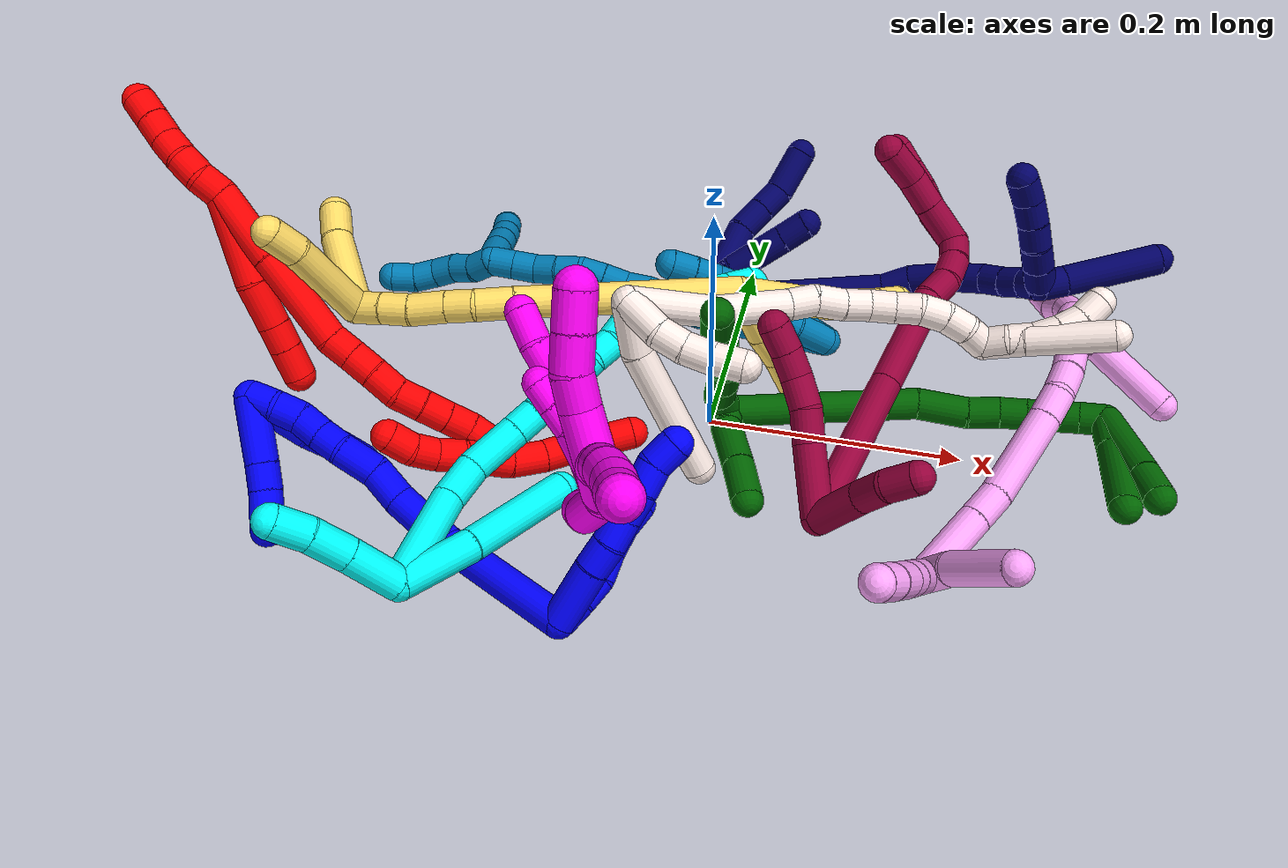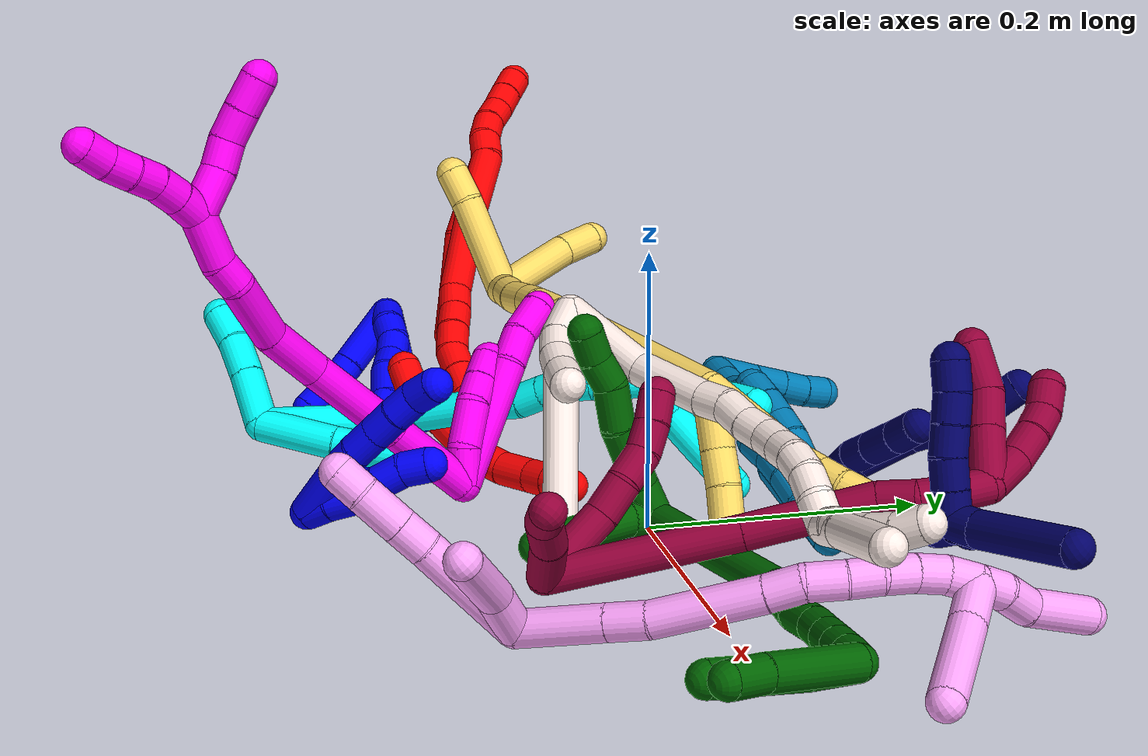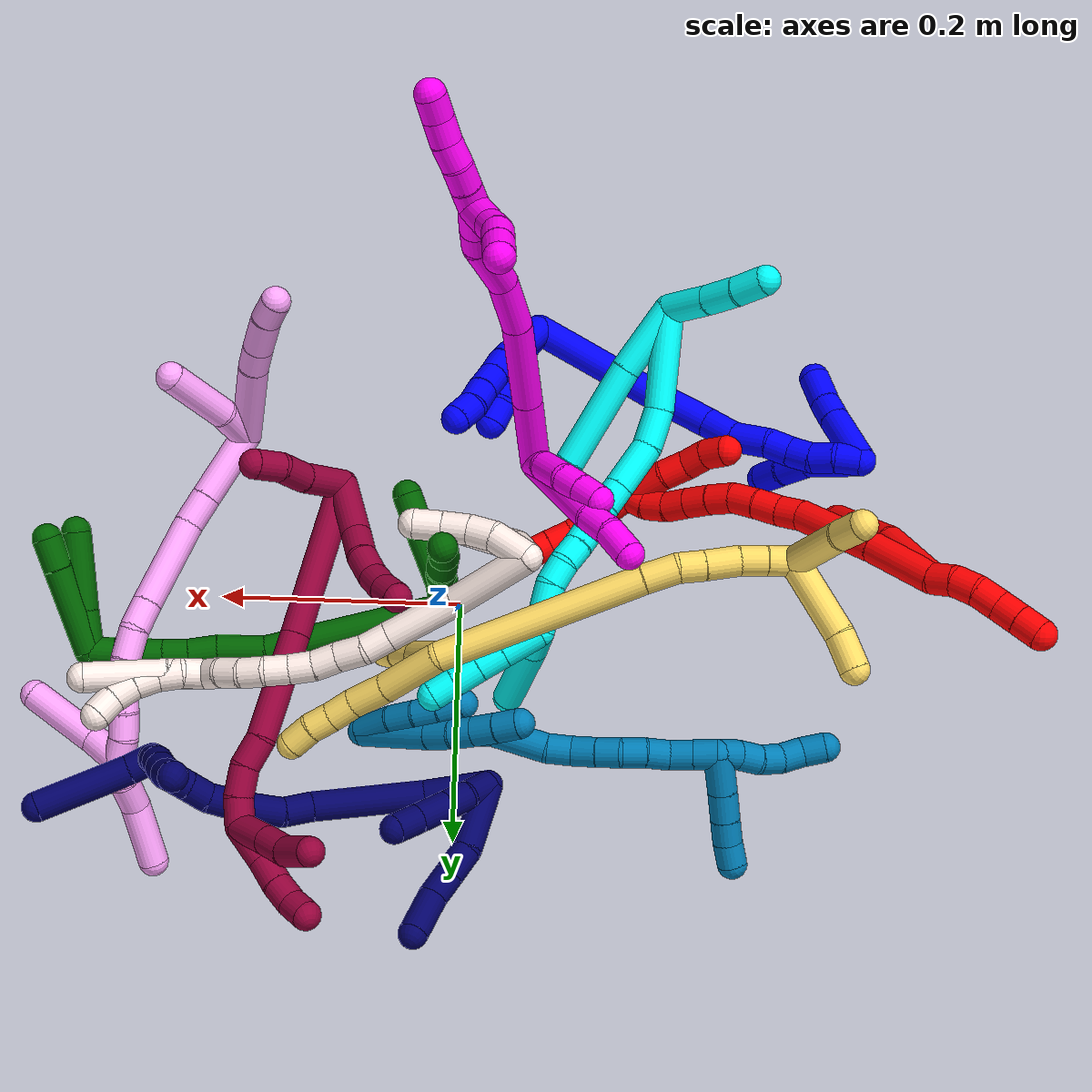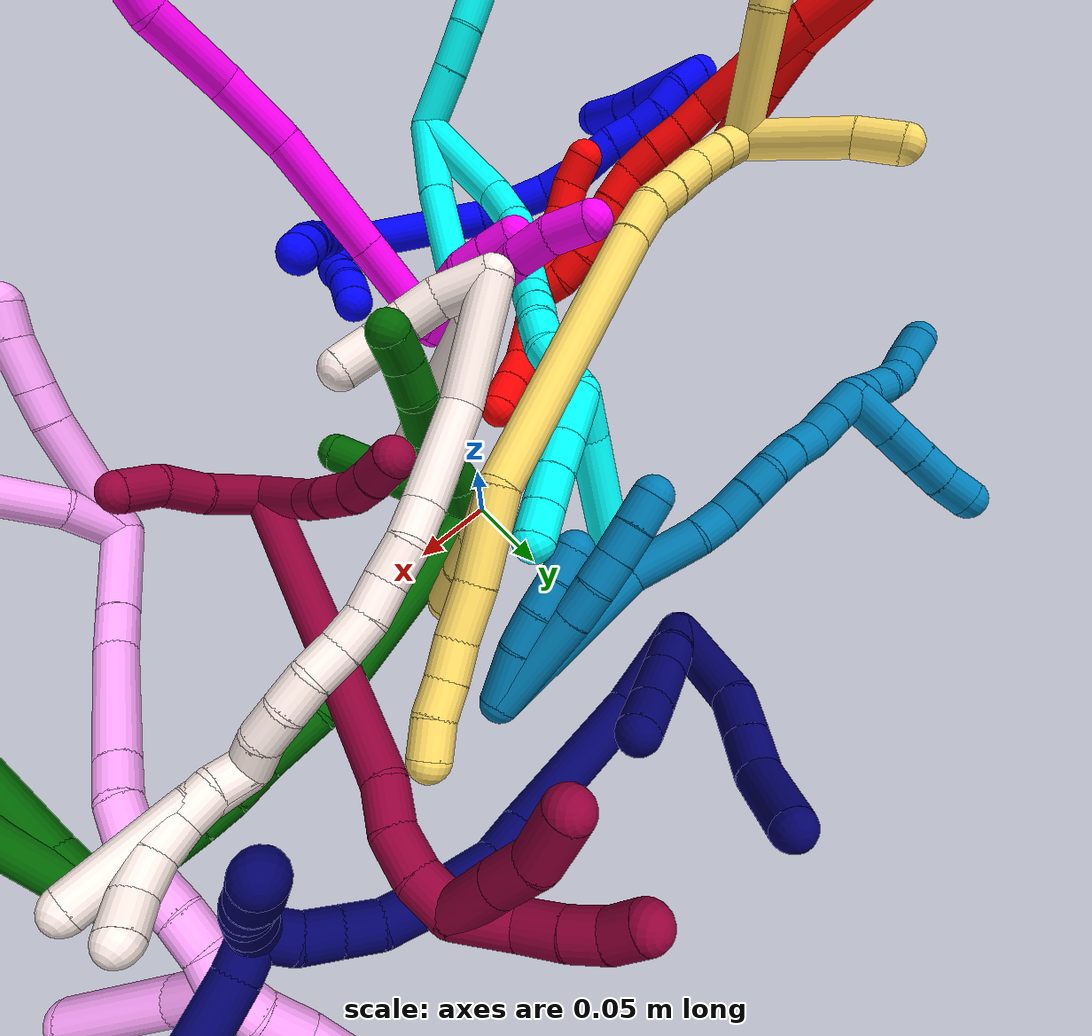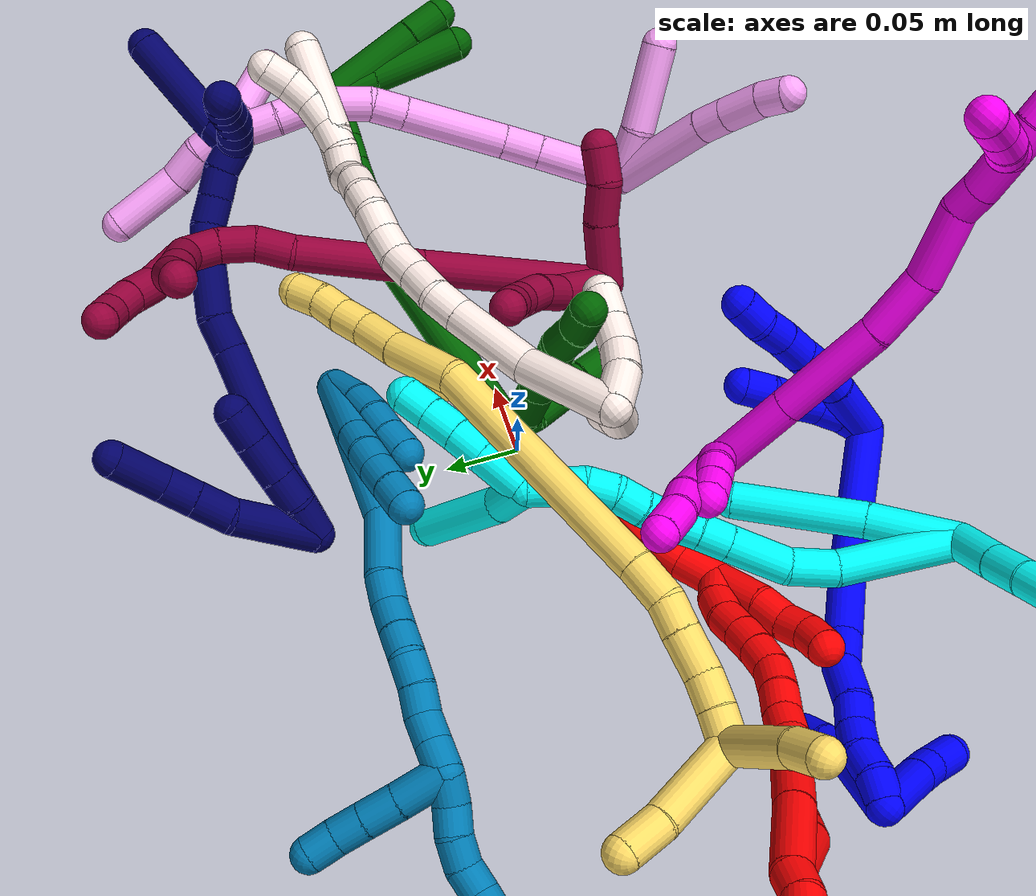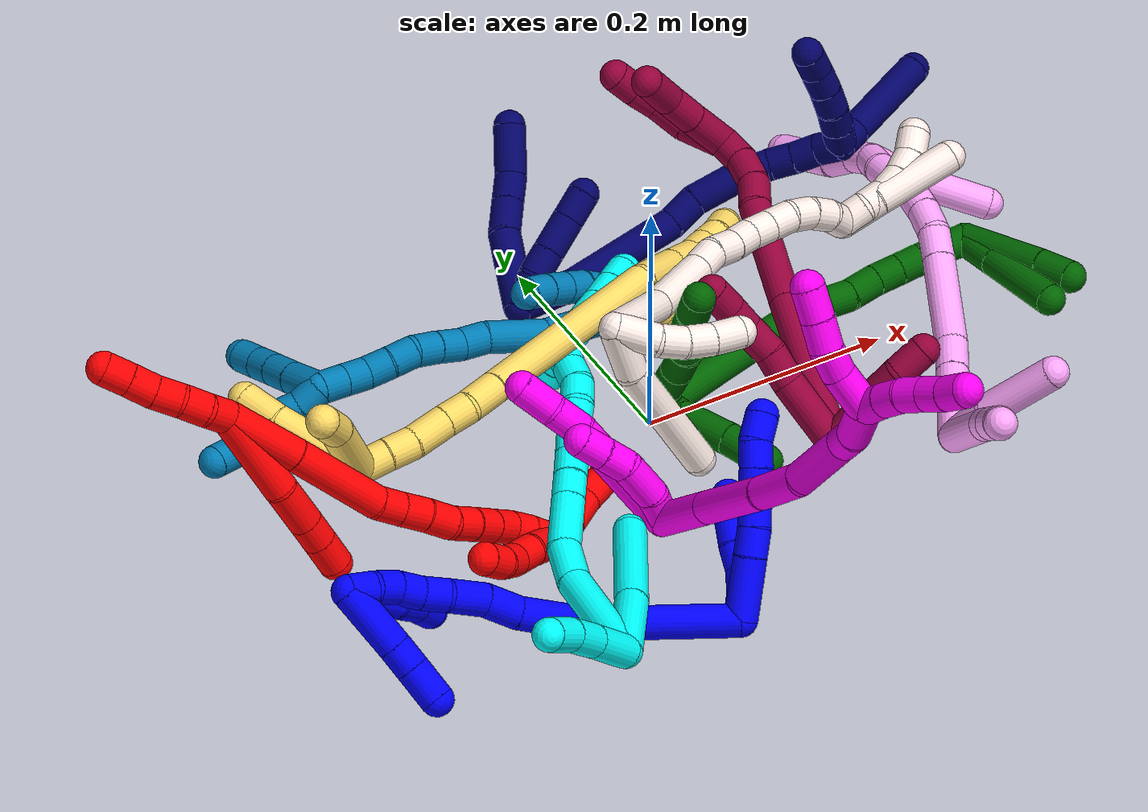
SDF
<sdf version="1.7">
 <world name="default">
  <plugin name="TubeGeneratorPlugin" filename="libtube_generator_plugin.so"/>
  <model name="photoneo_s_sensor">
   <static>1</static>
   <pose>0 0 2 1.57079 1.57079 3.14159</pose>
   <link name="link">
    <inertial><mass>0.1</mass></inertial>
    <sensor name="sensor" type="depth">
     <update_rate>30</update_rate>
     <camera>
      <horizontal_fov>1.22</horizontal_fov>
      <image><width>1920</width><height>1200</height><format>B8G8R8</format></image>
      <clip><near>0.1</near><far>4</far></clip>
      <depth_camera><output>points</output></depth_camera>
     </camera>
     <plugin name="camera_plugin" filename="libgazebo_ros_depth_camera.so">
      <baseline>0.2</baseline>
      <alwaysOn>1</alwaysOn>
      <updateRate>0.0</updateRate>
      <cameraName>camera_ir</cameraName>
      <imageTopicName>/camera/color/image_raw</imageTopicName>
      <cameraInfoTopicName>/camera/color/camera_info</cameraInfoTopicName>
      <depthImageTopicName>/camera/depth/image_raw</depthImageTopicName>
      <depthImageCameraInfoTopicName>/camera/depth/camera_info</depthImageCameraInfoTopicName>
      <pointCloudTopicName>/camera/depth/points</pointCloudTopicName>
      <frameName>fr_optical</frameName>
      <pointCloudCutoff>0.1</pointCloudCutoff>
      <pointCloudCutoffMax>2.0</pointCloudCutoffMax>
      <distortionK1>0</distortionK1>
      <distortionK2>0</distortionK2>
      <distortionK3>0</distortionK3>
      <distortionT1>0</distortionT1>
      <distortionT2>0</distortionT2>
      <CxPrime>0</CxPrime>
      <Cx>0</Cx>
      <Cy>0</Cy>
      <focalLength>0</focalLength>
      <hackBaseline>0</hackBaseline>
     </plugin>
    </sensor>
   </link>
  </model>
  <gravity>0 0 -9.8</gravity>
  <magnetic_field>6e-06 2.3e-05 -4.2e-05</magnetic_field>
  <atmosphere type="adiabatic"/>
  <physics name="default_physics" default="0" type="ode">
   <max_step_size>0.003</max_step_size>
   <real_time_factor>1</real_time_factor>
   <real_time_update_rate>1000</real_time_update_rate>
   <max_contacts>10000</max_contacts>
   <ode>
    <solver>
     <type>quick</type>
     <iters>100</iters>
     <sor>1.3</sor>
     <use_dynamic_moi_rescaling>0</use_dynamic_moi_rescaling>
    </solver>
    <constraints>
     <contact_max_correcting_vel>0</contact_max_correcting_vel>
     <contact_surface_layer>0.001</contact_surface_layer>
     <cfm>0</cfm>
     <erp>0.2</erp>
    </constraints>
   </ode>
  </physics>
  <scene><ambient>0.4 0.4 0.4 1</ambient><background>0.7 0.7 0.7 1</background><shadows>0</shadows></scene>
  <audio><device>default</device></audio>
  <spherical_coordinates>
   <surface_model>EARTH_WGS84</surface_model>
   <latitude_deg>0</latitude_deg>
   <longitude_deg>0</longitude_deg>
   <elevation>0</elevation>
   <heading_deg>0</heading_deg>
  </spherical_coordinates>
  <model name="bin">
   <static>1</static>
   <link name="bottom">
    <collision name="collision-bottom">
     <pose>0 0 -0.01 0 -0 0</pose>
     <geometry><box><size>0.8 0.6 0.02</size></box></geometry>
     <surface>
      <friction><ode><mu>100</mu><mu2>100</mu2></ode></friction>
      <contact><collide_bitmask>65535</collide_bitmask></contact>
     </surface>
    </collision>
   </link>
   <link name="west_wall">
    <collision name="collision-west_wall">
     <pose>-0.41 0 0.1 0 -0 0</pose>
     <geometry><box><size>0.02 0.6 0.2</size></box></geometry>
     <surface>
      <friction><ode><mu>100</mu><mu2>100</mu2></ode></friction>
      <contact><collide_bitmask>65535</collide_bitmask></contact>
     </surface>
    </collision>
   </link>
   <link name="east_wall">
    <collision name="collision-east_wall">
     <pose>0.41 0 0.1 0 -0 0</pose>
     <geometry><box><size>0.02 0.6 0.2</size></box></geometry>
     <surface>
      <friction><ode><mu>100</mu><mu2>100</mu2></ode></friction>
      <contact><collide_bitmask>65535</collide_bitmask></contact>
     </surface>
    </collision>
   </link>
   <link name="south_wall">
    <collision name="collision-south_wall">
     <pose>0 -0.31 0.1 0 -0 0</pose>
     <geometry><box><size>0.8 0.02 0.2</size></box></geometry>
     <surface>
      <friction><ode><mu>100</mu><mu2>100</mu2></ode></friction>
      <contact><collide_bitmask>65535</collide_bitmask></contact>
     </surface>
    </collision>
   </link>
   <link name="north_wall">
    <collision name="collision-north_wall">
     <pose>0 0.31 0.1 0 -0 0</pose>
     <geometry><box><size>0.8 0.02 0.2</size></box></geometry>
     <surface>
      <friction><ode><mu>100</mu><mu2>100</mu2></ode></friction>
      <contact><collide_bitmask>65535</collide_bitmask></contact>
     </surface>
    </collision>
   </link>
  </model>
  <model name="1">
   <static>0</static>
   <link name="1">
    <collision name="collision-cylinder-e_1_2_8">
     <pose>-0.000392 0.012512 -0.019524 -2.57166 -0.016896 0.057663</pose>
     <geometry><cylinder><radius>0.0125</radius><length>0.046384</length></cylinder></geometry>
     <surface>
      <friction><ode><mu>1.16</mu><mu2>1.16</mu2><slip1>0</slip1><slip2>0</slip2></ode></friction>
      <contact><ode><kp>1e+06</kp><kd>1</kd><max_vel>0</max_vel><min_depth>0.001</min_depth></ode></contact>
     </surface>
    </collision>
    <visual name="visual-cylinder-e_1_2_8">
     <pose>-0.000392 0.012512 -0.019524 -2.57166 -0.016896 0.057663</pose>
     <geometry><cylinder><radius>0.0125</radius><length>0.046384</length></cylinder></geometry>
     <material><ambient>0 0 1 1</ambient></material>
    </visual>
    <collision name="collision-cylinder-e_2_8_9">
     <pose>-0.001337 0.02993 -0.048445 -2.66052 -0.052131 0.211786</pose>
     <geometry><cylinder><radius>0.0125</radius><length>0.021231</length></cylinder></geometry>
     <surface>
      <friction><ode><mu>1.16</mu><mu2>1.16</mu2><slip1>0</slip1><slip2>0</slip2></ode></friction>
      <contact><ode><kp>1e+06</kp><kd>1</kd><max_vel>0</max_vel><min_depth>0.001</min_depth></ode></contact>
     </surface>
    </collision>
    <visual name="visual-cylinder-e_2_8_9">
     <pose>-0.001337 0.02993 -0.048445 -2.66052 -0.052131 0.211786</pose>
     <geometry><cylinder><radius>0.0125</radius><length>0.021231</length></cylinder></geometry>
     <material><ambient>0 0 1 1</ambient></material>
    </visual>
    <collision name="collision-cylinder-e_3_9_10">
     <pose>-0.00404 0.039583 -0.066922 -2.65971 -0.206851 0.799372</pose>
     <geometry><cylinder><radius>0.0125</radius><length>0.020937</length></cylinder></geometry>
     <surface>
      <friction><ode><mu>1.16</mu><mu2>1.16</mu2><slip1>0</slip1><slip2>0</slip2></ode></friction>
      <contact><ode><kp>1e+06</kp><kd>1</kd><max_vel>0</max_vel><min_depth>0.001</min_depth></ode></contact>
     </surface>
    </collision>
    <visual name="visual-cylinder-e_3_9_10">
     <pose>-0.00404 0.039583 -0.066922 -2.65971 -0.206851 0.799372</pose>
     <geometry><cylinder><radius>0.0125</radius><length>0.020937</length></cylinder></geometry>
     <material><ambient>0 0 1 1</ambient></material>
    </visual>
    <collision name="collision-cylinder-e_4_10_11">
     <pose>-0.007861 0.049113 -0.085365 -2.66948 -0.157618 0.634458</pose>
     <geometry><cylinder><radius>0.0125</radius><length>0.021293</length></cylinder></geometry>
     <surface>
      <friction><ode><mu>1.16</mu><mu2>1.16</mu2><slip1>0</slip1><slip2>0</slip2></ode></friction>
      <contact><ode><kp>1e+06</kp><kd>1</kd><max_vel>0</max_vel><min_depth>0.001</min_depth></ode></contact>
     </surface>
    </collision>
    <visual name="visual-cylinder-e_4_10_11">
     <pose>-0.007861 0.049113 -0.085365 -2.66948 -0.157618 0.634458</pose>
     <geometry><cylinder><radius>0.0125</radius><length>0.021293</length></cylinder></geometry>
     <material><ambient>0 0 1 1</ambient></material>
    </visual>
    <collision name="collision-cylinder-e_5_11_12">
     <pose>-0.012011 0.058305 -0.103384 -2.6703 -0.24982 0.963675</pose>
     <geometry><cylinder><radius>0.0125</radius><length>0.02005</length></cylinder></geometry>
     <surface>
      <friction><ode><mu>1.16</mu><mu2>1.16</mu2><slip1>0</slip1><slip2>0</slip2></ode></friction>
      <contact><ode><kp>1e+06</kp><kd>1</kd><max_vel>0</max_vel><min_depth>0.001</min_depth></ode></contact>
     </surface>
    </collision>
    <visual name="visual-cylinder-e_5_11_12">
     <pose>-0.012011 0.058305 -0.103384 -2.6703 -0.24982 0.963675</pose>
     <geometry><cylinder><radius>0.0125</radius><length>0.02005</length></cylinder></geometry>
     <material><ambient>0 0 1 1</ambient></material>
    </visual>
    <collision name="collision-cylinder-e_6_12_6">
     <pose>-0.01496 0.065067 -0.1218 -2.9052 -0.04683 0.389435</pose>
     <geometry><cylinder><radius>0.0125</radius><length>0.020105</length></cylinder></geometry>
     <surface>
      <friction><ode><mu>1.16</mu><mu2>1.16</mu2><slip1>0</slip1><slip2>0</slip2></ode></friction>
      <contact><ode><kp>1e+06</kp><kd>1</kd><max_vel>0</max_vel><min_depth>0.001</min_depth></ode></contact>
     </surface>
    </collision>
    <visual name="visual-cylinder-e_6_12_6">
     <pose>-0.01496 0.065067 -0.1218 -2.9052 -0.04683 0.389435</pose>
     <geometry><cylinder><radius>0.0125</radius><length>0.020105</length></cylinder></geometry>
     <material><ambient>0 0 1 1</ambient></material>
    </visual>
    <collision name="collision-cylinder-e_1_2_13">
     <pose>-0.002218 0.001406 -0.009649 -2.99691 -0.223646 1.99541</pose>
     <geometry><cylinder><radius>0.0125</radius><length>0.02</length></cylinder></geometry>
     <surface>
      <friction><ode><mu>1.16</mu><mu2>1.16</mu2><slip1>0</slip1><slip2>0</slip2></ode></friction>
      <contact><ode><kp>1e+06</kp><kd>1</kd><max_vel>0</max_vel><min_depth>0.001</min_depth></ode></contact>
     </surface>
    </collision>
    <visual name="visual-cylinder-e_1_2_13">
     <pose>-0.002218 0.001406 -0.009649 -2.99691 -0.223646 1.99541</pose>
     <geometry><cylinder><radius>0.0125</radius><length>0.02</length></cylinder></geometry>
     <material><ambient>0 0 1 1</ambient></material>
    </visual>
    <collision name="collision-cylinder-e_2_13_14">
     <pose>-0.008238 0.003368 -0.02853 -3.08143 -0.390051 2.83924</pose>
     <geometry><cylinder><radius>0.0125</radius><length>0.02</length></cylinder></geometry>
     <surface>
      <friction><ode><mu>1.16</mu><mu2>1.16</mu2><slip1>0</slip1><slip2>0</slip2></ode></friction>
      <contact><ode><kp>1e+06</kp><kd>1</kd><max_vel>0</max_vel><min_depth>0.001</min_depth></ode></contact>
     </surface>
    </collision>
    <visual name="visual-cylinder-e_2_13_14">
     <pose>-0.008238 0.003368 -0.02853 -3.08143 -0.390051 2.83924</pose>
     <geometry><cylinder><radius>0.0125</radius><length>0.02</length></cylinder></geometry>
     <material><ambient>0 0 1 1</ambient></material>
    </visual>
    <collision name="collision-cylinder-e_3_14_15">
     <pose>-0.017098 0.007351 -0.045679 -2.73312 -0.53028 1.8383</pose>
     <geometry><cylinder><radius>0.0125</radius><length>0.02</length></cylinder></geometry>
     <surface>
      <friction><ode><mu>1.16</mu><mu2>1.16</mu2><slip1>0</slip1><slip2>0</slip2></ode></friction>
      <contact><ode><kp>1e+06</kp><kd>1</kd><max_vel>0</max_vel><min_depth>0.001</min_depth></ode></contact>
     </surface>
    </collision>
    <visual name="visual-cylinder-e_3_14_15">
     <pose>-0.017098 0.007351 -0.045679 -2.73312 -0.53028 1.8383</pose>
     <geometry><cylinder><radius>0.0125</radius><length>0.02</length></cylinder></geometry>
     <material><ambient>0 0 1 1</ambient></material>
    </visual>
    <collision name="collision-cylinder-e_4_15_16">
     <pose>-0.026486 0.013578 -0.062164 -2.82559 -0.447842 1.92066</pose>
     <geometry><cylinder><radius>0.0125</radius><length>0.02</length></cylinder></geometry>
     <surface>
      <friction><ode><mu>1.16</mu><mu2>1.16</mu2><slip1>0</slip1><slip2>0</slip2></ode></friction>
      <contact><ode><kp>1e+06</kp><kd>1</kd><max_vel>0</max_vel><min_depth>0.001</min_depth></ode></contact>
     </surface>
    </collision>
    <visual name="visual-cylinder-e_4_15_16">
     <pose>-0.026486 0.013578 -0.062164 -2.82559 -0.447842 1.92066</pose>
     <geometry><cylinder><radius>0.0125</radius><length>0.02</length></cylinder></geometry>
     <material><ambient>0 0 1 1</ambient></material>
    </visual>
    <collision name="collision-cylinder-e_5_16_5">
     <pose>-0.035297 0.016427 -0.079671 -3.13626 -0.464571 3.11903</pose>
     <geometry><cylinder><radius>0.0125</radius><length>0.02</length></cylinder></geometry>
     <surface>
      <friction><ode><mu>1.16</mu><mu2>1.16</mu2><slip1>0</slip1><slip2>0</slip2></ode></friction>
      <contact><ode><kp>1e+06</kp><kd>1</kd><max_vel>0</max_vel><min_depth>0.001</min_depth></ode></contact>
     </surface>
    </collision>
    <visual name="visual-cylinder-e_5_16_5">
     <pose>-0.035297 0.016427 -0.079671 -3.13626 -0.464571 3.11903</pose>
     <geometry><cylinder><radius>0.0125</radius><length>0.02</length></cylinder></geometry>
     <material><ambient>0 0 1 1</ambient></material>
    </visual>
    <collision name="collision-cylinder-e_1_2_17">
     <pose>-0.04838 0.015195 0.021436 -0.616645 -1.07326 0.374459</pose>
     <geometry><cylinder><radius>0.0125</radius><length>0.11011</length></cylinder></geometry>
     <surface>
      <friction><ode><mu>1.16</mu><mu2>1.16</mu2><slip1>0</slip1><slip2>0</slip2></ode></friction>
      <contact><ode><kp>1e+06</kp><kd>1</kd><max_vel>0</max_vel><min_depth>0.001</min_depth></ode></contact>
     </surface>
    </collision>
    <visual name="visual-cylinder-e_1_2_17">
     <pose>-0.04838 0.015195 0.021436 -0.616645 -1.07326 0.374459</pose>
     <geometry><cylinder><radius>0.0125</radius><length>0.11011</length></cylinder></geometry>
     <material><ambient>0 0 1 1</ambient></material>
    </visual>
    <collision name="collision-cylinder-e_2_17_18">
     <pose>-0.117555 0.043529 0.050747 -1.03087 -0.935939 0.55773</pose>
     <geometry><cylinder><radius>0.0125</radius><length>0.051656</length></cylinder></geometry>
     <surface>
      <friction><ode><mu>1.16</mu><mu2>1.16</mu2><slip1>0</slip1><slip2>0</slip2></ode></friction>
      <contact><ode><kp>1e+06</kp><kd>1</kd><max_vel>0</max_vel><min_depth>0.001</min_depth></ode></contact>
     </surface>
    </collision>
    <visual name="visual-cylinder-e_2_17_18">
     <pose>-0.117555 0.043529 0.050747 -1.03087 -0.935939 0.55773</pose>
     <geometry><cylinder><radius>0.0125</radius><length>0.051656</length></cylinder></geometry>
     <material><ambient>0 0 1 1</ambient></material>
    </visual>
    <collision name="collision-cylinder-e_3_18_19">
     <pose>-0.148312 0.065984 0.060829 -1.3381 -0.80523 0.649637</pose>
     <geometry><cylinder><radius>0.0125</radius><length>0.027633</length></cylinder></geometry>
     <surface>
      <friction><ode><mu>1.16</mu><mu2>1.16</mu2><slip1>0</slip1><slip2>0</slip2></ode></friction>
      <contact><ode><kp>1e+06</kp><kd>1</kd><max_vel>0</max_vel><min_depth>0.001</min_depth></ode></contact>
     </surface>
    </collision>
    <visual name="visual-cylinder-e_3_18_19">
     <pose>-0.148312 0.065984 0.060829 -1.3381 -0.80523 0.649637</pose>
     <geometry><cylinder><radius>0.0125</radius><length>0.027633</length></cylinder></geometry>
     <material><ambient>0 0 1 1</ambient></material>
    </visual>
    <collision name="collision-cylinder-e_4_19_20">
     <pose>-0.166973 0.085902 0.069565 -1.01886 -0.609833 0.348069</pose>
     <geometry><cylinder><radius>0.0125</radius><length>0.030377</length></cylinder></geometry>
     <surface>
      <friction><ode><mu>1.16</mu><mu2>1.16</mu2><slip1>0</slip1><slip2>0</slip2></ode></friction>
      <contact><ode><kp>1e+06</kp><kd>1</kd><max_vel>0</max_vel><min_depth>0.001</min_depth></ode></contact>
     </surface>
    </collision>
    <visual name="visual-cylinder-e_4_19_20">
     <pose>-0.166973 0.085902 0.069565 -1.01886 -0.609833 0.348069</pose>
     <geometry><cylinder><radius>0.0125</radius><length>0.030377</length></cylinder></geometry>
     <material><ambient>0 0 1 1</ambient></material>
    </visual>
    <collision name="collision-cylinder-e_5_20_21">
     <pose>-0.183152 0.10195 0.079995 -0.94926 -0.840457 0.451361</pose>
     <geometry><cylinder><radius>0.0125</radius><length>0.020084</length></cylinder></geometry>
     <surface>
      <friction><ode><mu>1.16</mu><mu2>1.16</mu2><slip1>0</slip1><slip2>0</slip2></ode></friction>
      <contact><ode><kp>1e+06</kp><kd>1</kd><max_vel>0</max_vel><min_depth>0.001</min_depth></ode></contact>
     </surface>
    </collision>
    <visual name="visual-cylinder-e_5_20_21">
     <pose>-0.183152 0.10195 0.079995 -0.94926 -0.840457 0.451361</pose>
     <geometry><cylinder><radius>0.0125</radius><length>0.020084</length></cylinder></geometry>
     <material><ambient>0 0 1 1</ambient></material>
    </visual>
    <collision name="collision-cylinder-e_6_21_22">
     <pose>-0.196855 0.11452 0.087169 -1.13996 -0.670855 0.439644</pose>
     <geometry><cylinder><radius>0.0125</radius><length>0.020017</length></cylinder></geometry>
     <surface>
      <friction><ode><mu>1.16</mu><mu2>1.16</mu2><slip1>0</slip1><slip2>0</slip2></ode></friction>
      <contact><ode><kp>1e+06</kp><kd>1</kd><max_vel>0</max_vel><min_depth>0.001</min_depth></ode></contact>
     </surface>
    </collision>
    <visual name="visual-cylinder-e_6_21_22">
     <pose>-0.196855 0.11452 0.087169 -1.13996 -0.670855 0.439644</pose>
     <geometry><cylinder><radius>0.0125</radius><length>0.020017</length></cylinder></geometry>
     <material><ambient>0 0 1 1</ambient></material>
    </visual>
    <collision name="collision-cylinder-e_7_22_23">
     <pose>-0.207344 0.128835 0.095943 -0.918032 -0.440432 0.220364</pose>
     <geometry><cylinder><radius>0.0125</radius><length>0.020018</length></cylinder></geometry>
     <surface>
      <friction><ode><mu>1.16</mu><mu2>1.16</mu2><slip1>0</slip1><slip2>0</slip2></ode></friction>
      <contact><ode><kp>1e+06</kp><kd>1</kd><max_vel>0</max_vel><min_depth>0.001</min_depth></ode></contact>
     </surface>
    </collision>
    <visual name="visual-cylinder-e_7_22_23">
     <pose>-0.207344 0.128835 0.095943 -0.918032 -0.440432 0.220364</pose>
     <geometry><cylinder><radius>0.0125</radius><length>0.020018</length></cylinder></geometry>
     <material><ambient>0 0 1 1</ambient></material>
    </visual>
    <collision name="collision-cylinder-e_8_23_1">
     <pose>-0.217781 0.141201 0.10746 -0.710036 -0.66081 0.252944</pose>
     <geometry><cylinder><radius>0.0125</radius><length>0.020106</length></cylinder></geometry>
     <surface>
      <friction><ode><mu>1.16</mu><mu2>1.16</mu2><slip1>0</slip1><slip2>0</slip2></ode></friction>
      <contact><ode><kp>1e+06</kp><kd>1</kd><max_vel>0</max_vel><min_depth>0.001</min_depth></ode></contact>
     </surface>
    </collision>
    <visual name="visual-cylinder-e_8_23_1">
     <pose>-0.217781 0.141201 0.10746 -0.710036 -0.66081 0.252944</pose>
     <geometry><cylinder><radius>0.0125</radius><length>0.020106</length></cylinder></geometry>
     <material><ambient>0 0 1 1</ambient></material>
    </visual>
    <collision name="collision-cylinder-e_1_1_24">
     <pose>-0.215458 0.125613 0.103532 2.01758 0.353445 0.552656</pose>
     <geometry><cylinder><radius>0.0125</radius><length>0.049077</length></cylinder></geometry>
     <surface>
      <friction><ode><mu>1.16</mu><mu2>1.16</mu2><slip1>0</slip1><slip2>0</slip2></ode></friction>
      <contact><ode><kp>1e+06</kp><kd>1</kd><max_vel>0</max_vel><min_depth>0.001</min_depth></ode></contact>
     </surface>
    </collision>
    <visual name="visual-cylinder-e_1_1_24">
     <pose>-0.215458 0.125613 0.103532 2.01758 0.353445 0.552656</pose>
     <geometry><cylinder><radius>0.0125</radius><length>0.049077</length></cylinder></geometry>
     <material><ambient>0 0 1 1</ambient></material>
    </visual>
    <collision name="collision-cylinder-e_2_24_25">
     <pose>-0.205684 0.093059 0.087505 2.04685 0.096155 0.157558</pose>
     <geometry><cylinder><radius>0.0125</radius><length>0.026657</length></cylinder></geometry>
     <surface>
      <friction><ode><mu>1.16</mu><mu2>1.16</mu2><slip1>0</slip1><slip2>0</slip2></ode></friction>
      <contact><ode><kp>1e+06</kp><kd>1</kd><max_vel>0</max_vel><min_depth>0.001</min_depth></ode></contact>
     </surface>
    </collision>
    <visual name="visual-cylinder-e_2_24_25">
     <pose>-0.205684 0.093059 0.087505 2.04685 0.096155 0.157558</pose>
     <geometry><cylinder><radius>0.0125</radius><length>0.026657</length></cylinder></geometry>
     <material><ambient>0 0 1 1</ambient></material>
    </visual>
    <collision name="collision-cylinder-e_3_25_4">
     <pose>-0.203892 0.069872 0.077292 1.91877 0.042269 0.060288</pose>
     <geometry><cylinder><radius>0.0125</radius><length>0.024266</length></cylinder></geometry>
     <surface>
      <friction><ode><mu>1.16</mu><mu2>1.16</mu2><slip1>0</slip1><slip2>0</slip2></ode></friction>
      <contact><ode><kp>1e+06</kp><kd>1</kd><max_vel>0</max_vel><min_depth>0.001</min_depth></ode></contact>
     </surface>
    </collision>
    <visual name="visual-cylinder-e_3_25_4">
     <pose>-0.203892 0.069872 0.077292 1.91877 0.042269 0.060288</pose>
     <geometry><cylinder><radius>0.0125</radius><length>0.024266</length></cylinder></geometry>
     <material><ambient>0 0 1 1</ambient></material>
    </visual>
    <collision name="collision-cylinder-e_1_1_26">
     <pose>-0.207294 0.129239 0.122354 1.0929 0.712087 0.444904</pose>
     <geometry><cylinder><radius>0.0125</radius><length>0.050984</length></cylinder></geometry>
     <surface>
      <friction><ode><mu>1.16</mu><mu2>1.16</mu2><slip1>0</slip1><slip2>0</slip2></ode></friction>
      <contact><ode><kp>1e+06</kp><kd>1</kd><max_vel>0</max_vel><min_depth>0.001</min_depth></ode></contact>
     </surface>
    </collision>
    <visual name="visual-cylinder-e_1_1_26">
     <pose>-0.207294 0.129239 0.122354 1.0929 0.712087 0.444904</pose>
     <geometry><cylinder><radius>0.0125</radius><length>0.050984</length></cylinder></geometry>
     <material><ambient>0 0 1 1</ambient></material>
    </visual>
    <collision name="collision-cylinder-e_2_26_27">
     <pose>-0.183961 0.105243 0.135141 1.05269 0.701837 0.419142</pose>
     <geometry><cylinder><radius>0.0125</radius><length>0.020683</length></cylinder></geometry>
     <surface>
      <friction><ode><mu>1.16</mu><mu2>1.16</mu2><slip1>0</slip1><slip2>0</slip2></ode></friction>
      <contact><ode><kp>1e+06</kp><kd>1</kd><max_vel>0</max_vel><min_depth>0.001</min_depth></ode></contact>
     </surface>
    </collision>
    <visual name="visual-cylinder-e_2_26_27">
     <pose>-0.183961 0.105243 0.135141 1.05269 0.701837 0.419142</pose>
     <geometry><cylinder><radius>0.0125</radius><length>0.020683</length></cylinder></geometry>
     <material><ambient>0 0 1 1</ambient></material>
    </visual>
    <collision name="collision-cylinder-e_3_27_3">
     <pose>-0.167334 0.090411 0.145228 0.91157 0.778725 0.39698</pose>
     <geometry><cylinder><radius>0.0125</radius><length>0.028333</length></cylinder></geometry>
     <surface>
      <friction><ode><mu>1.16</mu><mu2>1.16</mu2><slip1>0</slip1><slip2>0</slip2></ode></friction>
      <contact><ode><kp>1e+06</kp><kd>1</kd><max_vel>0</max_vel><min_depth>0.001</min_depth></ode></contact>
     </surface>
    </collision>
    <visual name="visual-cylinder-e_3_27_3">
     <pose>-0.167334 0.090411 0.145228 0.91157 0.778725 0.39698</pose>
     <geometry><cylinder><radius>0.0125</radius><length>0.028333</length></cylinder></geometry>
     <material><ambient>0 0 1 1</ambient></material>
    </visual>
    <collision name="collision-sphere-3">
     <pose>-0.157384 0.08244 0.151404 0 -0 0</pose>
     <geometry><sphere><radius>0.0125</radius></sphere></geometry>
     <surface>
      <friction><ode><mu>1.16</mu><mu2>1.16</mu2><slip1>0</slip1><slip2>0</slip2></ode></friction>
      <contact><ode><kp>1e+06</kp><kd>1</kd><max_vel>0</max_vel><min_depth>0.001</min_depth></ode></contact>
     </surface>
    </collision>
    <visual name="visual-sphere-3">
     <pose>-0.157384 0.08244 0.151404 0 -0 0</pose>
     <geometry><sphere><radius>0.0125</radius></sphere></geometry>
     <material><ambient>0 0 1 1</ambient></material>
    </visual>
    <collision name="collision-sphere-27">
     <pose>-0.177284 0.098382 0.139052 0 -0 0</pose>
     <geometry><sphere><radius>0.0125</radius></sphere></geometry>
     <surface>
      <friction><ode><mu>1.16</mu><mu2>1.16</mu2><slip1>0</slip1><slip2>0</slip2></ode></friction>
      <contact><ode><kp>1e+06</kp><kd>1</kd><max_vel>0</max_vel><min_depth>0.001</min_depth></ode></contact>
     </surface>
    </collision>
    <visual name="visual-sphere-27">
     <pose>-0.177284 0.098382 0.139052 0 -0 0</pose>
     <geometry><sphere><radius>0.0125</radius></sphere></geometry>
     <material><ambient>0 0 1 1</ambient></material>
    </visual>
    <collision name="collision-sphere-26">
     <pose>-0.190637 0.112104 0.13123 0 -0 0</pose>
     <geometry><sphere><radius>0.0125</radius></sphere></geometry>
     <surface>
      <friction><ode><mu>1.16</mu><mu2>1.16</mu2><slip1>0</slip1><slip2>0</slip2></ode></friction>
      <contact><ode><kp>1e+06</kp><kd>1</kd><max_vel>0</max_vel><min_depth>0.001</min_depth></ode></contact>
     </surface>
    </collision>
    <visual name="visual-sphere-26">
     <pose>-0.190637 0.112104 0.13123 0 -0 0</pose>
     <geometry><sphere><radius>0.0125</radius></sphere></geometry>
     <material><ambient>0 0 1 1</ambient></material>
    </visual>
    <collision name="collision-sphere-4">
     <pose>-0.203379 0.058476 0.073158 0 -0 0</pose>
     <geometry><sphere><radius>0.0125</radius></sphere></geometry>
     <surface>
      <friction><ode><mu>1.16</mu><mu2>1.16</mu2><slip1>0</slip1><slip2>0</slip2></ode></friction>
      <contact><ode><kp>1e+06</kp><kd>1</kd><max_vel>0</max_vel><min_depth>0.001</min_depth></ode></contact>
     </surface>
    </collision>
    <visual name="visual-sphere-4">
     <pose>-0.203379 0.058476 0.073158 0 -0 0</pose>
     <geometry><sphere><radius>0.0125</radius></sphere></geometry>
     <material><ambient>0 0 1 1</ambient></material>
    </visual>
    <collision name="collision-sphere-25">
     <pose>-0.204405 0.081268 0.081426 0 -0 0</pose>
     <geometry><sphere><radius>0.0125</radius></sphere></geometry>
     <surface>
      <friction><ode><mu>1.16</mu><mu2>1.16</mu2><slip1>0</slip1><slip2>0</slip2></ode></friction>
      <contact><ode><kp>1e+06</kp><kd>1</kd><max_vel>0</max_vel><min_depth>0.001</min_depth></ode></contact>
     </surface>
    </collision>
    <visual name="visual-sphere-25">
     <pose>-0.204405 0.081268 0.081426 0 -0 0</pose>
     <geometry><sphere><radius>0.0125</radius></sphere></geometry>
     <material><ambient>0 0 1 1</ambient></material>
    </visual>
    <collision name="collision-sphere-24">
     <pose>-0.206964 0.104851 0.093585 0 -0 0</pose>
     <geometry><sphere><radius>0.0125</radius></sphere></geometry>
     <surface>
      <friction><ode><mu>1.16</mu><mu2>1.16</mu2><slip1>0</slip1><slip2>0</slip2></ode></friction>
      <contact><ode><kp>1e+06</kp><kd>1</kd><max_vel>0</max_vel><min_depth>0.001</min_depth></ode></contact>
     </surface>
    </collision>
    <visual name="visual-sphere-24">
     <pose>-0.206964 0.104851 0.093585 0 -0 0</pose>
     <geometry><sphere><radius>0.0125</radius></sphere></geometry>
     <material><ambient>0 0 1 1</ambient></material>
    </visual>
    <collision name="collision-sphere-1">
     <pose>-0.223951 0.146375 0.113479 0 -0 0</pose>
     <geometry><sphere><radius>0.0125</radius></sphere></geometry>
     <surface>
      <friction><ode><mu>1.16</mu><mu2>1.16</mu2><slip1>0</slip1><slip2>0</slip2></ode></friction>
      <contact><ode><kp>1e+06</kp><kd>1</kd><max_vel>0</max_vel><min_depth>0.001</min_depth></ode></contact>
     </surface>
    </collision>
    <visual name="visual-sphere-1">
     <pose>-0.223951 0.146375 0.113479 0 -0 0</pose>
     <geometry><sphere><radius>0.0125</radius></sphere></geometry>
     <material><ambient>0 0 1 1</ambient></material>
    </visual>
    <collision name="collision-sphere-23">
     <pose>-0.211611 0.136028 0.101442 0 -0 0</pose>
     <geometry><sphere><radius>0.0125</radius></sphere></geometry>
     <surface>
      <friction><ode><mu>1.16</mu><mu2>1.16</mu2><slip1>0</slip1><slip2>0</slip2></ode></friction>
      <contact><ode><kp>1e+06</kp><kd>1</kd><max_vel>0</max_vel><min_depth>0.001</min_depth></ode></contact>
     </surface>
    </collision>
    <visual name="visual-sphere-23">
     <pose>-0.211611 0.136028 0.101442 0 -0 0</pose>
     <geometry><sphere><radius>0.0125</radius></sphere></geometry>
     <material><ambient>0 0 1 1</ambient></material>
    </visual>
    <collision name="collision-sphere-22">
     <pose>-0.203077 0.121643 0.090443 0 -0 0</pose>
     <geometry><sphere><radius>0.0125</radius></sphere></geometry>
     <surface>
      <friction><ode><mu>1.16</mu><mu2>1.16</mu2><slip1>0</slip1><slip2>0</slip2></ode></friction>
      <contact><ode><kp>1e+06</kp><kd>1</kd><max_vel>0</max_vel><min_depth>0.001</min_depth></ode></contact>
     </surface>
    </collision>
    <visual name="visual-sphere-22">
     <pose>-0.203077 0.121643 0.090443 0 -0 0</pose>
     <geometry><sphere><radius>0.0125</radius></sphere></geometry>
     <material><ambient>0 0 1 1</ambient></material>
    </visual>
    <collision name="collision-sphere-21">
     <pose>-0.190633 0.107396 0.083895 0 -0 0</pose>
     <geometry><sphere><radius>0.0125</radius></sphere></geometry>
     <surface>
      <friction><ode><mu>1.16</mu><mu2>1.16</mu2><slip1>0</slip1><slip2>0</slip2></ode></friction>
      <contact><ode><kp>1e+06</kp><kd>1</kd><max_vel>0</max_vel><min_depth>0.001</min_depth></ode></contact>
     </surface>
    </collision>
    <visual name="visual-sphere-21">
     <pose>-0.190633 0.107396 0.083895 0 -0 0</pose>
     <geometry><sphere><radius>0.0125</radius></sphere></geometry>
     <material><ambient>0 0 1 1</ambient></material>
    </visual>
    <collision name="collision-sphere-12">
     <pose>-0.014489 0.062715 -0.112038 0 -0 0</pose>
     <geometry><sphere><radius>0.0125</radius></sphere></geometry>
     <surface>
      <friction><ode><mu>1.16</mu><mu2>1.16</mu2><slip1>0</slip1><slip2>0</slip2></ode></friction>
      <contact><ode><kp>1e+06</kp><kd>1</kd><max_vel>0</max_vel><min_depth>0.001</min_depth></ode></contact>
     </surface>
    </collision>
    <visual name="visual-sphere-12">
     <pose>-0.014489 0.062715 -0.112038 0 -0 0</pose>
     <geometry><sphere><radius>0.0125</radius></sphere></geometry>
     <material><ambient>0 0 1 1</ambient></material>
    </visual>
    <collision name="collision-sphere-11">
     <pose>-0.009532 0.053895 -0.094729 0 -0 0</pose>
     <geometry><sphere><radius>0.0125</radius></sphere></geometry>
     <surface>
      <friction><ode><mu>1.16</mu><mu2>1.16</mu2><slip1>0</slip1><slip2>0</slip2></ode></friction>
      <contact><ode><kp>1e+06</kp><kd>1</kd><max_vel>0</max_vel><min_depth>0.001</min_depth></ode></contact>
     </surface>
    </collision>
    <visual name="visual-sphere-11">
     <pose>-0.009532 0.053895 -0.094729 0 -0 0</pose>
     <geometry><sphere><radius>0.0125</radius></sphere></geometry>
     <material><ambient>0 0 1 1</ambient></material>
    </visual>
    <collision name="collision-sphere-10">
     <pose>-0.00619 0.044332 -0.076001 0 -0 0</pose>
     <geometry><sphere><radius>0.0125</radius></sphere></geometry>
     <surface>
      <friction><ode><mu>1.16</mu><mu2>1.16</mu2><slip1>0</slip1><slip2>0</slip2></ode></friction>
      <contact><ode><kp>1e+06</kp><kd>1</kd><max_vel>0</max_vel><min_depth>0.001</min_depth></ode></contact>
     </surface>
    </collision>
    <visual name="visual-sphere-10">
     <pose>-0.00619 0.044332 -0.076001 0 -0 0</pose>
     <geometry><sphere><radius>0.0125</radius></sphere></geometry>
     <material><ambient>0 0 1 1</ambient></material>
    </visual>
    <collision name="collision-sphere-9">
     <pose>-0.00189 0.034835 -0.057843 0 -0 0</pose>
     <geometry><sphere><radius>0.0125</radius></sphere></geometry>
     <surface>
      <friction><ode><mu>1.16</mu><mu2>1.16</mu2><slip1>0</slip1><slip2>0</slip2></ode></friction>
      <contact><ode><kp>1e+06</kp><kd>1</kd><max_vel>0</max_vel><min_depth>0.001</min_depth></ode></contact>
     </surface>
    </collision>
    <visual name="visual-sphere-9">
     <pose>-0.00189 0.034835 -0.057843 0 -0 0</pose>
     <geometry><sphere><radius>0.0125</radius></sphere></geometry>
     <material><ambient>0 0 1 1</ambient></material>
    </visual>
    <collision name="collision-sphere-2">
     <geometry><sphere><radius>0.0125</radius></sphere></geometry>
     <surface>
      <friction><ode><mu>1.16</mu><mu2>1.16</mu2><slip1>0</slip1><slip2>0</slip2></ode></friction>
      <contact><ode><kp>1e+06</kp><kd>1</kd><max_vel>0</max_vel><min_depth>0.001</min_depth></ode></contact>
     </surface>
    </collision>
    <visual name="visual-sphere-2">
     <geometry><sphere><radius>0.0125</radius></sphere></geometry>
     <material><ambient>0 0 1 1</ambient></material>
    </visual>
    <collision name="collision-sphere-19">
     <pose>-0.158274 0.0753 0.063037 0 -0 0</pose>
     <geometry><sphere><radius>0.0125</radius></sphere></geometry>
     <surface>
      <friction><ode><mu>1.16</mu><mu2>1.16</mu2><slip1>0</slip1><slip2>0</slip2></ode></friction>
      <contact><ode><kp>1e+06</kp><kd>1</kd><max_vel>0</max_vel><min_depth>0.001</min_depth></ode></contact>
     </surface>
    </collision>
    <visual name="visual-sphere-19">
     <pose>-0.158274 0.0753 0.063037 0 -0 0</pose>
     <geometry><sphere><radius>0.0125</radius></sphere></geometry>
     <material><ambient>0 0 1 1</ambient></material>
    </visual>
    <collision name="collision-sphere-8">
     <pose>-0.000784 0.025024 -0.039047 0 -0 0</pose>
     <geometry><sphere><radius>0.0125</radius></sphere></geometry>
     <surface>
      <friction><ode><mu>1.16</mu><mu2>1.16</mu2><slip1>0</slip1><slip2>0</slip2></ode></friction>
      <contact><ode><kp>1e+06</kp><kd>1</kd><max_vel>0</max_vel><min_depth>0.001</min_depth></ode></contact>
     </surface>
    </collision>
    <visual name="visual-sphere-8">
     <pose>-0.000784 0.025024 -0.039047 0 -0 0</pose>
     <geometry><sphere><radius>0.0125</radius></sphere></geometry>
     <material><ambient>0 0 1 1</ambient></material>
    </visual>
    <collision name="collision-sphere-6">
     <pose>-0.01543 0.067419 -0.131563 0 -0 0</pose>
     <geometry><sphere><radius>0.0125</radius></sphere></geometry>
     <surface>
      <friction><ode><mu>1.16</mu><mu2>1.16</mu2><slip1>0</slip1><slip2>0</slip2></ode></friction>
      <contact><ode><kp>1e+06</kp><kd>1</kd><max_vel>0</max_vel><min_depth>0.001</min_depth></ode></contact>
     </surface>
    </collision>
    <visual name="visual-sphere-6">
     <pose>-0.01543 0.067419 -0.131563 0 -0 0</pose>
     <geometry><sphere><radius>0.0125</radius></sphere></geometry>
     <material><ambient>0 0 1 1</ambient></material>
    </visual>
    <collision name="collision-sphere-13">
     <pose>-0.004436 0.002812 -0.019298 0 -0 0</pose>
     <geometry><sphere><radius>0.0125</radius></sphere></geometry>
     <surface>
      <friction><ode><mu>1.16</mu><mu2>1.16</mu2><slip1>0</slip1><slip2>0</slip2></ode></friction>
      <contact><ode><kp>1e+06</kp><kd>1</kd><max_vel>0</max_vel><min_depth>0.001</min_depth></ode></contact>
     </surface>
    </collision>
    <visual name="visual-sphere-13">
     <pose>-0.004436 0.002812 -0.019298 0 -0 0</pose>
     <geometry><sphere><radius>0.0125</radius></sphere></geometry>
     <material><ambient>0 0 1 1</ambient></material>
    </visual>
    <collision name="collision-sphere-14">
     <pose>-0.01204 0.003924 -0.037762 0 -0 0</pose>
     <geometry><sphere><radius>0.0125</radius></sphere></geometry>
     <surface>
      <friction><ode><mu>1.16</mu><mu2>1.16</mu2><slip1>0</slip1><slip2>0</slip2></ode></friction>
      <contact><ode><kp>1e+06</kp><kd>1</kd><max_vel>0</max_vel><min_depth>0.001</min_depth></ode></contact>
     </surface>
    </collision>
    <visual name="visual-sphere-14">
     <pose>-0.01204 0.003924 -0.037762 0 -0 0</pose>
     <geometry><sphere><radius>0.0125</radius></sphere></geometry>
     <material><ambient>0 0 1 1</ambient></material>
    </visual>
    <collision name="collision-sphere-15">
     <pose>-0.022156 0.010777 -0.053596 0 -0 0</pose>
     <geometry><sphere><radius>0.0125</radius></sphere></geometry>
     <surface>
      <friction><ode><mu>1.16</mu><mu2>1.16</mu2><slip1>0</slip1><slip2>0</slip2></ode></friction>
      <contact><ode><kp>1e+06</kp><kd>1</kd><max_vel>0</max_vel><min_depth>0.001</min_depth></ode></contact>
     </surface>
    </collision>
    <visual name="visual-sphere-15">
     <pose>-0.022156 0.010777 -0.053596 0 -0 0</pose>
     <geometry><sphere><radius>0.0125</radius></sphere></geometry>
     <material><ambient>0 0 1 1</ambient></material>
    </visual>
    <collision name="collision-sphere-16">
     <pose>-0.030816 0.01638 -0.070731 0 -0 0</pose>
     <geometry><sphere><radius>0.0125</radius></sphere></geometry>
     <surface>
      <friction><ode><mu>1.16</mu><mu2>1.16</mu2><slip1>0</slip1><slip2>0</slip2></ode></friction>
      <contact><ode><kp>1e+06</kp><kd>1</kd><max_vel>0</max_vel><min_depth>0.001</min_depth></ode></contact>
     </surface>
    </collision>
    <visual name="visual-sphere-16">
     <pose>-0.030816 0.01638 -0.070731 0 -0 0</pose>
     <geometry><sphere><radius>0.0125</radius></sphere></geometry>
     <material><ambient>0 0 1 1</ambient></material>
    </visual>
    <collision name="collision-sphere-5">
     <pose>-0.039777 0.016475 -0.088611 0 -0 0</pose>
     <geometry><sphere><radius>0.0125</radius></sphere></geometry>
     <surface>
      <friction><ode><mu>1.16</mu><mu2>1.16</mu2><slip1>0</slip1><slip2>0</slip2></ode></friction>
      <contact><ode><kp>1e+06</kp><kd>1</kd><max_vel>0</max_vel><min_depth>0.001</min_depth></ode></contact>
     </surface>
    </collision>
    <visual name="visual-sphere-5">
     <pose>-0.039777 0.016475 -0.088611 0 -0 0</pose>
     <geometry><sphere><radius>0.0125</radius></sphere></geometry>
     <material><ambient>0 0 1 1</ambient></material>
    </visual>
    <collision name="collision-sphere-17">
     <pose>-0.09676 0.030391 0.042873 0 -0 0</pose>
     <geometry><sphere><radius>0.0125</radius></sphere></geometry>
     <surface>
      <friction><ode><mu>1.16</mu><mu2>1.16</mu2><slip1>0</slip1><slip2>0</slip2></ode></friction>
      <contact><ode><kp>1e+06</kp><kd>1</kd><max_vel>0</max_vel><min_depth>0.001</min_depth></ode></contact>
     </surface>
    </collision>
    <visual name="visual-sphere-17">
     <pose>-0.09676 0.030391 0.042873 0 -0 0</pose>
     <geometry><sphere><radius>0.0125</radius></sphere></geometry>
     <material><ambient>0 0 1 1</ambient></material>
    </visual>
    <collision name="collision-sphere-18">
     <pose>-0.138351 0.056668 0.058622 0 -0 0</pose>
     <geometry><sphere><radius>0.0125</radius></sphere></geometry>
     <surface>
      <friction><ode><mu>1.16</mu><mu2>1.16</mu2><slip1>0</slip1><slip2>0</slip2></ode></friction>
      <contact><ode><kp>1e+06</kp><kd>1</kd><max_vel>0</max_vel><min_depth>0.001</min_depth></ode></contact>
     </surface>
    </collision>
    <visual name="visual-sphere-18">
     <pose>-0.138351 0.056668 0.058622 0 -0 0</pose>
     <geometry><sphere><radius>0.0125</radius></sphere></geometry>
     <material><ambient>0 0 1 1</ambient></material>
    </visual>
    <collision name="collision-sphere-20">
     <pose>-0.175672 0.096504 0.076094 0 -0 0</pose>
     <geometry><sphere><radius>0.0125</radius></sphere></geometry>
     <surface>
      <friction><ode><mu>1.16</mu><mu2>1.16</mu2><slip1>0</slip1><slip2>0</slip2></ode></friction>
      <contact><ode><kp>1e+06</kp><kd>1</kd><max_vel>0</max_vel><min_depth>0.001</min_depth></ode></contact>
     </surface>
    </collision>
    <visual name="visual-sphere-20">
     <pose>-0.175672 0.096504 0.076094 0 -0 0</pose>
     <geometry><sphere><radius>0.0125</radius></sphere></geometry>
     <material><ambient>0 0 1 1</ambient></material>
    </visual>
    <inertial>
     <pose>-0.105952 0.061588 0.03261 0 -0 0</pose>
     <mass>0.75</mass>
     <inertia>
      <ixx>0.000139</ixx>
      <ixy>0</ixy>
      <ixz>0</ixz>
      <iyy>0.000182</iyy>
      <iyz>0</iyz>
      <izz>6.9e-05</izz>
     </inertia>
    </inertial>
   </link>
   <pose>-0.058528 -0.232267 0.011488 1.93586 -0.134321 -0.964911</pose>
  </model>
  <model name="2">
   <static>0</static>
   <link name="2">
    <collision name="collision-cylinder-e_1_2_8">
     <pose>-0.008445 0.026546 -0.020393 -2.22587 -0.247109 0.493737</pose>
     <geometry><cylinder><radius>0.0125</radius><length>0.069047</length></cylinder></geometry>
     <surface>
      <friction><ode><mu>1.16</mu><mu2>1.16</mu2><slip1>0</slip1><slip2>0</slip2></ode></friction>
      <contact><ode><kp>1e+06</kp><kd>1</kd><max_vel>0</max_vel><min_depth>0.001</min_depth></ode></contact>
     </surface>
    </collision>
    <visual name="visual-cylinder-e_1_2_8">
     <pose>-0.008445 0.026546 -0.020393 -2.22587 -0.247109 0.493737</pose>
     <geometry><cylinder><radius>0.0125</radius><length>0.069047</length></cylinder></geometry>
     <material><ambient>1 0 0 1</ambient></material>
    </visual>
    <collision name="collision-cylinder-e_2_8_9">
     <pose>-0.017422 0.066833 -0.051771 -2.24513 -0.030289 0.062972</pose>
     <geometry><cylinder><radius>0.0125</radius><length>0.0352</length></cylinder></geometry>
     <surface>
      <friction><ode><mu>1.16</mu><mu2>1.16</mu2><slip1>0</slip1><slip2>0</slip2></ode></friction>
      <contact><ode><kp>1e+06</kp><kd>1</kd><max_vel>0</max_vel><min_depth>0.001</min_depth></ode></contact>
     </surface>
    </collision>
    <visual name="visual-cylinder-e_2_8_9">
     <pose>-0.017422 0.066833 -0.051771 -2.24513 -0.030289 0.062972</pose>
     <geometry><cylinder><radius>0.0125</radius><length>0.0352</length></cylinder></geometry>
     <material><ambient>1 0 0 1</ambient></material>
    </visual>
    <collision name="collision-cylinder-e_3_9_10">
     <pose>-0.018325 0.088684 -0.069087 -2.23376 -0.035925 0.073607</pose>
     <geometry><cylinder><radius>0.0125</radius><length>0.020592</length></cylinder></geometry>
     <surface>
      <friction><ode><mu>1.16</mu><mu2>1.16</mu2><slip1>0</slip1><slip2>0</slip2></ode></friction>
      <contact><ode><kp>1e+06</kp><kd>1</kd><max_vel>0</max_vel><min_depth>0.001</min_depth></ode></contact>
     </surface>
    </collision>
    <visual name="visual-cylinder-e_3_9_10">
     <pose>-0.018325 0.088684 -0.069087 -2.23376 -0.035925 0.073607</pose>
     <geometry><cylinder><radius>0.0125</radius><length>0.020592</length></cylinder></geometry>
     <material><ambient>1 0 0 1</ambient></material>
    </visual>
    <collision name="collision-cylinder-e_4_10_6">
     <pose>-0.019204 0.10672 -0.083132 -2.23129 -0.040501 0.082717</pose>
     <geometry><cylinder><radius>0.0125</radius><length>0.025161</length></cylinder></geometry>
     <surface>
      <friction><ode><mu>1.16</mu><mu2>1.16</mu2><slip1>0</slip1><slip2>0</slip2></ode></friction>
      <contact><ode><kp>1e+06</kp><kd>1</kd><max_vel>0</max_vel><min_depth>0.001</min_depth></ode></contact>
     </surface>
    </collision>
    <visual name="visual-cylinder-e_4_10_6">
     <pose>-0.019204 0.10672 -0.083132 -2.23129 -0.040501 0.082717</pose>
     <geometry><cylinder><radius>0.0125</radius><length>0.025161</length></cylinder></geometry>
     <material><ambient>1 0 0 1</ambient></material>
    </visual>
    <collision name="collision-cylinder-e_1_2_11">
     <pose>-0.000749 -0.004033 0.00912 0.416411 -0.074977 -0.015847</pose>
     <geometry><cylinder><radius>0.0125</radius><length>0.02</length></cylinder></geometry>
     <surface>
      <friction><ode><mu>1.16</mu><mu2>1.16</mu2><slip1>0</slip1><slip2>0</slip2></ode></friction>
      <contact><ode><kp>1e+06</kp><kd>1</kd><max_vel>0</max_vel><min_depth>0.001</min_depth></ode></contact>
     </surface>
    </collision>
    <visual name="visual-cylinder-e_1_2_11">
     <pose>-0.000749 -0.004033 0.00912 0.416411 -0.074977 -0.015847</pose>
     <geometry><cylinder><radius>0.0125</radius><length>0.02</length></cylinder></geometry>
     <material><ambient>1 0 0 1</ambient></material>
    </visual>
    <collision name="collision-cylinder-e_2_11_12">
     <pose>0.00068 -0.011521 0.027368 0.361761 0.219559 0.040309</pose>
     <geometry><cylinder><radius>0.0125</radius><length>0.02</length></cylinder></geometry>
     <surface>
      <friction><ode><mu>1.16</mu><mu2>1.16</mu2><slip1>0</slip1><slip2>0</slip2></ode></friction>
      <contact><ode><kp>1e+06</kp><kd>1</kd><max_vel>0</max_vel><min_depth>0.001</min_depth></ode></contact>
     </surface>
    </collision>
    <visual name="visual-cylinder-e_2_11_12">
     <pose>0.00068 -0.011521 0.027368 0.361761 0.219559 0.040309</pose>
     <geometry><cylinder><radius>0.0125</radius><length>0.02</length></cylinder></geometry>
     <material><ambient>1 0 0 1</ambient></material>
    </visual>
    <collision name="collision-cylinder-e_3_12_13">
     <pose>0.007082 -0.017145 0.045296 0.241767 0.436142 0.053824</pose>
     <geometry><cylinder><radius>0.0125</radius><length>0.02</length></cylinder></geometry>
     <surface>
      <friction><ode><mu>1.16</mu><mu2>1.16</mu2><slip1>0</slip1><slip2>0</slip2></ode></friction>
      <contact><ode><kp>1e+06</kp><kd>1</kd><max_vel>0</max_vel><min_depth>0.001</min_depth></ode></contact>
     </surface>
    </collision>
    <visual name="visual-cylinder-e_3_12_13">
     <pose>0.007082 -0.017145 0.045296 0.241767 0.436142 0.053824</pose>
     <geometry><cylinder><radius>0.0125</radius><length>0.02</length></cylinder></geometry>
     <material><ambient>1 0 0 1</ambient></material>
    </visual>
    <collision name="collision-cylinder-e_4_13_14">
     <pose>0.015192 -0.02293 0.062572 0.40311 0.399035 0.082587</pose>
     <geometry><cylinder><radius>0.0125</radius><length>0.02</length></cylinder></geometry>
     <surface>
      <friction><ode><mu>1.16</mu><mu2>1.16</mu2><slip1>0</slip1><slip2>0</slip2></ode></friction>
      <contact><ode><kp>1e+06</kp><kd>1</kd><max_vel>0</max_vel><min_depth>0.001</min_depth></ode></contact>
     </surface>
    </collision>
    <visual name="visual-cylinder-e_4_13_14">
     <pose>0.015192 -0.02293 0.062572 0.40311 0.399035 0.082587</pose>
     <geometry><cylinder><radius>0.0125</radius><length>0.02</length></cylinder></geometry>
     <material><ambient>1 0 0 1</ambient></material>
    </visual>
    <collision name="collision-cylinder-e_5_14_5">
     <pose>0.023083 -0.029874 0.079585 0.371846 0.41212 0.078594</pose>
     <geometry><cylinder><radius>0.0125</radius><length>0.02</length></cylinder></geometry>
     <surface>
      <friction><ode><mu>1.16</mu><mu2>1.16</mu2><slip1>0</slip1><slip2>0</slip2></ode></friction>
      <contact><ode><kp>1e+06</kp><kd>1</kd><max_vel>0</max_vel><min_depth>0.001</min_depth></ode></contact>
     </surface>
    </collision>
    <visual name="visual-cylinder-e_5_14_5">
     <pose>0.023083 -0.029874 0.079585 0.371846 0.41212 0.078594</pose>
     <geometry><cylinder><radius>0.0125</radius><length>0.02</length></cylinder></geometry>
     <material><ambient>1 0 0 1</ambient></material>
    </visual>
    <collision name="collision-cylinder-e_1_2_15">
     <pose>-0.006977 0.013908 -0.025037 -2.63455 -0.238956 0.86778</pose>
     <geometry><cylinder><radius>0.0125</radius><length>0.058957</length></cylinder></geometry>
     <surface>
      <friction><ode><mu>1.16</mu><mu2>1.16</mu2><slip1>0</slip1><slip2>0</slip2></ode></friction>
      <contact><ode><kp>1e+06</kp><kd>1</kd><max_vel>0</max_vel><min_depth>0.001</min_depth></ode></contact>
     </surface>
    </collision>
    <visual name="visual-cylinder-e_1_2_15">
     <pose>-0.006977 0.013908 -0.025037 -2.63455 -0.238956 0.86778</pose>
     <geometry><cylinder><radius>0.0125</radius><length>0.058957</length></cylinder></geometry>
     <material><ambient>1 0 0 1</ambient></material>
    </visual>
    <collision name="collision-cylinder-e_2_15_16">
     <pose>-0.020414 0.046951 -0.081747 -2.59813 -0.172817 0.602851</pose>
     <geometry><cylinder><radius>0.0125</radius><length>0.075126</length></cylinder></geometry>
     <surface>
      <friction><ode><mu>1.16</mu><mu2>1.16</mu2><slip1>0</slip1><slip2>0</slip2></ode></friction>
      <contact><ode><kp>1e+06</kp><kd>1</kd><max_vel>0</max_vel><min_depth>0.001</min_depth></ode></contact>
     </surface>
    </collision>
    <visual name="visual-cylinder-e_2_15_16">
     <pose>-0.020414 0.046951 -0.081747 -2.59813 -0.172817 0.602851</pose>
     <geometry><cylinder><radius>0.0125</radius><length>0.075126</length></cylinder></geometry>
     <material><ambient>1 0 0 1</ambient></material>
    </visual>
    <collision name="collision-cylinder-e_3_16_17">
     <pose>-0.027177 0.069457 -0.122867 -2.79886 -0.030305 0.174679</pose>
     <geometry><cylinder><radius>0.0125</radius><length>0.020073</length></cylinder></geometry>
     <surface>
      <friction><ode><mu>1.16</mu><mu2>1.16</mu2><slip1>0</slip1><slip2>0</slip2></ode></friction>
      <contact><ode><kp>1e+06</kp><kd>1</kd><max_vel>0</max_vel><min_depth>0.001</min_depth></ode></contact>
     </surface>
    </collision>
    <visual name="visual-cylinder-e_3_16_17">
     <pose>-0.027177 0.069457 -0.122867 -2.79886 -0.030305 0.174679</pose>
     <geometry><cylinder><radius>0.0125</radius><length>0.020073</length></cylinder></geometry>
     <material><ambient>1 0 0 1</ambient></material>
    </visual>
    <collision name="collision-cylinder-e_4_17_18">
     <pose>-0.028915 0.075698 -0.142444 -2.8655 -0.135403 0.908072</pose>
     <geometry><cylinder><radius>0.0125</radius><length>0.02125</length></cylinder></geometry>
     <surface>
      <friction><ode><mu>1.16</mu><mu2>1.16</mu2><slip1>0</slip1><slip2>0</slip2></ode></friction>
      <contact><ode><kp>1e+06</kp><kd>1</kd><max_vel>0</max_vel><min_depth>0.001</min_depth></ode></contact>
     </surface>
    </collision>
    <visual name="visual-cylinder-e_4_17_18">
     <pose>-0.028915 0.075698 -0.142444 -2.8655 -0.135403 0.908072</pose>
     <geometry><cylinder><radius>0.0125</radius><length>0.02125</length></cylinder></geometry>
     <material><ambient>1 0 0 1</ambient></material>
    </visual>
    <collision name="collision-cylinder-e_5_18_19">
     <pose>-0.031051 0.082524 -0.162939 -2.77698 -0.063101 0.339103</pose>
     <geometry><cylinder><radius>0.0125</radius><length>0.022234</length></cylinder></geometry>
     <surface>
      <friction><ode><mu>1.16</mu><mu2>1.16</mu2><slip1>0</slip1><slip2>0</slip2></ode></friction>
      <contact><ode><kp>1e+06</kp><kd>1</kd><max_vel>0</max_vel><min_depth>0.001</min_depth></ode></contact>
     </surface>
    </collision>
    <visual name="visual-cylinder-e_5_18_19">
     <pose>-0.031051 0.082524 -0.162939 -2.77698 -0.063101 0.339103</pose>
     <geometry><cylinder><radius>0.0125</radius><length>0.022234</length></cylinder></geometry>
     <material><ambient>1 0 0 1</ambient></material>
    </visual>
    <collision name="collision-cylinder-e_6_19_20">
     <pose>-0.029514 0.089221 -0.183145 -2.86995 0.215633 -1.33968</pose>
     <geometry><cylinder><radius>0.0125</radius><length>0.020914</length></cylinder></geometry>
     <surface>
      <friction><ode><mu>1.16</mu><mu2>1.16</mu2><slip1>0</slip1><slip2>0</slip2></ode></friction>
      <contact><ode><kp>1e+06</kp><kd>1</kd><max_vel>0</max_vel><min_depth>0.001</min_depth></ode></contact>
     </surface>
    </collision>
    <visual name="visual-cylinder-e_6_19_20">
     <pose>-0.029514 0.089221 -0.183145 -2.86995 0.215633 -1.33968</pose>
     <geometry><cylinder><radius>0.0125</radius><length>0.020914</length></cylinder></geometry>
     <material><ambient>1 0 0 1</ambient></material>
    </visual>
    <collision name="collision-cylinder-e_7_20_21">
     <pose>-0.024388 0.095142 -0.202438 -2.81708 0.281983 -1.42862</pose>
     <geometry><cylinder><radius>0.0125</radius><length>0.020767</length></cylinder></geometry>
     <surface>
      <friction><ode><mu>1.16</mu><mu2>1.16</mu2><slip1>0</slip1><slip2>0</slip2></ode></friction>
      <contact><ode><kp>1e+06</kp><kd>1</kd><max_vel>0</max_vel><min_depth>0.001</min_depth></ode></contact>
     </surface>
    </collision>
    <visual name="visual-cylinder-e_7_20_21">
     <pose>-0.024388 0.095142 -0.202438 -2.81708 0.281983 -1.42862</pose>
     <geometry><cylinder><radius>0.0125</radius><length>0.020767</length></cylinder></geometry>
     <material><ambient>1 0 0 1</ambient></material>
    </visual>
    <collision name="collision-cylinder-e_8_21_22">
     <pose>-0.018333 0.101546 -0.221161 -2.80693 0.31193 -1.49927</pose>
     <geometry><cylinder><radius>0.0125</radius><length>0.020625</length></cylinder></geometry>
     <surface>
      <friction><ode><mu>1.16</mu><mu2>1.16</mu2><slip1>0</slip1><slip2>0</slip2></ode></friction>
      <contact><ode><kp>1e+06</kp><kd>1</kd><max_vel>0</max_vel><min_depth>0.001</min_depth></ode></contact>
     </surface>
    </collision>
    <visual name="visual-cylinder-e_8_21_22">
     <pose>-0.018333 0.101546 -0.221161 -2.80693 0.31193 -1.49927</pose>
     <geometry><cylinder><radius>0.0125</radius><length>0.020625</length></cylinder></geometry>
     <material><ambient>1 0 0 1</ambient></material>
    </visual>
    <collision name="collision-cylinder-e_9_22_23">
     <pose>-0.014491 0.108105 -0.239835 -2.8007 0.067792 -0.389037</pose>
     <geometry><cylinder><radius>0.0125</radius><length>0.02</length></cylinder></geometry>
     <surface>
      <friction><ode><mu>1.16</mu><mu2>1.16</mu2><slip1>0</slip1><slip2>0</slip2></ode></friction>
      <contact><ode><kp>1e+06</kp><kd>1</kd><max_vel>0</max_vel><min_depth>0.001</min_depth></ode></contact>
     </surface>
    </collision>
    <visual name="visual-cylinder-e_9_22_23">
     <pose>-0.014491 0.108105 -0.239835 -2.8007 0.067792 -0.389037</pose>
     <geometry><cylinder><radius>0.0125</radius><length>0.02</length></cylinder></geometry>
     <material><ambient>1 0 0 1</ambient></material>
    </visual>
    <collision name="collision-cylinder-e_10_23_1">
     <pose>-0.016298 0.114791 -0.258356 -2.78948 -0.250351 1.23127</pose>
     <geometry><cylinder><radius>0.0125</radius><length>0.020054</length></cylinder></geometry>
     <surface>
      <friction><ode><mu>1.16</mu><mu2>1.16</mu2><slip1>0</slip1><slip2>0</slip2></ode></friction>
      <contact><ode><kp>1e+06</kp><kd>1</kd><max_vel>0</max_vel><min_depth>0.001</min_depth></ode></contact>
     </surface>
    </collision>
    <visual name="visual-cylinder-e_10_23_1">
     <pose>-0.016298 0.114791 -0.258356 -2.78948 -0.250351 1.23127</pose>
     <geometry><cylinder><radius>0.0125</radius><length>0.020054</length></cylinder></geometry>
     <material><ambient>1 0 0 1</ambient></material>
    </visual>
    <collision name="collision-cylinder-e_1_1_24">
     <pose>-0.029576 0.114656 -0.252256 0.225139 -0.604916 -0.070519</pose>
     <geometry><cylinder><radius>0.0125</radius><length>0.03796</length></cylinder></geometry>
     <surface>
      <friction><ode><mu>1.16</mu><mu2>1.16</mu2><slip1>0</slip1><slip2>0</slip2></ode></friction>
      <contact><ode><kp>1e+06</kp><kd>1</kd><max_vel>0</max_vel><min_depth>0.001</min_depth></ode></contact>
     </surface>
    </collision>
    <visual name="visual-cylinder-e_1_1_24">
     <pose>-0.029576 0.114656 -0.252256 0.225139 -0.604916 -0.070519</pose>
     <geometry><cylinder><radius>0.0125</radius><length>0.03796</length></cylinder></geometry>
     <material><ambient>1 0 0 1</ambient></material>
    </visual>
    <collision name="collision-cylinder-e_2_24_25">
     <pose>-0.045787 0.111232 -0.227672 -0.006516 -0.524398 0.001749</pose>
     <geometry><cylinder><radius>0.0125</radius><length>0.02164</length></cylinder></geometry>
     <surface>
      <friction><ode><mu>1.16</mu><mu2>1.16</mu2><slip1>0</slip1><slip2>0</slip2></ode></friction>
      <contact><ode><kp>1e+06</kp><kd>1</kd><max_vel>0</max_vel><min_depth>0.001</min_depth></ode></contact>
     </surface>
    </collision>
    <visual name="visual-cylinder-e_2_24_25">
     <pose>-0.045787 0.111232 -0.227672 -0.006516 -0.524398 0.001749</pose>
     <geometry><cylinder><radius>0.0125</radius><length>0.02164</length></cylinder></geometry>
     <material><ambient>1 0 0 1</ambient></material>
    </visual>
    <collision name="collision-cylinder-e_3_25_26">
     <pose>-0.05678 0.108515 -0.210366 0.336565 -0.585306 -0.102287</pose>
     <geometry><cylinder><radius>0.0125</radius><length>0.020185</length></cylinder></geometry>
     <surface>
      <friction><ode><mu>1.16</mu><mu2>1.16</mu2><slip1>0</slip1><slip2>0</slip2></ode></friction>
      <contact><ode><kp>1e+06</kp><kd>1</kd><max_vel>0</max_vel><min_depth>0.001</min_depth></ode></contact>
     </surface>
    </collision>
    <visual name="visual-cylinder-e_3_25_26">
     <pose>-0.05678 0.108515 -0.210366 0.336565 -0.585306 -0.102287</pose>
     <geometry><cylinder><radius>0.0125</radius><length>0.020185</length></cylinder></geometry>
     <material><ambient>1 0 0 1</ambient></material>
    </visual>
    <collision name="collision-cylinder-e_4_26_4">
     <pose>-0.06525 0.10172 -0.193613 0.427624 -0.290428 -0.063487</pose>
     <geometry><cylinder><radius>0.0125</radius><length>0.020215</length></cylinder></geometry>
     <surface>
      <friction><ode><mu>1.16</mu><mu2>1.16</mu2><slip1>0</slip1><slip2>0</slip2></ode></friction>
      <contact><ode><kp>1e+06</kp><kd>1</kd><max_vel>0</max_vel><min_depth>0.001</min_depth></ode></contact>
     </surface>
    </collision>
    <visual name="visual-cylinder-e_4_26_4">
     <pose>-0.06525 0.10172 -0.193613 0.427624 -0.290428 -0.063487</pose>
     <geometry><cylinder><radius>0.0125</radius><length>0.020215</length></cylinder></geometry>
     <material><ambient>1 0 0 1</ambient></material>
    </visual>
    <collision name="collision-cylinder-e_1_1_27">
     <pose>-0.009431 0.116831 -0.277995 3.01771 0.722787 2.81634</pose>
     <geometry><cylinder><radius>0.0125</radius><length>0.028273</length></cylinder></geometry>
     <surface>
      <friction><ode><mu>1.16</mu><mu2>1.16</mu2><slip1>0</slip1><slip2>0</slip2></ode></friction>
      <contact><ode><kp>1e+06</kp><kd>1</kd><max_vel>0</max_vel><min_depth>0.001</min_depth></ode></contact>
     </surface>
    </collision>
    <visual name="visual-cylinder-e_1_1_27">
     <pose>-0.009431 0.116831 -0.277995 3.01771 0.722787 2.81634</pose>
     <geometry><cylinder><radius>0.0125</radius><length>0.028273</length></cylinder></geometry>
     <material><ambient>1 0 0 1</ambient></material>
    </visual>
    <collision name="collision-cylinder-e_2_27_28">
     <pose>0.008801 0.111461 -0.298793 2.76533 0.676999 2.15011</pose>
     <geometry><cylinder><radius>0.0125</radius><length>0.028354</length></cylinder></geometry>
     <surface>
      <friction><ode><mu>1.16</mu><mu2>1.16</mu2><slip1>0</slip1><slip2>0</slip2></ode></friction>
      <contact><ode><kp>1e+06</kp><kd>1</kd><max_vel>0</max_vel><min_depth>0.001</min_depth></ode></contact>
     </surface>
    </collision>
    <visual name="visual-cylinder-e_2_27_28">
     <pose>0.008801 0.111461 -0.298793 2.76533 0.676999 2.15011</pose>
     <geometry><cylinder><radius>0.0125</radius><length>0.028354</length></cylinder></geometry>
     <material><ambient>1 0 0 1</ambient></material>
    </visual>
    <collision name="collision-cylinder-e_3_28_29">
     <pose>0.022662 0.103549 -0.31763 2.71878 0.487733 1.71814</pose>
     <geometry><cylinder><radius>0.0125</radius><length>0.02125</length></cylinder></geometry>
     <surface>
      <friction><ode><mu>1.16</mu><mu2>1.16</mu2><slip1>0</slip1><slip2>0</slip2></ode></friction>
      <contact><ode><kp>1e+06</kp><kd>1</kd><max_vel>0</max_vel><min_depth>0.001</min_depth></ode></contact>
     </surface>
    </collision>
    <visual name="visual-cylinder-e_3_28_29">
     <pose>0.022662 0.103549 -0.31763 2.71878 0.487733 1.71814</pose>
     <geometry><cylinder><radius>0.0125</radius><length>0.02125</length></cylinder></geometry>
     <material><ambient>1 0 0 1</ambient></material>
    </visual>
    <collision name="collision-cylinder-e_4_29_3">
     <pose>0.033047 0.09563 -0.334941 2.70655 0.51061 1.73631</pose>
     <geometry><cylinder><radius>0.0125</radius><length>0.022123</length></cylinder></geometry>
     <surface>
      <friction><ode><mu>1.16</mu><mu2>1.16</mu2><slip1>0</slip1><slip2>0</slip2></ode></friction>
      <contact><ode><kp>1e+06</kp><kd>1</kd><max_vel>0</max_vel><min_depth>0.001</min_depth></ode></contact>
     </surface>
    </collision>
    <visual name="visual-cylinder-e_4_29_3">
     <pose>0.033047 0.09563 -0.334941 2.70655 0.51061 1.73631</pose>
     <geometry><cylinder><radius>0.0125</radius><length>0.022123</length></cylinder></geometry>
     <material><ambient>1 0 0 1</ambient></material>
    </visual>
    <collision name="collision-sphere-3">
     <pose>0.038453 0.091563 -0.343693 0 -0 0</pose>
     <geometry><sphere><radius>0.0125</radius></sphere></geometry>
     <surface>
      <friction><ode><mu>1.16</mu><mu2>1.16</mu2><slip1>0</slip1><slip2>0</slip2></ode></friction>
      <contact><ode><kp>1e+06</kp><kd>1</kd><max_vel>0</max_vel><min_depth>0.001</min_depth></ode></contact>
     </surface>
    </collision>
    <visual name="visual-sphere-3">
     <pose>0.038453 0.091563 -0.343693 0 -0 0</pose>
     <geometry><sphere><radius>0.0125</radius></sphere></geometry>
     <material><ambient>1 0 0 1</ambient></material>
    </visual>
    <collision name="collision-sphere-29">
     <pose>0.027641 0.099698 -0.326189 0 -0 0</pose>
     <geometry><sphere><radius>0.0125</radius></sphere></geometry>
     <surface>
      <friction><ode><mu>1.16</mu><mu2>1.16</mu2><slip1>0</slip1><slip2>0</slip2></ode></friction>
      <contact><ode><kp>1e+06</kp><kd>1</kd><max_vel>0</max_vel><min_depth>0.001</min_depth></ode></contact>
     </surface>
    </collision>
    <visual name="visual-sphere-29">
     <pose>0.027641 0.099698 -0.326189 0 -0 0</pose>
     <geometry><sphere><radius>0.0125</radius></sphere></geometry>
     <material><ambient>1 0 0 1</ambient></material>
    </visual>
    <collision name="collision-sphere-28">
     <pose>0.017683 0.107401 -0.30907 0 -0 0</pose>
     <geometry><sphere><radius>0.0125</radius></sphere></geometry>
     <surface>
      <friction><ode><mu>1.16</mu><mu2>1.16</mu2><slip1>0</slip1><slip2>0</slip2></ode></friction>
      <contact><ode><kp>1e+06</kp><kd>1</kd><max_vel>0</max_vel><min_depth>0.001</min_depth></ode></contact>
     </surface>
    </collision>
    <visual name="visual-sphere-28">
     <pose>0.017683 0.107401 -0.30907 0 -0 0</pose>
     <geometry><sphere><radius>0.0125</radius></sphere></geometry>
     <material><ambient>1 0 0 1</ambient></material>
    </visual>
    <collision name="collision-sphere-27">
     <pose>-8e-05 0.115521 -0.288516 0 -0 0</pose>
     <geometry><sphere><radius>0.0125</radius></sphere></geometry>
     <surface>
      <friction><ode><mu>1.16</mu><mu2>1.16</mu2><slip1>0</slip1><slip2>0</slip2></ode></friction>
      <contact><ode><kp>1e+06</kp><kd>1</kd><max_vel>0</max_vel><min_depth>0.001</min_depth></ode></contact>
     </surface>
    </collision>
    <visual name="visual-sphere-27">
     <pose>-8e-05 0.115521 -0.288516 0 -0 0</pose>
     <geometry><sphere><radius>0.0125</radius></sphere></geometry>
     <material><ambient>1 0 0 1</ambient></material>
    </visual>
    <collision name="collision-sphere-4">
     <pose>-0.068144 0.097704 -0.184801 0 -0 0</pose>
     <geometry><sphere><radius>0.0125</radius></sphere></geometry>
     <surface>
      <friction><ode><mu>1.16</mu><mu2>1.16</mu2><slip1>0</slip1><slip2>0</slip2></ode></friction>
      <contact><ode><kp>1e+06</kp><kd>1</kd><max_vel>0</max_vel><min_depth>0.001</min_depth></ode></contact>
     </surface>
    </collision>
    <visual name="visual-sphere-4">
     <pose>-0.068144 0.097704 -0.184801 0 -0 0</pose>
     <geometry><sphere><radius>0.0125</radius></sphere></geometry>
     <material><ambient>1 0 0 1</ambient></material>
    </visual>
    <collision name="collision-sphere-26">
     <pose>-0.062356 0.105737 -0.202426 0 -0 0</pose>
     <geometry><sphere><radius>0.0125</radius></sphere></geometry>
     <surface>
      <friction><ode><mu>1.16</mu><mu2>1.16</mu2><slip1>0</slip1><slip2>0</slip2></ode></friction>
      <contact><ode><kp>1e+06</kp><kd>1</kd><max_vel>0</max_vel><min_depth>0.001</min_depth></ode></contact>
     </surface>
    </collision>
    <visual name="visual-sphere-26">
     <pose>-0.062356 0.105737 -0.202426 0 -0 0</pose>
     <geometry><sphere><radius>0.0125</radius></sphere></geometry>
     <material><ambient>1 0 0 1</ambient></material>
    </visual>
    <collision name="collision-sphere-25">
     <pose>-0.051205 0.111293 -0.218306 0 -0 0</pose>
     <geometry><sphere><radius>0.0125</radius></sphere></geometry>
     <surface>
      <friction><ode><mu>1.16</mu><mu2>1.16</mu2><slip1>0</slip1><slip2>0</slip2></ode></friction>
      <contact><ode><kp>1e+06</kp><kd>1</kd><max_vel>0</max_vel><min_depth>0.001</min_depth></ode></contact>
     </surface>
    </collision>
    <visual name="visual-sphere-25">
     <pose>-0.051205 0.111293 -0.218306 0 -0 0</pose>
     <geometry><sphere><radius>0.0125</radius></sphere></geometry>
     <material><ambient>1 0 0 1</ambient></material>
    </visual>
    <collision name="collision-sphere-24">
     <pose>-0.04037 0.111171 -0.237038 0 -0 0</pose>
     <geometry><sphere><radius>0.0125</radius></sphere></geometry>
     <surface>
      <friction><ode><mu>1.16</mu><mu2>1.16</mu2><slip1>0</slip1><slip2>0</slip2></ode></friction>
      <contact><ode><kp>1e+06</kp><kd>1</kd><max_vel>0</max_vel><min_depth>0.001</min_depth></ode></contact>
     </surface>
    </collision>
    <visual name="visual-sphere-24">
     <pose>-0.04037 0.111171 -0.237038 0 -0 0</pose>
     <geometry><sphere><radius>0.0125</radius></sphere></geometry>
     <material><ambient>1 0 0 1</ambient></material>
    </visual>
    <collision name="collision-sphere-1">
     <pose>-0.018782 0.118141 -0.267474 0 -0 0</pose>
     <geometry><sphere><radius>0.0125</radius></sphere></geometry>
     <surface>
      <friction><ode><mu>1.16</mu><mu2>1.16</mu2><slip1>0</slip1><slip2>0</slip2></ode></friction>
      <contact><ode><kp>1e+06</kp><kd>1</kd><max_vel>0</max_vel><min_depth>0.001</min_depth></ode></contact>
     </surface>
    </collision>
    <visual name="visual-sphere-1">
     <pose>-0.018782 0.118141 -0.267474 0 -0 0</pose>
     <geometry><sphere><radius>0.0125</radius></sphere></geometry>
     <material><ambient>1 0 0 1</ambient></material>
    </visual>
    <collision name="collision-sphere-23">
     <pose>-0.013814 0.111441 -0.249238 0 -0 0</pose>
     <geometry><sphere><radius>0.0125</radius></sphere></geometry>
     <surface>
      <friction><ode><mu>1.16</mu><mu2>1.16</mu2><slip1>0</slip1><slip2>0</slip2></ode></friction>
      <contact><ode><kp>1e+06</kp><kd>1</kd><max_vel>0</max_vel><min_depth>0.001</min_depth></ode></contact>
     </surface>
    </collision>
    <visual name="visual-sphere-23">
     <pose>-0.013814 0.111441 -0.249238 0 -0 0</pose>
     <geometry><sphere><radius>0.0125</radius></sphere></geometry>
     <material><ambient>1 0 0 1</ambient></material>
    </visual>
    <collision name="collision-sphere-22">
     <pose>-0.015168 0.10477 -0.230432 0 -0 0</pose>
     <geometry><sphere><radius>0.0125</radius></sphere></geometry>
     <surface>
      <friction><ode><mu>1.16</mu><mu2>1.16</mu2><slip1>0</slip1><slip2>0</slip2></ode></friction>
      <contact><ode><kp>1e+06</kp><kd>1</kd><max_vel>0</max_vel><min_depth>0.001</min_depth></ode></contact>
     </surface>
    </collision>
    <visual name="visual-sphere-22">
     <pose>-0.015168 0.10477 -0.230432 0 -0 0</pose>
     <geometry><sphere><radius>0.0125</radius></sphere></geometry>
     <material><ambient>1 0 0 1</ambient></material>
    </visual>
    <collision name="collision-sphere-21">
     <pose>-0.021498 0.098322 -0.211891 0 -0 0</pose>
     <geometry><sphere><radius>0.0125</radius></sphere></geometry>
     <surface>
      <friction><ode><mu>1.16</mu><mu2>1.16</mu2><slip1>0</slip1><slip2>0</slip2></ode></friction>
      <contact><ode><kp>1e+06</kp><kd>1</kd><max_vel>0</max_vel><min_depth>0.001</min_depth></ode></contact>
     </surface>
    </collision>
    <visual name="visual-sphere-21">
     <pose>-0.021498 0.098322 -0.211891 0 -0 0</pose>
     <geometry><sphere><radius>0.0125</radius></sphere></geometry>
     <material><ambient>1 0 0 1</ambient></material>
    </visual>
    <collision name="collision-sphere-11">
     <pose>-0.001498 -0.008067 0.01824 0 -0 0</pose>
     <geometry><sphere><radius>0.0125</radius></sphere></geometry>
     <surface>
      <friction><ode><mu>1.16</mu><mu2>1.16</mu2><slip1>0</slip1><slip2>0</slip2></ode></friction>
      <contact><ode><kp>1e+06</kp><kd>1</kd><max_vel>0</max_vel><min_depth>0.001</min_depth></ode></contact>
     </surface>
    </collision>
    <visual name="visual-sphere-11">
     <pose>-0.001498 -0.008067 0.01824 0 -0 0</pose>
     <geometry><sphere><radius>0.0125</radius></sphere></geometry>
     <material><ambient>1 0 0 1</ambient></material>
    </visual>
    <collision name="collision-sphere-6">
     <pose>-0.019714 0.116647 -0.090844 0 -0 0</pose>
     <geometry><sphere><radius>0.0125</radius></sphere></geometry>
     <surface>
      <friction><ode><mu>1.16</mu><mu2>1.16</mu2><slip1>0</slip1><slip2>0</slip2></ode></friction>
      <contact><ode><kp>1e+06</kp><kd>1</kd><max_vel>0</max_vel><min_depth>0.001</min_depth></ode></contact>
     </surface>
    </collision>
    <visual name="visual-sphere-6">
     <pose>-0.019714 0.116647 -0.090844 0 -0 0</pose>
     <geometry><sphere><radius>0.0125</radius></sphere></geometry>
     <material><ambient>1 0 0 1</ambient></material>
    </visual>
    <collision name="collision-sphere-10">
     <pose>-0.018695 0.096793 -0.07542 0 -0 0</pose>
     <geometry><sphere><radius>0.0125</radius></sphere></geometry>
     <surface>
      <friction><ode><mu>1.16</mu><mu2>1.16</mu2><slip1>0</slip1><slip2>0</slip2></ode></friction>
      <contact><ode><kp>1e+06</kp><kd>1</kd><max_vel>0</max_vel><min_depth>0.001</min_depth></ode></contact>
     </surface>
    </collision>
    <visual name="visual-sphere-10">
     <pose>-0.018695 0.096793 -0.07542 0 -0 0</pose>
     <geometry><sphere><radius>0.0125</radius></sphere></geometry>
     <material><ambient>1 0 0 1</ambient></material>
    </visual>
    <collision name="collision-sphere-9">
     <pose>-0.017955 0.080574 -0.062755 0 -0 0</pose>
     <geometry><sphere><radius>0.0125</radius></sphere></geometry>
     <surface>
      <friction><ode><mu>1.16</mu><mu2>1.16</mu2><slip1>0</slip1><slip2>0</slip2></ode></friction>
      <contact><ode><kp>1e+06</kp><kd>1</kd><max_vel>0</max_vel><min_depth>0.001</min_depth></ode></contact>
     </surface>
    </collision>
    <visual name="visual-sphere-9">
     <pose>-0.017955 0.080574 -0.062755 0 -0 0</pose>
     <geometry><sphere><radius>0.0125</radius></sphere></geometry>
     <material><ambient>1 0 0 1</ambient></material>
    </visual>
    <collision name="collision-sphere-2">
     <geometry><sphere><radius>0.0125</radius></sphere></geometry>
     <surface>
      <friction><ode><mu>1.16</mu><mu2>1.16</mu2><slip1>0</slip1><slip2>0</slip2></ode></friction>
      <contact><ode><kp>1e+06</kp><kd>1</kd><max_vel>0</max_vel><min_depth>0.001</min_depth></ode></contact>
     </surface>
    </collision>
    <visual name="visual-sphere-2">
     <geometry><sphere><radius>0.0125</radius></sphere></geometry>
     <material><ambient>1 0 0 1</ambient></material>
    </visual>
    <collision name="collision-sphere-19">
     <pose>-0.031752 0.08648 -0.173305 0 -0 0</pose>
     <geometry><sphere><radius>0.0125</radius></sphere></geometry>
     <surface>
      <friction><ode><mu>1.16</mu><mu2>1.16</mu2><slip1>0</slip1><slip2>0</slip2></ode></friction>
      <contact><ode><kp>1e+06</kp><kd>1</kd><max_vel>0</max_vel><min_depth>0.001</min_depth></ode></contact>
     </surface>
    </collision>
    <visual name="visual-sphere-19">
     <pose>-0.031752 0.08648 -0.173305 0 -0 0</pose>
     <geometry><sphere><radius>0.0125</radius></sphere></geometry>
     <material><ambient>1 0 0 1</ambient></material>
    </visual>
    <collision name="collision-sphere-8">
     <pose>-0.016889 0.053092 -0.040787 0 -0 0</pose>
     <geometry><sphere><radius>0.0125</radius></sphere></geometry>
     <surface>
      <friction><ode><mu>1.16</mu><mu2>1.16</mu2><slip1>0</slip1><slip2>0</slip2></ode></friction>
      <contact><ode><kp>1e+06</kp><kd>1</kd><max_vel>0</max_vel><min_depth>0.001</min_depth></ode></contact>
     </surface>
    </collision>
    <visual name="visual-sphere-8">
     <pose>-0.016889 0.053092 -0.040787 0 -0 0</pose>
     <geometry><sphere><radius>0.0125</radius></sphere></geometry>
     <material><ambient>1 0 0 1</ambient></material>
    </visual>
    <collision name="collision-sphere-12">
     <pose>0.002858 -0.014975 0.036496 0 -0 0</pose>
     <geometry><sphere><radius>0.0125</radius></sphere></geometry>
     <surface>
      <friction><ode><mu>1.16</mu><mu2>1.16</mu2><slip1>0</slip1><slip2>0</slip2></ode></friction>
      <contact><ode><kp>1e+06</kp><kd>1</kd><max_vel>0</max_vel><min_depth>0.001</min_depth></ode></contact>
     </surface>
    </collision>
    <visual name="visual-sphere-12">
     <pose>0.002858 -0.014975 0.036496 0 -0 0</pose>
     <geometry><sphere><radius>0.0125</radius></sphere></geometry>
     <material><ambient>1 0 0 1</ambient></material>
    </visual>
    <collision name="collision-sphere-13">
     <pose>0.011307 -0.019316 0.054097 0 -0 0</pose>
     <geometry><sphere><radius>0.0125</radius></sphere></geometry>
     <surface>
      <friction><ode><mu>1.16</mu><mu2>1.16</mu2><slip1>0</slip1><slip2>0</slip2></ode></friction>
      <contact><ode><kp>1e+06</kp><kd>1</kd><max_vel>0</max_vel><min_depth>0.001</min_depth></ode></contact>
     </surface>
    </collision>
    <visual name="visual-sphere-13">
     <pose>0.011307 -0.019316 0.054097 0 -0 0</pose>
     <geometry><sphere><radius>0.0125</radius></sphere></geometry>
     <material><ambient>1 0 0 1</ambient></material>
    </visual>
    <collision name="collision-sphere-14">
     <pose>0.019077 -0.026545 0.071048 0 -0 0</pose>
     <geometry><sphere><radius>0.0125</radius></sphere></geometry>
     <surface>
      <friction><ode><mu>1.16</mu><mu2>1.16</mu2><slip1>0</slip1><slip2>0</slip2></ode></friction>
      <contact><ode><kp>1e+06</kp><kd>1</kd><max_vel>0</max_vel><min_depth>0.001</min_depth></ode></contact>
     </surface>
    </collision>
    <visual name="visual-sphere-14">
     <pose>0.019077 -0.026545 0.071048 0 -0 0</pose>
     <geometry><sphere><radius>0.0125</radius></sphere></geometry>
     <material><ambient>1 0 0 1</ambient></material>
    </visual>
    <collision name="collision-sphere-5">
     <pose>0.027088 -0.033203 0.088121 0 -0 0</pose>
     <geometry><sphere><radius>0.0125</radius></sphere></geometry>
     <surface>
      <friction><ode><mu>1.16</mu><mu2>1.16</mu2><slip1>0</slip1><slip2>0</slip2></ode></friction>
      <contact><ode><kp>1e+06</kp><kd>1</kd><max_vel>0</max_vel><min_depth>0.001</min_depth></ode></contact>
     </surface>
    </collision>
    <visual name="visual-sphere-5">
     <pose>0.027088 -0.033203 0.088121 0 -0 0</pose>
     <geometry><sphere><radius>0.0125</radius></sphere></geometry>
     <material><ambient>1 0 0 1</ambient></material>
    </visual>
    <collision name="collision-sphere-15">
     <pose>-0.013954 0.027816 -0.050075 0 -0 0</pose>
     <geometry><sphere><radius>0.0125</radius></sphere></geometry>
     <surface>
      <friction><ode><mu>1.16</mu><mu2>1.16</mu2><slip1>0</slip1><slip2>0</slip2></ode></friction>
      <contact><ode><kp>1e+06</kp><kd>1</kd><max_vel>0</max_vel><min_depth>0.001</min_depth></ode></contact>
     </surface>
    </collision>
    <visual name="visual-sphere-15">
     <pose>-0.013954 0.027816 -0.050075 0 -0 0</pose>
     <geometry><sphere><radius>0.0125</radius></sphere></geometry>
     <material><ambient>1 0 0 1</ambient></material>
    </visual>
    <collision name="collision-sphere-16">
     <pose>-0.026873 0.066085 -0.113419 0 -0 0</pose>
     <geometry><sphere><radius>0.0125</radius></sphere></geometry>
     <surface>
      <friction><ode><mu>1.16</mu><mu2>1.16</mu2><slip1>0</slip1><slip2>0</slip2></ode></friction>
      <contact><ode><kp>1e+06</kp><kd>1</kd><max_vel>0</max_vel><min_depth>0.001</min_depth></ode></contact>
     </surface>
    </collision>
    <visual name="visual-sphere-16">
     <pose>-0.026873 0.066085 -0.113419 0 -0 0</pose>
     <geometry><sphere><radius>0.0125</radius></sphere></geometry>
     <material><ambient>1 0 0 1</ambient></material>
    </visual>
    <collision name="collision-sphere-17">
     <pose>-0.027481 0.072828 -0.132315 0 -0 0</pose>
     <geometry><sphere><radius>0.0125</radius></sphere></geometry>
     <surface>
      <friction><ode><mu>1.16</mu><mu2>1.16</mu2><slip1>0</slip1><slip2>0</slip2></ode></friction>
      <contact><ode><kp>1e+06</kp><kd>1</kd><max_vel>0</max_vel><min_depth>0.001</min_depth></ode></contact>
     </surface>
    </collision>
    <visual name="visual-sphere-17">
     <pose>-0.027481 0.072828 -0.132315 0 -0 0</pose>
     <geometry><sphere><radius>0.0125</radius></sphere></geometry>
     <material><ambient>1 0 0 1</ambient></material>
    </visual>
    <collision name="collision-sphere-18">
     <pose>-0.03035 0.078568 -0.152573 0 -0 0</pose>
     <geometry><sphere><radius>0.0125</radius></sphere></geometry>
     <surface>
      <friction><ode><mu>1.16</mu><mu2>1.16</mu2><slip1>0</slip1><slip2>0</slip2></ode></friction>
      <contact><ode><kp>1e+06</kp><kd>1</kd><max_vel>0</max_vel><min_depth>0.001</min_depth></ode></contact>
     </surface>
    </collision>
    <visual name="visual-sphere-18">
     <pose>-0.03035 0.078568 -0.152573 0 -0 0</pose>
     <geometry><sphere><radius>0.0125</radius></sphere></geometry>
     <material><ambient>1 0 0 1</ambient></material>
    </visual>
    <collision name="collision-sphere-20">
     <pose>-0.027277 0.091962 -0.192986 0 -0 0</pose>
     <geometry><sphere><radius>0.0125</radius></sphere></geometry>
     <surface>
      <friction><ode><mu>1.16</mu><mu2>1.16</mu2><slip1>0</slip1><slip2>0</slip2></ode></friction>
      <contact><ode><kp>1e+06</kp><kd>1</kd><max_vel>0</max_vel><min_depth>0.001</min_depth></ode></contact>
     </surface>
    </collision>
    <visual name="visual-sphere-20">
     <pose>-0.027277 0.091962 -0.192986 0 -0 0</pose>
     <geometry><sphere><radius>0.0125</radius></sphere></geometry>
     <material><ambient>1 0 0 1</ambient></material>
    </visual>
    <inertial>
     <pose>-0.013931 0.064477 -0.126302 0 -0 0</pose>
     <mass>0.75</mass>
     <inertia><ixx>0.00015</ixx><ixy>0</ixy><ixz>0</ixz><iyy>3.1e-05</iyy><iyz>0</iyz><izz>-6e-05</izz></inertia>
    </inertial>
   </link>
   <pose>-0.366123 -0.037174 0.189846 -1.33481 0.15815 1.51672</pose>
  </model>
  <model name="3">
   <static>0</static>
   <link name="3">
    <collision name="collision-cylinder-e_1_2_8">
     <pose>0.009285 0.012772 -0.026024 -2.68536 0.309957 -1.18468</pose>
     <geometry><cylinder><radius>0.0125</radius><length>0.060879</length></cylinder></geometry>
     <surface>
      <friction><ode><mu>1.16</mu><mu2>1.16</mu2><slip1>0</slip1><slip2>0</slip2></ode></friction>
      <contact><ode><kp>1e+06</kp><kd>1</kd><max_vel>0</max_vel><min_depth>0.001</min_depth></ode></contact>
     </surface>
    </collision>
    <visual name="visual-cylinder-e_1_2_8">
     <pose>0.009285 0.012772 -0.026024 -2.68536 0.309957 -1.18468</pose>
     <geometry><cylinder><radius>0.0125</radius><length>0.060879</length></cylinder></geometry>
     <material><ambient>0.003922 1 0.996078 1</ambient></material>
    </visual>
    <collision name="collision-cylinder-e_2_8_6">
     <pose>0.028528 0.044939 -0.09091 -2.67867 0.225398 -0.895389</pose>
     <geometry><cylinder><radius>0.0125</radius><length>0.089121</length></cylinder></geometry>
     <surface>
      <friction><ode><mu>1.16</mu><mu2>1.16</mu2><slip1>0</slip1><slip2>0</slip2></ode></friction>
      <contact><ode><kp>1e+06</kp><kd>1</kd><max_vel>0</max_vel><min_depth>0.001</min_depth></ode></contact>
     </surface>
    </collision>
    <visual name="visual-cylinder-e_2_8_6">
     <pose>0.028528 0.044939 -0.09091 -2.67867 0.225398 -0.895389</pose>
     <geometry><cylinder><radius>0.0125</radius><length>0.089121</length></cylinder></geometry>
     <material><ambient>0.003922 1 0.996078 1</ambient></material>
    </visual>
    <collision name="collision-cylinder-e_1_2_9">
     <pose>-0.014779 0.007357 0.013241 -0.507164 -0.77308 0.210188</pose>
     <geometry><cylinder><radius>0.0125</radius><length>0.042325</length></cylinder></geometry>
     <surface>
      <friction><ode><mu>1.16</mu><mu2>1.16</mu2><slip1>0</slip1><slip2>0</slip2></ode></friction>
      <contact><ode><kp>1e+06</kp><kd>1</kd><max_vel>0</max_vel><min_depth>0.001</min_depth></ode></contact>
     </surface>
    </collision>
    <visual name="visual-cylinder-e_1_2_9">
     <pose>-0.014779 0.007357 0.013241 -0.507164 -0.77308 0.210188</pose>
     <geometry><cylinder><radius>0.0125</radius><length>0.042325</length></cylinder></geometry>
     <material><ambient>0.003922 1 0.996078 1</ambient></material>
    </visual>
    <collision name="collision-cylinder-e_2_9_10">
     <pose>-0.039932 0.019457 0.036499 -0.442175 -0.752363 0.177094</pose>
     <geometry><cylinder><radius>0.0125</radius><length>0.030364</length></cylinder></geometry>
     <surface>
      <friction><ode><mu>1.16</mu><mu2>1.16</mu2><slip1>0</slip1><slip2>0</slip2></ode></friction>
      <contact><ode><kp>1e+06</kp><kd>1</kd><max_vel>0</max_vel><min_depth>0.001</min_depth></ode></contact>
     </surface>
    </collision>
    <visual name="visual-cylinder-e_2_9_10">
     <pose>-0.039932 0.019457 0.036499 -0.442175 -0.752363 0.177094</pose>
     <geometry><cylinder><radius>0.0125</radius><length>0.030364</length></cylinder></geometry>
     <material><ambient>0.003922 1 0.996078 1</ambient></material>
    </visual>
    <collision name="collision-cylinder-e_3_10_5">
     <pose>-0.059826 0.026548 0.056022 -0.242139 -0.771364 0.098715</pose>
     <geometry><cylinder><radius>0.0125</radius><length>0.027311</length></cylinder></geometry>
     <surface>
      <friction><ode><mu>1.16</mu><mu2>1.16</mu2><slip1>0</slip1><slip2>0</slip2></ode></friction>
      <contact><ode><kp>1e+06</kp><kd>1</kd><max_vel>0</max_vel><min_depth>0.001</min_depth></ode></contact>
     </surface>
    </collision>
    <visual name="visual-cylinder-e_3_10_5">
     <pose>-0.059826 0.026548 0.056022 -0.242139 -0.771364 0.098715</pose>
     <geometry><cylinder><radius>0.0125</radius><length>0.027311</length></cylinder></geometry>
     <material><ambient>0.003922 1 0.996078 1</ambient></material>
    </visual>
    <collision name="collision-cylinder-e_1_2_11">
     <pose>-0.009269 0.020292 -0.035469 -2.62194 -0.223046 0.797412</pose>
     <geometry><cylinder><radius>0.0125</radius><length>0.083801</length></cylinder></geometry>
     <surface>
      <friction><ode><mu>1.16</mu><mu2>1.16</mu2><slip1>0</slip1><slip2>0</slip2></ode></friction>
      <contact><ode><kp>1e+06</kp><kd>1</kd><max_vel>0</max_vel><min_depth>0.001</min_depth></ode></contact>
     </surface>
    </collision>
    <visual name="visual-cylinder-e_1_2_11">
     <pose>-0.009269 0.020292 -0.035469 -2.62194 -0.223046 0.797412</pose>
     <geometry><cylinder><radius>0.0125</radius><length>0.083801</length></cylinder></geometry>
     <material><ambient>0.003922 1 0.996078 1</ambient></material>
    </visual>
    <collision name="collision-cylinder-e_2_11_12">
     <pose>-0.018792 0.051062 -0.083344 -2.44023 -0.015716 0.042957</pose>
     <geometry><cylinder><radius>0.0125</radius><length>0.032485</length></cylinder></geometry>
     <surface>
      <friction><ode><mu>1.16</mu><mu2>1.16</mu2><slip1>0</slip1><slip2>0</slip2></ode></friction>
      <contact><ode><kp>1e+06</kp><kd>1</kd><max_vel>0</max_vel><min_depth>0.001</min_depth></ode></contact>
     </surface>
    </collision>
    <visual name="visual-cylinder-e_2_11_12">
     <pose>-0.018792 0.051062 -0.083344 -2.44023 -0.015716 0.042957</pose>
     <geometry><cylinder><radius>0.0125</radius><length>0.032485</length></cylinder></geometry>
     <material><ambient>0.003922 1 0.996078 1</ambient></material>
    </visual>
    <collision name="collision-cylinder-e_3_12_13">
     <pose>-0.013497 0.076717 -0.109229 -2.29702 0.266949 -0.580779</pose>
     <geometry><cylinder><radius>0.0125</radius><length>0.042082</length></cylinder></geometry>
     <surface>
      <friction><ode><mu>1.16</mu><mu2>1.16</mu2><slip1>0</slip1><slip2>0</slip2></ode></friction>
      <contact><ode><kp>1e+06</kp><kd>1</kd><max_vel>0</max_vel><min_depth>0.001</min_depth></ode></contact>
     </surface>
    </collision>
    <visual name="visual-cylinder-e_3_12_13">
     <pose>-0.013497 0.076717 -0.109229 -2.29702 0.266949 -0.580779</pose>
     <geometry><cylinder><radius>0.0125</radius><length>0.042082</length></cylinder></geometry>
     <material><ambient>0.003922 1 0.996078 1</ambient></material>
    </visual>
    <collision name="collision-cylinder-e_4_13_14">
     <pose>-0.005288 0.099212 -0.129077 -2.28694 0.267366 -0.574317</pose>
     <geometry><cylinder><radius>0.0125</radius><length>0.020125</length></cylinder></geometry>
     <surface>
      <friction><ode><mu>1.16</mu><mu2>1.16</mu2><slip1>0</slip1><slip2>0</slip2></ode></friction>
      <contact><ode><kp>1e+06</kp><kd>1</kd><max_vel>0</max_vel><min_depth>0.001</min_depth></ode></contact>
     </surface>
    </collision>
    <visual name="visual-cylinder-e_4_13_14">
     <pose>-0.005288 0.099212 -0.129077 -2.28694 0.267366 -0.574317</pose>
     <geometry><cylinder><radius>0.0125</radius><length>0.020125</length></cylinder></geometry>
     <material><ambient>0.003922 1 0.996078 1</ambient></material>
    </visual>
    <collision name="collision-cylinder-e_5_14_15">
     <pose>0.000136 0.113701 -0.142689 -2.36129 0.265102 -0.627068</pose>
     <geometry><cylinder><radius>0.0125</radius><length>0.021115</length></cylinder></geometry>
     <surface>
      <friction><ode><mu>1.16</mu><mu2>1.16</mu2><slip1>0</slip1><slip2>0</slip2></ode></friction>
      <contact><ode><kp>1e+06</kp><kd>1</kd><max_vel>0</max_vel><min_depth>0.001</min_depth></ode></contact>
     </surface>
    </collision>
    <visual name="visual-cylinder-e_5_14_15">
     <pose>0.000136 0.113701 -0.142689 -2.36129 0.265102 -0.627068</pose>
     <geometry><cylinder><radius>0.0125</radius><length>0.021115</length></cylinder></geometry>
     <material><ambient>0.003922 1 0.996078 1</ambient></material>
    </visual>
    <collision name="collision-cylinder-e_6_15_16">
     <pose>0.005089 0.12941 -0.154851 -2.09343 0.218339 -0.374809</pose>
     <geometry><cylinder><radius>0.0125</radius><length>0.020194</length></cylinder></geometry>
     <surface>
      <friction><ode><mu>1.16</mu><mu2>1.16</mu2><slip1>0</slip1><slip2>0</slip2></ode></friction>
      <contact><ode><kp>1e+06</kp><kd>1</kd><max_vel>0</max_vel><min_depth>0.001</min_depth></ode></contact>
     </surface>
    </collision>
    <visual name="visual-cylinder-e_6_15_16">
     <pose>0.005089 0.12941 -0.154851 -2.09343 0.218339 -0.374809</pose>
     <geometry><cylinder><radius>0.0125</radius><length>0.020194</length></cylinder></geometry>
     <material><ambient>0.003922 1 0.996078 1</ambient></material>
    </visual>
    <collision name="collision-cylinder-e_7_16_17">
     <pose>0.010241 0.14619 -0.164622 -2.10294 0.300666 -0.518037</pose>
     <geometry><cylinder><radius>0.0125</radius><length>0.020021</length></cylinder></geometry>
     <surface>
      <friction><ode><mu>1.16</mu><mu2>1.16</mu2><slip1>0</slip1><slip2>0</slip2></ode></friction>
      <contact><ode><kp>1e+06</kp><kd>1</kd><max_vel>0</max_vel><min_depth>0.001</min_depth></ode></contact>
     </surface>
    </collision>
    <visual name="visual-cylinder-e_7_16_17">
     <pose>0.010241 0.14619 -0.164622 -2.10294 0.300666 -0.518037</pose>
     <geometry><cylinder><radius>0.0125</radius><length>0.020021</length></cylinder></geometry>
     <material><ambient>0.003922 1 0.996078 1</ambient></material>
    </visual>
    <collision name="collision-cylinder-e_8_17_18">
     <pose>0.015362 0.160856 -0.176924 -2.42988 0.215769 -0.567085</pose>
     <geometry><cylinder><radius>0.0125</radius><length>0.020144</length></cylinder></geometry>
     <surface>
      <friction><ode><mu>1.16</mu><mu2>1.16</mu2><slip1>0</slip1><slip2>0</slip2></ode></friction>
      <contact><ode><kp>1e+06</kp><kd>1</kd><max_vel>0</max_vel><min_depth>0.001</min_depth></ode></contact>
     </surface>
    </collision>
    <visual name="visual-cylinder-e_8_17_18">
     <pose>0.015362 0.160856 -0.176924 -2.42988 0.215769 -0.567085</pose>
     <geometry><cylinder><radius>0.0125</radius><length>0.020144</length></cylinder></geometry>
     <material><ambient>0.003922 1 0.996078 1</ambient></material>
    </visual>
    <collision name="collision-cylinder-e_9_18_19">
     <pose>0.016767 0.172567 -0.192843 -2.58363 -0.075213 0.261195</pose>
     <geometry><cylinder><radius>0.0125</radius><length>0.020022</length></cylinder></geometry>
     <surface>
      <friction><ode><mu>1.16</mu><mu2>1.16</mu2><slip1>0</slip1><slip2>0</slip2></ode></friction>
      <contact><ode><kp>1e+06</kp><kd>1</kd><max_vel>0</max_vel><min_depth>0.001</min_depth></ode></contact>
     </surface>
    </collision>
    <visual name="visual-cylinder-e_9_18_19">
     <pose>0.016767 0.172567 -0.192843 -2.58363 -0.075213 0.261195</pose>
     <geometry><cylinder><radius>0.0125</radius><length>0.020022</length></cylinder></geometry>
     <material><ambient>0.003922 1 0.996078 1</ambient></material>
    </visual>
    <collision name="collision-cylinder-e_10_19_1">
     <pose>0.014981 0.184073 -0.209079 -2.46631 -0.103462 0.292845</pose>
     <geometry><cylinder><radius>0.0125</radius><length>0.020011</length></cylinder></geometry>
     <surface>
      <friction><ode><mu>1.16</mu><mu2>1.16</mu2><slip1>0</slip1><slip2>0</slip2></ode></friction>
      <contact><ode><kp>1e+06</kp><kd>1</kd><max_vel>0</max_vel><min_depth>0.001</min_depth></ode></contact>
     </surface>
    </collision>
    <visual name="visual-cylinder-e_10_19_1">
     <pose>0.014981 0.184073 -0.209079 -2.46631 -0.103462 0.292845</pose>
     <geometry><cylinder><radius>0.0125</radius><length>0.020011</length></cylinder></geometry>
     <material><ambient>0.003922 1 0.996078 1</ambient></material>
    </visual>
    <collision name="collision-cylinder-e_1_1_20">
     <pose>0.015113 0.183669 -0.229723 2.66637 0.080328 0.328859</pose>
     <geometry><cylinder><radius>0.0125</radius><length>0.029055</length></cylinder></geometry>
     <surface>
      <friction><ode><mu>1.16</mu><mu2>1.16</mu2><slip1>0</slip1><slip2>0</slip2></ode></friction>
      <contact><ode><kp>1e+06</kp><kd>1</kd><max_vel>0</max_vel><min_depth>0.001</min_depth></ode></contact>
     </surface>
    </collision>
    <visual name="visual-cylinder-e_1_1_20">
     <pose>0.015113 0.183669 -0.229723 2.66637 0.080328 0.328859</pose>
     <geometry><cylinder><radius>0.0125</radius><length>0.029055</length></cylinder></geometry>
     <material><ambient>0.003922 1 0.996078 1</ambient></material>
    </visual>
    <collision name="collision-cylinder-e_2_20_4">
     <pose>0.021314 0.167735 -0.276456 2.87327 0.142432 0.972421</pose>
     <geometry><cylinder><radius>0.0125</radius><length>0.070945</length></cylinder></geometry>
     <surface>
      <friction><ode><mu>1.16</mu><mu2>1.16</mu2><slip1>0</slip1><slip2>0</slip2></ode></friction>
      <contact><ode><kp>1e+06</kp><kd>1</kd><max_vel>0</max_vel><min_depth>0.001</min_depth></ode></contact>
     </surface>
    </collision>
    <visual name="visual-cylinder-e_2_20_4">
     <pose>0.021314 0.167735 -0.276456 2.87327 0.142432 0.972421</pose>
     <geometry><cylinder><radius>0.0125</radius><length>0.070945</length></cylinder></geometry>
     <material><ambient>0.003922 1 0.996078 1</ambient></material>
    </visual>
    <collision name="collision-cylinder-e_1_1_21">
     <pose>0.025021 0.198179 -0.226705 -2.46698 0.720088 -1.64157</pose>
     <geometry><cylinder><radius>0.0125</radius><length>0.033583</length></cylinder></geometry>
     <surface>
      <friction><ode><mu>1.16</mu><mu2>1.16</mu2><slip1>0</slip1><slip2>0</slip2></ode></friction>
      <contact><ode><kp>1e+06</kp><kd>1</kd><max_vel>0</max_vel><min_depth>0.001</min_depth></ode></contact>
     </surface>
    </collision>
    <visual name="visual-cylinder-e_1_1_21">
     <pose>0.025021 0.198179 -0.226705 -2.46698 0.720088 -1.64157</pose>
     <geometry><cylinder><radius>0.0125</radius><length>0.033583</length></cylinder></geometry>
     <material><ambient>0.003922 1 0.996078 1</ambient></material>
    </visual>
    <collision name="collision-cylinder-e_2_21_22">
     <pose>0.043593 0.211475 -0.243329 -2.46698 0.7134 -1.63141</pose>
     <geometry><cylinder><radius>0.0125</radius><length>0.02292</length></cylinder></geometry>
     <surface>
      <friction><ode><mu>1.16</mu><mu2>1.16</mu2><slip1>0</slip1><slip2>0</slip2></ode></friction>
      <contact><ode><kp>1e+06</kp><kd>1</kd><max_vel>0</max_vel><min_depth>0.001</min_depth></ode></contact>
     </surface>
    </collision>
    <visual name="visual-cylinder-e_2_21_22">
     <pose>0.043593 0.211475 -0.243329 -2.46698 0.7134 -1.63141</pose>
     <geometry><cylinder><radius>0.0125</radius><length>0.02292</length></cylinder></geometry>
     <material><ambient>0.003922 1 0.996078 1</ambient></material>
    </visual>
    <collision name="collision-cylinder-e_3_22_23">
     <pose>0.05841 0.222171 -0.257151 -2.49874 0.69291 -1.65157</pose>
     <geometry><cylinder><radius>0.0125</radius><length>0.022911</length></cylinder></geometry>
     <surface>
      <friction><ode><mu>1.16</mu><mu2>1.16</mu2><slip1>0</slip1><slip2>0</slip2></ode></friction>
      <contact><ode><kp>1e+06</kp><kd>1</kd><max_vel>0</max_vel><min_depth>0.001</min_depth></ode></contact>
     </surface>
    </collision>
    <visual name="visual-cylinder-e_3_22_23">
     <pose>0.05841 0.222171 -0.257151 -2.49874 0.69291 -1.65157</pose>
     <geometry><cylinder><radius>0.0125</radius><length>0.022911</length></cylinder></geometry>
     <material><ambient>0.003922 1 0.996078 1</ambient></material>
    </visual>
    <collision name="collision-cylinder-e_4_23_3">
     <pose>0.072237 0.232185 -0.270624 -2.50655 0.684667 -1.65169</pose>
     <geometry><cylinder><radius>0.0125</radius><length>0.020587</length></cylinder></geometry>
     <surface>
      <friction><ode><mu>1.16</mu><mu2>1.16</mu2><slip1>0</slip1><slip2>0</slip2></ode></friction>
      <contact><ode><kp>1e+06</kp><kd>1</kd><max_vel>0</max_vel><min_depth>0.001</min_depth></ode></contact>
     </surface>
    </collision>
    <visual name="visual-cylinder-e_4_23_3">
     <pose>0.072237 0.232185 -0.270624 -2.50655 0.684667 -1.65169</pose>
     <geometry><cylinder><radius>0.0125</radius><length>0.020587</length></cylinder></geometry>
     <material><ambient>0.003922 1 0.996078 1</ambient></material>
    </visual>
    <collision name="collision-sphere-3">
     <pose>0.078747 0.236915 -0.277044 0 -0 0</pose>
     <geometry><sphere><radius>0.0125</radius></sphere></geometry>
     <surface>
      <friction><ode><mu>1.16</mu><mu2>1.16</mu2><slip1>0</slip1><slip2>0</slip2></ode></friction>
      <contact><ode><kp>1e+06</kp><kd>1</kd><max_vel>0</max_vel><min_depth>0.001</min_depth></ode></contact>
     </surface>
    </collision>
    <visual name="visual-sphere-3">
     <pose>0.078747 0.236915 -0.277044 0 -0 0</pose>
     <geometry><sphere><radius>0.0125</radius></sphere></geometry>
     <material><ambient>0.003922 1 0.996078 1</ambient></material>
    </visual>
    <collision name="collision-sphere-23">
     <pose>0.065728 0.227455 -0.264205 0 -0 0</pose>
     <geometry><sphere><radius>0.0125</radius></sphere></geometry>
     <surface>
      <friction><ode><mu>1.16</mu><mu2>1.16</mu2><slip1>0</slip1><slip2>0</slip2></ode></friction>
      <contact><ode><kp>1e+06</kp><kd>1</kd><max_vel>0</max_vel><min_depth>0.001</min_depth></ode></contact>
     </surface>
    </collision>
    <visual name="visual-sphere-23">
     <pose>0.065728 0.227455 -0.264205 0 -0 0</pose>
     <geometry><sphere><radius>0.0125</radius></sphere></geometry>
     <material><ambient>0.003922 1 0.996078 1</ambient></material>
    </visual>
    <collision name="collision-sphere-22">
     <pose>0.051093 0.216888 -0.250097 0 -0 0</pose>
     <geometry><sphere><radius>0.0125</radius></sphere></geometry>
     <surface>
      <friction><ode><mu>1.16</mu><mu2>1.16</mu2><slip1>0</slip1><slip2>0</slip2></ode></friction>
      <contact><ode><kp>1e+06</kp><kd>1</kd><max_vel>0</max_vel><min_depth>0.001</min_depth></ode></contact>
     </surface>
    </collision>
    <visual name="visual-sphere-22">
     <pose>0.051093 0.216888 -0.250097 0 -0 0</pose>
     <geometry><sphere><radius>0.0125</radius></sphere></geometry>
     <material><ambient>0.003922 1 0.996078 1</ambient></material>
    </visual>
    <collision name="collision-sphere-21">
     <pose>0.036094 0.206063 -0.236562 0 -0 0</pose>
     <geometry><sphere><radius>0.0125</radius></sphere></geometry>
     <surface>
      <friction><ode><mu>1.16</mu><mu2>1.16</mu2><slip1>0</slip1><slip2>0</slip2></ode></friction>
      <contact><ode><kp>1e+06</kp><kd>1</kd><max_vel>0</max_vel><min_depth>0.001</min_depth></ode></contact>
     </surface>
    </collision>
    <visual name="visual-sphere-21">
     <pose>0.036094 0.206063 -0.236562 0 -0 0</pose>
     <geometry><sphere><radius>0.0125</radius></sphere></geometry>
     <material><ambient>0.003922 1 0.996078 1</ambient></material>
    </visual>
    <collision name="collision-sphere-4">
     <pose>0.02635 0.158426 -0.310313 0 -0 0</pose>
     <geometry><sphere><radius>0.0125</radius></sphere></geometry>
     <surface>
      <friction><ode><mu>1.16</mu><mu2>1.16</mu2><slip1>0</slip1><slip2>0</slip2></ode></friction>
      <contact><ode><kp>1e+06</kp><kd>1</kd><max_vel>0</max_vel><min_depth>0.001</min_depth></ode></contact>
     </surface>
    </collision>
    <visual name="visual-sphere-4">
     <pose>0.02635 0.158426 -0.310313 0 -0 0</pose>
     <geometry><sphere><radius>0.0125</radius></sphere></geometry>
     <material><ambient>0.003922 1 0.996078 1</ambient></material>
    </visual>
    <collision name="collision-sphere-20">
     <pose>0.016279 0.177044 -0.242599 0 -0 0</pose>
     <geometry><sphere><radius>0.0125</radius></sphere></geometry>
     <surface>
      <friction><ode><mu>1.16</mu><mu2>1.16</mu2><slip1>0</slip1><slip2>0</slip2></ode></friction>
      <contact><ode><kp>1e+06</kp><kd>1</kd><max_vel>0</max_vel><min_depth>0.001</min_depth></ode></contact>
     </surface>
    </collision>
    <visual name="visual-sphere-20">
     <pose>0.016279 0.177044 -0.242599 0 -0 0</pose>
     <geometry><sphere><radius>0.0125</radius></sphere></geometry>
     <material><ambient>0.003922 1 0.996078 1</ambient></material>
    </visual>
    <collision name="collision-sphere-5">
     <pose>-0.069346 0.028895 0.065527 0 -0 0</pose>
     <geometry><sphere><radius>0.0125</radius></sphere></geometry>
     <surface>
      <friction><ode><mu>1.16</mu><mu2>1.16</mu2><slip1>0</slip1><slip2>0</slip2></ode></friction>
      <contact><ode><kp>1e+06</kp><kd>1</kd><max_vel>0</max_vel><min_depth>0.001</min_depth></ode></contact>
     </surface>
    </collision>
    <visual name="visual-sphere-5">
     <pose>-0.069346 0.028895 0.065527 0 -0 0</pose>
     <geometry><sphere><radius>0.0125</radius></sphere></geometry>
     <material><ambient>0.003922 1 0.996078 1</ambient></material>
    </visual>
    <collision name="collision-sphere-10">
     <pose>-0.050307 0.0242 0.046517 0 -0 0</pose>
     <geometry><sphere><radius>0.0125</radius></sphere></geometry>
     <surface>
      <friction><ode><mu>1.16</mu><mu2>1.16</mu2><slip1>0</slip1><slip2>0</slip2></ode></friction>
      <contact><ode><kp>1e+06</kp><kd>1</kd><max_vel>0</max_vel><min_depth>0.001</min_depth></ode></contact>
     </surface>
    </collision>
    <visual name="visual-sphere-10">
     <pose>-0.050307 0.0242 0.046517 0 -0 0</pose>
     <geometry><sphere><radius>0.0125</radius></sphere></geometry>
     <material><ambient>0.003922 1 0.996078 1</ambient></material>
    </visual>
    <collision name="collision-sphere-6">
     <pose>0.038487 0.064335 -0.129772 0 -0 0</pose>
     <geometry><sphere><radius>0.0125</radius></sphere></geometry>
     <surface>
      <friction><ode><mu>1.16</mu><mu2>1.16</mu2><slip1>0</slip1><slip2>0</slip2></ode></friction>
      <contact><ode><kp>1e+06</kp><kd>1</kd><max_vel>0</max_vel><min_depth>0.001</min_depth></ode></contact>
     </surface>
    </collision>
    <visual name="visual-sphere-6">
     <pose>0.038487 0.064335 -0.129772 0 -0 0</pose>
     <geometry><sphere><radius>0.0125</radius></sphere></geometry>
     <material><ambient>0.003922 1 0.996078 1</ambient></material>
    </visual>
    <collision name="collision-sphere-9">
     <pose>-0.029557 0.014714 0.026481 0 -0 0</pose>
     <geometry><sphere><radius>0.0125</radius></sphere></geometry>
     <surface>
      <friction><ode><mu>1.16</mu><mu2>1.16</mu2><slip1>0</slip1><slip2>0</slip2></ode></friction>
      <contact><ode><kp>1e+06</kp><kd>1</kd><max_vel>0</max_vel><min_depth>0.001</min_depth></ode></contact>
     </surface>
    </collision>
    <visual name="visual-sphere-9">
     <pose>-0.029557 0.014714 0.026481 0 -0 0</pose>
     <geometry><sphere><radius>0.0125</radius></sphere></geometry>
     <material><ambient>0.003922 1 0.996078 1</ambient></material>
    </visual>
    <collision name="collision-sphere-2">
     <geometry><sphere><radius>0.0125</radius></sphere></geometry>
     <surface>
      <friction><ode><mu>1.16</mu><mu2>1.16</mu2><slip1>0</slip1><slip2>0</slip2></ode></friction>
      <contact><ode><kp>1e+06</kp><kd>1</kd><max_vel>0</max_vel><min_depth>0.001</min_depth></ode></contact>
     </surface>
    </collision>
    <visual name="visual-sphere-2">
     <geometry><sphere><radius>0.0125</radius></sphere></geometry>
     <material><ambient>0.003922 1 0.996078 1</ambient></material>
    </visual>
    <collision name="collision-sphere-19">
     <pose>0.016014 0.177852 -0.201311 0 -0 0</pose>
     <geometry><sphere><radius>0.0125</radius></sphere></geometry>
     <surface>
      <friction><ode><mu>1.16</mu><mu2>1.16</mu2><slip1>0</slip1><slip2>0</slip2></ode></friction>
      <contact><ode><kp>1e+06</kp><kd>1</kd><max_vel>0</max_vel><min_depth>0.001</min_depth></ode></contact>
     </surface>
    </collision>
    <visual name="visual-sphere-19">
     <pose>0.016014 0.177852 -0.201311 0 -0 0</pose>
     <geometry><sphere><radius>0.0125</radius></sphere></geometry>
     <material><ambient>0.003922 1 0.996078 1</ambient></material>
    </visual>
    <collision name="collision-sphere-8">
     <pose>0.018569 0.025543 -0.052047 0 -0 0</pose>
     <geometry><sphere><radius>0.0125</radius></sphere></geometry>
     <surface>
      <friction><ode><mu>1.16</mu><mu2>1.16</mu2><slip1>0</slip1><slip2>0</slip2></ode></friction>
      <contact><ode><kp>1e+06</kp><kd>1</kd><max_vel>0</max_vel><min_depth>0.001</min_depth></ode></contact>
     </surface>
    </collision>
    <visual name="visual-sphere-8">
     <pose>0.018569 0.025543 -0.052047 0 -0 0</pose>
     <geometry><sphere><radius>0.0125</radius></sphere></geometry>
     <material><ambient>0.003922 1 0.996078 1</ambient></material>
    </visual>
    <collision name="collision-sphere-11">
     <pose>-0.018537 0.040583 -0.070937 0 -0 0</pose>
     <geometry><sphere><radius>0.0125</radius></sphere></geometry>
     <surface>
      <friction><ode><mu>1.16</mu><mu2>1.16</mu2><slip1>0</slip1><slip2>0</slip2></ode></friction>
      <contact><ode><kp>1e+06</kp><kd>1</kd><max_vel>0</max_vel><min_depth>0.001</min_depth></ode></contact>
     </surface>
    </collision>
    <visual name="visual-sphere-11">
     <pose>-0.018537 0.040583 -0.070937 0 -0 0</pose>
     <geometry><sphere><radius>0.0125</radius></sphere></geometry>
     <material><ambient>0.003922 1 0.996078 1</ambient></material>
    </visual>
    <collision name="collision-sphere-12">
     <pose>-0.019048 0.061542 -0.095751 0 -0 0</pose>
     <geometry><sphere><radius>0.0125</radius></sphere></geometry>
     <surface>
      <friction><ode><mu>1.16</mu><mu2>1.16</mu2><slip1>0</slip1><slip2>0</slip2></ode></friction>
      <contact><ode><kp>1e+06</kp><kd>1</kd><max_vel>0</max_vel><min_depth>0.001</min_depth></ode></contact>
     </surface>
    </collision>
    <visual name="visual-sphere-12">
     <pose>-0.019048 0.061542 -0.095751 0 -0 0</pose>
     <geometry><sphere><radius>0.0125</radius></sphere></geometry>
     <material><ambient>0.003922 1 0.996078 1</ambient></material>
    </visual>
    <collision name="collision-sphere-13">
     <pose>-0.007947 0.091892 -0.122706 0 -0 0</pose>
     <geometry><sphere><radius>0.0125</radius></sphere></geometry>
     <surface>
      <friction><ode><mu>1.16</mu><mu2>1.16</mu2><slip1>0</slip1><slip2>0</slip2></ode></friction>
      <contact><ode><kp>1e+06</kp><kd>1</kd><max_vel>0</max_vel><min_depth>0.001</min_depth></ode></contact>
     </surface>
    </collision>
    <visual name="visual-sphere-13">
     <pose>-0.007947 0.091892 -0.122706 0 -0 0</pose>
     <geometry><sphere><radius>0.0125</radius></sphere></geometry>
     <material><ambient>0.003922 1 0.996078 1</ambient></material>
    </visual>
    <collision name="collision-sphere-14">
     <pose>-0.00263 0.106533 -0.135448 0 -0 0</pose>
     <geometry><sphere><radius>0.0125</radius></sphere></geometry>
     <surface>
      <friction><ode><mu>1.16</mu><mu2>1.16</mu2><slip1>0</slip1><slip2>0</slip2></ode></friction>
      <contact><ode><kp>1e+06</kp><kd>1</kd><max_vel>0</max_vel><min_depth>0.001</min_depth></ode></contact>
     </surface>
    </collision>
    <visual name="visual-sphere-14">
     <pose>-0.00263 0.106533 -0.135448 0 -0 0</pose>
     <geometry><sphere><radius>0.0125</radius></sphere></geometry>
     <material><ambient>0.003922 1 0.996078 1</ambient></material>
    </visual>
    <collision name="collision-sphere-15">
     <pose>0.002902 0.120868 -0.14993 0 -0 0</pose>
     <geometry><sphere><radius>0.0125</radius></sphere></geometry>
     <surface>
      <friction><ode><mu>1.16</mu><mu2>1.16</mu2><slip1>0</slip1><slip2>0</slip2></ode></friction>
      <contact><ode><kp>1e+06</kp><kd>1</kd><max_vel>0</max_vel><min_depth>0.001</min_depth></ode></contact>
     </surface>
    </collision>
    <visual name="visual-sphere-15">
     <pose>0.002902 0.120868 -0.14993 0 -0 0</pose>
     <geometry><sphere><radius>0.0125</radius></sphere></geometry>
     <material><ambient>0.003922 1 0.996078 1</ambient></material>
    </visual>
    <collision name="collision-sphere-16">
     <pose>0.007277 0.137951 -0.159771 0 -0 0</pose>
     <geometry><sphere><radius>0.0125</radius></sphere></geometry>
     <surface>
      <friction><ode><mu>1.16</mu><mu2>1.16</mu2><slip1>0</slip1><slip2>0</slip2></ode></friction>
      <contact><ode><kp>1e+06</kp><kd>1</kd><max_vel>0</max_vel><min_depth>0.001</min_depth></ode></contact>
     </surface>
    </collision>
    <visual name="visual-sphere-16">
     <pose>0.007277 0.137951 -0.159771 0 -0 0</pose>
     <geometry><sphere><radius>0.0125</radius></sphere></geometry>
     <material><ambient>0.003922 1 0.996078 1</ambient></material>
    </visual>
    <collision name="collision-sphere-17">
     <pose>0.013206 0.15443 -0.169474 0 -0 0</pose>
     <geometry><sphere><radius>0.0125</radius></sphere></geometry>
     <surface>
      <friction><ode><mu>1.16</mu><mu2>1.16</mu2><slip1>0</slip1><slip2>0</slip2></ode></friction>
      <contact><ode><kp>1e+06</kp><kd>1</kd><max_vel>0</max_vel><min_depth>0.001</min_depth></ode></contact>
     </surface>
    </collision>
    <visual name="visual-sphere-17">
     <pose>0.013206 0.15443 -0.169474 0 -0 0</pose>
     <geometry><sphere><radius>0.0125</radius></sphere></geometry>
     <material><ambient>0.003922 1 0.996078 1</ambient></material>
    </visual>
    <collision name="collision-sphere-18">
     <pose>0.017519 0.167282 -0.184374 0 -0 0</pose>
     <geometry><sphere><radius>0.0125</radius></sphere></geometry>
     <surface>
      <friction><ode><mu>1.16</mu><mu2>1.16</mu2><slip1>0</slip1><slip2>0</slip2></ode></friction>
      <contact><ode><kp>1e+06</kp><kd>1</kd><max_vel>0</max_vel><min_depth>0.001</min_depth></ode></contact>
     </surface>
    </collision>
    <visual name="visual-sphere-18">
     <pose>0.017519 0.167282 -0.184374 0 -0 0</pose>
     <geometry><sphere><radius>0.0125</radius></sphere></geometry>
     <material><ambient>0.003922 1 0.996078 1</ambient></material>
    </visual>
    <collision name="collision-sphere-1">
     <pose>0.013948 0.190295 -0.216847 0 -0 0</pose>
     <geometry><sphere><radius>0.0125</radius></sphere></geometry>
     <surface>
      <friction><ode><mu>1.16</mu><mu2>1.16</mu2><slip1>0</slip1><slip2>0</slip2></ode></friction>
      <contact><ode><kp>1e+06</kp><kd>1</kd><max_vel>0</max_vel><min_depth>0.001</min_depth></ode></contact>
     </surface>
    </collision>
    <visual name="visual-sphere-1">
     <pose>0.013948 0.190295 -0.216847 0 -0 0</pose>
     <geometry><sphere><radius>0.0125</radius></sphere></geometry>
     <material><ambient>0.003922 1 0.996078 1</ambient></material>
    </visual>
    <inertial>
     <pose>0.007261 0.095897 -0.121796 0 -0 0</pose>
     <mass>0.75</mass>
     <inertia>
      <ixx>0.000122</ixx>
      <ixy>0</ixy>
      <ixz>0</ixz>
      <iyy>-6.7e-05</iyy>
      <iyz>0</iyz>
      <izz>-0.000124</izz>
     </inertia>
    </inertial>
   </link>
   <pose>-0.164758 -0.250105 0.043693 1.01235 0.085343 -0.29131</pose>
  </model>
  <model name="4">
   <static>0</static>
   <link name="4">
    <collision name="collision-cylinder-e_1_2_8">
     <pose>0.000773 -0.005225 0.038635 0.134422 0.019819 0.001334</pose>
     <geometry><cylinder><radius>0.0125</radius><length>0.077988</length></cylinder></geometry>
     <surface>
      <friction><ode><mu>1.16</mu><mu2>1.16</mu2><slip1>0</slip1><slip2>0</slip2></ode></friction>
      <contact><ode><kp>1e+06</kp><kd>1</kd><max_vel>0</max_vel><min_depth>0.001</min_depth></ode></contact>
     </surface>
    </collision>
    <visual name="visual-cylinder-e_1_2_8">
     <pose>0.000773 -0.005225 0.038635 0.134422 0.019819 0.001334</pose>
     <geometry><cylinder><radius>0.0125</radius><length>0.077988</length></cylinder></geometry>
     <material><ambient>1 0.65098 0.996078 1</ambient></material>
    </visual>
    <collision name="collision-cylinder-e_2_8_9">
     <pose>0.001463 -0.012982 0.087619 0.239927 -0.007733 -0.000932</pose>
     <geometry><cylinder><radius>0.0125</radius><length>0.02131</length></cylinder></geometry>
     <surface>
      <friction><ode><mu>1.16</mu><mu2>1.16</mu2><slip1>0</slip1><slip2>0</slip2></ode></friction>
      <contact><ode><kp>1e+06</kp><kd>1</kd><max_vel>0</max_vel><min_depth>0.001</min_depth></ode></contact>
     </surface>
    </collision>
    <visual name="visual-cylinder-e_2_8_9">
     <pose>0.001463 -0.012982 0.087619 0.239927 -0.007733 -0.000932</pose>
     <geometry><cylinder><radius>0.0125</radius><length>0.02131</length></cylinder></geometry>
     <material><ambient>1 0.65098 0.996078 1</ambient></material>
    </visual>
    <collision name="collision-cylinder-e_3_9_10">
     <pose>0.000857 -0.019379 0.112558 0.259013 -0.034697 -0.004519</pose>
     <geometry><cylinder><radius>0.0125</radius><length>0.030205</length></cylinder></geometry>
     <surface>
      <friction><ode><mu>1.16</mu><mu2>1.16</mu2><slip1>0</slip1><slip2>0</slip2></ode></friction>
      <contact><ode><kp>1e+06</kp><kd>1</kd><max_vel>0</max_vel><min_depth>0.001</min_depth></ode></contact>
     </surface>
    </collision>
    <visual name="visual-cylinder-e_3_9_10">
     <pose>0.000857 -0.019379 0.112558 0.259013 -0.034697 -0.004519</pose>
     <geometry><cylinder><radius>0.0125</radius><length>0.030205</length></cylinder></geometry>
     <material><ambient>1 0.65098 0.996078 1</ambient></material>
    </visual>
    <collision name="collision-cylinder-e_4_10_6">
     <pose>-0.000997 -0.027177 0.136519 0.397249 -0.130116 -0.026225</pose>
     <geometry><cylinder><radius>0.0125</radius><length>0.020497</length></cylinder></geometry>
     <surface>
      <friction><ode><mu>1.16</mu><mu2>1.16</mu2><slip1>0</slip1><slip2>0</slip2></ode></friction>
      <contact><ode><kp>1e+06</kp><kd>1</kd><max_vel>0</max_vel><min_depth>0.001</min_depth></ode></contact>
     </surface>
    </collision>
    <visual name="visual-cylinder-e_4_10_6">
     <pose>-0.000997 -0.027177 0.136519 0.397249 -0.130116 -0.026225</pose>
     <geometry><cylinder><radius>0.0125</radius><length>0.020497</length></cylinder></geometry>
     <material><ambient>1 0.65098 0.996078 1</ambient></material>
    </visual>
    <collision name="collision-cylinder-e_1_2_11">
     <pose>0.003381 0.008689 0.016809 -0.477108 0.176822 -0.043106</pose>
     <geometry><cylinder><radius>0.0125</radius><length>0.038443</length></cylinder></geometry>
     <surface>
      <friction><ode><mu>1.16</mu><mu2>1.16</mu2><slip1>0</slip1><slip2>0</slip2></ode></friction>
      <contact><ode><kp>1e+06</kp><kd>1</kd><max_vel>0</max_vel><min_depth>0.001</min_depth></ode></contact>
     </surface>
    </collision>
    <visual name="visual-cylinder-e_1_2_11">
     <pose>0.003381 0.008689 0.016809 -0.477108 0.176822 -0.043106</pose>
     <geometry><cylinder><radius>0.0125</radius><length>0.038443</length></cylinder></geometry>
     <material><ambient>1 0.65098 0.996078 1</ambient></material>
    </visual>
    <collision name="collision-cylinder-e_2_11_5">
     <pose>0.018202 0.034157 0.056746 -0.627605 0.380808 -0.124935</pose>
     <geometry><cylinder><radius>0.0125</radius><length>0.061557</length></cylinder></geometry>
     <surface>
      <friction><ode><mu>1.16</mu><mu2>1.16</mu2><slip1>0</slip1><slip2>0</slip2></ode></friction>
      <contact><ode><kp>1e+06</kp><kd>1</kd><max_vel>0</max_vel><min_depth>0.001</min_depth></ode></contact>
     </surface>
    </collision>
    <visual name="visual-cylinder-e_2_11_5">
     <pose>0.018202 0.034157 0.056746 -0.627605 0.380808 -0.124935</pose>
     <geometry><cylinder><radius>0.0125</radius><length>0.061557</length></cylinder></geometry>
     <material><ambient>1 0.65098 0.996078 1</ambient></material>
    </visual>
    <collision name="collision-cylinder-e_1_2_12">
     <pose>-0.009079 0.026915 -0.012323 -2.00015 -0.297591 0.458782</pose>
     <geometry><cylinder><radius>0.0125</radius><length>0.061926</length></cylinder></geometry>
     <surface>
      <friction><ode><mu>1.16</mu><mu2>1.16</mu2><slip1>0</slip1><slip2>0</slip2></ode></friction>
      <contact><ode><kp>1e+06</kp><kd>1</kd><max_vel>0</max_vel><min_depth>0.001</min_depth></ode></contact>
     </surface>
    </collision>
    <visual name="visual-cylinder-e_1_2_12">
     <pose>-0.009079 0.026915 -0.012323 -2.00015 -0.297591 0.458782</pose>
     <geometry><cylinder><radius>0.0125</radius><length>0.061926</length></cylinder></geometry>
     <material><ambient>1 0.65098 0.996078 1</ambient></material>
    </visual>
    <collision name="collision-cylinder-e_2_12_13">
     <pose>-0.022166 0.065585 -0.030184 -2.01107 -0.299239 0.466657</pose>
     <geometry><cylinder><radius>0.0125</radius><length>0.027197</length></cylinder></geometry>
     <surface>
      <friction><ode><mu>1.16</mu><mu2>1.16</mu2><slip1>0</slip1><slip2>0</slip2></ode></friction>
      <contact><ode><kp>1e+06</kp><kd>1</kd><max_vel>0</max_vel><min_depth>0.001</min_depth></ode></contact>
     </surface>
    </collision>
    <visual name="visual-cylinder-e_2_12_13">
     <pose>-0.022166 0.065585 -0.030184 -2.01107 -0.299239 0.466657</pose>
     <geometry><cylinder><radius>0.0125</radius><length>0.027197</length></cylinder></geometry>
     <material><ambient>1 0.65098 0.996078 1</ambient></material>
    </visual>
    <collision name="collision-cylinder-e_3_13_14">
     <pose>-0.042379 0.109287 -0.047809 -1.93251 -0.442951 0.630167</pose>
     <geometry><cylinder><radius>0.0125</radius><length>0.075612</length></cylinder></geometry>
     <surface>
      <friction><ode><mu>1.16</mu><mu2>1.16</mu2><slip1>0</slip1><slip2>0</slip2></ode></friction>
      <contact><ode><kp>1e+06</kp><kd>1</kd><max_vel>0</max_vel><min_depth>0.001</min_depth></ode></contact>
     </surface>
    </collision>
    <visual name="visual-cylinder-e_3_13_14">
     <pose>-0.042379 0.109287 -0.047809 -1.93251 -0.442951 0.630167</pose>
     <geometry><cylinder><radius>0.0125</radius><length>0.075612</length></cylinder></geometry>
     <material><ambient>1 0.65098 0.996078 1</ambient></material>
    </visual>
    <collision name="collision-cylinder-e_4_14_15">
     <pose>-0.064401 0.151478 -0.063378 -1.89843 -0.493379 0.676118</pose>
     <geometry><cylinder><radius>0.0125</radius><length>0.024568</length></cylinder></geometry>
     <surface>
      <friction><ode><mu>1.16</mu><mu2>1.16</mu2><slip1>0</slip1><slip2>0</slip2></ode></friction>
      <contact><ode><kp>1e+06</kp><kd>1</kd><max_vel>0</max_vel><min_depth>0.001</min_depth></ode></contact>
     </surface>
    </collision>
    <visual name="visual-cylinder-e_4_14_15">
     <pose>-0.064401 0.151478 -0.063378 -1.89843 -0.493379 0.676118</pose>
     <geometry><cylinder><radius>0.0125</radius><length>0.024568</length></cylinder></geometry>
     <material><ambient>1 0.65098 0.996078 1</ambient></material>
    </visual>
    <collision name="collision-cylinder-e_5_15_16">
     <pose>-0.076387 0.17042 -0.073797 -2.24402 -0.506177 0.985736</pose>
     <geometry><cylinder><radius>0.0125</radius><length>0.025444</length></cylinder></geometry>
     <surface>
      <friction><ode><mu>1.16</mu><mu2>1.16</mu2><slip1>0</slip1><slip2>0</slip2></ode></friction>
      <contact><ode><kp>1e+06</kp><kd>1</kd><max_vel>0</max_vel><min_depth>0.001</min_depth></ode></contact>
     </surface>
    </collision>
    <visual name="visual-cylinder-e_5_15_16">
     <pose>-0.076387 0.17042 -0.073797 -2.24402 -0.506177 0.985736</pose>
     <geometry><cylinder><radius>0.0125</radius><length>0.025444</length></cylinder></geometry>
     <material><ambient>1 0.65098 0.996078 1</ambient></material>
    </visual>
    <collision name="collision-cylinder-e_6_16_17">
     <pose>-0.088757 0.185523 -0.086775 -2.32691 -0.613796 1.26699</pose>
     <geometry><cylinder><radius>0.0125</radius><length>0.021537</length></cylinder></geometry>
     <surface>
      <friction><ode><mu>1.16</mu><mu2>1.16</mu2><slip1>0</slip1><slip2>0</slip2></ode></friction>
      <contact><ode><kp>1e+06</kp><kd>1</kd><max_vel>0</max_vel><min_depth>0.001</min_depth></ode></contact>
     </surface>
    </collision>
    <visual name="visual-cylinder-e_6_16_17">
     <pose>-0.088757 0.185523 -0.086775 -2.32691 -0.613796 1.26699</pose>
     <geometry><cylinder><radius>0.0125</radius><length>0.021537</length></cylinder></geometry>
     <material><ambient>1 0.65098 0.996078 1</ambient></material>
    </visual>
    <collision name="collision-cylinder-e_7_17_18">
     <pose>-0.102074 0.196043 -0.10003 -2.62326 -0.708285 1.89739</pose>
     <geometry><cylinder><radius>0.0125</radius><length>0.021874</length></cylinder></geometry>
     <surface>
      <friction><ode><mu>1.16</mu><mu2>1.16</mu2><slip1>0</slip1><slip2>0</slip2></ode></friction>
      <contact><ode><kp>1e+06</kp><kd>1</kd><max_vel>0</max_vel><min_depth>0.001</min_depth></ode></contact>
     </surface>
    </collision>
    <visual name="visual-cylinder-e_7_17_18">
     <pose>-0.102074 0.196043 -0.10003 -2.62326 -0.708285 1.89739</pose>
     <geometry><cylinder><radius>0.0125</radius><length>0.021874</length></cylinder></geometry>
     <material><ambient>1 0.65098 0.996078 1</ambient></material>
    </visual>
    <collision name="collision-cylinder-e_8_18_19">
     <pose>-0.114918 0.204615 -0.11498 -2.61885 -0.57056 1.66271</pose>
     <geometry><cylinder><radius>0.0125</radius><length>0.021214</length></cylinder></geometry>
     <surface>
      <friction><ode><mu>1.16</mu><mu2>1.16</mu2><slip1>0</slip1><slip2>0</slip2></ode></friction>
      <contact><ode><kp>1e+06</kp><kd>1</kd><max_vel>0</max_vel><min_depth>0.001</min_depth></ode></contact>
     </surface>
    </collision>
    <visual name="visual-cylinder-e_8_18_19">
     <pose>-0.114918 0.204615 -0.11498 -2.61885 -0.57056 1.66271</pose>
     <geometry><cylinder><radius>0.0125</radius><length>0.021214</length></cylinder></geometry>
     <material><ambient>1 0.65098 0.996078 1</ambient></material>
    </visual>
    <collision name="collision-cylinder-e_9_19_1">
     <pose>-0.123868 0.214188 -0.131071 -2.59223 -0.317627 1.03364</pose>
     <geometry><cylinder><radius>0.0125</radius><length>0.020628</length></cylinder></geometry>
     <surface>
      <friction><ode><mu>1.16</mu><mu2>1.16</mu2><slip1>0</slip1><slip2>0</slip2></ode></friction>
      <contact><ode><kp>1e+06</kp><kd>1</kd><max_vel>0</max_vel><min_depth>0.001</min_depth></ode></contact>
     </surface>
    </collision>
    <visual name="visual-cylinder-e_9_19_1">
     <pose>-0.123868 0.214188 -0.131071 -2.59223 -0.317627 1.03364</pose>
     <geometry><cylinder><radius>0.0125</radius><length>0.020628</length></cylinder></geometry>
     <material><ambient>1 0.65098 0.996078 1</ambient></material>
    </visual>
    <collision name="collision-cylinder-e_1_1_20">
     <pose>-0.111122 0.221072 -0.141576 -2.45314 1.39828 -2.33553</pose>
     <geometry><cylinder><radius>0.0125</radius><length>0.032417</length></cylinder></geometry>
     <surface>
      <friction><ode><mu>1.16</mu><mu2>1.16</mu2><slip1>0</slip1><slip2>0</slip2></ode></friction>
      <contact><ode><kp>1e+06</kp><kd>1</kd><max_vel>0</max_vel><min_depth>0.001</min_depth></ode></contact>
     </surface>
    </collision>
    <visual name="visual-cylinder-e_1_1_20">
     <pose>-0.111122 0.221072 -0.141576 -2.45314 1.39828 -2.33553</pose>
     <geometry><cylinder><radius>0.0125</radius><length>0.032417</length></cylinder></geometry>
     <material><ambient>1 0.65098 0.996078 1</ambient></material>
    </visual>
    <collision name="collision-cylinder-e_2_20_4">
     <pose>-0.06223 0.230441 -0.143454 -1.53519 1.34374 -1.30919</pose>
     <geometry><cylinder><radius>0.0125</radius><length>0.067583</length></cylinder></geometry>
     <surface>
      <friction><ode><mu>1.16</mu><mu2>1.16</mu2><slip1>0</slip1><slip2>0</slip2></ode></friction>
      <contact><ode><kp>1e+06</kp><kd>1</kd><max_vel>0</max_vel><min_depth>0.001</min_depth></ode></contact>
     </surface>
    </collision>
    <visual name="visual-cylinder-e_2_20_4">
     <pose>-0.06223 0.230441 -0.143454 -1.53519 1.34374 -1.30919</pose>
     <geometry><cylinder><radius>0.0125</radius><length>0.067583</length></cylinder></geometry>
     <material><ambient>1 0.65098 0.996078 1</ambient></material>
    </visual>
    <collision name="collision-cylinder-e_1_1_21">
     <pose>-0.132139 0.220481 -0.148431 -3.01157 -0.507503 2.64968</pose>
     <geometry><cylinder><radius>0.0125</radius><length>0.020779</length></cylinder></geometry>
     <surface>
      <friction><ode><mu>1.16</mu><mu2>1.16</mu2><slip1>0</slip1><slip2>0</slip2></ode></friction>
      <contact><ode><kp>1e+06</kp><kd>1</kd><max_vel>0</max_vel><min_depth>0.001</min_depth></ode></contact>
     </surface>
    </collision>
    <visual name="visual-cylinder-e_1_1_21">
     <pose>-0.132139 0.220481 -0.148431 -3.01157 -0.507503 2.64968</pose>
     <geometry><cylinder><radius>0.0125</radius><length>0.020779</length></cylinder></geometry>
     <material><ambient>1 0.65098 0.996078 1</ambient></material>
    </visual>
    <collision name="collision-cylinder-e_2_21_22">
     <pose>-0.142252 0.220381 -0.169651 3.03741 -0.391013 -2.62671</pose>
     <geometry><cylinder><radius>0.0125</radius><length>0.026573</length></cylinder></geometry>
     <surface>
      <friction><ode><mu>1.16</mu><mu2>1.16</mu2><slip1>0</slip1><slip2>0</slip2></ode></friction>
      <contact><ode><kp>1e+06</kp><kd>1</kd><max_vel>0</max_vel><min_depth>0.001</min_depth></ode></contact>
     </surface>
    </collision>
    <visual name="visual-cylinder-e_2_21_22">
     <pose>-0.142252 0.220381 -0.169651 3.03741 -0.391013 -2.62671</pose>
     <geometry><cylinder><radius>0.0125</radius><length>0.026573</length></cylinder></geometry>
     <material><ambient>1 0.65098 0.996078 1</ambient></material>
    </visual>
    <collision name="collision-cylinder-e_3_22_3">
     <pose>-0.16295 0.221772 -0.202878 -3.01525 -0.635912 2.76185</pose>
     <geometry><cylinder><radius>0.0125</radius><length>0.052649</length></cylinder></geometry>
     <surface>
      <friction><ode><mu>1.16</mu><mu2>1.16</mu2><slip1>0</slip1><slip2>0</slip2></ode></friction>
      <contact><ode><kp>1e+06</kp><kd>1</kd><max_vel>0</max_vel><min_depth>0.001</min_depth></ode></contact>
     </surface>
    </collision>
    <visual name="visual-cylinder-e_3_22_3">
     <pose>-0.16295 0.221772 -0.202878 -3.01525 -0.635912 2.76185</pose>
     <geometry><cylinder><radius>0.0125</radius><length>0.052649</length></cylinder></geometry>
     <material><ambient>1 0.65098 0.996078 1</ambient></material>
    </visual>
    <collision name="collision-sphere-3">
     <pose>-0.178584 0.224441 -0.223888 0 -0 0</pose>
     <geometry><sphere><radius>0.0125</radius></sphere></geometry>
     <surface>
      <friction><ode><mu>1.16</mu><mu2>1.16</mu2><slip1>0</slip1><slip2>0</slip2></ode></friction>
      <contact><ode><kp>1e+06</kp><kd>1</kd><max_vel>0</max_vel><min_depth>0.001</min_depth></ode></contact>
     </surface>
    </collision>
    <visual name="visual-sphere-3">
     <pose>-0.178584 0.224441 -0.223888 0 -0 0</pose>
     <geometry><sphere><radius>0.0125</radius></sphere></geometry>
     <material><ambient>1 0.65098 0.996078 1</ambient></material>
    </visual>
    <collision name="collision-sphere-22">
     <pose>-0.147316 0.219104 -0.181868 0 -0 0</pose>
     <geometry><sphere><radius>0.0125</radius></sphere></geometry>
     <surface>
      <friction><ode><mu>1.16</mu><mu2>1.16</mu2><slip1>0</slip1><slip2>0</slip2></ode></friction>
      <contact><ode><kp>1e+06</kp><kd>1</kd><max_vel>0</max_vel><min_depth>0.001</min_depth></ode></contact>
     </surface>
    </collision>
    <visual name="visual-sphere-22">
     <pose>-0.147316 0.219104 -0.181868 0 -0 0</pose>
     <geometry><sphere><radius>0.0125</radius></sphere></geometry>
     <material><ambient>1 0.65098 0.996078 1</ambient></material>
    </visual>
    <collision name="collision-sphere-21">
     <pose>-0.137188 0.221659 -0.157434 0 -0 0</pose>
     <geometry><sphere><radius>0.0125</radius></sphere></geometry>
     <surface>
      <friction><ode><mu>1.16</mu><mu2>1.16</mu2><slip1>0</slip1><slip2>0</slip2></ode></friction>
      <contact><ode><kp>1e+06</kp><kd>1</kd><max_vel>0</max_vel><min_depth>0.001</min_depth></ode></contact>
     </surface>
    </collision>
    <visual name="visual-sphere-21">
     <pose>-0.137188 0.221659 -0.157434 0 -0 0</pose>
     <geometry><sphere><radius>0.0125</radius></sphere></geometry>
     <material><ambient>1 0.65098 0.996078 1</ambient></material>
    </visual>
    <collision name="collision-sphere-4">
     <pose>-0.029305 0.238043 -0.143183 0 -0 0</pose>
     <geometry><sphere><radius>0.0125</radius></sphere></geometry>
     <surface>
      <friction><ode><mu>1.16</mu><mu2>1.16</mu2><slip1>0</slip1><slip2>0</slip2></ode></friction>
      <contact><ode><kp>1e+06</kp><kd>1</kd><max_vel>0</max_vel><min_depth>0.001</min_depth></ode></contact>
     </surface>
    </collision>
    <visual name="visual-sphere-4">
     <pose>-0.029305 0.238043 -0.143183 0 -0 0</pose>
     <geometry><sphere><radius>0.0125</radius></sphere></geometry>
     <material><ambient>1 0.65098 0.996078 1</ambient></material>
    </visual>
    <collision name="collision-sphere-20">
     <pose>-0.095154 0.222839 -0.143725 0 -0 0</pose>
     <geometry><sphere><radius>0.0125</radius></sphere></geometry>
     <surface>
      <friction><ode><mu>1.16</mu><mu2>1.16</mu2><slip1>0</slip1><slip2>0</slip2></ode></friction>
      <contact><ode><kp>1e+06</kp><kd>1</kd><max_vel>0</max_vel><min_depth>0.001</min_depth></ode></contact>
     </surface>
    </collision>
    <visual name="visual-sphere-20">
     <pose>-0.095154 0.222839 -0.143725 0 -0 0</pose>
     <geometry><sphere><radius>0.0125</radius></sphere></geometry>
     <material><ambient>1 0.65098 0.996078 1</ambient></material>
    </visual>
    <collision name="collision-sphere-11">
     <pose>0.006762 0.017378 0.033618 0 -0 0</pose>
     <geometry><sphere><radius>0.0125</radius></sphere></geometry>
     <surface>
      <friction><ode><mu>1.16</mu><mu2>1.16</mu2><slip1>0</slip1><slip2>0</slip2></ode></friction>
      <contact><ode><kp>1e+06</kp><kd>1</kd><max_vel>0</max_vel><min_depth>0.001</min_depth></ode></contact>
     </surface>
    </collision>
    <visual name="visual-sphere-11">
     <pose>0.006762 0.017378 0.033618 0 -0 0</pose>
     <geometry><sphere><radius>0.0125</radius></sphere></geometry>
     <material><ambient>1 0.65098 0.996078 1</ambient></material>
    </visual>
    <collision name="collision-sphere-6">
     <pose>-0.002327 -0.031108 0.145889 0 -0 0</pose>
     <geometry><sphere><radius>0.0125</radius></sphere></geometry>
     <surface>
      <friction><ode><mu>1.16</mu><mu2>1.16</mu2><slip1>0</slip1><slip2>0</slip2></ode></friction>
      <contact><ode><kp>1e+06</kp><kd>1</kd><max_vel>0</max_vel><min_depth>0.001</min_depth></ode></contact>
     </surface>
    </collision>
    <visual name="visual-sphere-6">
     <pose>-0.002327 -0.031108 0.145889 0 -0 0</pose>
     <geometry><sphere><radius>0.0125</radius></sphere></geometry>
     <material><ambient>1 0.65098 0.996078 1</ambient></material>
    </visual>
    <collision name="collision-sphere-10">
     <pose>0.000333 -0.023245 0.127148 0 -0 0</pose>
     <geometry><sphere><radius>0.0125</radius></sphere></geometry>
     <surface>
      <friction><ode><mu>1.16</mu><mu2>1.16</mu2><slip1>0</slip1><slip2>0</slip2></ode></friction>
      <contact><ode><kp>1e+06</kp><kd>1</kd><max_vel>0</max_vel><min_depth>0.001</min_depth></ode></contact>
     </surface>
    </collision>
    <visual name="visual-sphere-10">
     <pose>0.000333 -0.023245 0.127148 0 -0 0</pose>
     <geometry><sphere><radius>0.0125</radius></sphere></geometry>
     <material><ambient>1 0.65098 0.996078 1</ambient></material>
    </visual>
    <collision name="collision-sphere-9">
     <pose>0.001381 -0.015513 0.097968 0 -0 0</pose>
     <geometry><sphere><radius>0.0125</radius></sphere></geometry>
     <surface>
      <friction><ode><mu>1.16</mu><mu2>1.16</mu2><slip1>0</slip1><slip2>0</slip2></ode></friction>
      <contact><ode><kp>1e+06</kp><kd>1</kd><max_vel>0</max_vel><min_depth>0.001</min_depth></ode></contact>
     </surface>
    </collision>
    <visual name="visual-sphere-9">
     <pose>0.001381 -0.015513 0.097968 0 -0 0</pose>
     <geometry><sphere><radius>0.0125</radius></sphere></geometry>
     <material><ambient>1 0.65098 0.996078 1</ambient></material>
    </visual>
    <collision name="collision-sphere-2">
     <geometry><sphere><radius>0.0125</radius></sphere></geometry>
     <surface>
      <friction><ode><mu>1.16</mu><mu2>1.16</mu2><slip1>0</slip1><slip2>0</slip2></ode></friction>
      <contact><ode><kp>1e+06</kp><kd>1</kd><max_vel>0</max_vel><min_depth>0.001</min_depth></ode></contact>
     </surface>
    </collision>
    <visual name="visual-sphere-2">
     <geometry><sphere><radius>0.0125</radius></sphere></geometry>
     <material><ambient>1 0.65098 0.996078 1</ambient></material>
    </visual>
    <collision name="collision-sphere-19">
     <pose>-0.120647 0.209072 -0.122715 0 -0 0</pose>
     <geometry><sphere><radius>0.0125</radius></sphere></geometry>
     <surface>
      <friction><ode><mu>1.16</mu><mu2>1.16</mu2><slip1>0</slip1><slip2>0</slip2></ode></friction>
      <contact><ode><kp>1e+06</kp><kd>1</kd><max_vel>0</max_vel><min_depth>0.001</min_depth></ode></contact>
     </surface>
    </collision>
    <visual name="visual-sphere-19">
     <pose>-0.120647 0.209072 -0.122715 0 -0 0</pose>
     <geometry><sphere><radius>0.0125</radius></sphere></geometry>
     <material><ambient>1 0.65098 0.996078 1</ambient></material>
    </visual>
    <collision name="collision-sphere-8">
     <pose>0.001546 -0.01045 0.077269 0 -0 0</pose>
     <geometry><sphere><radius>0.0125</radius></sphere></geometry>
     <surface>
      <friction><ode><mu>1.16</mu><mu2>1.16</mu2><slip1>0</slip1><slip2>0</slip2></ode></friction>
      <contact><ode><kp>1e+06</kp><kd>1</kd><max_vel>0</max_vel><min_depth>0.001</min_depth></ode></contact>
     </surface>
    </collision>
    <visual name="visual-sphere-8">
     <pose>0.001546 -0.01045 0.077269 0 -0 0</pose>
     <geometry><sphere><radius>0.0125</radius></sphere></geometry>
     <material><ambient>1 0.65098 0.996078 1</ambient></material>
    </visual>
    <collision name="collision-sphere-5">
     <pose>0.029641 0.050936 0.079875 0 -0 0</pose>
     <geometry><sphere><radius>0.0125</radius></sphere></geometry>
     <surface>
      <friction><ode><mu>1.16</mu><mu2>1.16</mu2><slip1>0</slip1><slip2>0</slip2></ode></friction>
      <contact><ode><kp>1e+06</kp><kd>1</kd><max_vel>0</max_vel><min_depth>0.001</min_depth></ode></contact>
     </surface>
    </collision>
    <visual name="visual-sphere-5">
     <pose>0.029641 0.050936 0.079875 0 -0 0</pose>
     <geometry><sphere><radius>0.0125</radius></sphere></geometry>
     <material><ambient>1 0.65098 0.996078 1</ambient></material>
    </visual>
    <collision name="collision-sphere-12">
     <pose>-0.018158 0.05383 -0.024646 0 -0 0</pose>
     <geometry><sphere><radius>0.0125</radius></sphere></geometry>
     <surface>
      <friction><ode><mu>1.16</mu><mu2>1.16</mu2><slip1>0</slip1><slip2>0</slip2></ode></friction>
      <contact><ode><kp>1e+06</kp><kd>1</kd><max_vel>0</max_vel><min_depth>0.001</min_depth></ode></contact>
     </surface>
    </collision>
    <visual name="visual-sphere-12">
     <pose>-0.018158 0.05383 -0.024646 0 -0 0</pose>
     <geometry><sphere><radius>0.0125</radius></sphere></geometry>
     <material><ambient>1 0.65098 0.996078 1</ambient></material>
    </visual>
    <collision name="collision-sphere-13">
     <pose>-0.026175 0.07734 -0.035722 0 -0 0</pose>
     <geometry><sphere><radius>0.0125</radius></sphere></geometry>
     <surface>
      <friction><ode><mu>1.16</mu><mu2>1.16</mu2><slip1>0</slip1><slip2>0</slip2></ode></friction>
      <contact><ode><kp>1e+06</kp><kd>1</kd><max_vel>0</max_vel><min_depth>0.001</min_depth></ode></contact>
     </surface>
    </collision>
    <visual name="visual-sphere-13">
     <pose>-0.026175 0.07734 -0.035722 0 -0 0</pose>
     <geometry><sphere><radius>0.0125</radius></sphere></geometry>
     <material><ambient>1 0.65098 0.996078 1</ambient></material>
    </visual>
    <collision name="collision-sphere-14">
     <pose>-0.058583 0.141234 -0.059897 0 -0 0</pose>
     <geometry><sphere><radius>0.0125</radius></sphere></geometry>
     <surface>
      <friction><ode><mu>1.16</mu><mu2>1.16</mu2><slip1>0</slip1><slip2>0</slip2></ode></friction>
      <contact><ode><kp>1e+06</kp><kd>1</kd><max_vel>0</max_vel><min_depth>0.001</min_depth></ode></contact>
     </surface>
    </collision>
    <visual name="visual-sphere-14">
     <pose>-0.058583 0.141234 -0.059897 0 -0 0</pose>
     <geometry><sphere><radius>0.0125</radius></sphere></geometry>
     <material><ambient>1 0.65098 0.996078 1</ambient></material>
    </visual>
    <collision name="collision-sphere-15">
     <pose>-0.070219 0.161721 -0.06686 0 -0 0</pose>
     <geometry><sphere><radius>0.0125</radius></sphere></geometry>
     <surface>
      <friction><ode><mu>1.16</mu><mu2>1.16</mu2><slip1>0</slip1><slip2>0</slip2></ode></friction>
      <contact><ode><kp>1e+06</kp><kd>1</kd><max_vel>0</max_vel><min_depth>0.001</min_depth></ode></contact>
     </surface>
    </collision>
    <visual name="visual-sphere-15">
     <pose>-0.070219 0.161721 -0.06686 0 -0 0</pose>
     <geometry><sphere><radius>0.0125</radius></sphere></geometry>
     <material><ambient>1 0.65098 0.996078 1</ambient></material>
    </visual>
    <collision name="collision-sphere-16">
     <pose>-0.082555 0.179119 -0.080735 0 -0 0</pose>
     <geometry><sphere><radius>0.0125</radius></sphere></geometry>
     <surface>
      <friction><ode><mu>1.16</mu><mu2>1.16</mu2><slip1>0</slip1><slip2>0</slip2></ode></friction>
      <contact><ode><kp>1e+06</kp><kd>1</kd><max_vel>0</max_vel><min_depth>0.001</min_depth></ode></contact>
     </surface>
    </collision>
    <visual name="visual-sphere-16">
     <pose>-0.082555 0.179119 -0.080735 0 -0 0</pose>
     <geometry><sphere><radius>0.0125</radius></sphere></geometry>
     <material><ambient>1 0.65098 0.996078 1</ambient></material>
    </visual>
    <collision name="collision-sphere-17">
     <pose>-0.09496 0.191928 -0.092814 0 -0 0</pose>
     <geometry><sphere><radius>0.0125</radius></sphere></geometry>
     <surface>
      <friction><ode><mu>1.16</mu><mu2>1.16</mu2><slip1>0</slip1><slip2>0</slip2></ode></friction>
      <contact><ode><kp>1e+06</kp><kd>1</kd><max_vel>0</max_vel><min_depth>0.001</min_depth></ode></contact>
     </surface>
    </collision>
    <visual name="visual-sphere-17">
     <pose>-0.09496 0.191928 -0.092814 0 -0 0</pose>
     <geometry><sphere><radius>0.0125</radius></sphere></geometry>
     <material><ambient>1 0.65098 0.996078 1</ambient></material>
    </visual>
    <collision name="collision-sphere-18">
     <pose>-0.109189 0.200158 -0.107245 0 -0 0</pose>
     <geometry><sphere><radius>0.0125</radius></sphere></geometry>
     <surface>
      <friction><ode><mu>1.16</mu><mu2>1.16</mu2><slip1>0</slip1><slip2>0</slip2></ode></friction>
      <contact><ode><kp>1e+06</kp><kd>1</kd><max_vel>0</max_vel><min_depth>0.001</min_depth></ode></contact>
     </surface>
    </collision>
    <visual name="visual-sphere-18">
     <pose>-0.109189 0.200158 -0.107245 0 -0 0</pose>
     <geometry><sphere><radius>0.0125</radius></sphere></geometry>
     <material><ambient>1 0.65098 0.996078 1</ambient></material>
    </visual>
    <collision name="collision-sphere-1">
     <pose>-0.12709 0.219304 -0.139427 0 -0 0</pose>
     <geometry><sphere><radius>0.0125</radius></sphere></geometry>
     <surface>
      <friction><ode><mu>1.16</mu><mu2>1.16</mu2><slip1>0</slip1><slip2>0</slip2></ode></friction>
      <contact><ode><kp>1e+06</kp><kd>1</kd><max_vel>0</max_vel><min_depth>0.001</min_depth></ode></contact>
     </surface>
    </collision>
    <visual name="visual-sphere-1">
     <pose>-0.12709 0.219304 -0.139427 0 -0 0</pose>
     <geometry><sphere><radius>0.0125</radius></sphere></geometry>
     <material><ambient>1 0.65098 0.996078 1</ambient></material>
    </visual>
    <inertial>
     <pose>-0.051464 0.109705 -0.046899 0 -0 0</pose>
     <mass>0.75</mass>
     <inertia>
      <ixx>0.000145</ixx>
      <ixy>0</ixy>
      <ixz>0</ixz>
      <iyy>0.000168</iyy>
      <iyz>0</iyz>
      <izz>-7.8e-05</izz>
     </inertia>
    </inertial>
   </link>
   <pose>0.183171 -0.135869 0.011495 0.4865 0.4806 -0.768387</pose>
  </model>
  <model name="5">
   <static>0</static>
   <link name="5">
    <collision name="collision-cylinder-e_1_2_8">
     <pose>0.001091 0.000891 -0.027026 -3.10862 0.04031 -1.77037</pose>
     <geometry><cylinder><radius>0.0125</radius><length>0.054126</length></cylinder></geometry>
     <surface>
      <friction><ode><mu>1.16</mu><mu2>1.16</mu2><slip1>0</slip1><slip2>0</slip2></ode></friction>
      <contact><ode><kp>1e+06</kp><kd>1</kd><max_vel>0</max_vel><min_depth>0.001</min_depth></ode></contact>
     </surface>
    </collision>
    <visual name="visual-cylinder-e_1_2_8">
     <pose>0.001091 0.000891 -0.027026 -3.10862 0.04031 -1.77037</pose>
     <geometry><cylinder><radius>0.0125</radius><length>0.054126</length></cylinder></geometry>
     <material><ambient>1 0.858824 0.4 1</ambient></material>
    </visual>
    <collision name="collision-cylinder-e_2_8_9">
     <pose>0.004293 0.002547 -0.069614 -3.09255 0.134702 -2.44415</pose>
     <geometry><cylinder><radius>0.0125</radius><length>0.031445</length></cylinder></geometry>
     <surface>
      <friction><ode><mu>1.16</mu><mu2>1.16</mu2><slip1>0</slip1><slip2>0</slip2></ode></friction>
      <contact><ode><kp>1e+06</kp><kd>1</kd><max_vel>0</max_vel><min_depth>0.001</min_depth></ode></contact>
     </surface>
    </collision>
    <visual name="visual-cylinder-e_2_8_9">
     <pose>0.004293 0.002547 -0.069614 -3.09255 0.134702 -2.44415</pose>
     <geometry><cylinder><radius>0.0125</radius><length>0.031445</length></cylinder></geometry>
     <material><ambient>1 0.858824 0.4 1</ambient></material>
    </visual>
    <collision name="collision-cylinder-e_3_9_10">
     <pose>0.007301 0.005452 -0.09615 -2.94884 0.080026 -0.785225</pose>
     <geometry><cylinder><radius>0.0125</radius><length>0.022436</length></cylinder></geometry>
     <surface>
      <friction><ode><mu>1.16</mu><mu2>1.16</mu2><slip1>0</slip1><slip2>0</slip2></ode></friction>
      <contact><ode><kp>1e+06</kp><kd>1</kd><max_vel>0</max_vel><min_depth>0.001</min_depth></ode></contact>
     </surface>
    </collision>
    <visual name="visual-cylinder-e_3_9_10">
     <pose>0.007301 0.005452 -0.09615 -2.94884 0.080026 -0.785225</pose>
     <geometry><cylinder><radius>0.0125</radius><length>0.022436</length></cylinder></geometry>
     <material><ambient>1 0.858824 0.4 1</ambient></material>
    </visual>
    <collision name="collision-cylinder-e_4_10_11">
     <pose>0.009816 0.009809 -0.116949 -2.91993 0.159339 -1.24462</pose>
     <geometry><cylinder><radius>0.0125</radius><length>0.0204</length></cylinder></geometry>
     <surface>
      <friction><ode><mu>1.16</mu><mu2>1.16</mu2><slip1>0</slip1><slip2>0</slip2></ode></friction>
      <contact><ode><kp>1e+06</kp><kd>1</kd><max_vel>0</max_vel><min_depth>0.001</min_depth></ode></contact>
     </surface>
    </collision>
    <visual name="visual-cylinder-e_4_10_11">
     <pose>0.009816 0.009809 -0.116949 -2.91993 0.159339 -1.24462</pose>
     <geometry><cylinder><radius>0.0125</radius><length>0.0204</length></cylinder></geometry>
     <material><ambient>1 0.858824 0.4 1</ambient></material>
    </visual>
    <collision name="collision-cylinder-e_5_11_6">
     <pose>0.010914 0.014332 -0.137308 -2.92578 -0.048217 0.438047</pose>
     <geometry><cylinder><radius>0.0125</radius><length>0.021593</length></cylinder></geometry>
     <surface>
      <friction><ode><mu>1.16</mu><mu2>1.16</mu2><slip1>0</slip1><slip2>0</slip2></ode></friction>
      <contact><ode><kp>1e+06</kp><kd>1</kd><max_vel>0</max_vel><min_depth>0.001</min_depth></ode></contact>
     </surface>
    </collision>
    <visual name="visual-cylinder-e_5_11_6">
     <pose>0.010914 0.014332 -0.137308 -2.92578 -0.048217 0.438047</pose>
     <geometry><cylinder><radius>0.0125</radius><length>0.021593</length></cylinder></geometry>
     <material><ambient>1 0.858824 0.4 1</ambient></material>
    </visual>
    <collision name="collision-cylinder-e_1_2_12">
     <pose>-0.000695 -0.015049 -0.015717 2.3779 -0.031937 -0.079498</pose>
     <geometry><cylinder><radius>0.0125</radius><length>0.043541</length></cylinder></geometry>
     <surface>
      <friction><ode><mu>1.16</mu><mu2>1.16</mu2><slip1>0</slip1><slip2>0</slip2></ode></friction>
      <contact><ode><kp>1e+06</kp><kd>1</kd><max_vel>0</max_vel><min_depth>0.001</min_depth></ode></contact>
     </surface>
    </collision>
    <visual name="visual-cylinder-e_1_2_12">
     <pose>-0.000695 -0.015049 -0.015717 2.3779 -0.031937 -0.079498</pose>
     <geometry><cylinder><radius>0.0125</radius><length>0.043541</length></cylinder></geometry>
     <material><ambient>1 0.858824 0.4 1</ambient></material>
    </visual>
    <collision name="collision-cylinder-e_2_12_13">
     <pose>-3.2e-05 -0.038257 -0.041711 2.4706 0.103171 0.294018</pose>
     <geometry><cylinder><radius>0.0125</radius><length>0.026385</length></cylinder></geometry>
     <surface>
      <friction><ode><mu>1.16</mu><mu2>1.16</mu2><slip1>0</slip1><slip2>0</slip2></ode></friction>
      <contact><ode><kp>1e+06</kp><kd>1</kd><max_vel>0</max_vel><min_depth>0.001</min_depth></ode></contact>
     </surface>
    </collision>
    <visual name="visual-cylinder-e_2_12_13">
     <pose>-3.2e-05 -0.038257 -0.041711 2.4706 0.103171 0.294018</pose>
     <geometry><cylinder><radius>0.0125</radius><length>0.026385</length></cylinder></geometry>
     <material><ambient>1 0.858824 0.4 1</ambient></material>
    </visual>
    <collision name="collision-cylinder-e_3_13_5">
     <pose>0.00201 -0.056973 -0.062673 2.36221 0.045448 0.110568</pose>
     <geometry><cylinder><radius>0.0125</radius><length>0.030074</length></cylinder></geometry>
     <surface>
      <friction><ode><mu>1.16</mu><mu2>1.16</mu2><slip1>0</slip1><slip2>0</slip2></ode></friction>
      <contact><ode><kp>1e+06</kp><kd>1</kd><max_vel>0</max_vel><min_depth>0.001</min_depth></ode></contact>
     </surface>
    </collision>
    <visual name="visual-cylinder-e_3_13_5">
     <pose>0.00201 -0.056973 -0.062673 2.36221 0.045448 0.110568</pose>
     <geometry><cylinder><radius>0.0125</radius><length>0.030074</length></cylinder></geometry>
     <material><ambient>1 0.858824 0.4 1</ambient></material>
    </visual>
    <collision name="collision-cylinder-e_1_2_14">
     <pose>-0.028142 -0.023482 0.080119 0.285109 -0.325118 -0.04707</pose>
     <geometry><cylinder><radius>0.0125</radius><length>0.17621</length></cylinder></geometry>
     <surface>
      <friction><ode><mu>1.16</mu><mu2>1.16</mu2><slip1>0</slip1><slip2>0</slip2></ode></friction>
      <contact><ode><kp>1e+06</kp><kd>1</kd><max_vel>0</max_vel><min_depth>0.001</min_depth></ode></contact>
     </surface>
    </collision>
    <visual name="visual-cylinder-e_1_2_14">
     <pose>-0.028142 -0.023482 0.080119 0.285109 -0.325118 -0.04707</pose>
     <geometry><cylinder><radius>0.0125</radius><length>0.17621</length></cylinder></geometry>
     <material><ambient>1 0.858824 0.4 1</ambient></material>
    </visual>
    <collision name="collision-cylinder-e_2_14_15">
     <pose>-0.061682 -0.051287 0.172801 0.331384 -0.385862 -0.065315</pose>
     <geometry><cylinder><radius>0.0125</radius><length>0.028681</length></cylinder></geometry>
     <surface>
      <friction><ode><mu>1.16</mu><mu2>1.16</mu2><slip1>0</slip1><slip2>0</slip2></ode></friction>
      <contact><ode><kp>1e+06</kp><kd>1</kd><max_vel>0</max_vel><min_depth>0.001</min_depth></ode></contact>
     </surface>
    </collision>
    <visual name="visual-cylinder-e_2_14_15">
     <pose>-0.061682 -0.051287 0.172801 0.331384 -0.385862 -0.065315</pose>
     <geometry><cylinder><radius>0.0125</radius><length>0.028681</length></cylinder></geometry>
     <material><ambient>1 0.858824 0.4 1</ambient></material>
    </visual>
    <collision name="collision-cylinder-e_3_15_16">
     <pose>-0.073563 -0.059 0.193198 0.40837 -0.649594 -0.139225</pose>
     <geometry><cylinder><radius>0.0125</radius><length>0.021437</length></cylinder></geometry>
     <surface>
      <friction><ode><mu>1.16</mu><mu2>1.16</mu2><slip1>0</slip1><slip2>0</slip2></ode></friction>
      <contact><ode><kp>1e+06</kp><kd>1</kd><max_vel>0</max_vel><min_depth>0.001</min_depth></ode></contact>
     </surface>
    </collision>
    <visual name="visual-cylinder-e_3_15_16">
     <pose>-0.073563 -0.059 0.193198 0.40837 -0.649594 -0.139225</pose>
     <geometry><cylinder><radius>0.0125</radius><length>0.021437</length></cylinder></geometry>
     <material><ambient>1 0.858824 0.4 1</ambient></material>
    </visual>
    <collision name="collision-cylinder-e_4_16_17">
     <pose>-0.088417 -0.067587 0.211711 0.452954 -0.613993 -0.145843</pose>
     <geometry><cylinder><radius>0.0125</radius><length>0.029061</length></cylinder></geometry>
     <surface>
      <friction><ode><mu>1.16</mu><mu2>1.16</mu2><slip1>0</slip1><slip2>0</slip2></ode></friction>
      <contact><ode><kp>1e+06</kp><kd>1</kd><max_vel>0</max_vel><min_depth>0.001</min_depth></ode></contact>
     </surface>
    </collision>
    <visual name="visual-cylinder-e_4_16_17">
     <pose>-0.088417 -0.067587 0.211711 0.452954 -0.613993 -0.145843</pose>
     <geometry><cylinder><radius>0.0125</radius><length>0.029061</length></cylinder></geometry>
     <material><ambient>1 0.858824 0.4 1</ambient></material>
    </visual>
    <collision name="collision-cylinder-e_5_17_18">
     <pose>-0.104022 -0.075232 0.230369 0.297721 -0.714099 -0.111773</pose>
     <geometry><cylinder><radius>0.0125</radius><length>0.022089</length></cylinder></geometry>
     <surface>
      <friction><ode><mu>1.16</mu><mu2>1.16</mu2><slip1>0</slip1><slip2>0</slip2></ode></friction>
      <contact><ode><kp>1e+06</kp><kd>1</kd><max_vel>0</max_vel><min_depth>0.001</min_depth></ode></contact>
     </surface>
    </collision>
    <visual name="visual-cylinder-e_5_17_18">
     <pose>-0.104022 -0.075232 0.230369 0.297721 -0.714099 -0.111773</pose>
     <geometry><cylinder><radius>0.0125</radius><length>0.022089</length></cylinder></geometry>
     <material><ambient>1 0.858824 0.4 1</ambient></material>
    </visual>
    <collision name="collision-cylinder-e_6_18_1">
     <pose>-0.119114 -0.080661 0.245843 0.378452 -0.772356 -0.155426</pose>
     <geometry><cylinder><radius>0.0125</radius><length>0.022522</length></cylinder></geometry>
     <surface>
      <friction><ode><mu>1.16</mu><mu2>1.16</mu2><slip1>0</slip1><slip2>0</slip2></ode></friction>
      <contact><ode><kp>1e+06</kp><kd>1</kd><max_vel>0</max_vel><min_depth>0.001</min_depth></ode></contact>
     </surface>
    </collision>
    <visual name="visual-cylinder-e_6_18_1">
     <pose>-0.119114 -0.080661 0.245843 0.378452 -0.772356 -0.155426</pose>
     <geometry><cylinder><radius>0.0125</radius><length>0.022522</length></cylinder></geometry>
     <material><ambient>1 0.858824 0.4 1</ambient></material>
    </visual>
    <collision name="collision-cylinder-e_1_1_19">
     <pose>-0.155557 -0.064031 0.25607 -1.43237 -0.965019 0.855482</pose>
     <geometry><cylinder><radius>0.0125</radius><length>0.069545</length></cylinder></geometry>
     <surface>
      <friction><ode><mu>1.16</mu><mu2>1.16</mu2><slip1>0</slip1><slip2>0</slip2></ode></friction>
      <contact><ode><kp>1e+06</kp><kd>1</kd><max_vel>0</max_vel><min_depth>0.001</min_depth></ode></contact>
     </surface>
    </collision>
    <visual name="visual-cylinder-e_1_1_19">
     <pose>-0.155557 -0.064031 0.25607 -1.43237 -0.965019 0.855482</pose>
     <geometry><cylinder><radius>0.0125</radius><length>0.069545</length></cylinder></geometry>
     <material><ambient>1 0.858824 0.4 1</ambient></material>
    </visual>
    <collision name="collision-cylinder-e_2_19_4">
     <pose>-0.196576 -0.035716 0.257576 -1.71073 -0.955362 1.07449</pose>
     <geometry><cylinder><radius>0.0125</radius><length>0.030455</length></cylinder></geometry>
     <surface>
      <friction><ode><mu>1.16</mu><mu2>1.16</mu2><slip1>0</slip1><slip2>0</slip2></ode></friction>
      <contact><ode><kp>1e+06</kp><kd>1</kd><max_vel>0</max_vel><min_depth>0.001</min_depth></ode></contact>
     </surface>
    </collision>
    <visual name="visual-cylinder-e_2_19_4">
     <pose>-0.196576 -0.035716 0.257576 -1.71073 -0.955362 1.07449</pose>
     <geometry><cylinder><radius>0.0125</radius><length>0.030455</length></cylinder></geometry>
     <material><ambient>1 0.858824 0.4 1</ambient></material>
    </visual>
    <collision name="collision-cylinder-e_1_1_20">
     <pose>-0.119059 -0.064068 0.283702 -0.572584 0.215638 -0.063705</pose>
     <geometry><cylinder><radius>0.0125</radius><length>0.073966</length></cylinder></geometry>
     <surface>
      <friction><ode><mu>1.16</mu><mu2>1.16</mu2><slip1>0</slip1><slip2>0</slip2></ode></friction>
      <contact><ode><kp>1e+06</kp><kd>1</kd><max_vel>0</max_vel><min_depth>0.001</min_depth></ode></contact>
     </surface>
    </collision>
    <visual name="visual-cylinder-e_1_1_20">
     <pose>-0.119059 -0.064068 0.283702 -0.572584 0.215638 -0.063705</pose>
     <geometry><cylinder><radius>0.0125</radius><length>0.073966</length></cylinder></geometry>
     <material><ambient>1 0.858824 0.4 1</ambient></material>
    </visual>
    <collision name="collision-cylinder-e_2_20_3">
     <pose>-0.109928 -0.039144 0.325871 -0.425542 0.09369 -0.020255</pose>
     <geometry><cylinder><radius>0.0125</radius><length>0.026034</length></cylinder></geometry>
     <surface>
      <friction><ode><mu>1.16</mu><mu2>1.16</mu2><slip1>0</slip1><slip2>0</slip2></ode></friction>
      <contact><ode><kp>1e+06</kp><kd>1</kd><max_vel>0</max_vel><min_depth>0.001</min_depth></ode></contact>
     </surface>
    </collision>
    <visual name="visual-cylinder-e_2_20_3">
     <pose>-0.109928 -0.039144 0.325871 -0.425542 0.09369 -0.020255</pose>
     <geometry><cylinder><radius>0.0125</radius><length>0.026034</length></cylinder></geometry>
     <material><ambient>1 0.858824 0.4 1</ambient></material>
    </visual>
    <collision name="collision-sphere-3">
     <pose>-0.10871 -0.033794 0.337675 0 -0 0</pose>
     <geometry><sphere><radius>0.0125</radius></sphere></geometry>
     <surface>
      <friction><ode><mu>1.16</mu><mu2>1.16</mu2><slip1>0</slip1><slip2>0</slip2></ode></friction>
      <contact><ode><kp>1e+06</kp><kd>1</kd><max_vel>0</max_vel><min_depth>0.001</min_depth></ode></contact>
     </surface>
    </collision>
    <visual name="visual-sphere-3">
     <pose>-0.10871 -0.033794 0.337675 0 -0 0</pose>
     <geometry><sphere><radius>0.0125</radius></sphere></geometry>
     <material><ambient>1 0.858824 0.4 1</ambient></material>
    </visual>
    <collision name="collision-sphere-20">
     <pose>-0.111146 -0.044494 0.314067 0 -0 0</pose>
     <geometry><sphere><radius>0.0125</radius></sphere></geometry>
     <surface>
      <friction><ode><mu>1.16</mu><mu2>1.16</mu2><slip1>0</slip1><slip2>0</slip2></ode></friction>
      <contact><ode><kp>1e+06</kp><kd>1</kd><max_vel>0</max_vel><min_depth>0.001</min_depth></ode></contact>
     </surface>
    </collision>
    <visual name="visual-sphere-20">
     <pose>-0.111146 -0.044494 0.314067 0 -0 0</pose>
     <geometry><sphere><radius>0.0125</radius></sphere></geometry>
     <material><ambient>1 0.858824 0.4 1</ambient></material>
    </visual>
    <collision name="collision-sphere-4">
     <pose>-0.20901 -0.027011 0.25635 0 -0 0</pose>
     <geometry><sphere><radius>0.0125</radius></sphere></geometry>
     <surface>
      <friction><ode><mu>1.16</mu><mu2>1.16</mu2><slip1>0</slip1><slip2>0</slip2></ode></friction>
      <contact><ode><kp>1e+06</kp><kd>1</kd><max_vel>0</max_vel><min_depth>0.001</min_depth></ode></contact>
     </surface>
    </collision>
    <visual name="visual-sphere-4">
     <pose>-0.20901 -0.027011 0.25635 0 -0 0</pose>
     <geometry><sphere><radius>0.0125</radius></sphere></geometry>
     <material><ambient>1 0.858824 0.4 1</ambient></material>
    </visual>
    <collision name="collision-sphere-6">
     <pose>0.010394 0.016641 -0.147842 0 -0 0</pose>
     <geometry><sphere><radius>0.0125</radius></sphere></geometry>
     <surface>
      <friction><ode><mu>1.16</mu><mu2>1.16</mu2><slip1>0</slip1><slip2>0</slip2></ode></friction>
      <contact><ode><kp>1e+06</kp><kd>1</kd><max_vel>0</max_vel><min_depth>0.001</min_depth></ode></contact>
     </surface>
    </collision>
    <visual name="visual-sphere-6">
     <pose>0.010394 0.016641 -0.147842 0 -0 0</pose>
     <geometry><sphere><radius>0.0125</radius></sphere></geometry>
     <material><ambient>1 0.858824 0.4 1</ambient></material>
    </visual>
    <collision name="collision-sphere-11">
     <pose>0.011434 0.012023 -0.126774 0 -0 0</pose>
     <geometry><sphere><radius>0.0125</radius></sphere></geometry>
     <surface>
      <friction><ode><mu>1.16</mu><mu2>1.16</mu2><slip1>0</slip1><slip2>0</slip2></ode></friction>
      <contact><ode><kp>1e+06</kp><kd>1</kd><max_vel>0</max_vel><min_depth>0.001</min_depth></ode></contact>
     </surface>
    </collision>
    <visual name="visual-sphere-11">
     <pose>0.011434 0.012023 -0.126774 0 -0 0</pose>
     <geometry><sphere><radius>0.0125</radius></sphere></geometry>
     <material><ambient>1 0.858824 0.4 1</ambient></material>
    </visual>
    <collision name="collision-sphere-10">
     <pose>0.008198 0.007595 -0.107125 0 -0 0</pose>
     <geometry><sphere><radius>0.0125</radius></sphere></geometry>
     <surface>
      <friction><ode><mu>1.16</mu><mu2>1.16</mu2><slip1>0</slip1><slip2>0</slip2></ode></friction>
      <contact><ode><kp>1e+06</kp><kd>1</kd><max_vel>0</max_vel><min_depth>0.001</min_depth></ode></contact>
     </surface>
    </collision>
    <visual name="visual-sphere-10">
     <pose>0.008198 0.007595 -0.107125 0 -0 0</pose>
     <geometry><sphere><radius>0.0125</radius></sphere></geometry>
     <material><ambient>1 0.858824 0.4 1</ambient></material>
    </visual>
    <collision name="collision-sphere-9">
     <pose>0.006404 0.00331 -0.085175 0 -0 0</pose>
     <geometry><sphere><radius>0.0125</radius></sphere></geometry>
     <surface>
      <friction><ode><mu>1.16</mu><mu2>1.16</mu2><slip1>0</slip1><slip2>0</slip2></ode></friction>
      <contact><ode><kp>1e+06</kp><kd>1</kd><max_vel>0</max_vel><min_depth>0.001</min_depth></ode></contact>
     </surface>
    </collision>
    <visual name="visual-sphere-9">
     <pose>0.006404 0.00331 -0.085175 0 -0 0</pose>
     <geometry><sphere><radius>0.0125</radius></sphere></geometry>
     <material><ambient>1 0.858824 0.4 1</ambient></material>
    </visual>
    <collision name="collision-sphere-2">
     <geometry><sphere><radius>0.0125</radius></sphere></geometry>
     <surface>
      <friction><ode><mu>1.16</mu><mu2>1.16</mu2><slip1>0</slip1><slip2>0</slip2></ode></friction>
      <contact><ode><kp>1e+06</kp><kd>1</kd><max_vel>0</max_vel><min_depth>0.001</min_depth></ode></contact>
     </surface>
    </collision>
    <visual name="visual-sphere-2">
     <geometry><sphere><radius>0.0125</radius></sphere></geometry>
     <material><ambient>1 0.858824 0.4 1</ambient></material>
    </visual>
    <collision name="collision-sphere-19">
     <pose>-0.184142 -0.044421 0.258802 0 -0 0</pose>
     <geometry><sphere><radius>0.0125</radius></sphere></geometry>
     <surface>
      <friction><ode><mu>1.16</mu><mu2>1.16</mu2><slip1>0</slip1><slip2>0</slip2></ode></friction>
      <contact><ode><kp>1e+06</kp><kd>1</kd><max_vel>0</max_vel><min_depth>0.001</min_depth></ode></contact>
     </surface>
    </collision>
    <visual name="visual-sphere-19">
     <pose>-0.184142 -0.044421 0.258802 0 -0 0</pose>
     <geometry><sphere><radius>0.0125</radius></sphere></geometry>
     <material><ambient>1 0.858824 0.4 1</ambient></material>
    </visual>
    <collision name="collision-sphere-8">
     <pose>0.002181 0.001783 -0.054052 0 -0 0</pose>
     <geometry><sphere><radius>0.0125</radius></sphere></geometry>
     <surface>
      <friction><ode><mu>1.16</mu><mu2>1.16</mu2><slip1>0</slip1><slip2>0</slip2></ode></friction>
      <contact><ode><kp>1e+06</kp><kd>1</kd><max_vel>0</max_vel><min_depth>0.001</min_depth></ode></contact>
     </surface>
    </collision>
    <visual name="visual-sphere-8">
     <pose>0.002181 0.001783 -0.054052 0 -0 0</pose>
     <geometry><sphere><radius>0.0125</radius></sphere></geometry>
     <material><ambient>1 0.858824 0.4 1</ambient></material>
    </visual>
    <collision name="collision-sphere-12">
     <pose>-0.00139 -0.030098 -0.031433 0 -0 0</pose>
     <geometry><sphere><radius>0.0125</radius></sphere></geometry>
     <surface>
      <friction><ode><mu>1.16</mu><mu2>1.16</mu2><slip1>0</slip1><slip2>0</slip2></ode></friction>
      <contact><ode><kp>1e+06</kp><kd>1</kd><max_vel>0</max_vel><min_depth>0.001</min_depth></ode></contact>
     </surface>
    </collision>
    <visual name="visual-sphere-12">
     <pose>-0.00139 -0.030098 -0.031433 0 -0 0</pose>
     <geometry><sphere><radius>0.0125</radius></sphere></geometry>
     <material><ambient>1 0.858824 0.4 1</ambient></material>
    </visual>
    <collision name="collision-sphere-13">
     <pose>0.001327 -0.046416 -0.051988 0 -0 0</pose>
     <geometry><sphere><radius>0.0125</radius></sphere></geometry>
     <surface>
      <friction><ode><mu>1.16</mu><mu2>1.16</mu2><slip1>0</slip1><slip2>0</slip2></ode></friction>
      <contact><ode><kp>1e+06</kp><kd>1</kd><max_vel>0</max_vel><min_depth>0.001</min_depth></ode></contact>
     </surface>
    </collision>
    <visual name="visual-sphere-13">
     <pose>0.001327 -0.046416 -0.051988 0 -0 0</pose>
     <geometry><sphere><radius>0.0125</radius></sphere></geometry>
     <material><ambient>1 0.858824 0.4 1</ambient></material>
    </visual>
    <collision name="collision-sphere-5">
     <pose>0.002693 -0.067531 -0.073359 0 -0 0</pose>
     <geometry><sphere><radius>0.0125</radius></sphere></geometry>
     <surface>
      <friction><ode><mu>1.16</mu><mu2>1.16</mu2><slip1>0</slip1><slip2>0</slip2></ode></friction>
      <contact><ode><kp>1e+06</kp><kd>1</kd><max_vel>0</max_vel><min_depth>0.001</min_depth></ode></contact>
     </surface>
    </collision>
    <visual name="visual-sphere-5">
     <pose>0.002693 -0.067531 -0.073359 0 -0 0</pose>
     <geometry><sphere><radius>0.0125</radius></sphere></geometry>
     <material><ambient>1 0.858824 0.4 1</ambient></material>
    </visual>
    <collision name="collision-sphere-14">
     <pose>-0.056285 -0.046965 0.160238 0 -0 0</pose>
     <geometry><sphere><radius>0.0125</radius></sphere></geometry>
     <surface>
      <friction><ode><mu>1.16</mu><mu2>1.16</mu2><slip1>0</slip1><slip2>0</slip2></ode></friction>
      <contact><ode><kp>1e+06</kp><kd>1</kd><max_vel>0</max_vel><min_depth>0.001</min_depth></ode></contact>
     </surface>
    </collision>
    <visual name="visual-sphere-14">
     <pose>-0.056285 -0.046965 0.160238 0 -0 0</pose>
     <geometry><sphere><radius>0.0125</radius></sphere></geometry>
     <material><ambient>1 0.858824 0.4 1</ambient></material>
    </visual>
    <collision name="collision-sphere-15">
     <pose>-0.067079 -0.05561 0.185365 0 -0 0</pose>
     <geometry><sphere><radius>0.0125</radius></sphere></geometry>
     <surface>
      <friction><ode><mu>1.16</mu><mu2>1.16</mu2><slip1>0</slip1><slip2>0</slip2></ode></friction>
      <contact><ode><kp>1e+06</kp><kd>1</kd><max_vel>0</max_vel><min_depth>0.001</min_depth></ode></contact>
     </surface>
    </collision>
    <visual name="visual-sphere-15">
     <pose>-0.067079 -0.05561 0.185365 0 -0 0</pose>
     <geometry><sphere><radius>0.0125</radius></sphere></geometry>
     <material><ambient>1 0.858824 0.4 1</ambient></material>
    </visual>
    <collision name="collision-sphere-16">
     <pose>-0.080046 -0.062389 0.201032 0 -0 0</pose>
     <geometry><sphere><radius>0.0125</radius></sphere></geometry>
     <surface>
      <friction><ode><mu>1.16</mu><mu2>1.16</mu2><slip1>0</slip1><slip2>0</slip2></ode></friction>
      <contact><ode><kp>1e+06</kp><kd>1</kd><max_vel>0</max_vel><min_depth>0.001</min_depth></ode></contact>
     </surface>
    </collision>
    <visual name="visual-sphere-16">
     <pose>-0.080046 -0.062389 0.201032 0 -0 0</pose>
     <geometry><sphere><radius>0.0125</radius></sphere></geometry>
     <material><ambient>1 0.858824 0.4 1</ambient></material>
    </visual>
    <collision name="collision-sphere-17">
     <pose>-0.096789 -0.072784 0.22239 0 -0 0</pose>
     <geometry><sphere><radius>0.0125</radius></sphere></geometry>
     <surface>
      <friction><ode><mu>1.16</mu><mu2>1.16</mu2><slip1>0</slip1><slip2>0</slip2></ode></friction>
      <contact><ode><kp>1e+06</kp><kd>1</kd><max_vel>0</max_vel><min_depth>0.001</min_depth></ode></contact>
     </surface>
    </collision>
    <visual name="visual-sphere-17">
     <pose>-0.096789 -0.072784 0.22239 0 -0 0</pose>
     <geometry><sphere><radius>0.0125</radius></sphere></geometry>
     <material><ambient>1 0.858824 0.4 1</ambient></material>
    </visual>
    <collision name="collision-sphere-18">
     <pose>-0.111256 -0.077681 0.238348 0 -0 0</pose>
     <geometry><sphere><radius>0.0125</radius></sphere></geometry>
     <surface>
      <friction><ode><mu>1.16</mu><mu2>1.16</mu2><slip1>0</slip1><slip2>0</slip2></ode></friction>
      <contact><ode><kp>1e+06</kp><kd>1</kd><max_vel>0</max_vel><min_depth>0.001</min_depth></ode></contact>
     </surface>
    </collision>
    <visual name="visual-sphere-18">
     <pose>-0.111256 -0.077681 0.238348 0 -0 0</pose>
     <geometry><sphere><radius>0.0125</radius></sphere></geometry>
     <material><ambient>1 0.858824 0.4 1</ambient></material>
    </visual>
    <collision name="collision-sphere-1">
     <pose>-0.126972 -0.083641 0.253338 0 -0 0</pose>
     <geometry><sphere><radius>0.0125</radius></sphere></geometry>
     <surface>
      <friction><ode><mu>1.16</mu><mu2>1.16</mu2><slip1>0</slip1><slip2>0</slip2></ode></friction>
      <contact><ode><kp>1e+06</kp><kd>1</kd><max_vel>0</max_vel><min_depth>0.001</min_depth></ode></contact>
     </surface>
    </collision>
    <visual name="visual-sphere-1">
     <pose>-0.126972 -0.083641 0.253338 0 -0 0</pose>
     <geometry><sphere><radius>0.0125</radius></sphere></geometry>
     <material><ambient>1 0.858824 0.4 1</ambient></material>
    </visual>
    <inertial>
     <pose>-0.058007 -0.034977 0.107047 0 -0 0</pose>
     <mass>0.75</mass>
     <inertia>
      <ixx>0.000468</ixx>
      <ixy>0</ixy>
      <ixz>0</ixz>
      <iyy>0.000476</iyy>
      <iyz>0</iyz>
      <izz>0.000277</izz>
     </inertia>
    </inertial>
   </link>
   <pose>0.014739 0.039561 0.104823 1.09102 -0.311538 -0.805494</pose>
  </model>
  <model name="6">
   <static>0</static>
   <link name="6">
    <collision name="collision-cylinder-e_1_2_8">
     <pose>-0.001655 -0.013209 -0.00332 1.81706 -0.120941 -0.154983</pose>
     <geometry><cylinder><radius>0.0125</radius><length>0.027441</length></cylinder></geometry>
     <surface>
      <friction><ode><mu>1.16</mu><mu2>1.16</mu2><slip1>0</slip1><slip2>0</slip2></ode></friction>
      <contact><ode><kp>1e+06</kp><kd>1</kd><max_vel>0</max_vel><min_depth>0.001</min_depth></ode></contact>
     </surface>
    </collision>
    <visual name="visual-cylinder-e_1_2_8">
     <pose>-0.001655 -0.013209 -0.00332 1.81706 -0.120941 -0.154983</pose>
     <geometry><cylinder><radius>0.0125</radius><length>0.027441</length></cylinder></geometry>
     <material><ambient>0 0.392157 0.003922 1</ambient></material>
    </visual>
    <collision name="collision-cylinder-e_2_8_9">
     <pose>-0.001214 -0.037534 -0.011052 1.94859 0.173534 0.254823</pose>
     <geometry><cylinder><radius>0.0125</radius><length>0.024282</length></cylinder></geometry>
     <surface>
      <friction><ode><mu>1.16</mu><mu2>1.16</mu2><slip1>0</slip1><slip2>0</slip2></ode></friction>
      <contact><ode><kp>1e+06</kp><kd>1</kd><max_vel>0</max_vel><min_depth>0.001</min_depth></ode></contact>
     </surface>
    </collision>
    <visual name="visual-cylinder-e_2_8_9">
     <pose>-0.001214 -0.037534 -0.011052 1.94859 0.173534 0.254823</pose>
     <geometry><cylinder><radius>0.0125</radius><length>0.024282</length></cylinder></geometry>
     <material><ambient>0 0.392157 0.003922 1</ambient></material>
    </visual>
    <collision name="collision-cylinder-e_3_9_10">
     <pose>0.002202 -0.060103 -0.019615 1.91858 0.107943 0.153795</pose>
     <geometry><cylinder><radius>0.0125</radius><length>0.024509</length></cylinder></geometry>
     <surface>
      <friction><ode><mu>1.16</mu><mu2>1.16</mu2><slip1>0</slip1><slip2>0</slip2></ode></friction>
      <contact><ode><kp>1e+06</kp><kd>1</kd><max_vel>0</max_vel><min_depth>0.001</min_depth></ode></contact>
     </surface>
    </collision>
    <visual name="visual-cylinder-e_3_9_10">
     <pose>0.002202 -0.060103 -0.019615 1.91858 0.107943 0.153795</pose>
     <geometry><cylinder><radius>0.0125</radius><length>0.024509</length></cylinder></geometry>
     <material><ambient>0 0.392157 0.003922 1</ambient></material>
    </visual>
    <collision name="collision-cylinder-e_4_10_11">
     <pose>0.004832 -0.086746 -0.025142 1.66101 0.085641 0.093727</pose>
     <geometry><cylinder><radius>0.0125</radius><length>0.030614</length></cylinder></geometry>
     <surface>
      <friction><ode><mu>1.16</mu><mu2>1.16</mu2><slip1>0</slip1><slip2>0</slip2></ode></friction>
      <contact><ode><kp>1e+06</kp><kd>1</kd><max_vel>0</max_vel><min_depth>0.001</min_depth></ode></contact>
     </surface>
    </collision>
    <visual name="visual-cylinder-e_4_10_11">
     <pose>0.004832 -0.086746 -0.025142 1.66101 0.085641 0.093727</pose>
     <geometry><cylinder><radius>0.0125</radius><length>0.030614</length></cylinder></geometry>
     <material><ambient>0 0.392157 0.003922 1</ambient></material>
    </visual>
    <collision name="collision-cylinder-e_5_11_12">
     <pose>0.004892 -0.111993 -0.030473 1.94563 -0.115063 -0.168704</pose>
     <geometry><cylinder><radius>0.0125</radius><length>0.021762</length></cylinder></geometry>
     <surface>
      <friction><ode><mu>1.16</mu><mu2>1.16</mu2><slip1>0</slip1><slip2>0</slip2></ode></friction>
      <contact><ode><kp>1e+06</kp><kd>1</kd><max_vel>0</max_vel><min_depth>0.001</min_depth></ode></contact>
     </surface>
    </collision>
    <visual name="visual-cylinder-e_5_11_12">
     <pose>0.004892 -0.111993 -0.030473 1.94563 -0.115063 -0.168704</pose>
     <geometry><cylinder><radius>0.0125</radius><length>0.021762</length></cylinder></geometry>
     <material><ambient>0 0.392157 0.003922 1</ambient></material>
    </visual>
    <collision name="collision-cylinder-e_6_12_6">
     <pose>0.004599 -0.132282 -0.037403 1.85353 0.089497 0.119136</pose>
     <geometry><cylinder><radius>0.0125</radius><length>0.021393</length></cylinder></geometry>
     <surface>
      <friction><ode><mu>1.16</mu><mu2>1.16</mu2><slip1>0</slip1><slip2>0</slip2></ode></friction>
      <contact><ode><kp>1e+06</kp><kd>1</kd><max_vel>0</max_vel><min_depth>0.001</min_depth></ode></contact>
     </surface>
    </collision>
    <visual name="visual-cylinder-e_6_12_6">
     <pose>0.004599 -0.132282 -0.037403 1.85353 0.089497 0.119136</pose>
     <geometry><cylinder><radius>0.0125</radius><length>0.021393</length></cylinder></geometry>
     <material><ambient>0 0.392157 0.003922 1</ambient></material>
    </visual>
    <collision name="collision-cylinder-e_1_2_13">
     <pose>-0.001938 -0.002003 -0.010173 2.94721 -0.184795 -1.51993</pose>
     <geometry><cylinder><radius>0.0125</radius><length>0.021096</length></cylinder></geometry>
     <surface>
      <friction><ode><mu>1.16</mu><mu2>1.16</mu2><slip1>0</slip1><slip2>0</slip2></ode></friction>
      <contact><ode><kp>1e+06</kp><kd>1</kd><max_vel>0</max_vel><min_depth>0.001</min_depth></ode></contact>
     </surface>
    </collision>
    <visual name="visual-cylinder-e_1_2_13">
     <pose>-0.001938 -0.002003 -0.010173 2.94721 -0.184795 -1.51993</pose>
     <geometry><cylinder><radius>0.0125</radius><length>0.021096</length></cylinder></geometry>
     <material><ambient>0 0.392157 0.003922 1</ambient></material>
    </visual>
    <collision name="collision-cylinder-e_2_13_14">
     <pose>-0.003665 -0.00501 -0.042063 3.09539 0.009697 0.413691</pose>
     <geometry><cylinder><radius>0.0125</radius><length>0.043481</length></cylinder></geometry>
     <surface>
      <friction><ode><mu>1.16</mu><mu2>1.16</mu2><slip1>0</slip1><slip2>0</slip2></ode></friction>
      <contact><ode><kp>1e+06</kp><kd>1</kd><max_vel>0</max_vel><min_depth>0.001</min_depth></ode></contact>
     </surface>
    </collision>
    <visual name="visual-cylinder-e_2_13_14">
     <pose>-0.003665 -0.00501 -0.042063 3.09539 0.009697 0.413691</pose>
     <geometry><cylinder><radius>0.0125</radius><length>0.043481</length></cylinder></geometry>
     <material><ambient>0 0.392157 0.003922 1</ambient></material>
    </visual>
    <collision name="collision-cylinder-e_3_14_5">
     <pose>-0.003975 -0.005623 -0.081478 -3.11953 -0.029355 1.85271</pose>
     <geometry><cylinder><radius>0.0125</radius><length>0.035423</length></cylinder></geometry>
     <surface>
      <friction><ode><mu>1.16</mu><mu2>1.16</mu2><slip1>0</slip1><slip2>0</slip2></ode></friction>
      <contact><ode><kp>1e+06</kp><kd>1</kd><max_vel>0</max_vel><min_depth>0.001</min_depth></ode></contact>
     </surface>
    </collision>
    <visual name="visual-cylinder-e_3_14_5">
     <pose>-0.003975 -0.005623 -0.081478 -3.11953 -0.029355 1.85271</pose>
     <geometry><cylinder><radius>0.0125</radius><length>0.035423</length></cylinder></geometry>
     <material><ambient>0 0.392157 0.003922 1</ambient></material>
    </visual>
    <collision name="collision-cylinder-e_1_2_15">
     <pose>0.074712 0.012055 -0.010339 -2.27972 1.36135 -2.10885</pose>
     <geometry><cylinder><radius>0.0125</radius><length>0.152762</length></cylinder></geometry>
     <surface>
      <friction><ode><mu>1.16</mu><mu2>1.16</mu2><slip1>0</slip1><slip2>0</slip2></ode></friction>
      <contact><ode><kp>1e+06</kp><kd>1</kd><max_vel>0</max_vel><min_depth>0.001</min_depth></ode></contact>
     </surface>
    </collision>
    <visual name="visual-cylinder-e_1_2_15">
     <pose>0.074712 0.012055 -0.010339 -2.27972 1.36135 -2.10885</pose>
     <geometry><cylinder><radius>0.0125</radius><length>0.152762</length></cylinder></geometry>
     <material><ambient>0 0.392157 0.003922 1</ambient></material>
    </visual>
    <collision name="collision-cylinder-e_2_15_16">
     <pose>0.167574 0.028519 -0.028211 -2.61201 1.12252 -2.32722</pose>
     <geometry><cylinder><radius>0.0125</radius><length>0.040282</length></cylinder></geometry>
     <surface>
      <friction><ode><mu>1.16</mu><mu2>1.16</mu2><slip1>0</slip1><slip2>0</slip2></ode></friction>
      <contact><ode><kp>1e+06</kp><kd>1</kd><max_vel>0</max_vel><min_depth>0.001</min_depth></ode></contact>
     </surface>
    </collision>
    <visual name="visual-cylinder-e_2_15_16">
     <pose>0.167574 0.028519 -0.028211 -2.61201 1.12252 -2.32722</pose>
     <geometry><cylinder><radius>0.0125</radius><length>0.040282</length></cylinder></geometry>
     <material><ambient>0 0.392157 0.003922 1</ambient></material>
    </visual>
    <collision name="collision-cylinder-e_3_16_17">
     <pose>0.197913 0.034244 -0.038599 -2.70997 1.31852 -2.59019</pose>
     <geometry><cylinder><radius>0.0125</radius><length>0.025173</length></cylinder></geometry>
     <surface>
      <friction><ode><mu>1.16</mu><mu2>1.16</mu2><slip1>0</slip1><slip2>0</slip2></ode></friction>
      <contact><ode><kp>1e+06</kp><kd>1</kd><max_vel>0</max_vel><min_depth>0.001</min_depth></ode></contact>
     </surface>
    </collision>
    <visual name="visual-cylinder-e_3_16_17">
     <pose>0.197913 0.034244 -0.038599 -2.70997 1.31852 -2.59019</pose>
     <geometry><cylinder><radius>0.0125</radius><length>0.025173</length></cylinder></geometry>
     <material><ambient>0 0.392157 0.003922 1</ambient></material>
    </visual>
    <collision name="collision-cylinder-e_4_17_18">
     <pose>0.220121 0.036442 -0.045316 -2.91672 1.19412 -2.81242</pose>
     <geometry><cylinder><radius>0.0125</radius><length>0.021551</length></cylinder></geometry>
     <surface>
      <friction><ode><mu>1.16</mu><mu2>1.16</mu2><slip1>0</slip1><slip2>0</slip2></ode></friction>
      <contact><ode><kp>1e+06</kp><kd>1</kd><max_vel>0</max_vel><min_depth>0.001</min_depth></ode></contact>
     </surface>
    </collision>
    <visual name="visual-cylinder-e_4_17_18">
     <pose>0.220121 0.036442 -0.045316 -2.91672 1.19412 -2.81242</pose>
     <geometry><cylinder><radius>0.0125</radius><length>0.021551</length></cylinder></geometry>
     <material><ambient>0 0.392157 0.003922 1</ambient></material>
    </visual>
    <collision name="collision-cylinder-e_5_18_19">
     <pose>0.239414 0.037686 -0.053034 -3.04827 1.17531 -3.00164</pose>
     <geometry><cylinder><radius>0.0125</radius><length>0.020097</length></cylinder></geometry>
     <surface>
      <friction><ode><mu>1.16</mu><mu2>1.16</mu2><slip1>0</slip1><slip2>0</slip2></ode></friction>
      <contact><ode><kp>1e+06</kp><kd>1</kd><max_vel>0</max_vel><min_depth>0.001</min_depth></ode></contact>
     </surface>
    </collision>
    <visual name="visual-cylinder-e_5_18_19">
     <pose>0.239414 0.037686 -0.053034 -3.04827 1.17531 -3.00164</pose>
     <geometry><cylinder><radius>0.0125</radius><length>0.020097</length></cylinder></geometry>
     <material><ambient>0 0.392157 0.003922 1</ambient></material>
    </visual>
    <collision name="collision-cylinder-e_6_19_20">
     <pose>0.257971 0.038446 -0.060719 -3.03791 1.17757 -2.98651</pose>
     <geometry><cylinder><radius>0.0125</radius><length>0.020102</length></cylinder></geometry>
     <surface>
      <friction><ode><mu>1.16</mu><mu2>1.16</mu2><slip1>0</slip1><slip2>0</slip2></ode></friction>
      <contact><ode><kp>1e+06</kp><kd>1</kd><max_vel>0</max_vel><min_depth>0.001</min_depth></ode></contact>
     </surface>
    </collision>
    <visual name="visual-cylinder-e_6_19_20">
     <pose>0.257971 0.038446 -0.060719 -3.03791 1.17757 -2.98651</pose>
     <geometry><cylinder><radius>0.0125</radius><length>0.020102</length></cylinder></geometry>
     <material><ambient>0 0.392157 0.003922 1</ambient></material>
    </visual>
    <collision name="collision-cylinder-e_7_20_1">
     <pose>0.276282 0.039091 -0.068885 -3.08471 1.12248 -3.05114</pose>
     <geometry><cylinder><radius>0.0125</radius><length>0.020033</length></cylinder></geometry>
     <surface>
      <friction><ode><mu>1.16</mu><mu2>1.16</mu2><slip1>0</slip1><slip2>0</slip2></ode></friction>
      <contact><ode><kp>1e+06</kp><kd>1</kd><max_vel>0</max_vel><min_depth>0.001</min_depth></ode></contact>
     </surface>
    </collision>
    <visual name="visual-cylinder-e_7_20_1">
     <pose>0.276282 0.039091 -0.068885 -3.08471 1.12248 -3.05114</pose>
     <geometry><cylinder><radius>0.0125</radius><length>0.020033</length></cylinder></geometry>
     <material><ambient>0 0.392157 0.003922 1</ambient></material>
    </visual>
    <collision name="collision-cylinder-e_1_1_21">
     <pose>0.281626 0.03773 -0.089563 3.04356 -0.220579 -2.30759</pose>
     <geometry><cylinder><radius>0.0125</radius><length>0.033662</length></cylinder></geometry>
     <surface>
      <friction><ode><mu>1.16</mu><mu2>1.16</mu2><slip1>0</slip1><slip2>0</slip2></ode></friction>
      <contact><ode><kp>1e+06</kp><kd>1</kd><max_vel>0</max_vel><min_depth>0.001</min_depth></ode></contact>
     </surface>
    </collision>
    <visual name="visual-cylinder-e_1_1_21">
     <pose>0.281626 0.03773 -0.089563 3.04356 -0.220579 -2.30759</pose>
     <geometry><cylinder><radius>0.0125</radius><length>0.033662</length></cylinder></geometry>
     <material><ambient>0 0.392157 0.003922 1</ambient></material>
    </visual>
    <collision name="collision-cylinder-e_2_21_4">
     <pose>0.269477 0.030563 -0.137493 2.96734 -0.258097 -1.95673</pose>
     <geometry><cylinder><radius>0.0125</radius><length>0.066338</length></cylinder></geometry>
     <surface>
      <friction><ode><mu>1.16</mu><mu2>1.16</mu2><slip1>0</slip1><slip2>0</slip2></ode></friction>
      <contact><ode><kp>1e+06</kp><kd>1</kd><max_vel>0</max_vel><min_depth>0.001</min_depth></ode></contact>
     </surface>
    </collision>
    <visual name="visual-cylinder-e_2_21_4">
     <pose>0.269477 0.030563 -0.137493 2.96734 -0.258097 -1.95673</pose>
     <geometry><cylinder><radius>0.0125</radius><length>0.066338</length></cylinder></geometry>
     <material><ambient>0 0.392157 0.003922 1</ambient></material>
    </visual>
    <collision name="collision-cylinder-e_1_1_22">
     <pose>0.285419 0.032035 -0.108992 2.94021 0.003024 0.029925</pose>
     <geometry><cylinder><radius>0.0125</radius><length>0.073022</length></cylinder></geometry>
     <surface>
      <friction><ode><mu>1.16</mu><mu2>1.16</mu2><slip1>0</slip1><slip2>0</slip2></ode></friction>
      <contact><ode><kp>1e+06</kp><kd>1</kd><max_vel>0</max_vel><min_depth>0.001</min_depth></ode></contact>
     </surface>
    </collision>
    <visual name="visual-cylinder-e_1_1_22">
     <pose>0.285419 0.032035 -0.108992 2.94021 0.003024 0.029925</pose>
     <geometry><cylinder><radius>0.0125</radius><length>0.073022</length></cylinder></geometry>
     <material><ambient>0 0.392157 0.003922 1</ambient></material>
    </visual>
    <collision name="collision-cylinder-e_2_22_3">
     <pose>0.285496 0.022915 -0.158131 3.00651 -0.00249 -0.036811</pose>
     <geometry><cylinder><radius>0.0125</radius><length>0.026978</length></cylinder></geometry>
     <surface>
      <friction><ode><mu>1.16</mu><mu2>1.16</mu2><slip1>0</slip1><slip2>0</slip2></ode></friction>
      <contact><ode><kp>1e+06</kp><kd>1</kd><max_vel>0</max_vel><min_depth>0.001</min_depth></ode></contact>
     </surface>
    </collision>
    <visual name="visual-cylinder-e_2_22_3">
     <pose>0.285496 0.022915 -0.158131 3.00651 -0.00249 -0.036811</pose>
     <geometry><cylinder><radius>0.0125</radius><length>0.026978</length></cylinder></geometry>
     <material><ambient>0 0.392157 0.003922 1</ambient></material>
    </visual>
    <collision name="collision-sphere-3">
     <pose>0.285462 0.021098 -0.171497 0 -0 0</pose>
     <geometry><sphere><radius>0.0125</radius></sphere></geometry>
     <surface>
      <friction><ode><mu>1.16</mu><mu2>1.16</mu2><slip1>0</slip1><slip2>0</slip2></ode></friction>
      <contact><ode><kp>1e+06</kp><kd>1</kd><max_vel>0</max_vel><min_depth>0.001</min_depth></ode></contact>
     </surface>
    </collision>
    <visual name="visual-sphere-3">
     <pose>0.285462 0.021098 -0.171497 0 -0 0</pose>
     <geometry><sphere><radius>0.0125</radius></sphere></geometry>
     <material><ambient>0 0.392157 0.003922 1</ambient></material>
    </visual>
    <collision name="collision-sphere-22">
     <pose>0.285529 0.024732 -0.144765 0 -0 0</pose>
     <geometry><sphere><radius>0.0125</radius></sphere></geometry>
     <surface>
      <friction><ode><mu>1.16</mu><mu2>1.16</mu2><slip1>0</slip1><slip2>0</slip2></ode></friction>
      <contact><ode><kp>1e+06</kp><kd>1</kd><max_vel>0</max_vel><min_depth>0.001</min_depth></ode></contact>
     </surface>
    </collision>
    <visual name="visual-sphere-22">
     <pose>0.285529 0.024732 -0.144765 0 -0 0</pose>
     <geometry><sphere><radius>0.0125</radius></sphere></geometry>
     <material><ambient>0 0.392157 0.003922 1</ambient></material>
    </visual>
    <collision name="collision-sphere-4">
     <pose>0.261011 0.025003 -0.169077 0 -0 0</pose>
     <geometry><sphere><radius>0.0125</radius></sphere></geometry>
     <surface>
      <friction><ode><mu>1.16</mu><mu2>1.16</mu2><slip1>0</slip1><slip2>0</slip2></ode></friction>
      <contact><ode><kp>1e+06</kp><kd>1</kd><max_vel>0</max_vel><min_depth>0.001</min_depth></ode></contact>
     </surface>
    </collision>
    <visual name="visual-sphere-4">
     <pose>0.261011 0.025003 -0.169077 0 -0 0</pose>
     <geometry><sphere><radius>0.0125</radius></sphere></geometry>
     <material><ambient>0 0.392157 0.003922 1</ambient></material>
    </visual>
    <collision name="collision-sphere-21">
     <pose>0.277943 0.036123 -0.105908 0 -0 0</pose>
     <geometry><sphere><radius>0.0125</radius></sphere></geometry>
     <surface>
      <friction><ode><mu>1.16</mu><mu2>1.16</mu2><slip1>0</slip1><slip2>0</slip2></ode></friction>
      <contact><ode><kp>1e+06</kp><kd>1</kd><max_vel>0</max_vel><min_depth>0.001</min_depth></ode></contact>
     </surface>
    </collision>
    <visual name="visual-sphere-21">
     <pose>0.277943 0.036123 -0.105908 0 -0 0</pose>
     <geometry><sphere><radius>0.0125</radius></sphere></geometry>
     <material><ambient>0 0.392157 0.003922 1</ambient></material>
    </visual>
    <collision name="collision-sphere-1">
     <pose>0.285308 0.039338 -0.073219 0 -0 0</pose>
     <geometry><sphere><radius>0.0125</radius></sphere></geometry>
     <surface>
      <friction><ode><mu>1.16</mu><mu2>1.16</mu2><slip1>0</slip1><slip2>0</slip2></ode></friction>
      <contact><ode><kp>1e+06</kp><kd>1</kd><max_vel>0</max_vel><min_depth>0.001</min_depth></ode></contact>
     </surface>
    </collision>
    <visual name="visual-sphere-1">
     <pose>0.285308 0.039338 -0.073219 0 -0 0</pose>
     <geometry><sphere><radius>0.0125</radius></sphere></geometry>
     <material><ambient>0 0.392157 0.003922 1</ambient></material>
    </visual>
    <collision name="collision-sphere-12">
     <pose>0.003643 -0.122051 -0.034431 0 -0 0</pose>
     <geometry><sphere><radius>0.0125</radius></sphere></geometry>
     <surface>
      <friction><ode><mu>1.16</mu><mu2>1.16</mu2><slip1>0</slip1><slip2>0</slip2></ode></friction>
      <contact><ode><kp>1e+06</kp><kd>1</kd><max_vel>0</max_vel><min_depth>0.001</min_depth></ode></contact>
     </surface>
    </collision>
    <visual name="visual-sphere-12">
     <pose>0.003643 -0.122051 -0.034431 0 -0 0</pose>
     <geometry><sphere><radius>0.0125</radius></sphere></geometry>
     <material><ambient>0 0.392157 0.003922 1</ambient></material>
    </visual>
    <collision name="collision-sphere-11">
     <pose>0.006141 -0.101934 -0.026516 0 -0 0</pose>
     <geometry><sphere><radius>0.0125</radius></sphere></geometry>
     <surface>
      <friction><ode><mu>1.16</mu><mu2>1.16</mu2><slip1>0</slip1><slip2>0</slip2></ode></friction>
      <contact><ode><kp>1e+06</kp><kd>1</kd><max_vel>0</max_vel><min_depth>0.001</min_depth></ode></contact>
     </surface>
    </collision>
    <visual name="visual-sphere-11">
     <pose>0.006141 -0.101934 -0.026516 0 -0 0</pose>
     <geometry><sphere><radius>0.0125</radius></sphere></geometry>
     <material><ambient>0 0.392157 0.003922 1</ambient></material>
    </visual>
    <collision name="collision-sphere-10">
     <pose>0.003522 -0.071557 -0.023768 0 -0 0</pose>
     <geometry><sphere><radius>0.0125</radius></sphere></geometry>
     <surface>
      <friction><ode><mu>1.16</mu><mu2>1.16</mu2><slip1>0</slip1><slip2>0</slip2></ode></friction>
      <contact><ode><kp>1e+06</kp><kd>1</kd><max_vel>0</max_vel><min_depth>0.001</min_depth></ode></contact>
     </surface>
    </collision>
    <visual name="visual-sphere-10">
     <pose>0.003522 -0.071557 -0.023768 0 -0 0</pose>
     <geometry><sphere><radius>0.0125</radius></sphere></geometry>
     <material><ambient>0 0.392157 0.003922 1</ambient></material>
    </visual>
    <collision name="collision-sphere-9">
     <pose>0.000882 -0.048649 -0.015463 0 -0 0</pose>
     <geometry><sphere><radius>0.0125</radius></sphere></geometry>
     <surface>
      <friction><ode><mu>1.16</mu><mu2>1.16</mu2><slip1>0</slip1><slip2>0</slip2></ode></friction>
      <contact><ode><kp>1e+06</kp><kd>1</kd><max_vel>0</max_vel><min_depth>0.001</min_depth></ode></contact>
     </surface>
    </collision>
    <visual name="visual-sphere-9">
     <pose>0.000882 -0.048649 -0.015463 0 -0 0</pose>
     <geometry><sphere><radius>0.0125</radius></sphere></geometry>
     <material><ambient>0 0.392157 0.003922 1</ambient></material>
    </visual>
    <collision name="collision-sphere-2">
     <geometry><sphere><radius>0.0125</radius></sphere></geometry>
     <surface>
      <friction><ode><mu>1.16</mu><mu2>1.16</mu2><slip1>0</slip1><slip2>0</slip2></ode></friction>
      <contact><ode><kp>1e+06</kp><kd>1</kd><max_vel>0</max_vel><min_depth>0.001</min_depth></ode></contact>
     </surface>
    </collision>
    <visual name="visual-sphere-2">
     <geometry><sphere><radius>0.0125</radius></sphere></geometry>
     <material><ambient>0 0.392157 0.003922 1</ambient></material>
    </visual>
    <collision name="collision-sphere-19">
     <pose>0.248687 0.038047 -0.056889 0 -0 0</pose>
     <geometry><sphere><radius>0.0125</radius></sphere></geometry>
     <surface>
      <friction><ode><mu>1.16</mu><mu2>1.16</mu2><slip1>0</slip1><slip2>0</slip2></ode></friction>
      <contact><ode><kp>1e+06</kp><kd>1</kd><max_vel>0</max_vel><min_depth>0.001</min_depth></ode></contact>
     </surface>
    </collision>
    <visual name="visual-sphere-19">
     <pose>0.248687 0.038047 -0.056889 0 -0 0</pose>
     <geometry><sphere><radius>0.0125</radius></sphere></geometry>
     <material><ambient>0 0.392157 0.003922 1</ambient></material>
    </visual>
    <collision name="collision-sphere-8">
     <pose>-0.003311 -0.026418 -0.006641 0 -0 0</pose>
     <geometry><sphere><radius>0.0125</radius></sphere></geometry>
     <surface>
      <friction><ode><mu>1.16</mu><mu2>1.16</mu2><slip1>0</slip1><slip2>0</slip2></ode></friction>
      <contact><ode><kp>1e+06</kp><kd>1</kd><max_vel>0</max_vel><min_depth>0.001</min_depth></ode></contact>
     </surface>
    </collision>
    <visual name="visual-sphere-8">
     <pose>-0.003311 -0.026418 -0.006641 0 -0 0</pose>
     <geometry><sphere><radius>0.0125</radius></sphere></geometry>
     <material><ambient>0 0.392157 0.003922 1</ambient></material>
    </visual>
    <collision name="collision-sphere-6">
     <pose>0.005555 -0.142512 -0.040375 0 -0 0</pose>
     <geometry><sphere><radius>0.0125</radius></sphere></geometry>
     <surface>
      <friction><ode><mu>1.16</mu><mu2>1.16</mu2><slip1>0</slip1><slip2>0</slip2></ode></friction>
      <contact><ode><kp>1e+06</kp><kd>1</kd><max_vel>0</max_vel><min_depth>0.001</min_depth></ode></contact>
     </surface>
    </collision>
    <visual name="visual-sphere-6">
     <pose>0.005555 -0.142512 -0.040375 0 -0 0</pose>
     <geometry><sphere><radius>0.0125</radius></sphere></geometry>
     <material><ambient>0 0.392157 0.003922 1</ambient></material>
    </visual>
    <collision name="collision-sphere-13">
     <pose>-0.003876 -0.004006 -0.020346 0 -0 0</pose>
     <geometry><sphere><radius>0.0125</radius></sphere></geometry>
     <surface>
      <friction><ode><mu>1.16</mu><mu2>1.16</mu2><slip1>0</slip1><slip2>0</slip2></ode></friction>
      <contact><ode><kp>1e+06</kp><kd>1</kd><max_vel>0</max_vel><min_depth>0.001</min_depth></ode></contact>
     </surface>
    </collision>
    <visual name="visual-sphere-13">
     <pose>-0.003876 -0.004006 -0.020346 0 -0 0</pose>
     <geometry><sphere><radius>0.0125</radius></sphere></geometry>
     <material><ambient>0 0.392157 0.003922 1</ambient></material>
    </visual>
    <collision name="collision-sphere-14">
     <pose>-0.003455 -0.006014 -0.063779 0 -0 0</pose>
     <geometry><sphere><radius>0.0125</radius></sphere></geometry>
     <surface>
      <friction><ode><mu>1.16</mu><mu2>1.16</mu2><slip1>0</slip1><slip2>0</slip2></ode></friction>
      <contact><ode><kp>1e+06</kp><kd>1</kd><max_vel>0</max_vel><min_depth>0.001</min_depth></ode></contact>
     </surface>
    </collision>
    <visual name="visual-sphere-14">
     <pose>-0.003455 -0.006014 -0.063779 0 -0 0</pose>
     <geometry><sphere><radius>0.0125</radius></sphere></geometry>
     <material><ambient>0 0.392157 0.003922 1</ambient></material>
    </visual>
    <collision name="collision-sphere-5">
     <pose>-0.004494 -0.005233 -0.099178 0 -0 0</pose>
     <geometry><sphere><radius>0.0125</radius></sphere></geometry>
     <surface>
      <friction><ode><mu>1.16</mu><mu2>1.16</mu2><slip1>0</slip1><slip2>0</slip2></ode></friction>
      <contact><ode><kp>1e+06</kp><kd>1</kd><max_vel>0</max_vel><min_depth>0.001</min_depth></ode></contact>
     </surface>
    </collision>
    <visual name="visual-sphere-5">
     <pose>-0.004494 -0.005233 -0.099178 0 -0 0</pose>
     <geometry><sphere><radius>0.0125</radius></sphere></geometry>
     <material><ambient>0 0.392157 0.003922 1</ambient></material>
    </visual>
    <collision name="collision-sphere-15">
     <pose>0.149423 0.02411 -0.020678 0 -0 0</pose>
     <geometry><sphere><radius>0.0125</radius></sphere></geometry>
     <surface>
      <friction><ode><mu>1.16</mu><mu2>1.16</mu2><slip1>0</slip1><slip2>0</slip2></ode></friction>
      <contact><ode><kp>1e+06</kp><kd>1</kd><max_vel>0</max_vel><min_depth>0.001</min_depth></ode></contact>
     </surface>
    </collision>
    <visual name="visual-sphere-15">
     <pose>0.149423 0.02411 -0.020678 0 -0 0</pose>
     <geometry><sphere><radius>0.0125</radius></sphere></geometry>
     <material><ambient>0 0.392157 0.003922 1</ambient></material>
    </visual>
    <collision name="collision-sphere-16">
     <pose>0.185725 0.032929 -0.035745 0 -0 0</pose>
     <geometry><sphere><radius>0.0125</radius></sphere></geometry>
     <surface>
      <friction><ode><mu>1.16</mu><mu2>1.16</mu2><slip1>0</slip1><slip2>0</slip2></ode></friction>
      <contact><ode><kp>1e+06</kp><kd>1</kd><max_vel>0</max_vel><min_depth>0.001</min_depth></ode></contact>
     </surface>
    </collision>
    <visual name="visual-sphere-16">
     <pose>0.185725 0.032929 -0.035745 0 -0 0</pose>
     <geometry><sphere><radius>0.0125</radius></sphere></geometry>
     <material><ambient>0 0.392157 0.003922 1</ambient></material>
    </visual>
    <collision name="collision-sphere-17">
     <pose>0.210101 0.035558 -0.041452 0 -0 0</pose>
     <geometry><sphere><radius>0.0125</radius></sphere></geometry>
     <surface>
      <friction><ode><mu>1.16</mu><mu2>1.16</mu2><slip1>0</slip1><slip2>0</slip2></ode></friction>
      <contact><ode><kp>1e+06</kp><kd>1</kd><max_vel>0</max_vel><min_depth>0.001</min_depth></ode></contact>
     </surface>
    </collision>
    <visual name="visual-sphere-17">
     <pose>0.210101 0.035558 -0.041452 0 -0 0</pose>
     <geometry><sphere><radius>0.0125</radius></sphere></geometry>
     <material><ambient>0 0.392157 0.003922 1</ambient></material>
    </visual>
    <collision name="collision-sphere-18">
     <pose>0.230141 0.037325 -0.04918 0 -0 0</pose>
     <geometry><sphere><radius>0.0125</radius></sphere></geometry>
     <surface>
      <friction><ode><mu>1.16</mu><mu2>1.16</mu2><slip1>0</slip1><slip2>0</slip2></ode></friction>
      <contact><ode><kp>1e+06</kp><kd>1</kd><max_vel>0</max_vel><min_depth>0.001</min_depth></ode></contact>
     </surface>
    </collision>
    <visual name="visual-sphere-18">
     <pose>0.230141 0.037325 -0.04918 0 -0 0</pose>
     <geometry><sphere><radius>0.0125</radius></sphere></geometry>
     <material><ambient>0 0.392157 0.003922 1</ambient></material>
    </visual>
    <collision name="collision-sphere-20">
     <pose>0.267255 0.038844 -0.06455 0 -0 0</pose>
     <geometry><sphere><radius>0.0125</radius></sphere></geometry>
     <surface>
      <friction><ode><mu>1.16</mu><mu2>1.16</mu2><slip1>0</slip1><slip2>0</slip2></ode></friction>
      <contact><ode><kp>1e+06</kp><kd>1</kd><max_vel>0</max_vel><min_depth>0.001</min_depth></ode></contact>
     </surface>
    </collision>
    <visual name="visual-sphere-20">
     <pose>0.267255 0.038844 -0.06455 0 -0 0</pose>
     <geometry><sphere><radius>0.0125</radius></sphere></geometry>
     <material><ambient>0 0.392157 0.003922 1</ambient></material>
    </visual>
    <inertial>
     <pose>0.132417 0.00277 -0.054259 0 -0 0</pose>
     <mass>0.75</mass>
     <inertia>
      <ixx>-4.7e-05</ixx>
      <ixy>0</ixy>
      <ixz>0</ixz>
      <iyy>0.000189</iyy>
      <iyz>0</iyz>
      <izz>-0.000358</izz>
     </inertia>
    </inertial>
   </link>
   <pose>0.013252 0.002603 0.011889 -1.52559 -0.181633 0.394901</pose>
  </model>
  <model name="7">
   <static>0</static>
   <link name="7">
    <collision name="collision-cylinder-e_1_2_8">
     <pose>-0.000134 0.005935 0.029912 -0.195882 -0.004383 0.000431</pose>
     <geometry><cylinder><radius>0.0125</radius><length>0.06099</length></cylinder></geometry>
     <surface>
      <friction><ode><mu>1.16</mu><mu2>1.16</mu2><slip1>0</slip1><slip2>0</slip2></ode></friction>
      <contact><ode><kp>1e+06</kp><kd>1</kd><max_vel>0</max_vel><min_depth>0.001</min_depth></ode></contact>
     </surface>
    </collision>
    <visual name="visual-cylinder-e_1_2_8">
     <pose>-0.000134 0.005935 0.029912 -0.195882 -0.004383 0.000431</pose>
     <geometry><cylinder><radius>0.0125</radius><length>0.06099</length></cylinder></geometry>
     <material><ambient>0.003922 0 0.403922 1</ambient></material>
    </visual>
    <collision name="collision-cylinder-e_2_8_9">
     <pose>0.003409 0.013005 0.072339 -0.090421 0.284614 -0.012964</pose>
     <geometry><cylinder><radius>0.0125</radius><length>0.026187</length></cylinder></geometry>
     <surface>
      <friction><ode><mu>1.16</mu><mu2>1.16</mu2><slip1>0</slip1><slip2>0</slip2></ode></friction>
      <contact><ode><kp>1e+06</kp><kd>1</kd><max_vel>0</max_vel><min_depth>0.001</min_depth></ode></contact>
     </surface>
    </collision>
    <visual name="visual-cylinder-e_2_8_9">
     <pose>0.003409 0.013005 0.072339 -0.090421 0.284614 -0.012964</pose>
     <geometry><cylinder><radius>0.0125</radius><length>0.026187</length></cylinder></geometry>
     <material><ambient>0.003922 0 0.403922 1</ambient></material>
    </visual>
    <collision name="collision-cylinder-e_3_9_10">
     <pose>0.010475 0.015168 0.096018 -0.091812 0.293565 -0.013583</pose>
     <geometry><cylinder><radius>0.0125</radius><length>0.023424</length></cylinder></geometry>
     <surface>
      <friction><ode><mu>1.16</mu><mu2>1.16</mu2><slip1>0</slip1><slip2>0</slip2></ode></friction>
      <contact><ode><kp>1e+06</kp><kd>1</kd><max_vel>0</max_vel><min_depth>0.001</min_depth></ode></contact>
     </surface>
    </collision>
    <visual name="visual-cylinder-e_3_9_10">
     <pose>0.010475 0.015168 0.096018 -0.091812 0.293565 -0.013583</pose>
     <geometry><cylinder><radius>0.0125</radius><length>0.023424</length></cylinder></geometry>
     <material><ambient>0.003922 0 0.403922 1</ambient></material>
    </visual>
    <collision name="collision-cylinder-e_4_10_6">
     <pose>0.013828 0.015185 0.126855 0.051307 -0.001827 -4.7e-05</pose>
     <geometry><cylinder><radius>0.0125</radius><length>0.039399</length></cylinder></geometry>
     <surface>
      <friction><ode><mu>1.16</mu><mu2>1.16</mu2><slip1>0</slip1><slip2>0</slip2></ode></friction>
      <contact><ode><kp>1e+06</kp><kd>1</kd><max_vel>0</max_vel><min_depth>0.001</min_depth></ode></contact>
     </surface>
    </collision>
    <visual name="visual-cylinder-e_4_10_6">
     <pose>0.013828 0.015185 0.126855 0.051307 -0.001827 -4.7e-05</pose>
     <geometry><cylinder><radius>0.0125</radius><length>0.039399</length></cylinder></geometry>
     <material><ambient>0.003922 0 0.403922 1</ambient></material>
    </visual>
    <collision name="collision-cylinder-e_1_2_11">
     <pose>0.002692 -0.006018 0.011 0.500616 0.211484 0.054259</pose>
     <geometry><cylinder><radius>0.0125</radius><length>0.025648</length></cylinder></geometry>
     <surface>
      <friction><ode><mu>1.16</mu><mu2>1.16</mu2><slip1>0</slip1><slip2>0</slip2></ode></friction>
      <contact><ode><kp>1e+06</kp><kd>1</kd><max_vel>0</max_vel><min_depth>0.001</min_depth></ode></contact>
     </surface>
    </collision>
    <visual name="visual-cylinder-e_1_2_11">
     <pose>0.002692 -0.006018 0.011 0.500616 0.211484 0.054259</pose>
     <geometry><cylinder><radius>0.0125</radius><length>0.025648</length></cylinder></geometry>
     <material><ambient>0.003922 0 0.403922 1</ambient></material>
    </visual>
    <collision name="collision-cylinder-e_2_11_12">
     <pose>0.009967 -0.01605 0.031089 0.415908 0.43218 0.092572</pose>
     <geometry><cylinder><radius>0.0125</radius><length>0.021885</length></cylinder></geometry>
     <surface>
      <friction><ode><mu>1.16</mu><mu2>1.16</mu2><slip1>0</slip1><slip2>0</slip2></ode></friction>
      <contact><ode><kp>1e+06</kp><kd>1</kd><max_vel>0</max_vel><min_depth>0.001</min_depth></ode></contact>
     </surface>
    </collision>
    <visual name="visual-cylinder-e_2_11_12">
     <pose>0.009967 -0.01605 0.031089 0.415908 0.43218 0.092572</pose>
     <geometry><cylinder><radius>0.0125</radius><length>0.021885</length></cylinder></geometry>
     <material><ambient>0.003922 0 0.403922 1</ambient></material>
    </visual>
    <collision name="collision-cylinder-e_3_12_13">
     <pose>0.020645 -0.025387 0.052257 0.415018 0.432579 0.092457</pose>
     <geometry><cylinder><radius>0.0125</radius><length>0.029077</length></cylinder></geometry>
     <surface>
      <friction><ode><mu>1.16</mu><mu2>1.16</mu2><slip1>0</slip1><slip2>0</slip2></ode></friction>
      <contact><ode><kp>1e+06</kp><kd>1</kd><max_vel>0</max_vel><min_depth>0.001</min_depth></ode></contact>
     </surface>
    </collision>
    <visual name="visual-cylinder-e_3_12_13">
     <pose>0.020645 -0.025387 0.052257 0.415018 0.432579 0.092457</pose>
     <geometry><cylinder><radius>0.0125</radius><length>0.029077</length></cylinder></geometry>
     <material><ambient>0.003922 0 0.403922 1</ambient></material>
    </visual>
    <collision name="collision-cylinder-e_4_13_5">
     <pose>0.031355 -0.035339 0.074033 0.445497 0.405623 0.09309</pose>
     <geometry><cylinder><radius>0.0125</radius><length>0.02339</length></cylinder></geometry>
     <surface>
      <friction><ode><mu>1.16</mu><mu2>1.16</mu2><slip1>0</slip1><slip2>0</slip2></ode></friction>
      <contact><ode><kp>1e+06</kp><kd>1</kd><max_vel>0</max_vel><min_depth>0.001</min_depth></ode></contact>
     </surface>
    </collision>
    <visual name="visual-cylinder-e_4_13_5">
     <pose>0.031355 -0.035339 0.074033 0.445497 0.405623 0.09309</pose>
     <geometry><cylinder><radius>0.0125</radius><length>0.02339</length></cylinder></geometry>
     <material><ambient>0.003922 0 0.403922 1</ambient></material>
    </visual>
    <collision name="collision-cylinder-e_1_2_14">
     <pose>0.024627 -0.004109 0.010489 0.373375 1.14177 0.241433</pose>
     <geometry><cylinder><radius>0.0125</radius><length>0.054163</length></cylinder></geometry>
     <surface>
      <friction><ode><mu>1.16</mu><mu2>1.16</mu2><slip1>0</slip1><slip2>0</slip2></ode></friction>
      <contact><ode><kp>1e+06</kp><kd>1</kd><max_vel>0</max_vel><min_depth>0.001</min_depth></ode></contact>
     </surface>
    </collision>
    <visual name="visual-cylinder-e_1_2_14">
     <pose>0.024627 -0.004109 0.010489 0.373375 1.14177 0.241433</pose>
     <geometry><cylinder><radius>0.0125</radius><length>0.054163</length></cylinder></geometry>
     <material><ambient>0.003922 0 0.403922 1</ambient></material>
    </visual>
    <collision name="collision-cylinder-e_2_14_15">
     <pose>0.085943 -0.026424 0.045364 0.64131 0.878358 0.309547</pose>
     <geometry><cylinder><radius>0.0125</radius><length>0.095333</length></cylinder></geometry>
     <surface>
      <friction><ode><mu>1.16</mu><mu2>1.16</mu2><slip1>0</slip1><slip2>0</slip2></ode></friction>
      <contact><ode><kp>1e+06</kp><kd>1</kd><max_vel>0</max_vel><min_depth>0.001</min_depth></ode></contact>
     </surface>
    </collision>
    <visual name="visual-cylinder-e_2_14_15">
     <pose>0.085943 -0.026424 0.045364 0.64131 0.878358 0.309547</pose>
     <geometry><cylinder><radius>0.0125</radius><length>0.095333</length></cylinder></geometry>
     <material><ambient>0.003922 0 0.403922 1</ambient></material>
    </visual>
    <collision name="collision-cylinder-e_3_15_16">
     <pose>0.129853 -0.050502 0.078362 0.598403 0.605813 0.192209</pose>
     <geometry><cylinder><radius>0.0125</radius><length>0.025365</length></cylinder></geometry>
     <surface>
      <friction><ode><mu>1.16</mu><mu2>1.16</mu2><slip1>0</slip1><slip2>0</slip2></ode></friction>
      <contact><ode><kp>1e+06</kp><kd>1</kd><max_vel>0</max_vel><min_depth>0.001</min_depth></ode></contact>
     </surface>
    </collision>
    <visual name="visual-cylinder-e_3_15_16">
     <pose>0.129853 -0.050502 0.078362 0.598403 0.605813 0.192209</pose>
     <geometry><cylinder><radius>0.0125</radius><length>0.025365</length></cylinder></geometry>
     <material><ambient>0.003922 0 0.403922 1</ambient></material>
    </visual>
    <collision name="collision-cylinder-e_4_16_17">
     <pose>0.148111 -0.068007 0.094458 0.99925 0.673483 0.377601</pose>
     <geometry><cylinder><radius>0.0125</radius><length>0.035388</length></cylinder></geometry>
     <surface>
      <friction><ode><mu>1.16</mu><mu2>1.16</mu2><slip1>0</slip1><slip2>0</slip2></ode></friction>
      <contact><ode><kp>1e+06</kp><kd>1</kd><max_vel>0</max_vel><min_depth>0.001</min_depth></ode></contact>
     </surface>
    </collision>
    <visual name="visual-cylinder-e_4_16_17">
     <pose>0.148111 -0.068007 0.094458 0.99925 0.673483 0.377601</pose>
     <geometry><cylinder><radius>0.0125</radius><length>0.035388</length></cylinder></geometry>
     <material><ambient>0.003922 0 0.403922 1</ambient></material>
    </visual>
    <collision name="collision-cylinder-e_5_17_18">
     <pose>0.168807 -0.089787 0.106437 1.15356 0.716177 0.477626</pose>
     <geometry><cylinder><radius>0.0125</radius><length>0.02943</length></cylinder></geometry>
     <surface>
      <friction><ode><mu>1.16</mu><mu2>1.16</mu2><slip1>0</slip1><slip2>0</slip2></ode></friction>
      <contact><ode><kp>1e+06</kp><kd>1</kd><max_vel>0</max_vel><min_depth>0.001</min_depth></ode></contact>
     </surface>
    </collision>
    <visual name="visual-cylinder-e_5_17_18">
     <pose>0.168807 -0.089787 0.106437 1.15356 0.716177 0.477626</pose>
     <geometry><cylinder><radius>0.0125</radius><length>0.02943</length></cylinder></geometry>
     <material><ambient>0.003922 0 0.403922 1</ambient></material>
    </visual>
    <collision name="collision-cylinder-e_6_18_19">
     <pose>0.183599 -0.108568 0.112249 1.41984 0.531222 0.459324</pose>
     <geometry><cylinder><radius>0.0125</radius><length>0.020258</length></cylinder></geometry>
     <surface>
      <friction><ode><mu>1.16</mu><mu2>1.16</mu2><slip1>0</slip1><slip2>0</slip2></ode></friction>
      <contact><ode><kp>1e+06</kp><kd>1</kd><max_vel>0</max_vel><min_depth>0.001</min_depth></ode></contact>
     </surface>
    </collision>
    <visual name="visual-cylinder-e_6_18_19">
     <pose>0.183599 -0.108568 0.112249 1.41984 0.531222 0.459324</pose>
     <geometry><cylinder><radius>0.0125</radius><length>0.020258</length></cylinder></geometry>
     <material><ambient>0.003922 0 0.403922 1</ambient></material>
    </visual>
    <collision name="collision-cylinder-e_7_19_20">
     <pose>0.193061 -0.126004 0.115551 1.34857 0.447496 0.359821</pose>
     <geometry><cylinder><radius>0.0125</radius><length>0.020018</length></cylinder></geometry>
     <surface>
      <friction><ode><mu>1.16</mu><mu2>1.16</mu2><slip1>0</slip1><slip2>0</slip2></ode></friction>
      <contact><ode><kp>1e+06</kp><kd>1</kd><max_vel>0</max_vel><min_depth>0.001</min_depth></ode></contact>
     </surface>
    </collision>
    <visual name="visual-cylinder-e_7_19_20">
     <pose>0.193061 -0.126004 0.115551 1.34857 0.447496 0.359821</pose>
     <geometry><cylinder><radius>0.0125</radius><length>0.020018</length></cylinder></geometry>
     <material><ambient>0.003922 0 0.403922 1</ambient></material>
    </visual>
    <collision name="collision-cylinder-e_8_20_1">
     <pose>0.199756 -0.144545 0.117457 1.57922 0.238068 0.240062</pose>
     <geometry><cylinder><radius>0.0125</radius><length>0.020045</length></cylinder></geometry>
     <surface>
      <friction><ode><mu>1.16</mu><mu2>1.16</mu2><slip1>0</slip1><slip2>0</slip2></ode></friction>
      <contact><ode><kp>1e+06</kp><kd>1</kd><max_vel>0</max_vel><min_depth>0.001</min_depth></ode></contact>
     </surface>
    </collision>
    <visual name="visual-cylinder-e_8_20_1">
     <pose>0.199756 -0.144545 0.117457 1.57922 0.238068 0.240062</pose>
     <geometry><cylinder><radius>0.0125</radius><length>0.020045</length></cylinder></geometry>
     <material><ambient>0.003922 0 0.403922 1</ambient></material>
    </visual>
    <collision name="collision-cylinder-e_1_1_21">
     <pose>0.195335 -0.159673 0.122369 0.823407 -0.745642 -0.338301</pose>
     <geometry><cylinder><radius>0.0125</radius><length>0.02</length></cylinder></geometry>
     <surface>
      <friction><ode><mu>1.16</mu><mu2>1.16</mu2><slip1>0</slip1><slip2>0</slip2></ode></friction>
      <contact><ode><kp>1e+06</kp><kd>1</kd><max_vel>0</max_vel><min_depth>0.001</min_depth></ode></contact>
     </surface>
    </collision>
    <visual name="visual-cylinder-e_1_1_21">
     <pose>0.195335 -0.159673 0.122369 0.823407 -0.745642 -0.338301</pose>
     <geometry><cylinder><radius>0.0125</radius><length>0.02</length></cylinder></geometry>
     <material><ambient>0.003922 0 0.403922 1</ambient></material>
    </visual>
    <collision name="collision-cylinder-e_2_21_22">
     <pose>0.1815 -0.170142 0.13231 0.798676 -0.782417 -0.34468</pose>
     <geometry><cylinder><radius>0.0125</radius><length>0.02</length></cylinder></geometry>
     <surface>
      <friction><ode><mu>1.16</mu><mu2>1.16</mu2><slip1>0</slip1><slip2>0</slip2></ode></friction>
      <contact><ode><kp>1e+06</kp><kd>1</kd><max_vel>0</max_vel><min_depth>0.001</min_depth></ode></contact>
     </surface>
    </collision>
    <visual name="visual-cylinder-e_2_21_22">
     <pose>0.1815 -0.170142 0.13231 0.798676 -0.782417 -0.34468</pose>
     <geometry><cylinder><radius>0.0125</radius><length>0.02</length></cylinder></geometry>
     <material><ambient>0.003922 0 0.403922 1</ambient></material>
    </visual>
    <collision name="collision-cylinder-e_3_22_23">
     <pose>0.167391 -0.179025 0.143234 0.566635 -0.783779 -0.239493</pose>
     <geometry><cylinder><radius>0.0125</radius><length>0.02</length></cylinder></geometry>
     <surface>
      <friction><ode><mu>1.16</mu><mu2>1.16</mu2><slip1>0</slip1><slip2>0</slip2></ode></friction>
      <contact><ode><kp>1e+06</kp><kd>1</kd><max_vel>0</max_vel><min_depth>0.001</min_depth></ode></contact>
     </surface>
    </collision>
    <visual name="visual-cylinder-e_3_22_23">
     <pose>0.167391 -0.179025 0.143234 0.566635 -0.783779 -0.239493</pose>
     <geometry><cylinder><radius>0.0125</radius><length>0.02</length></cylinder></geometry>
     <material><ambient>0.003922 0 0.403922 1</ambient></material>
    </visual>
    <collision name="collision-cylinder-e_4_23_24">
     <pose>0.152864 -0.186064 0.15502 0.508183 -0.84312 -0.231882</pose>
     <geometry><cylinder><radius>0.0125</radius><length>0.02</length></cylinder></geometry>
     <surface>
      <friction><ode><mu>1.16</mu><mu2>1.16</mu2><slip1>0</slip1><slip2>0</slip2></ode></friction>
      <contact><ode><kp>1e+06</kp><kd>1</kd><max_vel>0</max_vel><min_depth>0.001</min_depth></ode></contact>
     </surface>
    </collision>
    <visual name="visual-cylinder-e_4_23_24">
     <pose>0.152864 -0.186064 0.15502 0.508183 -0.84312 -0.231882</pose>
     <geometry><cylinder><radius>0.0125</radius><length>0.02</length></cylinder></geometry>
     <material><ambient>0.003922 0 0.403922 1</ambient></material>
    </visual>
    <collision name="collision-cylinder-e_5_24_4">
     <pose>0.137457 -0.193291 0.165416 0.716263 -0.91739 -0.365523</pose>
     <geometry><cylinder><radius>0.0125</radius><length>0.02</length></cylinder></geometry>
     <surface>
      <friction><ode><mu>1.16</mu><mu2>1.16</mu2><slip1>0</slip1><slip2>0</slip2></ode></friction>
      <contact><ode><kp>1e+06</kp><kd>1</kd><max_vel>0</max_vel><min_depth>0.001</min_depth></ode></contact>
     </surface>
    </collision>
    <visual name="visual-cylinder-e_5_24_4">
     <pose>0.137457 -0.193291 0.165416 0.716263 -0.91739 -0.365523</pose>
     <geometry><cylinder><radius>0.0125</radius><length>0.02</length></cylinder></geometry>
     <material><ambient>0.003922 0 0.403922 1</ambient></material>
    </visual>
    <collision name="collision-cylinder-e_1_1_25">
     <pose>0.209947 -0.15433 0.123906 0.007013 0.875514 0.003282</pose>
     <geometry><cylinder><radius>0.0125</radius><length>0.020389</length></cylinder></geometry>
     <surface>
      <friction><ode><mu>1.16</mu><mu2>1.16</mu2><slip1>0</slip1><slip2>0</slip2></ode></friction>
      <contact><ode><kp>1e+06</kp><kd>1</kd><max_vel>0</max_vel><min_depth>0.001</min_depth></ode></contact>
     </surface>
    </collision>
    <visual name="visual-cylinder-e_1_1_25">
     <pose>0.209947 -0.15433 0.123906 0.007013 0.875514 0.003282</pose>
     <geometry><cylinder><radius>0.0125</radius><length>0.020389</length></cylinder></geometry>
     <material><ambient>0.003922 0 0.403922 1</ambient></material>
    </visual>
    <collision name="collision-cylinder-e_2_25_3">
     <pose>0.24649 -0.160514 0.157311 0.224537 0.805785 0.09603</pose>
     <geometry><cylinder><radius>0.0125</radius><length>0.079611</length></cylinder></geometry>
     <surface>
      <friction><ode><mu>1.16</mu><mu2>1.16</mu2><slip1>0</slip1><slip2>0</slip2></ode></friction>
      <contact><ode><kp>1e+06</kp><kd>1</kd><max_vel>0</max_vel><min_depth>0.001</min_depth></ode></contact>
     </surface>
    </collision>
    <visual name="visual-cylinder-e_2_25_3">
     <pose>0.24649 -0.160514 0.157311 0.224537 0.805785 0.09603</pose>
     <geometry><cylinder><radius>0.0125</radius><length>0.079611</length></cylinder></geometry>
     <material><ambient>0.003922 0 0.403922 1</ambient></material>
    </visual>
    <collision name="collision-sphere-3">
     <pose>0.275205 -0.166652 0.184186 0 -0 0</pose>
     <geometry><sphere><radius>0.0125</radius></sphere></geometry>
     <surface>
      <friction><ode><mu>1.16</mu><mu2>1.16</mu2><slip1>0</slip1><slip2>0</slip2></ode></friction>
      <contact><ode><kp>1e+06</kp><kd>1</kd><max_vel>0</max_vel><min_depth>0.001</min_depth></ode></contact>
     </surface>
    </collision>
    <visual name="visual-sphere-3">
     <pose>0.275205 -0.166652 0.184186 0 -0 0</pose>
     <geometry><sphere><radius>0.0125</radius></sphere></geometry>
     <material><ambient>0.003922 0 0.403922 1</ambient></material>
    </visual>
    <collision name="collision-sphere-25">
     <pose>0.217775 -0.154376 0.130436 0 -0 0</pose>
     <geometry><sphere><radius>0.0125</radius></sphere></geometry>
     <surface>
      <friction><ode><mu>1.16</mu><mu2>1.16</mu2><slip1>0</slip1><slip2>0</slip2></ode></friction>
      <contact><ode><kp>1e+06</kp><kd>1</kd><max_vel>0</max_vel><min_depth>0.001</min_depth></ode></contact>
     </surface>
    </collision>
    <visual name="visual-sphere-25">
     <pose>0.217775 -0.154376 0.130436 0 -0 0</pose>
     <geometry><sphere><radius>0.0125</radius></sphere></geometry>
     <material><ambient>0.003922 0 0.403922 1</ambient></material>
    </visual>
    <collision name="collision-sphere-4">
     <pose>0.129516 -0.197283 0.170001 0 -0 0</pose>
     <geometry><sphere><radius>0.0125</radius></sphere></geometry>
     <surface>
      <friction><ode><mu>1.16</mu><mu2>1.16</mu2><slip1>0</slip1><slip2>0</slip2></ode></friction>
      <contact><ode><kp>1e+06</kp><kd>1</kd><max_vel>0</max_vel><min_depth>0.001</min_depth></ode></contact>
     </surface>
    </collision>
    <visual name="visual-sphere-4">
     <pose>0.129516 -0.197283 0.170001 0 -0 0</pose>
     <geometry><sphere><radius>0.0125</radius></sphere></geometry>
     <material><ambient>0.003922 0 0.403922 1</ambient></material>
    </visual>
    <collision name="collision-sphere-24">
     <pose>0.145397 -0.1893 0.160831 0 -0 0</pose>
     <geometry><sphere><radius>0.0125</radius></sphere></geometry>
     <surface>
      <friction><ode><mu>1.16</mu><mu2>1.16</mu2><slip1>0</slip1><slip2>0</slip2></ode></friction>
      <contact><ode><kp>1e+06</kp><kd>1</kd><max_vel>0</max_vel><min_depth>0.001</min_depth></ode></contact>
     </surface>
    </collision>
    <visual name="visual-sphere-24">
     <pose>0.145397 -0.1893 0.160831 0 -0 0</pose>
     <geometry><sphere><radius>0.0125</radius></sphere></geometry>
     <material><ambient>0.003922 0 0.403922 1</ambient></material>
    </visual>
    <collision name="collision-sphere-23">
     <pose>0.160331 -0.182827 0.149209 0 -0 0</pose>
     <geometry><sphere><radius>0.0125</radius></sphere></geometry>
     <surface>
      <friction><ode><mu>1.16</mu><mu2>1.16</mu2><slip1>0</slip1><slip2>0</slip2></ode></friction>
      <contact><ode><kp>1e+06</kp><kd>1</kd><max_vel>0</max_vel><min_depth>0.001</min_depth></ode></contact>
     </surface>
    </collision>
    <visual name="visual-sphere-23">
     <pose>0.160331 -0.182827 0.149209 0 -0 0</pose>
     <geometry><sphere><radius>0.0125</radius></sphere></geometry>
     <material><ambient>0.003922 0 0.403922 1</ambient></material>
    </visual>
    <collision name="collision-sphere-22">
     <pose>0.17445 -0.175223 0.137258 0 -0 0</pose>
     <geometry><sphere><radius>0.0125</radius></sphere></geometry>
     <surface>
      <friction><ode><mu>1.16</mu><mu2>1.16</mu2><slip1>0</slip1><slip2>0</slip2></ode></friction>
      <contact><ode><kp>1e+06</kp><kd>1</kd><max_vel>0</max_vel><min_depth>0.001</min_depth></ode></contact>
     </surface>
    </collision>
    <visual name="visual-sphere-22">
     <pose>0.17445 -0.175223 0.137258 0 -0 0</pose>
     <geometry><sphere><radius>0.0125</radius></sphere></geometry>
     <material><ambient>0.003922 0 0.403922 1</ambient></material>
    </visual>
    <collision name="collision-sphere-21">
     <pose>0.18855 -0.165061 0.127363 0 -0 0</pose>
     <geometry><sphere><radius>0.0125</radius></sphere></geometry>
     <surface>
      <friction><ode><mu>1.16</mu><mu2>1.16</mu2><slip1>0</slip1><slip2>0</slip2></ode></friction>
      <contact><ode><kp>1e+06</kp><kd>1</kd><max_vel>0</max_vel><min_depth>0.001</min_depth></ode></contact>
     </surface>
    </collision>
    <visual name="visual-sphere-21">
     <pose>0.18855 -0.165061 0.127363 0 -0 0</pose>
     <geometry><sphere><radius>0.0125</radius></sphere></geometry>
     <material><ambient>0.003922 0 0.403922 1</ambient></material>
    </visual>
    <collision name="collision-sphere-1">
     <pose>0.202119 -0.154284 0.117375 0 -0 0</pose>
     <geometry><sphere><radius>0.0125</radius></sphere></geometry>
     <surface>
      <friction><ode><mu>1.16</mu><mu2>1.16</mu2><slip1>0</slip1><slip2>0</slip2></ode></friction>
      <contact><ode><kp>1e+06</kp><kd>1</kd><max_vel>0</max_vel><min_depth>0.001</min_depth></ode></contact>
     </surface>
    </collision>
    <visual name="visual-sphere-1">
     <pose>0.202119 -0.154284 0.117375 0 -0 0</pose>
     <geometry><sphere><radius>0.0125</radius></sphere></geometry>
     <material><ambient>0.003922 0 0.403922 1</ambient></material>
    </visual>
    <collision name="collision-sphere-11">
     <pose>0.005384 -0.012036 0.021999 0 -0 0</pose>
     <geometry><sphere><radius>0.0125</radius></sphere></geometry>
     <surface>
      <friction><ode><mu>1.16</mu><mu2>1.16</mu2><slip1>0</slip1><slip2>0</slip2></ode></friction>
      <contact><ode><kp>1e+06</kp><kd>1</kd><max_vel>0</max_vel><min_depth>0.001</min_depth></ode></contact>
     </surface>
    </collision>
    <visual name="visual-sphere-11">
     <pose>0.005384 -0.012036 0.021999 0 -0 0</pose>
     <geometry><sphere><radius>0.0125</radius></sphere></geometry>
     <material><ambient>0.003922 0 0.403922 1</ambient></material>
    </visual>
    <collision name="collision-sphere-6">
     <pose>0.013792 0.014175 0.146528 0 -0 0</pose>
     <geometry><sphere><radius>0.0125</radius></sphere></geometry>
     <surface>
      <friction><ode><mu>1.16</mu><mu2>1.16</mu2><slip1>0</slip1><slip2>0</slip2></ode></friction>
      <contact><ode><kp>1e+06</kp><kd>1</kd><max_vel>0</max_vel><min_depth>0.001</min_depth></ode></contact>
     </surface>
    </collision>
    <visual name="visual-sphere-6">
     <pose>0.013792 0.014175 0.146528 0 -0 0</pose>
     <geometry><sphere><radius>0.0125</radius></sphere></geometry>
     <material><ambient>0.003922 0 0.403922 1</ambient></material>
    </visual>
    <collision name="collision-sphere-10">
     <pose>0.013864 0.016196 0.107181 0 -0 0</pose>
     <geometry><sphere><radius>0.0125</radius></sphere></geometry>
     <surface>
      <friction><ode><mu>1.16</mu><mu2>1.16</mu2><slip1>0</slip1><slip2>0</slip2></ode></friction>
      <contact><ode><kp>1e+06</kp><kd>1</kd><max_vel>0</max_vel><min_depth>0.001</min_depth></ode></contact>
     </surface>
    </collision>
    <visual name="visual-sphere-10">
     <pose>0.013864 0.016196 0.107181 0 -0 0</pose>
     <geometry><sphere><radius>0.0125</radius></sphere></geometry>
     <material><ambient>0.003922 0 0.403922 1</ambient></material>
    </visual>
    <collision name="collision-sphere-9">
     <pose>0.007086 0.01414 0.084854 0 -0 0</pose>
     <geometry><sphere><radius>0.0125</radius></sphere></geometry>
     <surface>
      <friction><ode><mu>1.16</mu><mu2>1.16</mu2><slip1>0</slip1><slip2>0</slip2></ode></friction>
      <contact><ode><kp>1e+06</kp><kd>1</kd><max_vel>0</max_vel><min_depth>0.001</min_depth></ode></contact>
     </surface>
    </collision>
    <visual name="visual-sphere-9">
     <pose>0.007086 0.01414 0.084854 0 -0 0</pose>
     <geometry><sphere><radius>0.0125</radius></sphere></geometry>
     <material><ambient>0.003922 0 0.403922 1</ambient></material>
    </visual>
    <collision name="collision-sphere-2">
     <geometry><sphere><radius>0.0125</radius></sphere></geometry>
     <surface>
      <friction><ode><mu>1.16</mu><mu2>1.16</mu2><slip1>0</slip1><slip2>0</slip2></ode></friction>
      <contact><ode><kp>1e+06</kp><kd>1</kd><max_vel>0</max_vel><min_depth>0.001</min_depth></ode></contact>
     </surface>
    </collision>
    <visual name="visual-sphere-2">
     <geometry><sphere><radius>0.0125</radius></sphere></geometry>
     <material><ambient>0.003922 0 0.403922 1</ambient></material>
    </visual>
    <collision name="collision-sphere-19">
     <pose>0.18873 -0.117202 0.113562 0 -0 0</pose>
     <geometry><sphere><radius>0.0125</radius></sphere></geometry>
     <surface>
      <friction><ode><mu>1.16</mu><mu2>1.16</mu2><slip1>0</slip1><slip2>0</slip2></ode></friction>
      <contact><ode><kp>1e+06</kp><kd>1</kd><max_vel>0</max_vel><min_depth>0.001</min_depth></ode></contact>
     </surface>
    </collision>
    <visual name="visual-sphere-19">
     <pose>0.18873 -0.117202 0.113562 0 -0 0</pose>
     <geometry><sphere><radius>0.0125</radius></sphere></geometry>
     <material><ambient>0.003922 0 0.403922 1</ambient></material>
    </visual>
    <collision name="collision-sphere-8">
     <pose>-0.000267 0.01187 0.059823 0 -0 0</pose>
     <geometry><sphere><radius>0.0125</radius></sphere></geometry>
     <surface>
      <friction><ode><mu>1.16</mu><mu2>1.16</mu2><slip1>0</slip1><slip2>0</slip2></ode></friction>
      <contact><ode><kp>1e+06</kp><kd>1</kd><max_vel>0</max_vel><min_depth>0.001</min_depth></ode></contact>
     </surface>
    </collision>
    <visual name="visual-sphere-8">
     <pose>-0.000267 0.01187 0.059823 0 -0 0</pose>
     <geometry><sphere><radius>0.0125</radius></sphere></geometry>
     <material><ambient>0.003922 0 0.403922 1</ambient></material>
    </visual>
    <collision name="collision-sphere-12">
     <pose>0.01455 -0.020065 0.040178 0 -0 0</pose>
     <geometry><sphere><radius>0.0125</radius></sphere></geometry>
     <surface>
      <friction><ode><mu>1.16</mu><mu2>1.16</mu2><slip1>0</slip1><slip2>0</slip2></ode></friction>
      <contact><ode><kp>1e+06</kp><kd>1</kd><max_vel>0</max_vel><min_depth>0.001</min_depth></ode></contact>
     </surface>
    </collision>
    <visual name="visual-sphere-12">
     <pose>0.01455 -0.020065 0.040178 0 -0 0</pose>
     <geometry><sphere><radius>0.0125</radius></sphere></geometry>
     <material><ambient>0.003922 0 0.403922 1</ambient></material>
    </visual>
    <collision name="collision-sphere-13">
     <pose>0.02674 -0.030709 0.064335 0 -0 0</pose>
     <geometry><sphere><radius>0.0125</radius></sphere></geometry>
     <surface>
      <friction><ode><mu>1.16</mu><mu2>1.16</mu2><slip1>0</slip1><slip2>0</slip2></ode></friction>
      <contact><ode><kp>1e+06</kp><kd>1</kd><max_vel>0</max_vel><min_depth>0.001</min_depth></ode></contact>
     </surface>
    </collision>
    <visual name="visual-sphere-13">
     <pose>0.02674 -0.030709 0.064335 0 -0 0</pose>
     <geometry><sphere><radius>0.0125</radius></sphere></geometry>
     <material><ambient>0.003922 0 0.403922 1</ambient></material>
    </visual>
    <collision name="collision-sphere-5">
     <pose>0.035969 -0.03997 0.08373 0 -0 0</pose>
     <geometry><sphere><radius>0.0125</radius></sphere></geometry>
     <surface>
      <friction><ode><mu>1.16</mu><mu2>1.16</mu2><slip1>0</slip1><slip2>0</slip2></ode></friction>
      <contact><ode><kp>1e+06</kp><kd>1</kd><max_vel>0</max_vel><min_depth>0.001</min_depth></ode></contact>
     </surface>
    </collision>
    <visual name="visual-sphere-5">
     <pose>0.035969 -0.03997 0.08373 0 -0 0</pose>
     <geometry><sphere><radius>0.0125</radius></sphere></geometry>
     <material><ambient>0.003922 0 0.403922 1</ambient></material>
    </visual>
    <collision name="collision-sphere-14">
     <pose>0.049254 -0.008218 0.020979 0 -0 0</pose>
     <geometry><sphere><radius>0.0125</radius></sphere></geometry>
     <surface>
      <friction><ode><mu>1.16</mu><mu2>1.16</mu2><slip1>0</slip1><slip2>0</slip2></ode></friction>
      <contact><ode><kp>1e+06</kp><kd>1</kd><max_vel>0</max_vel><min_depth>0.001</min_depth></ode></contact>
     </surface>
    </collision>
    <visual name="visual-sphere-14">
     <pose>0.049254 -0.008218 0.020979 0 -0 0</pose>
     <geometry><sphere><radius>0.0125</radius></sphere></geometry>
     <material><ambient>0.003922 0 0.403922 1</ambient></material>
    </visual>
    <collision name="collision-sphere-15">
     <pose>0.122632 -0.044629 0.069749 0 -0 0</pose>
     <geometry><sphere><radius>0.0125</radius></sphere></geometry>
     <surface>
      <friction><ode><mu>1.16</mu><mu2>1.16</mu2><slip1>0</slip1><slip2>0</slip2></ode></friction>
      <contact><ode><kp>1e+06</kp><kd>1</kd><max_vel>0</max_vel><min_depth>0.001</min_depth></ode></contact>
     </surface>
    </collision>
    <visual name="visual-sphere-15">
     <pose>0.122632 -0.044629 0.069749 0 -0 0</pose>
     <geometry><sphere><radius>0.0125</radius></sphere></geometry>
     <material><ambient>0.003922 0 0.403922 1</ambient></material>
    </visual>
    <collision name="collision-sphere-16">
     <pose>0.137075 -0.056375 0.086976 0 -0 0</pose>
     <geometry><sphere><radius>0.0125</radius></sphere></geometry>
     <surface>
      <friction><ode><mu>1.16</mu><mu2>1.16</mu2><slip1>0</slip1><slip2>0</slip2></ode></friction>
      <contact><ode><kp>1e+06</kp><kd>1</kd><max_vel>0</max_vel><min_depth>0.001</min_depth></ode></contact>
     </surface>
    </collision>
    <visual name="visual-sphere-16">
     <pose>0.137075 -0.056375 0.086976 0 -0 0</pose>
     <geometry><sphere><radius>0.0125</radius></sphere></geometry>
     <material><ambient>0.003922 0 0.403922 1</ambient></material>
    </visual>
    <collision name="collision-sphere-17">
     <pose>0.159147 -0.07964 0.101939 0 -0 0</pose>
     <geometry><sphere><radius>0.0125</radius></sphere></geometry>
     <surface>
      <friction><ode><mu>1.16</mu><mu2>1.16</mu2><slip1>0</slip1><slip2>0</slip2></ode></friction>
      <contact><ode><kp>1e+06</kp><kd>1</kd><max_vel>0</max_vel><min_depth>0.001</min_depth></ode></contact>
     </surface>
    </collision>
    <visual name="visual-sphere-17">
     <pose>0.159147 -0.07964 0.101939 0 -0 0</pose>
     <geometry><sphere><radius>0.0125</radius></sphere></geometry>
     <material><ambient>0.003922 0 0.403922 1</ambient></material>
    </visual>
    <collision name="collision-sphere-18">
     <pose>0.178468 -0.099935 0.110935 0 -0 0</pose>
     <geometry><sphere><radius>0.0125</radius></sphere></geometry>
     <surface>
      <friction><ode><mu>1.16</mu><mu2>1.16</mu2><slip1>0</slip1><slip2>0</slip2></ode></friction>
      <contact><ode><kp>1e+06</kp><kd>1</kd><max_vel>0</max_vel><min_depth>0.001</min_depth></ode></contact>
     </surface>
    </collision>
    <visual name="visual-sphere-18">
     <pose>0.178468 -0.099935 0.110935 0 -0 0</pose>
     <geometry><sphere><radius>0.0125</radius></sphere></geometry>
     <material><ambient>0.003922 0 0.403922 1</ambient></material>
    </visual>
    <collision name="collision-sphere-20">
     <pose>0.197392 -0.134805 0.117539 0 -0 0</pose>
     <geometry><sphere><radius>0.0125</radius></sphere></geometry>
     <surface>
      <friction><ode><mu>1.16</mu><mu2>1.16</mu2><slip1>0</slip1><slip2>0</slip2></ode></friction>
      <contact><ode><kp>1e+06</kp><kd>1</kd><max_vel>0</max_vel><min_depth>0.001</min_depth></ode></contact>
     </surface>
    </collision>
    <visual name="visual-sphere-20">
     <pose>0.197392 -0.134805 0.117539 0 -0 0</pose>
     <geometry><sphere><radius>0.0125</radius></sphere></geometry>
     <material><ambient>0.003922 0 0.403922 1</ambient></material>
    </visual>
    <inertial>
     <pose>0.103607 -0.067726 0.086524 0 -0 0</pose>
     <mass>0.75</mass>
     <inertia>
      <ixx>0.000184</ixx>
      <ixy>0</ixy>
      <ixz>0</ixz>
      <iyy>0.00019</iyy>
      <iyz>0</iyz>
      <izz>-2.6e-05</izz>
     </inertia>
    </inertial>
   </link>
   <pose>-0.028247 0.148917 0.018559 -0.77834 0.530683 0.032209</pose>
  </model>
  <model name="8">
   <static>0</static>
   <link name="8">
    <collision name="collision-cylinder-e_1_2_8">
     <pose>0.000251 0.003125 0.027883 -0.111617 0.00896 -0.000501</pose>
     <geometry><cylinder><radius>0.0125</radius><length>0.056116</length></cylinder></geometry>
     <surface>
      <friction><ode><mu>1.16</mu><mu2>1.16</mu2><slip1>0</slip1><slip2>0</slip2></ode></friction>
      <contact><ode><kp>1e+06</kp><kd>1</kd><max_vel>0</max_vel><min_depth>0.001</min_depth></ode></contact>
     </surface>
    </collision>
    <visual name="visual-cylinder-e_1_2_8">
     <pose>0.000251 0.003125 0.027883 -0.111617 0.00896 -0.000501</pose>
     <geometry><cylinder><radius>0.0125</radius><length>0.056116</length></cylinder></geometry>
     <material><ambient>0.584314 0 0.227451 1</ambient></material>
    </visual>
    <collision name="collision-cylinder-e_2_8_9">
     <pose>0.002611 0.006282 0.06888 -0.00243 0.159416 -0.000194</pose>
     <geometry><cylinder><radius>0.0125</radius><length>0.026567</length></cylinder></geometry>
     <surface>
      <friction><ode><mu>1.16</mu><mu2>1.16</mu2><slip1>0</slip1><slip2>0</slip2></ode></friction>
      <contact><ode><kp>1e+06</kp><kd>1</kd><max_vel>0</max_vel><min_depth>0.001</min_depth></ode></contact>
     </surface>
    </collision>
    <visual name="visual-cylinder-e_2_8_9">
     <pose>0.002611 0.006282 0.06888 -0.00243 0.159416 -0.000194</pose>
     <geometry><cylinder><radius>0.0125</radius><length>0.026567</length></cylinder></geometry>
     <material><ambient>0.584314 0 0.227451 1</ambient></material>
    </visual>
    <collision name="collision-cylinder-e_3_9_10">
     <pose>0.003808 0.005545 0.094271 0.0626 -0.07402 -0.002319</pose>
     <geometry><cylinder><radius>0.0125</radius><length>0.024666</length></cylinder></geometry>
     <surface>
      <friction><ode><mu>1.16</mu><mu2>1.16</mu2><slip1>0</slip1><slip2>0</slip2></ode></friction>
      <contact><ode><kp>1e+06</kp><kd>1</kd><max_vel>0</max_vel><min_depth>0.001</min_depth></ode></contact>
     </surface>
    </collision>
    <visual name="visual-cylinder-e_3_9_10">
     <pose>0.003808 0.005545 0.094271 0.0626 -0.07402 -0.002319</pose>
     <geometry><cylinder><radius>0.0125</radius><length>0.024666</length></cylinder></geometry>
     <material><ambient>0.584314 0 0.227451 1</ambient></material>
    </visual>
    <collision name="collision-cylinder-e_4_10_11">
     <pose>0.003643 0.001447 0.116597 0.319777 0.070412 0.01136</pose>
     <geometry><cylinder><radius>0.0125</radius><length>0.021229</length></cylinder></geometry>
     <surface>
      <friction><ode><mu>1.16</mu><mu2>1.16</mu2><slip1>0</slip1><slip2>0</slip2></ode></friction>
      <contact><ode><kp>1e+06</kp><kd>1</kd><max_vel>0</max_vel><min_depth>0.001</min_depth></ode></contact>
     </surface>
    </collision>
    <visual name="visual-cylinder-e_4_10_11">
     <pose>0.003643 0.001447 0.116597 0.319777 0.070412 0.01136</pose>
     <geometry><cylinder><radius>0.0125</radius><length>0.021229</length></cylinder></geometry>
     <material><ambient>0.584314 0 0.227451 1</ambient></material>
    </visual>
    <collision name="collision-cylinder-e_5_11_6">
     <pose>0.005135 -0.00638 0.13634 0.434547 0.069684 0.015389</pose>
     <geometry><cylinder><radius>0.0125</radius><length>0.021421</length></cylinder></geometry>
     <surface>
      <friction><ode><mu>1.16</mu><mu2>1.16</mu2><slip1>0</slip1><slip2>0</slip2></ode></friction>
      <contact><ode><kp>1e+06</kp><kd>1</kd><max_vel>0</max_vel><min_depth>0.001</min_depth></ode></contact>
     </surface>
    </collision>
    <visual name="visual-cylinder-e_5_11_6">
     <pose>0.005135 -0.00638 0.13634 0.434547 0.069684 0.015389</pose>
     <geometry><cylinder><radius>0.0125</radius><length>0.021421</length></cylinder></geometry>
     <material><ambient>0.584314 0 0.227451 1</ambient></material>
    </visual>
    <collision name="collision-cylinder-e_1_2_12">
     <pose>0.022641 0.001312 0.004606 -0.277595 1.36235 -0.225516</pose>
     <geometry><cylinder><radius>0.0125</radius><length>0.046283</length></cylinder></geometry>
     <surface>
      <friction><ode><mu>1.16</mu><mu2>1.16</mu2><slip1>0</slip1><slip2>0</slip2></ode></friction>
      <contact><ode><kp>1e+06</kp><kd>1</kd><max_vel>0</max_vel><min_depth>0.001</min_depth></ode></contact>
     </surface>
    </collision>
    <visual name="visual-cylinder-e_1_2_12">
     <pose>0.022641 0.001312 0.004606 -0.277595 1.36235 -0.225516</pose>
     <geometry><cylinder><radius>0.0125</radius><length>0.046283</length></cylinder></geometry>
     <material><ambient>0.584314 0 0.227451 1</ambient></material>
    </visual>
    <collision name="collision-cylinder-e_2_12_13">
     <pose>0.059433 0.001121 0.010936 0.717174 1.4105 0.617698</pose>
     <geometry><cylinder><radius>0.0125</radius><length>0.02867</length></cylinder></geometry>
     <surface>
      <friction><ode><mu>1.16</mu><mu2>1.16</mu2><slip1>0</slip1><slip2>0</slip2></ode></friction>
      <contact><ode><kp>1e+06</kp><kd>1</kd><max_vel>0</max_vel><min_depth>0.001</min_depth></ode></contact>
     </surface>
    </collision>
    <visual name="visual-cylinder-e_2_12_13">
     <pose>0.059433 0.001121 0.010936 0.717174 1.4105 0.617698</pose>
     <geometry><cylinder><radius>0.0125</radius><length>0.02867</length></cylinder></geometry>
     <material><ambient>0.584314 0 0.227451 1</ambient></material>
    </visual>
    <collision name="collision-cylinder-e_3_13_5">
     <pose>0.085756 0.00249 0.013316 -1.34645 1.33322 -1.12071</pose>
     <geometry><cylinder><radius>0.0125</radius><length>0.025046</length></cylinder></geometry>
     <surface>
      <friction><ode><mu>1.16</mu><mu2>1.16</mu2><slip1>0</slip1><slip2>0</slip2></ode></friction>
      <contact><ode><kp>1e+06</kp><kd>1</kd><max_vel>0</max_vel><min_depth>0.001</min_depth></ode></contact>
     </surface>
    </collision>
    <visual name="visual-cylinder-e_3_13_5">
     <pose>0.085756 0.00249 0.013316 -1.34645 1.33322 -1.12071</pose>
     <geometry><cylinder><radius>0.0125</radius><length>0.025046</length></cylinder></geometry>
     <material><ambient>0.584314 0 0.227451 1</ambient></material>
    </visual>
    <collision name="collision-cylinder-e_1_2_14">
     <pose>0.005156 0.047 0.047394 -0.781223 0.077096 -0.031759</pose>
     <geometry><cylinder><radius>0.0125</radius><length>0.133891</length></cylinder></geometry>
     <surface>
      <friction><ode><mu>1.16</mu><mu2>1.16</mu2><slip1>0</slip1><slip2>0</slip2></ode></friction>
      <contact><ode><kp>1e+06</kp><kd>1</kd><max_vel>0</max_vel><min_depth>0.001</min_depth></ode></contact>
     </surface>
    </collision>
    <visual name="visual-cylinder-e_1_2_14">
     <pose>0.005156 0.047 0.047394 -0.781223 0.077096 -0.031759</pose>
     <geometry><cylinder><radius>0.0125</radius><length>0.133891</length></cylinder></geometry>
     <material><ambient>0.584314 0 0.227451 1</ambient></material>
    </visual>
    <collision name="collision-cylinder-e_2_14_15">
     <pose>0.014942 0.125253 0.127301 -0.765637 0.102289 -0.04122</pose>
     <geometry><cylinder><radius>0.0125</radius><length>0.090672</length></cylinder></geometry>
     <surface>
      <friction><ode><mu>1.16</mu><mu2>1.16</mu2><slip1>0</slip1><slip2>0</slip2></ode></friction>
      <contact><ode><kp>1e+06</kp><kd>1</kd><max_vel>0</max_vel><min_depth>0.001</min_depth></ode></contact>
     </surface>
    </collision>
    <visual name="visual-cylinder-e_2_14_15">
     <pose>0.014942 0.125253 0.127301 -0.765637 0.102289 -0.04122</pose>
     <geometry><cylinder><radius>0.0125</radius><length>0.090672</length></cylinder></geometry>
     <material><ambient>0.584314 0 0.227451 1</ambient></material>
    </visual>
    <collision name="collision-cylinder-e_3_15_16">
     <pose>0.021918 0.167435 0.166532 -1.01964 0.180963 -0.101371</pose>
     <geometry><cylinder><radius>0.0125</radius><length>0.026082</length></cylinder></geometry>
     <surface>
      <friction><ode><mu>1.16</mu><mu2>1.16</mu2><slip1>0</slip1><slip2>0</slip2></ode></friction>
      <contact><ode><kp>1e+06</kp><kd>1</kd><max_vel>0</max_vel><min_depth>0.001</min_depth></ode></contact>
     </surface>
    </collision>
    <visual name="visual-cylinder-e_3_15_16">
     <pose>0.021918 0.167435 0.166532 -1.01964 0.180963 -0.101371</pose>
     <geometry><cylinder><radius>0.0125</radius><length>0.026082</length></cylinder></geometry>
     <material><ambient>0.584314 0 0.227451 1</ambient></material>
    </visual>
    <collision name="collision-cylinder-e_4_16_17">
     <pose>0.02329 0.187619 0.182 -0.813486 -0.076412 0.032928</pose>
     <geometry><cylinder><radius>0.0125</radius><length>0.025548</length></cylinder></geometry>
     <surface>
      <friction><ode><mu>1.16</mu><mu2>1.16</mu2><slip1>0</slip1><slip2>0</slip2></ode></friction>
      <contact><ode><kp>1e+06</kp><kd>1</kd><max_vel>0</max_vel><min_depth>0.001</min_depth></ode></contact>
     </surface>
    </collision>
    <visual name="visual-cylinder-e_4_16_17">
     <pose>0.02329 0.187619 0.182 -0.813486 -0.076412 0.032928</pose>
     <geometry><cylinder><radius>0.0125</radius><length>0.025548</length></cylinder></geometry>
     <material><ambient>0.584314 0 0.227451 1</ambient></material>
    </visual>
    <collision name="collision-cylinder-e_5_17_1">
     <pose>0.019072 0.203703 0.199945 -0.638733 -0.27592 0.091762</pose>
     <geometry><cylinder><radius>0.0125</radius><length>0.023806</length></cylinder></geometry>
     <surface>
      <friction><ode><mu>1.16</mu><mu2>1.16</mu2><slip1>0</slip1><slip2>0</slip2></ode></friction>
      <contact><ode><kp>1e+06</kp><kd>1</kd><max_vel>0</max_vel><min_depth>0.001</min_depth></ode></contact>
     </surface>
    </collision>
    <visual name="visual-cylinder-e_5_17_1">
     <pose>0.019072 0.203703 0.199945 -0.638733 -0.27592 0.091762</pose>
     <geometry><cylinder><radius>0.0125</radius><length>0.023806</length></cylinder></geometry>
     <material><ambient>0.584314 0 0.227451 1</ambient></material>
    </visual>
    <collision name="collision-cylinder-e_1_1_18">
     <pose>0.015537 0.199676 0.225046 0.598859 -0.015189 -0.004689</pose>
     <geometry><cylinder><radius>0.0125</radius><length>0.038519</length></cylinder></geometry>
     <surface>
      <friction><ode><mu>1.16</mu><mu2>1.16</mu2><slip1>0</slip1><slip2>0</slip2></ode></friction>
      <contact><ode><kp>1e+06</kp><kd>1</kd><max_vel>0</max_vel><min_depth>0.001</min_depth></ode></contact>
     </surface>
    </collision>
    <visual name="visual-cylinder-e_1_1_18">
     <pose>0.015537 0.199676 0.225046 0.598859 -0.015189 -0.004689</pose>
     <geometry><cylinder><radius>0.0125</radius><length>0.038519</length></cylinder></geometry>
     <material><ambient>0.584314 0 0.227451 1</ambient></material>
    </visual>
    <collision name="collision-cylinder-e_2_18_19">
     <pose>0.015116 0.181609 0.252527 0.557154 -0.009368 -0.002679</pose>
     <geometry><cylinder><radius>0.0125</radius><length>0.027276</length></cylinder></geometry>
     <surface>
      <friction><ode><mu>1.16</mu><mu2>1.16</mu2><slip1>0</slip1><slip2>0</slip2></ode></friction>
      <contact><ode><kp>1e+06</kp><kd>1</kd><max_vel>0</max_vel><min_depth>0.001</min_depth></ode></contact>
     </surface>
    </collision>
    <visual name="visual-cylinder-e_2_18_19">
     <pose>0.015116 0.181609 0.252527 0.557154 -0.009368 -0.002679</pose>
     <geometry><cylinder><radius>0.0125</radius><length>0.027276</length></cylinder></geometry>
     <material><ambient>0.584314 0 0.227451 1</ambient></material>
    </visual>
    <collision name="collision-cylinder-e_3_19_4">
     <pose>0.017042 0.161531 0.27518 0.859977 0.120345 0.055244</pose>
     <geometry><cylinder><radius>0.0125</radius><length>0.034205</length></cylinder></geometry>
     <surface>
      <friction><ode><mu>1.16</mu><mu2>1.16</mu2><slip1>0</slip1><slip2>0</slip2></ode></friction>
      <contact><ode><kp>1e+06</kp><kd>1</kd><max_vel>0</max_vel><min_depth>0.001</min_depth></ode></contact>
     </surface>
    </collision>
    <visual name="visual-cylinder-e_3_19_4">
     <pose>0.017042 0.161531 0.27518 0.859977 0.120345 0.055244</pose>
     <geometry><cylinder><radius>0.0125</radius><length>0.034205</length></cylinder></geometry>
     <material><ambient>0.584314 0 0.227451 1</ambient></material>
    </visual>
    <collision name="collision-cylinder-e_1_1_20">
     <pose>0.007741 0.211447 0.223941 -0.061853 -0.499331 0.015776</pose>
     <geometry><cylinder><radius>0.0125</radius><length>0.033784</length></cylinder></geometry>
     <surface>
      <friction><ode><mu>1.16</mu><mu2>1.16</mu2><slip1>0</slip1><slip2>0</slip2></ode></friction>
      <contact><ode><kp>1e+06</kp><kd>1</kd><max_vel>0</max_vel><min_depth>0.001</min_depth></ode></contact>
     </surface>
    </collision>
    <visual name="visual-cylinder-e_1_1_20">
     <pose>0.007741 0.211447 0.223941 -0.061853 -0.499331 0.015776</pose>
     <geometry><cylinder><radius>0.0125</radius><length>0.033784</length></cylinder></geometry>
     <material><ambient>0.584314 0 0.227451 1</ambient></material>
    </visual>
    <collision name="collision-cylinder-e_2_20_21">
     <pose>-0.003087 0.211795 0.251164 0.045805 -0.216832 -0.004986</pose>
     <geometry><cylinder><radius>0.0125</radius><length>0.025467</length></cylinder></geometry>
     <surface>
      <friction><ode><mu>1.16</mu><mu2>1.16</mu2><slip1>0</slip1><slip2>0</slip2></ode></friction>
      <contact><ode><kp>1e+06</kp><kd>1</kd><max_vel>0</max_vel><min_depth>0.001</min_depth></ode></contact>
     </surface>
    </collision>
    <visual name="visual-cylinder-e_2_20_21">
     <pose>-0.003087 0.211795 0.251164 0.045805 -0.216832 -0.004986</pose>
     <geometry><cylinder><radius>0.0125</radius><length>0.025467</length></cylinder></geometry>
     <material><ambient>0.584314 0 0.227451 1</ambient></material>
    </visual>
    <collision name="collision-cylinder-e_3_21_22">
     <pose>-0.008892 0.209802 0.27327 0.145907 -0.303531 -0.022354</pose>
     <geometry><cylinder><radius>0.0125</radius><length>0.020513</length></cylinder></geometry>
     <surface>
      <friction><ode><mu>1.16</mu><mu2>1.16</mu2><slip1>0</slip1><slip2>0</slip2></ode></friction>
      <contact><ode><kp>1e+06</kp><kd>1</kd><max_vel>0</max_vel><min_depth>0.001</min_depth></ode></contact>
     </surface>
    </collision>
    <visual name="visual-cylinder-e_3_21_22">
     <pose>-0.008892 0.209802 0.27327 0.145907 -0.303531 -0.022354</pose>
     <geometry><cylinder><radius>0.0125</radius><length>0.020513</length></cylinder></geometry>
     <material><ambient>0.584314 0 0.227451 1</ambient></material>
    </visual>
    <collision name="collision-cylinder-e_4_22_3">
     <pose>-0.012944 0.204299 0.29216 0.417138 -0.097619 -0.020677</pose>
     <geometry><cylinder><radius>0.0125</radius><length>0.020237</length></cylinder></geometry>
     <surface>
      <friction><ode><mu>1.16</mu><mu2>1.16</mu2><slip1>0</slip1><slip2>0</slip2></ode></friction>
      <contact><ode><kp>1e+06</kp><kd>1</kd><max_vel>0</max_vel><min_depth>0.001</min_depth></ode></contact>
     </surface>
    </collision>
    <visual name="visual-cylinder-e_4_22_3">
     <pose>-0.012944 0.204299 0.29216 0.417138 -0.097619 -0.020677</pose>
     <geometry><cylinder><radius>0.0125</radius><length>0.020237</length></cylinder></geometry>
     <material><ambient>0.584314 0 0.227451 1</ambient></material>
    </visual>
    <collision name="collision-sphere-3">
     <pose>-0.01393 0.200219 0.301367 0 -0 0</pose>
     <geometry><sphere><radius>0.0125</radius></sphere></geometry>
     <surface>
      <friction><ode><mu>1.16</mu><mu2>1.16</mu2><slip1>0</slip1><slip2>0</slip2></ode></friction>
      <contact><ode><kp>1e+06</kp><kd>1</kd><max_vel>0</max_vel><min_depth>0.001</min_depth></ode></contact>
     </surface>
    </collision>
    <visual name="visual-sphere-3">
     <pose>-0.01393 0.200219 0.301367 0 -0 0</pose>
     <geometry><sphere><radius>0.0125</radius></sphere></geometry>
     <material><ambient>0.584314 0 0.227451 1</ambient></material>
    </visual>
    <collision name="collision-sphere-22">
     <pose>-0.011958 0.208379 0.282954 0 -0 0</pose>
     <geometry><sphere><radius>0.0125</radius></sphere></geometry>
     <surface>
      <friction><ode><mu>1.16</mu><mu2>1.16</mu2><slip1>0</slip1><slip2>0</slip2></ode></friction>
      <contact><ode><kp>1e+06</kp><kd>1</kd><max_vel>0</max_vel><min_depth>0.001</min_depth></ode></contact>
     </surface>
    </collision>
    <visual name="visual-sphere-22">
     <pose>-0.011958 0.208379 0.282954 0 -0 0</pose>
     <geometry><sphere><radius>0.0125</radius></sphere></geometry>
     <material><ambient>0.584314 0 0.227451 1</ambient></material>
    </visual>
    <collision name="collision-sphere-21">
     <pose>-0.005827 0.211225 0.263586 0 -0 0</pose>
     <geometry><sphere><radius>0.0125</radius></sphere></geometry>
     <surface>
      <friction><ode><mu>1.16</mu><mu2>1.16</mu2><slip1>0</slip1><slip2>0</slip2></ode></friction>
      <contact><ode><kp>1e+06</kp><kd>1</kd><max_vel>0</max_vel><min_depth>0.001</min_depth></ode></contact>
     </surface>
    </collision>
    <visual name="visual-sphere-21">
     <pose>-0.005827 0.211225 0.263586 0 -0 0</pose>
     <geometry><sphere><radius>0.0125</radius></sphere></geometry>
     <material><ambient>0.584314 0 0.227451 1</ambient></material>
    </visual>
    <collision name="collision-sphere-20">
     <pose>-0.000348 0.212364 0.238742 0 -0 0</pose>
     <geometry><sphere><radius>0.0125</radius></sphere></geometry>
     <surface>
      <friction><ode><mu>1.16</mu><mu2>1.16</mu2><slip1>0</slip1><slip2>0</slip2></ode></friction>
      <contact><ode><kp>1e+06</kp><kd>1</kd><max_vel>0</max_vel><min_depth>0.001</min_depth></ode></contact>
     </surface>
    </collision>
    <visual name="visual-sphere-20">
     <pose>-0.000348 0.212364 0.238742 0 -0 0</pose>
     <geometry><sphere><radius>0.0125</radius></sphere></geometry>
     <material><ambient>0.584314 0 0.227451 1</ambient></material>
    </visual>
    <collision name="collision-sphere-4">
     <pose>0.019095 0.148664 0.286258 0 -0 0</pose>
     <geometry><sphere><radius>0.0125</radius></sphere></geometry>
     <surface>
      <friction><ode><mu>1.16</mu><mu2>1.16</mu2><slip1>0</slip1><slip2>0</slip2></ode></friction>
      <contact><ode><kp>1e+06</kp><kd>1</kd><max_vel>0</max_vel><min_depth>0.001</min_depth></ode></contact>
     </surface>
    </collision>
    <visual name="visual-sphere-4">
     <pose>0.019095 0.148664 0.286258 0 -0 0</pose>
     <geometry><sphere><radius>0.0125</radius></sphere></geometry>
     <material><ambient>0.584314 0 0.227451 1</ambient></material>
    </visual>
    <collision name="collision-sphere-6">
     <pose>0.005881 -0.010878 0.146032 0 -0 0</pose>
     <geometry><sphere><radius>0.0125</radius></sphere></geometry>
     <surface>
      <friction><ode><mu>1.16</mu><mu2>1.16</mu2><slip1>0</slip1><slip2>0</slip2></ode></friction>
      <contact><ode><kp>1e+06</kp><kd>1</kd><max_vel>0</max_vel><min_depth>0.001</min_depth></ode></contact>
     </surface>
    </collision>
    <visual name="visual-sphere-6">
     <pose>0.005881 -0.010878 0.146032 0 -0 0</pose>
     <geometry><sphere><radius>0.0125</radius></sphere></geometry>
     <material><ambient>0.584314 0 0.227451 1</ambient></material>
    </visual>
    <collision name="collision-sphere-11">
     <pose>0.00439 -0.001882 0.126649 0 -0 0</pose>
     <geometry><sphere><radius>0.0125</radius></sphere></geometry>
     <surface>
      <friction><ode><mu>1.16</mu><mu2>1.16</mu2><slip1>0</slip1><slip2>0</slip2></ode></friction>
      <contact><ode><kp>1e+06</kp><kd>1</kd><max_vel>0</max_vel><min_depth>0.001</min_depth></ode></contact>
     </surface>
    </collision>
    <visual name="visual-sphere-11">
     <pose>0.00439 -0.001882 0.126649 0 -0 0</pose>
     <geometry><sphere><radius>0.0125</radius></sphere></geometry>
     <material><ambient>0.584314 0 0.227451 1</ambient></material>
    </visual>
    <collision name="collision-sphere-10">
     <pose>0.002896 0.004775 0.106546 0 -0 0</pose>
     <geometry><sphere><radius>0.0125</radius></sphere></geometry>
     <surface>
      <friction><ode><mu>1.16</mu><mu2>1.16</mu2><slip1>0</slip1><slip2>0</slip2></ode></friction>
      <contact><ode><kp>1e+06</kp><kd>1</kd><max_vel>0</max_vel><min_depth>0.001</min_depth></ode></contact>
     </surface>
    </collision>
    <visual name="visual-sphere-10">
     <pose>0.002896 0.004775 0.106546 0 -0 0</pose>
     <geometry><sphere><radius>0.0125</radius></sphere></geometry>
     <material><ambient>0.584314 0 0.227451 1</ambient></material>
    </visual>
    <collision name="collision-sphere-9">
     <pose>0.00472 0.006314 0.081995 0 -0 0</pose>
     <geometry><sphere><radius>0.0125</radius></sphere></geometry>
     <surface>
      <friction><ode><mu>1.16</mu><mu2>1.16</mu2><slip1>0</slip1><slip2>0</slip2></ode></friction>
      <contact><ode><kp>1e+06</kp><kd>1</kd><max_vel>0</max_vel><min_depth>0.001</min_depth></ode></contact>
     </surface>
    </collision>
    <visual name="visual-sphere-9">
     <pose>0.00472 0.006314 0.081995 0 -0 0</pose>
     <geometry><sphere><radius>0.0125</radius></sphere></geometry>
     <material><ambient>0.584314 0 0.227451 1</ambient></material>
    </visual>
    <collision name="collision-sphere-2">
     <geometry><sphere><radius>0.0125</radius></sphere></geometry>
     <surface>
      <friction><ode><mu>1.16</mu><mu2>1.16</mu2><slip1>0</slip1><slip2>0</slip2></ode></friction>
      <contact><ode><kp>1e+06</kp><kd>1</kd><max_vel>0</max_vel><min_depth>0.001</min_depth></ode></contact>
     </surface>
    </collision>
    <visual name="visual-sphere-2">
     <geometry><sphere><radius>0.0125</radius></sphere></geometry>
     <material><ambient>0.584314 0 0.227451 1</ambient></material>
    </visual>
    <collision name="collision-sphere-19">
     <pose>0.014989 0.174398 0.264102 0 -0 0</pose>
     <geometry><sphere><radius>0.0125</radius></sphere></geometry>
     <surface>
      <friction><ode><mu>1.16</mu><mu2>1.16</mu2><slip1>0</slip1><slip2>0</slip2></ode></friction>
      <contact><ode><kp>1e+06</kp><kd>1</kd><max_vel>0</max_vel><min_depth>0.001</min_depth></ode></contact>
     </surface>
    </collision>
    <visual name="visual-sphere-19">
     <pose>0.014989 0.174398 0.264102 0 -0 0</pose>
     <geometry><sphere><radius>0.0125</radius></sphere></geometry>
     <material><ambient>0.584314 0 0.227451 1</ambient></material>
    </visual>
    <collision name="collision-sphere-8">
     <pose>0.000503 0.00625 0.055765 0 -0 0</pose>
     <geometry><sphere><radius>0.0125</radius></sphere></geometry>
     <surface>
      <friction><ode><mu>1.16</mu><mu2>1.16</mu2><slip1>0</slip1><slip2>0</slip2></ode></friction>
      <contact><ode><kp>1e+06</kp><kd>1</kd><max_vel>0</max_vel><min_depth>0.001</min_depth></ode></contact>
     </surface>
    </collision>
    <visual name="visual-sphere-8">
     <pose>0.000503 0.00625 0.055765 0 -0 0</pose>
     <geometry><sphere><radius>0.0125</radius></sphere></geometry>
     <material><ambient>0.584314 0 0.227451 1</ambient></material>
    </visual>
    <collision name="collision-sphere-12">
     <pose>0.045281 0.002625 0.009211 0 -0 0</pose>
     <geometry><sphere><radius>0.0125</radius></sphere></geometry>
     <surface>
      <friction><ode><mu>1.16</mu><mu2>1.16</mu2><slip1>0</slip1><slip2>0</slip2></ode></friction>
      <contact><ode><kp>1e+06</kp><kd>1</kd><max_vel>0</max_vel><min_depth>0.001</min_depth></ode></contact>
     </surface>
    </collision>
    <visual name="visual-sphere-12">
     <pose>0.045281 0.002625 0.009211 0 -0 0</pose>
     <geometry><sphere><radius>0.0125</radius></sphere></geometry>
     <material><ambient>0.584314 0 0.227451 1</ambient></material>
    </visual>
    <collision name="collision-sphere-13">
     <pose>0.073584 -0.000383 0.01266 0 -0 0</pose>
     <geometry><sphere><radius>0.0125</radius></sphere></geometry>
     <surface>
      <friction><ode><mu>1.16</mu><mu2>1.16</mu2><slip1>0</slip1><slip2>0</slip2></ode></friction>
      <contact><ode><kp>1e+06</kp><kd>1</kd><max_vel>0</max_vel><min_depth>0.001</min_depth></ode></contact>
     </surface>
    </collision>
    <visual name="visual-sphere-13">
     <pose>0.073584 -0.000383 0.01266 0 -0 0</pose>
     <geometry><sphere><radius>0.0125</radius></sphere></geometry>
     <material><ambient>0.584314 0 0.227451 1</ambient></material>
    </visual>
    <collision name="collision-sphere-5">
     <pose>0.097927 0.005364 0.013971 0 -0 0</pose>
     <geometry><sphere><radius>0.0125</radius></sphere></geometry>
     <surface>
      <friction><ode><mu>1.16</mu><mu2>1.16</mu2><slip1>0</slip1><slip2>0</slip2></ode></friction>
      <contact><ode><kp>1e+06</kp><kd>1</kd><max_vel>0</max_vel><min_depth>0.001</min_depth></ode></contact>
     </surface>
    </collision>
    <visual name="visual-sphere-5">
     <pose>0.097927 0.005364 0.013971 0 -0 0</pose>
     <geometry><sphere><radius>0.0125</radius></sphere></geometry>
     <material><ambient>0.584314 0 0.227451 1</ambient></material>
    </visual>
    <collision name="collision-sphere-14">
     <pose>0.010312 0.093999 0.094787 0 -0 0</pose>
     <geometry><sphere><radius>0.0125</radius></sphere></geometry>
     <surface>
      <friction><ode><mu>1.16</mu><mu2>1.16</mu2><slip1>0</slip1><slip2>0</slip2></ode></friction>
      <contact><ode><kp>1e+06</kp><kd>1</kd><max_vel>0</max_vel><min_depth>0.001</min_depth></ode></contact>
     </surface>
    </collision>
    <visual name="visual-sphere-14">
     <pose>0.010312 0.093999 0.094787 0 -0 0</pose>
     <geometry><sphere><radius>0.0125</radius></sphere></geometry>
     <material><ambient>0.584314 0 0.227451 1</ambient></material>
    </visual>
    <collision name="collision-sphere-15">
     <pose>0.019571 0.156506 0.159815 0 -0 0</pose>
     <geometry><sphere><radius>0.0125</radius></sphere></geometry>
     <surface>
      <friction><ode><mu>1.16</mu><mu2>1.16</mu2><slip1>0</slip1><slip2>0</slip2></ode></friction>
      <contact><ode><kp>1e+06</kp><kd>1</kd><max_vel>0</max_vel><min_depth>0.001</min_depth></ode></contact>
     </surface>
    </collision>
    <visual name="visual-sphere-15">
     <pose>0.019571 0.156506 0.159815 0 -0 0</pose>
     <geometry><sphere><radius>0.0125</radius></sphere></geometry>
     <material><ambient>0.584314 0 0.227451 1</ambient></material>
    </visual>
    <collision name="collision-sphere-16">
     <pose>0.024265 0.178363 0.17325 0 -0 0</pose>
     <geometry><sphere><radius>0.0125</radius></sphere></geometry>
     <surface>
      <friction><ode><mu>1.16</mu><mu2>1.16</mu2><slip1>0</slip1><slip2>0</slip2></ode></friction>
      <contact><ode><kp>1e+06</kp><kd>1</kd><max_vel>0</max_vel><min_depth>0.001</min_depth></ode></contact>
     </surface>
    </collision>
    <visual name="visual-sphere-16">
     <pose>0.024265 0.178363 0.17325 0 -0 0</pose>
     <geometry><sphere><radius>0.0125</radius></sphere></geometry>
     <material><ambient>0.584314 0 0.227451 1</ambient></material>
    </visual>
    <collision name="collision-sphere-17">
     <pose>0.022315 0.196875 0.19075 0 -0 0</pose>
     <geometry><sphere><radius>0.0125</radius></sphere></geometry>
     <surface>
      <friction><ode><mu>1.16</mu><mu2>1.16</mu2><slip1>0</slip1><slip2>0</slip2></ode></friction>
      <contact><ode><kp>1e+06</kp><kd>1</kd><max_vel>0</max_vel><min_depth>0.001</min_depth></ode></contact>
     </surface>
    </collision>
    <visual name="visual-sphere-17">
     <pose>0.022315 0.196875 0.19075 0 -0 0</pose>
     <geometry><sphere><radius>0.0125</radius></sphere></geometry>
     <material><ambient>0.584314 0 0.227451 1</ambient></material>
    </visual>
    <collision name="collision-sphere-1">
     <pose>0.015829 0.210531 0.20914 0 -0 0</pose>
     <geometry><sphere><radius>0.0125</radius></sphere></geometry>
     <surface>
      <friction><ode><mu>1.16</mu><mu2>1.16</mu2><slip1>0</slip1><slip2>0</slip2></ode></friction>
      <contact><ode><kp>1e+06</kp><kd>1</kd><max_vel>0</max_vel><min_depth>0.001</min_depth></ode></contact>
     </surface>
    </collision>
    <visual name="visual-sphere-1">
     <pose>0.015829 0.210531 0.20914 0 -0 0</pose>
     <geometry><sphere><radius>0.0125</radius></sphere></geometry>
     <material><ambient>0.584314 0 0.227451 1</ambient></material>
    </visual>
    <collision name="collision-sphere-18">
     <pose>0.015244 0.18882 0.240952 0 -0 0</pose>
     <geometry><sphere><radius>0.0125</radius></sphere></geometry>
     <surface>
      <friction><ode><mu>1.16</mu><mu2>1.16</mu2><slip1>0</slip1><slip2>0</slip2></ode></friction>
      <contact><ode><kp>1e+06</kp><kd>1</kd><max_vel>0</max_vel><min_depth>0.001</min_depth></ode></contact>
     </surface>
    </collision>
    <visual name="visual-sphere-18">
     <pose>0.015244 0.18882 0.240952 0 -0 0</pose>
     <geometry><sphere><radius>0.0125</radius></sphere></geometry>
     <material><ambient>0.584314 0 0.227451 1</ambient></material>
    </visual>
    <inertial>
     <pose>0.013683 0.095111 0.125422 0 -0 0</pose>
     <mass>0.75</mass>
     <inertia>
      <ixx>0.000325</ixx>
      <ixy>0</ixy>
      <ixz>0</ixz>
      <iyy>0.000259</iyy>
      <iyz>0</iyz>
      <izz>-0.00018</izz>
     </inertia>
    </inertial>
   </link>
   <pose>0.10123 -0.097578 0.011495 -0.540733 -0.713252 -0.363488</pose>
  </model>
  <model name="9">
   <static>0</static>
   <link name="9">
    <collision name="collision-cylinder-e_1_2_8">
     <pose>-0.00301 0.003709 0.033026 -0.111847 -0.090332 0.00506</pose>
     <geometry><cylinder><radius>0.0125</radius><length>0.06674</length></cylinder></geometry>
     <surface>
      <friction><ode><mu>1.16</mu><mu2>1.16</mu2><slip1>0</slip1><slip2>0</slip2></ode></friction>
      <contact><ode><kp>1e+06</kp><kd>1</kd><max_vel>0</max_vel><min_depth>0.001</min_depth></ode></contact>
     </surface>
    </collision>
    <visual name="visual-cylinder-e_1_2_8">
     <pose>-0.00301 0.003709 0.033026 -0.111847 -0.090332 0.00506</pose>
     <geometry><cylinder><radius>0.0125</radius><length>0.06674</length></cylinder></geometry>
     <material><ambient>0 0.490196 0.709804 1</ambient></material>
    </visual>
    <collision name="collision-cylinder-e_2_8_9">
     <pose>-0.006683 0.00791 0.077266 -0.04378 -0.058948 0.001291</pose>
     <geometry><cylinder><radius>0.0125</radius><length>0.022488</length></cylinder></geometry>
     <surface>
      <friction><ode><mu>1.16</mu><mu2>1.16</mu2><slip1>0</slip1><slip2>0</slip2></ode></friction>
      <contact><ode><kp>1e+06</kp><kd>1</kd><max_vel>0</max_vel><min_depth>0.001</min_depth></ode></contact>
     </surface>
    </collision>
    <visual name="visual-cylinder-e_2_8_9">
     <pose>-0.006683 0.00791 0.077266 -0.04378 -0.058948 0.001291</pose>
     <geometry><cylinder><radius>0.0125</radius><length>0.022488</length></cylinder></geometry>
     <material><ambient>0 0.490196 0.709804 1</ambient></material>
    </visual>
    <collision name="collision-cylinder-e_3_9_10">
     <pose>-0.009047 0.007744 0.098405 0.066151 -0.169459 -0.00562</pose>
     <geometry><cylinder><radius>0.0125</radius><length>0.020182</length></cylinder></geometry>
     <surface>
      <friction><ode><mu>1.16</mu><mu2>1.16</mu2><slip1>0</slip1><slip2>0</slip2></ode></friction>
      <contact><ode><kp>1e+06</kp><kd>1</kd><max_vel>0</max_vel><min_depth>0.001</min_depth></ode></contact>
     </surface>
    </collision>
    <visual name="visual-cylinder-e_3_9_10">
     <pose>-0.009047 0.007744 0.098405 0.066151 -0.169459 -0.00562</pose>
     <geometry><cylinder><radius>0.0125</radius><length>0.020182</length></cylinder></geometry>
     <material><ambient>0 0.490196 0.709804 1</ambient></material>
    </visual>
    <collision name="collision-cylinder-e_4_10_11">
     <pose>-0.012262 0.006102 0.118395 0.097476 -0.148478 -0.007256</pose>
     <geometry><cylinder><radius>0.0125</radius><length>0.020451</length></cylinder></geometry>
     <surface>
      <friction><ode><mu>1.16</mu><mu2>1.16</mu2><slip1>0</slip1><slip2>0</slip2></ode></friction>
      <contact><ode><kp>1e+06</kp><kd>1</kd><max_vel>0</max_vel><min_depth>0.001</min_depth></ode></contact>
     </surface>
    </collision>
    <visual name="visual-cylinder-e_4_10_11">
     <pose>-0.012262 0.006102 0.118395 0.097476 -0.148478 -0.007256</pose>
     <geometry><cylinder><radius>0.0125</radius><length>0.020451</length></cylinder></geometry>
     <material><ambient>0 0.490196 0.709804 1</ambient></material>
    </visual>
    <collision name="collision-cylinder-e_5_11_6">
     <pose>-0.015827 0.003735 0.13822 0.140707 -0.205305 -0.014519</pose>
     <geometry><cylinder><radius>0.0125</radius><length>0.020139</length></cylinder></geometry>
     <surface>
      <friction><ode><mu>1.16</mu><mu2>1.16</mu2><slip1>0</slip1><slip2>0</slip2></ode></friction>
      <contact><ode><kp>1e+06</kp><kd>1</kd><max_vel>0</max_vel><min_depth>0.001</min_depth></ode></contact>
     </surface>
    </collision>
    <visual name="visual-cylinder-e_5_11_6">
     <pose>-0.015827 0.003735 0.13822 0.140707 -0.205305 -0.014519</pose>
     <geometry><cylinder><radius>0.0125</radius><length>0.020139</length></cylinder></geometry>
     <material><ambient>0 0.490196 0.709804 1</ambient></material>
    </visual>
    <collision name="collision-cylinder-e_1_2_12">
     <pose>0.001821 -0.002942 0.016792 0.173442 0.10642 0.009261</pose>
     <geometry><cylinder><radius>0.0125</radius><length>0.03429</length></cylinder></geometry>
     <surface>
      <friction><ode><mu>1.16</mu><mu2>1.16</mu2><slip1>0</slip1><slip2>0</slip2></ode></friction>
      <contact><ode><kp>1e+06</kp><kd>1</kd><max_vel>0</max_vel><min_depth>0.001</min_depth></ode></contact>
     </surface>
    </collision>
    <visual name="visual-cylinder-e_1_2_12">
     <pose>0.001821 -0.002942 0.016792 0.173442 0.10642 0.009261</pose>
     <geometry><cylinder><radius>0.0125</radius><length>0.03429</length></cylinder></geometry>
     <material><ambient>0 0.490196 0.709804 1</ambient></material>
    </visual>
    <collision name="collision-cylinder-e_2_12_13">
     <pose>0.002962 -0.007181 0.04534 0.109895 -0.057468 -0.003162</pose>
     <geometry><cylinder><radius>0.0125</radius><length>0.023694</length></cylinder></geometry>
     <surface>
      <friction><ode><mu>1.16</mu><mu2>1.16</mu2><slip1>0</slip1><slip2>0</slip2></ode></friction>
      <contact><ode><kp>1e+06</kp><kd>1</kd><max_vel>0</max_vel><min_depth>0.001</min_depth></ode></contact>
     </surface>
    </collision>
    <visual name="visual-cylinder-e_2_12_13">
     <pose>0.002962 -0.007181 0.04534 0.109895 -0.057468 -0.003162</pose>
     <geometry><cylinder><radius>0.0125</radius><length>0.023694</length></cylinder></geometry>
     <material><ambient>0 0.490196 0.709804 1</ambient></material>
    </visual>
    <collision name="collision-cylinder-e_3_13_14">
     <pose>2e-06 -0.009899 0.067412 0.136893 -0.215494 -0.01483</pose>
     <geometry><cylinder><radius>0.0125</radius><length>0.021321</length></cylinder></geometry>
     <surface>
      <friction><ode><mu>1.16</mu><mu2>1.16</mu2><slip1>0</slip1><slip2>0</slip2></ode></friction>
      <contact><ode><kp>1e+06</kp><kd>1</kd><max_vel>0</max_vel><min_depth>0.001</min_depth></ode></contact>
     </surface>
    </collision>
    <visual name="visual-cylinder-e_3_13_14">
     <pose>2e-06 -0.009899 0.067412 0.136893 -0.215494 -0.01483</pose>
     <geometry><cylinder><radius>0.0125</radius><length>0.021321</length></cylinder></geometry>
     <material><ambient>0 0.490196 0.709804 1</ambient></material>
    </visual>
    <collision name="collision-cylinder-e_4_14_5">
     <pose>-0.004839 -0.013784 0.087447 0.248284 -0.250128 -0.031373</pose>
     <geometry><cylinder><radius>0.0125</radius><length>0.020696</length></cylinder></geometry>
     <surface>
      <friction><ode><mu>1.16</mu><mu2>1.16</mu2><slip1>0</slip1><slip2>0</slip2></ode></friction>
      <contact><ode><kp>1e+06</kp><kd>1</kd><max_vel>0</max_vel><min_depth>0.001</min_depth></ode></contact>
     </surface>
    </collision>
    <visual name="visual-cylinder-e_4_14_5">
     <pose>-0.004839 -0.013784 0.087447 0.248284 -0.250128 -0.031373</pose>
     <geometry><cylinder><radius>0.0125</radius><length>0.020696</length></cylinder></geometry>
     <material><ambient>0 0.490196 0.709804 1</ambient></material>
    </visual>
    <collision name="collision-cylinder-e_1_2_15">
     <pose>-0.026212 -0.00125 0.048205 0.025924 -0.497905 -0.006591</pose>
     <geometry><cylinder><radius>0.0125</radius><length>0.109769</length></cylinder></geometry>
     <surface>
      <friction><ode><mu>1.16</mu><mu2>1.16</mu2><slip1>0</slip1><slip2>0</slip2></ode></friction>
      <contact><ode><kp>1e+06</kp><kd>1</kd><max_vel>0</max_vel><min_depth>0.001</min_depth></ode></contact>
     </surface>
    </collision>
    <visual name="visual-cylinder-e_1_2_15">
     <pose>-0.026212 -0.00125 0.048205 0.025924 -0.497905 -0.006591</pose>
     <geometry><cylinder><radius>0.0125</radius><length>0.109769</length></cylinder></geometry>
     <material><ambient>0 0.490196 0.709804 1</ambient></material>
    </visual>
    <collision name="collision-cylinder-e_2_15_16">
     <pose>-0.063877 0.003796 0.115904 -0.312381 -0.509775 0.082015</pose>
     <geometry><cylinder><radius>0.0125</radius><length>0.046941</length></cylinder></geometry>
     <surface>
      <friction><ode><mu>1.16</mu><mu2>1.16</mu2><slip1>0</slip1><slip2>0</slip2></ode></friction>
      <contact><ode><kp>1e+06</kp><kd>1</kd><max_vel>0</max_vel><min_depth>0.001</min_depth></ode></contact>
     </surface>
    </collision>
    <visual name="visual-cylinder-e_2_15_16">
     <pose>-0.063877 0.003796 0.115904 -0.312381 -0.509775 0.082015</pose>
     <geometry><cylinder><radius>0.0125</radius><length>0.046941</length></cylinder></geometry>
     <material><ambient>0 0.490196 0.709804 1</ambient></material>
    </visual>
    <collision name="collision-cylinder-e_3_16_17">
     <pose>-0.081537 0.010683 0.143924 -0.069238 -0.628132 0.022498</pose>
     <geometry><cylinder><radius>0.0125</radius><length>0.021124</length></cylinder></geometry>
     <surface>
      <friction><ode><mu>1.16</mu><mu2>1.16</mu2><slip1>0</slip1><slip2>0</slip2></ode></friction>
      <contact><ode><kp>1e+06</kp><kd>1</kd><max_vel>0</max_vel><min_depth>0.001</min_depth></ode></contact>
     </surface>
    </collision>
    <visual name="visual-cylinder-e_3_16_17">
     <pose>-0.081537 0.010683 0.143924 -0.069238 -0.628132 0.022498</pose>
     <geometry><cylinder><radius>0.0125</radius><length>0.021124</length></cylinder></geometry>
     <material><ambient>0 0.490196 0.709804 1</ambient></material>
    </visual>
    <collision name="collision-cylinder-e_4_17_18">
     <pose>-0.091435 0.011893 0.162375 -0.062239 -0.355445 0.011183</pose>
     <geometry><cylinder><radius>0.0125</radius><length>0.021214</length></cylinder></geometry>
     <surface>
      <friction><ode><mu>1.16</mu><mu2>1.16</mu2><slip1>0</slip1><slip2>0</slip2></ode></friction>
      <contact><ode><kp>1e+06</kp><kd>1</kd><max_vel>0</max_vel><min_depth>0.001</min_depth></ode></contact>
     </surface>
    </collision>
    <visual name="visual-cylinder-e_4_17_18">
     <pose>-0.091435 0.011893 0.162375 -0.062239 -0.355445 0.011183</pose>
     <geometry><cylinder><radius>0.0125</radius><length>0.021214</length></cylinder></geometry>
     <material><ambient>0 0.490196 0.709804 1</ambient></material>
    </visual>
    <collision name="collision-cylinder-e_5_18_19">
     <pose>-0.099145 0.012706 0.181583 -0.02097 -0.408416 0.004343</pose>
     <geometry><cylinder><radius>0.0125</radius><length>0.020236</length></cylinder></geometry>
     <surface>
      <friction><ode><mu>1.16</mu><mu2>1.16</mu2><slip1>0</slip1><slip2>0</slip2></ode></friction>
      <contact><ode><kp>1e+06</kp><kd>1</kd><max_vel>0</max_vel><min_depth>0.001</min_depth></ode></contact>
     </surface>
    </collision>
    <visual name="visual-cylinder-e_5_18_19">
     <pose>-0.099145 0.012706 0.181583 -0.02097 -0.408416 0.004343</pose>
     <geometry><cylinder><radius>0.0125</radius><length>0.020236</length></cylinder></geometry>
     <material><ambient>0 0.490196 0.709804 1</ambient></material>
    </visual>
    <collision name="collision-cylinder-e_6_19_20">
     <pose>-0.109696 0.012135 0.198585 0.098911 -0.700054 -0.036134</pose>
     <geometry><cylinder><radius>0.0125</radius><length>0.020281</length></cylinder></geometry>
     <surface>
      <friction><ode><mu>1.16</mu><mu2>1.16</mu2><slip1>0</slip1><slip2>0</slip2></ode></friction>
      <contact><ode><kp>1e+06</kp><kd>1</kd><max_vel>0</max_vel><min_depth>0.001</min_depth></ode></contact>
     </surface>
    </collision>
    <visual name="visual-cylinder-e_6_19_20">
     <pose>-0.109696 0.012135 0.198585 0.098911 -0.700054 -0.036134</pose>
     <geometry><cylinder><radius>0.0125</radius><length>0.020281</length></cylinder></geometry>
     <material><ambient>0 0.490196 0.709804 1</ambient></material>
    </visual>
    <collision name="collision-cylinder-e_7_20_21">
     <pose>-0.123476 0.011478 0.213225 -0.015766 -0.808198 0.006742</pose>
     <geometry><cylinder><radius>0.0125</radius><length>0.020045</length></cylinder></geometry>
     <surface>
      <friction><ode><mu>1.16</mu><mu2>1.16</mu2><slip1>0</slip1><slip2>0</slip2></ode></friction>
      <contact><ode><kp>1e+06</kp><kd>1</kd><max_vel>0</max_vel><min_depth>0.001</min_depth></ode></contact>
     </surface>
    </collision>
    <visual name="visual-cylinder-e_7_20_21">
     <pose>-0.123476 0.011478 0.213225 -0.015766 -0.808198 0.006742</pose>
     <geometry><cylinder><radius>0.0125</radius><length>0.020045</length></cylinder></geometry>
     <material><ambient>0 0.490196 0.709804 1</ambient></material>
    </visual>
    <collision name="collision-cylinder-e_8_21_22">
     <pose>-0.135642 0.011111 0.228887 0.054467 -0.512058 -0.014261</pose>
     <geometry><cylinder><radius>0.0125</radius><length>0.020081</length></cylinder></geometry>
     <surface>
      <friction><ode><mu>1.16</mu><mu2>1.16</mu2><slip1>0</slip1><slip2>0</slip2></ode></friction>
      <contact><ode><kp>1e+06</kp><kd>1</kd><max_vel>0</max_vel><min_depth>0.001</min_depth></ode></contact>
     </surface>
    </collision>
    <visual name="visual-cylinder-e_8_21_22">
     <pose>-0.135642 0.011111 0.228887 0.054467 -0.512058 -0.014261</pose>
     <geometry><cylinder><radius>0.0125</radius><length>0.020081</length></cylinder></geometry>
     <material><ambient>0 0.490196 0.709804 1</ambient></material>
    </visual>
    <collision name="collision-cylinder-e_9_22_1">
     <pose>-0.145516 0.010128 0.246477 0.057214 -0.509642 -0.014907</pose>
     <geometry><cylinder><radius>0.0125</radius><length>0.020309</length></cylinder></geometry>
     <surface>
      <friction><ode><mu>1.16</mu><mu2>1.16</mu2><slip1>0</slip1><slip2>0</slip2></ode></friction>
      <contact><ode><kp>1e+06</kp><kd>1</kd><max_vel>0</max_vel><min_depth>0.001</min_depth></ode></contact>
     </surface>
    </collision>
    <visual name="visual-cylinder-e_9_22_1">
     <pose>-0.145516 0.010128 0.246477 0.057214 -0.509642 -0.014907</pose>
     <geometry><cylinder><radius>0.0125</radius><length>0.020309</length></cylinder></geometry>
     <material><ambient>0 0.490196 0.709804 1</ambient></material>
    </visual>
    <collision name="collision-cylinder-e_1_1_23">
     <pose>-0.16009 0.023006 0.252139 -1.80452 -0.610151 0.758733</pose>
     <geometry><cylinder><radius>0.0125</radius><length>0.033577</length></cylinder></geometry>
     <surface>
      <friction><ode><mu>1.16</mu><mu2>1.16</mu2><slip1>0</slip1><slip2>0</slip2></ode></friction>
      <contact><ode><kp>1e+06</kp><kd>1</kd><max_vel>0</max_vel><min_depth>0.001</min_depth></ode></contact>
     </surface>
    </collision>
    <visual name="visual-cylinder-e_1_1_23">
     <pose>-0.16009 0.023006 0.252139 -1.80452 -0.610151 0.758733</pose>
     <geometry><cylinder><radius>0.0125</radius><length>0.033577</length></cylinder></geometry>
     <material><ambient>0 0.490196 0.709804 1</ambient></material>
    </visual>
    <collision name="collision-cylinder-e_2_23_24">
     <pose>-0.176564 0.046573 0.246465 -1.81042 -0.579164 0.725449</pose>
     <geometry><cylinder><radius>0.0125</radius><length>0.025047</length></cylinder></geometry>
     <surface>
      <friction><ode><mu>1.16</mu><mu2>1.16</mu2><slip1>0</slip1><slip2>0</slip2></ode></friction>
      <contact><ode><kp>1e+06</kp><kd>1</kd><max_vel>0</max_vel><min_depth>0.001</min_depth></ode></contact>
     </surface>
    </collision>
    <visual name="visual-cylinder-e_2_23_24">
     <pose>-0.176564 0.046573 0.246465 -1.81042 -0.579164 0.725449</pose>
     <geometry><cylinder><radius>0.0125</radius><length>0.025047</length></cylinder></geometry>
     <material><ambient>0 0.490196 0.709804 1</ambient></material>
    </visual>
    <collision name="collision-cylinder-e_3_24_25">
     <pose>-0.189291 0.065309 0.24192 -1.8068 -0.588583 0.734361</pose>
     <geometry><cylinder><radius>0.0125</radius><length>0.021154</length></cylinder></geometry>
     <surface>
      <friction><ode><mu>1.16</mu><mu2>1.16</mu2><slip1>0</slip1><slip2>0</slip2></ode></friction>
      <contact><ode><kp>1e+06</kp><kd>1</kd><max_vel>0</max_vel><min_depth>0.001</min_depth></ode></contact>
     </surface>
    </collision>
    <visual name="visual-cylinder-e_3_24_25">
     <pose>-0.189291 0.065309 0.24192 -1.8068 -0.588583 0.734361</pose>
     <geometry><cylinder><radius>0.0125</radius><length>0.021154</length></cylinder></geometry>
     <material><ambient>0 0.490196 0.709804 1</ambient></material>
    </visual>
    <collision name="collision-cylinder-e_4_25_4">
     <pose>-0.200645 0.08232 0.239067 -1.66467 -0.573074 0.626092</pose>
     <geometry><cylinder><radius>0.0125</radius><length>0.020221</length></cylinder></geometry>
     <surface>
      <friction><ode><mu>1.16</mu><mu2>1.16</mu2><slip1>0</slip1><slip2>0</slip2></ode></friction>
      <contact><ode><kp>1e+06</kp><kd>1</kd><max_vel>0</max_vel><min_depth>0.001</min_depth></ode></contact>
     </surface>
    </collision>
    <visual name="visual-cylinder-e_4_25_4">
     <pose>-0.200645 0.08232 0.239067 -1.66467 -0.573074 0.626092</pose>
     <geometry><cylinder><radius>0.0125</radius><length>0.020221</length></cylinder></geometry>
     <material><ambient>0 0.490196 0.709804 1</ambient></material>
    </visual>
    <collision name="collision-cylinder-e_1_1_26">
     <pose>-0.159747 0.008217 0.258785 0.385453 -1.18828 -0.262159</pose>
     <geometry><cylinder><radius>0.0125</radius><length>0.02</length></cylinder></geometry>
     <surface>
      <friction><ode><mu>1.16</mu><mu2>1.16</mu2><slip1>0</slip1><slip2>0</slip2></ode></friction>
      <contact><ode><kp>1e+06</kp><kd>1</kd><max_vel>0</max_vel><min_depth>0.001</min_depth></ode></contact>
     </surface>
    </collision>
    <visual name="visual-cylinder-e_1_1_26">
     <pose>-0.159747 0.008217 0.258785 0.385453 -1.18828 -0.262159</pose>
     <geometry><cylinder><radius>0.0125</radius><length>0.02</length></cylinder></geometry>
     <material><ambient>0 0.490196 0.709804 1</ambient></material>
    </visual>
    <collision name="collision-cylinder-e_2_26_27">
     <pose>-0.177199 0.007686 0.267937 -0.15196 -0.957011 0.078935</pose>
     <geometry><cylinder><radius>0.0125</radius><length>0.02</length></cylinder></geometry>
     <surface>
      <friction><ode><mu>1.16</mu><mu2>1.16</mu2><slip1>0</slip1><slip2>0</slip2></ode></friction>
      <contact><ode><kp>1e+06</kp><kd>1</kd><max_vel>0</max_vel><min_depth>0.001</min_depth></ode></contact>
     </surface>
    </collision>
    <visual name="visual-cylinder-e_2_26_27">
     <pose>-0.177199 0.007686 0.267937 -0.15196 -0.957011 0.078935</pose>
     <geometry><cylinder><radius>0.0125</radius><length>0.02</length></cylinder></geometry>
     <material><ambient>0 0.490196 0.709804 1</ambient></material>
    </visual>
    <collision name="collision-cylinder-e_3_27_28">
     <pose>-0.193794 0.006944 0.278778 0.303859 -1.00099 -0.167095</pose>
     <geometry><cylinder><radius>0.0125</radius><length>0.02</length></cylinder></geometry>
     <surface>
      <friction><ode><mu>1.16</mu><mu2>1.16</mu2><slip1>0</slip1><slip2>0</slip2></ode></friction>
      <contact><ode><kp>1e+06</kp><kd>1</kd><max_vel>0</max_vel><min_depth>0.001</min_depth></ode></contact>
     </surface>
    </collision>
    <visual name="visual-cylinder-e_3_27_28">
     <pose>-0.193794 0.006944 0.278778 0.303859 -1.00099 -0.167095</pose>
     <geometry><cylinder><radius>0.0125</radius><length>0.02</length></cylinder></geometry>
     <material><ambient>0 0.490196 0.709804 1</ambient></material>
    </visual>
    <collision name="collision-cylinder-e_4_28_29">
     <pose>-0.208636 0.001709 0.290681 0.491953 -0.697399 -0.182044</pose>
     <geometry><cylinder><radius>0.0125</radius><length>0.02</length></cylinder></geometry>
     <surface>
      <friction><ode><mu>1.16</mu><mu2>1.16</mu2><slip1>0</slip1><slip2>0</slip2></ode></friction>
      <contact><ode><kp>1e+06</kp><kd>1</kd><max_vel>0</max_vel><min_depth>0.001</min_depth></ode></contact>
     </surface>
    </collision>
    <visual name="visual-cylinder-e_4_28_29">
     <pose>-0.208636 0.001709 0.290681 0.491953 -0.697399 -0.182044</pose>
     <geometry><cylinder><radius>0.0125</radius><length>0.02</length></cylinder></geometry>
     <material><ambient>0 0.490196 0.709804 1</ambient></material>
    </visual>
    <collision name="collision-cylinder-e_5_29_3">
     <pose>-0.219598 -0.004115 0.306071 0.249858 -0.471163 -0.060271</pose>
     <geometry><cylinder><radius>0.0125</radius><length>0.02</length></cylinder></geometry>
     <surface>
      <friction><ode><mu>1.16</mu><mu2>1.16</mu2><slip1>0</slip1><slip2>0</slip2></ode></friction>
      <contact><ode><kp>1e+06</kp><kd>1</kd><max_vel>0</max_vel><min_depth>0.001</min_depth></ode></contact>
     </surface>
    </collision>
    <visual name="visual-cylinder-e_5_29_3">
     <pose>-0.219598 -0.004115 0.306071 0.249858 -0.471163 -0.060271</pose>
     <geometry><cylinder><radius>0.0125</radius><length>0.02</length></cylinder></geometry>
     <material><ambient>0 0.490196 0.709804 1</ambient></material>
    </visual>
    <collision name="collision-sphere-3">
     <pose>-0.224137 -0.006318 0.314705 0 -0 0</pose>
     <geometry><sphere><radius>0.0125</radius></sphere></geometry>
     <surface>
      <friction><ode><mu>1.16</mu><mu2>1.16</mu2><slip1>0</slip1><slip2>0</slip2></ode></friction>
      <contact><ode><kp>1e+06</kp><kd>1</kd><max_vel>0</max_vel><min_depth>0.001</min_depth></ode></contact>
     </surface>
    </collision>
    <visual name="visual-sphere-3">
     <pose>-0.224137 -0.006318 0.314705 0 -0 0</pose>
     <geometry><sphere><radius>0.0125</radius></sphere></geometry>
     <material><ambient>0 0.490196 0.709804 1</ambient></material>
    </visual>
    <collision name="collision-sphere-29">
     <pose>-0.215059 -0.001912 0.297437 0 -0 0</pose>
     <geometry><sphere><radius>0.0125</radius></sphere></geometry>
     <surface>
      <friction><ode><mu>1.16</mu><mu2>1.16</mu2><slip1>0</slip1><slip2>0</slip2></ode></friction>
      <contact><ode><kp>1e+06</kp><kd>1</kd><max_vel>0</max_vel><min_depth>0.001</min_depth></ode></contact>
     </surface>
    </collision>
    <visual name="visual-sphere-29">
     <pose>-0.215059 -0.001912 0.297437 0 -0 0</pose>
     <geometry><sphere><radius>0.0125</radius></sphere></geometry>
     <material><ambient>0 0.490196 0.709804 1</ambient></material>
    </visual>
    <collision name="collision-sphere-28">
     <pose>-0.202214 0.00533 0.283925 0 -0 0</pose>
     <geometry><sphere><radius>0.0125</radius></sphere></geometry>
     <surface>
      <friction><ode><mu>1.16</mu><mu2>1.16</mu2><slip1>0</slip1><slip2>0</slip2></ode></friction>
      <contact><ode><kp>1e+06</kp><kd>1</kd><max_vel>0</max_vel><min_depth>0.001</min_depth></ode></contact>
     </surface>
    </collision>
    <visual name="visual-sphere-28">
     <pose>-0.202214 0.00533 0.283925 0 -0 0</pose>
     <geometry><sphere><radius>0.0125</radius></sphere></geometry>
     <material><ambient>0 0.490196 0.709804 1</ambient></material>
    </visual>
    <collision name="collision-sphere-27">
     <pose>-0.185374 0.008558 0.27363 0 -0 0</pose>
     <geometry><sphere><radius>0.0125</radius></sphere></geometry>
     <surface>
      <friction><ode><mu>1.16</mu><mu2>1.16</mu2><slip1>0</slip1><slip2>0</slip2></ode></friction>
      <contact><ode><kp>1e+06</kp><kd>1</kd><max_vel>0</max_vel><min_depth>0.001</min_depth></ode></contact>
     </surface>
    </collision>
    <visual name="visual-sphere-27">
     <pose>-0.185374 0.008558 0.27363 0 -0 0</pose>
     <geometry><sphere><radius>0.0125</radius></sphere></geometry>
     <material><ambient>0 0.490196 0.709804 1</ambient></material>
    </visual>
    <collision name="collision-sphere-26">
     <pose>-0.169024 0.006814 0.262243 0 -0 0</pose>
     <geometry><sphere><radius>0.0125</radius></sphere></geometry>
     <surface>
      <friction><ode><mu>1.16</mu><mu2>1.16</mu2><slip1>0</slip1><slip2>0</slip2></ode></friction>
      <contact><ode><kp>1e+06</kp><kd>1</kd><max_vel>0</max_vel><min_depth>0.001</min_depth></ode></contact>
     </surface>
    </collision>
    <visual name="visual-sphere-26">
     <pose>-0.169024 0.006814 0.262243 0 -0 0</pose>
     <geometry><sphere><radius>0.0125</radius></sphere></geometry>
     <material><ambient>0 0.490196 0.709804 1</ambient></material>
    </visual>
    <collision name="collision-sphere-4">
     <pose>-0.206127 0.090778 0.238271 0 -0 0</pose>
     <geometry><sphere><radius>0.0125</radius></sphere></geometry>
     <surface>
      <friction><ode><mu>1.16</mu><mu2>1.16</mu2><slip1>0</slip1><slip2>0</slip2></ode></friction>
      <contact><ode><kp>1e+06</kp><kd>1</kd><max_vel>0</max_vel><min_depth>0.001</min_depth></ode></contact>
     </surface>
    </collision>
    <visual name="visual-sphere-4">
     <pose>-0.206127 0.090778 0.238271 0 -0 0</pose>
     <geometry><sphere><radius>0.0125</radius></sphere></geometry>
     <material><ambient>0 0.490196 0.709804 1</ambient></material>
    </visual>
    <collision name="collision-sphere-25">
     <pose>-0.195163 0.073862 0.239863 0 -0 0</pose>
     <geometry><sphere><radius>0.0125</radius></sphere></geometry>
     <surface>
      <friction><ode><mu>1.16</mu><mu2>1.16</mu2><slip1>0</slip1><slip2>0</slip2></ode></friction>
      <contact><ode><kp>1e+06</kp><kd>1</kd><max_vel>0</max_vel><min_depth>0.001</min_depth></ode></contact>
     </surface>
    </collision>
    <visual name="visual-sphere-25">
     <pose>-0.195163 0.073862 0.239863 0 -0 0</pose>
     <geometry><sphere><radius>0.0125</radius></sphere></geometry>
     <material><ambient>0 0.490196 0.709804 1</ambient></material>
    </visual>
    <collision name="collision-sphere-24">
     <pose>-0.183418 0.056755 0.243977 0 -0 0</pose>
     <geometry><sphere><radius>0.0125</radius></sphere></geometry>
     <surface>
      <friction><ode><mu>1.16</mu><mu2>1.16</mu2><slip1>0</slip1><slip2>0</slip2></ode></friction>
      <contact><ode><kp>1e+06</kp><kd>1</kd><max_vel>0</max_vel><min_depth>0.001</min_depth></ode></contact>
     </surface>
    </collision>
    <visual name="visual-sphere-24">
     <pose>-0.183418 0.056755 0.243977 0 -0 0</pose>
     <geometry><sphere><radius>0.0125</radius></sphere></geometry>
     <material><ambient>0 0.490196 0.709804 1</ambient></material>
    </visual>
    <collision name="collision-sphere-23">
     <pose>-0.169709 0.036391 0.248953 0 -0 0</pose>
     <geometry><sphere><radius>0.0125</radius></sphere></geometry>
     <surface>
      <friction><ode><mu>1.16</mu><mu2>1.16</mu2><slip1>0</slip1><slip2>0</slip2></ode></friction>
      <contact><ode><kp>1e+06</kp><kd>1</kd><max_vel>0</max_vel><min_depth>0.001</min_depth></ode></contact>
     </surface>
    </collision>
    <visual name="visual-sphere-23">
     <pose>-0.169709 0.036391 0.248953 0 -0 0</pose>
     <geometry><sphere><radius>0.0125</radius></sphere></geometry>
     <material><ambient>0 0.490196 0.709804 1</ambient></material>
    </visual>
    <collision name="collision-sphere-1">
     <pose>-0.15047 0.009621 0.255326 0 -0 0</pose>
     <geometry><sphere><radius>0.0125</radius></sphere></geometry>
     <surface>
      <friction><ode><mu>1.16</mu><mu2>1.16</mu2><slip1>0</slip1><slip2>0</slip2></ode></friction>
      <contact><ode><kp>1e+06</kp><kd>1</kd><max_vel>0</max_vel><min_depth>0.001</min_depth></ode></contact>
     </surface>
    </collision>
    <visual name="visual-sphere-1">
     <pose>-0.15047 0.009621 0.255326 0 -0 0</pose>
     <geometry><sphere><radius>0.0125</radius></sphere></geometry>
     <material><ambient>0 0.490196 0.709804 1</ambient></material>
    </visual>
    <collision name="collision-sphere-22">
     <pose>-0.140562 0.010634 0.237627 0 -0 0</pose>
     <geometry><sphere><radius>0.0125</radius></sphere></geometry>
     <surface>
      <friction><ode><mu>1.16</mu><mu2>1.16</mu2><slip1>0</slip1><slip2>0</slip2></ode></friction>
      <contact><ode><kp>1e+06</kp><kd>1</kd><max_vel>0</max_vel><min_depth>0.001</min_depth></ode></contact>
     </surface>
    </collision>
    <visual name="visual-sphere-22">
     <pose>-0.140562 0.010634 0.237627 0 -0 0</pose>
     <geometry><sphere><radius>0.0125</radius></sphere></geometry>
     <material><ambient>0 0.490196 0.709804 1</ambient></material>
    </visual>
    <collision name="collision-sphere-21">
     <pose>-0.130723 0.011588 0.220147 0 -0 0</pose>
     <geometry><sphere><radius>0.0125</radius></sphere></geometry>
     <surface>
      <friction><ode><mu>1.16</mu><mu2>1.16</mu2><slip1>0</slip1><slip2>0</slip2></ode></friction>
      <contact><ode><kp>1e+06</kp><kd>1</kd><max_vel>0</max_vel><min_depth>0.001</min_depth></ode></contact>
     </surface>
    </collision>
    <visual name="visual-sphere-21">
     <pose>-0.130723 0.011588 0.220147 0 -0 0</pose>
     <geometry><sphere><radius>0.0125</radius></sphere></geometry>
     <material><ambient>0 0.490196 0.709804 1</ambient></material>
    </visual>
    <collision name="collision-sphere-6">
     <pose>-0.01788 0.002353 0.147981 0 -0 0</pose>
     <geometry><sphere><radius>0.0125</radius></sphere></geometry>
     <surface>
      <friction><ode><mu>1.16</mu><mu2>1.16</mu2><slip1>0</slip1><slip2>0</slip2></ode></friction>
      <contact><ode><kp>1e+06</kp><kd>1</kd><max_vel>0</max_vel><min_depth>0.001</min_depth></ode></contact>
     </surface>
    </collision>
    <visual name="visual-sphere-6">
     <pose>-0.01788 0.002353 0.147981 0 -0 0</pose>
     <geometry><sphere><radius>0.0125</radius></sphere></geometry>
     <material><ambient>0 0.490196 0.709804 1</ambient></material>
    </visual>
    <collision name="collision-sphere-11">
     <pose>-0.013774 0.005118 0.128459 0 -0 0</pose>
     <geometry><sphere><radius>0.0125</radius></sphere></geometry>
     <surface>
      <friction><ode><mu>1.16</mu><mu2>1.16</mu2><slip1>0</slip1><slip2>0</slip2></ode></friction>
      <contact><ode><kp>1e+06</kp><kd>1</kd><max_vel>0</max_vel><min_depth>0.001</min_depth></ode></contact>
     </surface>
    </collision>
    <visual name="visual-sphere-11">
     <pose>-0.013774 0.005118 0.128459 0 -0 0</pose>
     <geometry><sphere><radius>0.0125</radius></sphere></geometry>
     <material><ambient>0 0.490196 0.709804 1</ambient></material>
    </visual>
    <collision name="collision-sphere-10">
     <pose>-0.010749 0.007086 0.10833 0 -0 0</pose>
     <geometry><sphere><radius>0.0125</radius></sphere></geometry>
     <surface>
      <friction><ode><mu>1.16</mu><mu2>1.16</mu2><slip1>0</slip1><slip2>0</slip2></ode></friction>
      <contact><ode><kp>1e+06</kp><kd>1</kd><max_vel>0</max_vel><min_depth>0.001</min_depth></ode></contact>
     </surface>
    </collision>
    <visual name="visual-sphere-10">
     <pose>-0.010749 0.007086 0.10833 0 -0 0</pose>
     <geometry><sphere><radius>0.0125</radius></sphere></geometry>
     <material><ambient>0 0.490196 0.709804 1</ambient></material>
    </visual>
    <collision name="collision-sphere-9">
     <pose>-0.007345 0.008401 0.08848 0 -0 0</pose>
     <geometry><sphere><radius>0.0125</radius></sphere></geometry>
     <surface>
      <friction><ode><mu>1.16</mu><mu2>1.16</mu2><slip1>0</slip1><slip2>0</slip2></ode></friction>
      <contact><ode><kp>1e+06</kp><kd>1</kd><max_vel>0</max_vel><min_depth>0.001</min_depth></ode></contact>
     </surface>
    </collision>
    <visual name="visual-sphere-9">
     <pose>-0.007345 0.008401 0.08848 0 -0 0</pose>
     <geometry><sphere><radius>0.0125</radius></sphere></geometry>
     <material><ambient>0 0.490196 0.709804 1</ambient></material>
    </visual>
    <collision name="collision-sphere-2">
     <geometry><sphere><radius>0.0125</radius></sphere></geometry>
     <surface>
      <friction><ode><mu>1.16</mu><mu2>1.16</mu2><slip1>0</slip1><slip2>0</slip2></ode></friction>
      <contact><ode><kp>1e+06</kp><kd>1</kd><max_vel>0</max_vel><min_depth>0.001</min_depth></ode></contact>
     </surface>
    </collision>
    <visual name="visual-sphere-2">
     <geometry><sphere><radius>0.0125</radius></sphere></geometry>
     <material><ambient>0 0.490196 0.709804 1</ambient></material>
    </visual>
    <collision name="collision-sphere-19">
     <pose>-0.103163 0.012901 0.190867 0 -0 0</pose>
     <geometry><sphere><radius>0.0125</radius></sphere></geometry>
     <surface>
      <friction><ode><mu>1.16</mu><mu2>1.16</mu2><slip1>0</slip1><slip2>0</slip2></ode></friction>
      <contact><ode><kp>1e+06</kp><kd>1</kd><max_vel>0</max_vel><min_depth>0.001</min_depth></ode></contact>
     </surface>
    </collision>
    <visual name="visual-sphere-19">
     <pose>-0.103163 0.012901 0.190867 0 -0 0</pose>
     <geometry><sphere><radius>0.0125</radius></sphere></geometry>
     <material><ambient>0 0.490196 0.709804 1</ambient></material>
    </visual>
    <collision name="collision-sphere-8">
     <pose>-0.006021 0.007419 0.066053 0 -0 0</pose>
     <geometry><sphere><radius>0.0125</radius></sphere></geometry>
     <surface>
      <friction><ode><mu>1.16</mu><mu2>1.16</mu2><slip1>0</slip1><slip2>0</slip2></ode></friction>
      <contact><ode><kp>1e+06</kp><kd>1</kd><max_vel>0</max_vel><min_depth>0.001</min_depth></ode></contact>
     </surface>
    </collision>
    <visual name="visual-sphere-8">
     <pose>-0.006021 0.007419 0.066053 0 -0 0</pose>
     <geometry><sphere><radius>0.0125</radius></sphere></geometry>
     <material><ambient>0 0.490196 0.709804 1</ambient></material>
    </visual>
    <collision name="collision-sphere-12">
     <pose>0.003642 -0.005884 0.033584 0 -0 0</pose>
     <geometry><sphere><radius>0.0125</radius></sphere></geometry>
     <surface>
      <friction><ode><mu>1.16</mu><mu2>1.16</mu2><slip1>0</slip1><slip2>0</slip2></ode></friction>
      <contact><ode><kp>1e+06</kp><kd>1</kd><max_vel>0</max_vel><min_depth>0.001</min_depth></ode></contact>
     </surface>
    </collision>
    <visual name="visual-sphere-12">
     <pose>0.003642 -0.005884 0.033584 0 -0 0</pose>
     <geometry><sphere><radius>0.0125</radius></sphere></geometry>
     <material><ambient>0 0.490196 0.709804 1</ambient></material>
    </visual>
    <collision name="collision-sphere-13">
     <pose>0.002281 -0.008478 0.057096 0 -0 0</pose>
     <geometry><sphere><radius>0.0125</radius></sphere></geometry>
     <surface>
      <friction><ode><mu>1.16</mu><mu2>1.16</mu2><slip1>0</slip1><slip2>0</slip2></ode></friction>
      <contact><ode><kp>1e+06</kp><kd>1</kd><max_vel>0</max_vel><min_depth>0.001</min_depth></ode></contact>
     </surface>
    </collision>
    <visual name="visual-sphere-13">
     <pose>0.002281 -0.008478 0.057096 0 -0 0</pose>
     <geometry><sphere><radius>0.0125</radius></sphere></geometry>
     <material><ambient>0 0.490196 0.709804 1</ambient></material>
    </visual>
    <collision name="collision-sphere-14">
     <pose>-0.002278 -0.011321 0.077729 0 -0 0</pose>
     <geometry><sphere><radius>0.0125</radius></sphere></geometry>
     <surface>
      <friction><ode><mu>1.16</mu><mu2>1.16</mu2><slip1>0</slip1><slip2>0</slip2></ode></friction>
      <contact><ode><kp>1e+06</kp><kd>1</kd><max_vel>0</max_vel><min_depth>0.001</min_depth></ode></contact>
     </surface>
    </collision>
    <visual name="visual-sphere-14">
     <pose>-0.002278 -0.011321 0.077729 0 -0 0</pose>
     <geometry><sphere><radius>0.0125</radius></sphere></geometry>
     <material><ambient>0 0.490196 0.709804 1</ambient></material>
    </visual>
    <collision name="collision-sphere-5">
     <pose>-0.007401 -0.016248 0.097166 0 -0 0</pose>
     <geometry><sphere><radius>0.0125</radius></sphere></geometry>
     <surface>
      <friction><ode><mu>1.16</mu><mu2>1.16</mu2><slip1>0</slip1><slip2>0</slip2></ode></friction>
      <contact><ode><kp>1e+06</kp><kd>1</kd><max_vel>0</max_vel><min_depth>0.001</min_depth></ode></contact>
     </surface>
    </collision>
    <visual name="visual-sphere-5">
     <pose>-0.007401 -0.016248 0.097166 0 -0 0</pose>
     <geometry><sphere><radius>0.0125</radius></sphere></geometry>
     <material><ambient>0 0.490196 0.709804 1</ambient></material>
    </visual>
    <collision name="collision-sphere-15">
     <pose>-0.052424 -0.0025 0.096409 0 -0 0</pose>
     <geometry><sphere><radius>0.0125</radius></sphere></geometry>
     <surface>
      <friction><ode><mu>1.16</mu><mu2>1.16</mu2><slip1>0</slip1><slip2>0</slip2></ode></friction>
      <contact><ode><kp>1e+06</kp><kd>1</kd><max_vel>0</max_vel><min_depth>0.001</min_depth></ode></contact>
     </surface>
    </collision>
    <visual name="visual-sphere-15">
     <pose>-0.052424 -0.0025 0.096409 0 -0 0</pose>
     <geometry><sphere><radius>0.0125</radius></sphere></geometry>
     <material><ambient>0 0.490196 0.709804 1</ambient></material>
    </visual>
    <collision name="collision-sphere-16">
     <pose>-0.07533 0.010092 0.135399 0 -0 0</pose>
     <geometry><sphere><radius>0.0125</radius></sphere></geometry>
     <surface>
      <friction><ode><mu>1.16</mu><mu2>1.16</mu2><slip1>0</slip1><slip2>0</slip2></ode></friction>
      <contact><ode><kp>1e+06</kp><kd>1</kd><max_vel>0</max_vel><min_depth>0.001</min_depth></ode></contact>
     </surface>
    </collision>
    <visual name="visual-sphere-16">
     <pose>-0.07533 0.010092 0.135399 0 -0 0</pose>
     <geometry><sphere><radius>0.0125</radius></sphere></geometry>
     <material><ambient>0 0.490196 0.709804 1</ambient></material>
    </visual>
    <collision name="collision-sphere-17">
     <pose>-0.087744 0.011274 0.15245 0 -0 0</pose>
     <geometry><sphere><radius>0.0125</radius></sphere></geometry>
     <surface>
      <friction><ode><mu>1.16</mu><mu2>1.16</mu2><slip1>0</slip1><slip2>0</slip2></ode></friction>
      <contact><ode><kp>1e+06</kp><kd>1</kd><max_vel>0</max_vel><min_depth>0.001</min_depth></ode></contact>
     </surface>
    </collision>
    <visual name="visual-sphere-17">
     <pose>-0.087744 0.011274 0.15245 0 -0 0</pose>
     <geometry><sphere><radius>0.0125</radius></sphere></geometry>
     <material><ambient>0 0.490196 0.709804 1</ambient></material>
    </visual>
    <collision name="collision-sphere-18">
     <pose>-0.095126 0.012511 0.1723 0 -0 0</pose>
     <geometry><sphere><radius>0.0125</radius></sphere></geometry>
     <surface>
      <friction><ode><mu>1.16</mu><mu2>1.16</mu2><slip1>0</slip1><slip2>0</slip2></ode></friction>
      <contact><ode><kp>1e+06</kp><kd>1</kd><max_vel>0</max_vel><min_depth>0.001</min_depth></ode></contact>
     </surface>
    </collision>
    <visual name="visual-sphere-18">
     <pose>-0.095126 0.012511 0.1723 0 -0 0</pose>
     <geometry><sphere><radius>0.0125</radius></sphere></geometry>
     <material><ambient>0 0.490196 0.709804 1</ambient></material>
    </visual>
    <collision name="collision-sphere-20">
     <pose>-0.116229 0.011369 0.206302 0 -0 0</pose>
     <geometry><sphere><radius>0.0125</radius></sphere></geometry>
     <surface>
      <friction><ode><mu>1.16</mu><mu2>1.16</mu2><slip1>0</slip1><slip2>0</slip2></ode></friction>
      <contact><ode><kp>1e+06</kp><kd>1</kd><max_vel>0</max_vel><min_depth>0.001</min_depth></ode></contact>
     </surface>
    </collision>
    <visual name="visual-sphere-20">
     <pose>-0.116229 0.011369 0.206302 0 -0 0</pose>
     <geometry><sphere><radius>0.0125</radius></sphere></geometry>
     <material><ambient>0 0.490196 0.709804 1</ambient></material>
    </visual>
    <inertial>
     <pose>-0.080044 0.009453 0.143281 0 -0 0</pose>
     <mass>0.75</mass>
     <inertia>
      <ixx>0.000154</ixx>
      <ixy>0</ixy>
      <ixz>0</ixz>
      <iyy>0.000197</iyy>
      <iyz>0</iyz>
      <izz>0.000114</izz>
     </inertia>
    </inertial>
   </link>
   <pose>0.077779 0.107893 0.011496 0.464562 -0.886395 -0.391263</pose>
  </model>
  <model name="10">
   <static>0</static>
   <link name="10">
    <collision name="collision-cylinder-e_1_2_8">
     <pose>-0.04765 0.002988 -0.00275 -2.31468 -1.48577 2.25024</pose>
     <geometry><cylinder><radius>0.0125</radius><length>0.095646</length></cylinder></geometry>
     <surface>
      <friction><ode><mu>1.16</mu><mu2>1.16</mu2><slip1>0</slip1><slip2>0</slip2></ode></friction>
      <contact><ode><kp>1e+06</kp><kd>1</kd><max_vel>0</max_vel><min_depth>0.001</min_depth></ode></contact>
     </surface>
    </collision>
    <visual name="visual-cylinder-e_1_2_8">
     <pose>-0.04765 0.002988 -0.00275 -2.31468 -1.48577 2.25024</pose>
     <geometry><cylinder><radius>0.0125</radius><length>0.095646</length></cylinder></geometry>
     <material><ambient>1 0 0.964706 1</ambient></material>
    </visual>
    <collision name="collision-cylinder-e_2_8_9">
     <pose>-0.108197 0.004705 -0.007837 2.64316 -1.36738 -2.53607</pose>
     <geometry><cylinder><radius>0.0125</radius><length>0.026337</length></cylinder></geometry>
     <surface>
      <friction><ode><mu>1.16</mu><mu2>1.16</mu2><slip1>0</slip1><slip2>0</slip2></ode></friction>
      <contact><ode><kp>1e+06</kp><kd>1</kd><max_vel>0</max_vel><min_depth>0.001</min_depth></ode></contact>
     </surface>
    </collision>
    <visual name="visual-cylinder-e_2_8_9">
     <pose>-0.108197 0.004705 -0.007837 2.64316 -1.36738 -2.53607</pose>
     <geometry><cylinder><radius>0.0125</radius><length>0.026337</length></cylinder></geometry>
     <material><ambient>1 0 0.964706 1</ambient></material>
    </visual>
    <collision name="collision-cylinder-e_3_9_6">
     <pose>-0.134122 0.003722 -0.015314 -3.08548 -1.19442 3.05911</pose>
     <geometry><cylinder><radius>0.0125</radius><length>0.028017</length></cylinder></geometry>
     <surface>
      <friction><ode><mu>1.16</mu><mu2>1.16</mu2><slip1>0</slip1><slip2>0</slip2></ode></friction>
      <contact><ode><kp>1e+06</kp><kd>1</kd><max_vel>0</max_vel><min_depth>0.001</min_depth></ode></contact>
     </surface>
    </collision>
    <visual name="visual-cylinder-e_3_9_6">
     <pose>-0.134122 0.003722 -0.015314 -3.08548 -1.19442 3.05911</pose>
     <geometry><cylinder><radius>0.0125</radius><length>0.028017</length></cylinder></geometry>
     <material><ambient>1 0 0.964706 1</ambient></material>
    </visual>
    <collision name="collision-cylinder-e_1_2_10">
     <pose>-0.012114 0.000971 0.004971 -0.192918 -1.17474 0.128659</pose>
     <geometry><cylinder><radius>0.0125</radius><length>0.026261</length></cylinder></geometry>
     <surface>
      <friction><ode><mu>1.16</mu><mu2>1.16</mu2><slip1>0</slip1><slip2>0</slip2></ode></friction>
      <contact><ode><kp>1e+06</kp><kd>1</kd><max_vel>0</max_vel><min_depth>0.001</min_depth></ode></contact>
     </surface>
    </collision>
    <visual name="visual-cylinder-e_1_2_10">
     <pose>-0.012114 0.000971 0.004971 -0.192918 -1.17474 0.128659</pose>
     <geometry><cylinder><radius>0.0125</radius><length>0.026261</length></cylinder></geometry>
     <material><ambient>1 0 0.964706 1</ambient></material>
    </visual>
    <collision name="collision-cylinder-e_2_10_11">
     <pose>-0.040602 0.001509 0.011236 0.32354 -1.48767 -0.2981</pose>
     <geometry><cylinder><radius>0.0125</radius><length>0.032862</length></cylinder></geometry>
     <surface>
      <friction><ode><mu>1.16</mu><mu2>1.16</mu2><slip1>0</slip1><slip2>0</slip2></ode></friction>
      <contact><ode><kp>1e+06</kp><kd>1</kd><max_vel>0</max_vel><min_depth>0.001</min_depth></ode></contact>
     </surface>
    </collision>
    <visual name="visual-cylinder-e_2_10_11">
     <pose>-0.040602 0.001509 0.011236 0.32354 -1.48767 -0.2981</pose>
     <geometry><cylinder><radius>0.0125</radius><length>0.032862</length></cylinder></geometry>
     <material><ambient>1 0 0.964706 1</ambient></material>
    </visual>
    <collision name="collision-cylinder-e_3_11_12">
     <pose>-0.066719 -0.000775 0.010417 2.42246 -1.29009 -2.21494</pose>
     <geometry><cylinder><radius>0.0125</radius><length>0.020278</length></cylinder></geometry>
     <surface>
      <friction><ode><mu>1.16</mu><mu2>1.16</mu2><slip1>0</slip1><slip2>0</slip2></ode></friction>
      <contact><ode><kp>1e+06</kp><kd>1</kd><max_vel>0</max_vel><min_depth>0.001</min_depth></ode></contact>
     </surface>
    </collision>
    <visual name="visual-cylinder-e_3_11_12">
     <pose>-0.066719 -0.000775 0.010417 2.42246 -1.29009 -2.21494</pose>
     <geometry><cylinder><radius>0.0125</radius><length>0.020278</length></cylinder></geometry>
     <material><ambient>1 0 0.964706 1</ambient></material>
    </visual>
    <collision name="collision-cylinder-e_4_12_5">
     <pose>-0.086295 -0.004425 0.005826 2.51332 -1.26894 -2.31016</pose>
     <geometry><cylinder><radius>0.0125</radius><length>0.020599</length></cylinder></geometry>
     <surface>
      <friction><ode><mu>1.16</mu><mu2>1.16</mu2><slip1>0</slip1><slip2>0</slip2></ode></friction>
      <contact><ode><kp>1e+06</kp><kd>1</kd><max_vel>0</max_vel><min_depth>0.001</min_depth></ode></contact>
     </surface>
    </collision>
    <visual name="visual-cylinder-e_4_12_5">
     <pose>-0.086295 -0.004425 0.005826 2.51332 -1.26894 -2.31016</pose>
     <geometry><cylinder><radius>0.0125</radius><length>0.020599</length></cylinder></geometry>
     <material><ambient>1 0 0.964706 1</ambient></material>
    </visual>
    <collision name="collision-cylinder-e_1_2_13">
     <pose>-0.006797 -0.004027 0.03329 0.120387 -0.199981 -0.012092</pose>
     <geometry><cylinder><radius>0.0125</radius><length>0.068429</length></cylinder></geometry>
     <surface>
      <friction><ode><mu>1.16</mu><mu2>1.16</mu2><slip1>0</slip1><slip2>0</slip2></ode></friction>
      <contact><ode><kp>1e+06</kp><kd>1</kd><max_vel>0</max_vel><min_depth>0.001</min_depth></ode></contact>
     </surface>
    </collision>
    <visual name="visual-cylinder-e_1_2_13">
     <pose>-0.006797 -0.004027 0.03329 0.120387 -0.199981 -0.012092</pose>
     <geometry><cylinder><radius>0.0125</radius><length>0.068429</length></cylinder></geometry>
     <material><ambient>1 0 0.964706 1</ambient></material>
    </visual>
    <collision name="collision-cylinder-e_2_13_14">
     <pose>-0.021209 -0.012541 0.104822 0.116784 -0.195269 -0.011451</pose>
     <geometry><cylinder><radius>0.0125</radius><length>0.078501</length></cylinder></geometry>
     <surface>
      <friction><ode><mu>1.16</mu><mu2>1.16</mu2><slip1>0</slip1><slip2>0</slip2></ode></friction>
      <contact><ode><kp>1e+06</kp><kd>1</kd><max_vel>0</max_vel><min_depth>0.001</min_depth></ode></contact>
     </surface>
    </collision>
    <visual name="visual-cylinder-e_2_13_14">
     <pose>-0.021209 -0.012541 0.104822 0.116784 -0.195269 -0.011451</pose>
     <geometry><cylinder><radius>0.0125</radius><length>0.078501</length></cylinder></geometry>
     <material><ambient>1 0 0.964706 1</ambient></material>
    </visual>
    <collision name="collision-cylinder-e_3_14_15">
     <pose>-0.032162 -0.016485 0.16556 -0.024082 -0.147218 0.001776</pose>
     <geometry><cylinder><radius>0.0125</radius><length>0.045497</length></cylinder></geometry>
     <surface>
      <friction><ode><mu>1.16</mu><mu2>1.16</mu2><slip1>0</slip1><slip2>0</slip2></ode></friction>
      <contact><ode><kp>1e+06</kp><kd>1</kd><max_vel>0</max_vel><min_depth>0.001</min_depth></ode></contact>
     </surface>
    </collision>
    <visual name="visual-cylinder-e_3_14_15">
     <pose>-0.032162 -0.016485 0.16556 -0.024082 -0.147218 0.001776</pose>
     <geometry><cylinder><radius>0.0125</radius><length>0.045497</length></cylinder></geometry>
     <material><ambient>1 0 0.964706 1</ambient></material>
    </visual>
    <collision name="collision-cylinder-e_4_15_16">
     <pose>-0.042692 -0.008803 0.211745 -0.29277 -0.282919 0.041988</pose>
     <geometry><cylinder><radius>0.0125</radius><length>0.051532</length></cylinder></geometry>
     <surface>
      <friction><ode><mu>1.16</mu><mu2>1.16</mu2><slip1>0</slip1><slip2>0</slip2></ode></friction>
      <contact><ode><kp>1e+06</kp><kd>1</kd><max_vel>0</max_vel><min_depth>0.001</min_depth></ode></contact>
     </surface>
    </collision>
    <visual name="visual-cylinder-e_4_15_16">
     <pose>-0.042692 -0.008803 0.211745 -0.29277 -0.282919 0.041988</pose>
     <geometry><cylinder><radius>0.0125</radius><length>0.051532</length></cylinder></geometry>
     <material><ambient>1 0 0.964706 1</ambient></material>
    </visual>
    <collision name="collision-cylinder-e_5_16_17">
     <pose>-0.053656 -0.001983 0.244843 0.034044 -0.381009 -0.006566</pose>
     <geometry><cylinder><radius>0.0125</radius><length>0.020283</length></cylinder></geometry>
     <surface>
      <friction><ode><mu>1.16</mu><mu2>1.16</mu2><slip1>0</slip1><slip2>0</slip2></ode></friction>
      <contact><ode><kp>1e+06</kp><kd>1</kd><max_vel>0</max_vel><min_depth>0.001</min_depth></ode></contact>
     </surface>
    </collision>
    <visual name="visual-cylinder-e_5_16_17">
     <pose>-0.053656 -0.001983 0.244843 0.034044 -0.381009 -0.006566</pose>
     <geometry><cylinder><radius>0.0125</radius><length>0.020283</length></cylinder></geometry>
     <material><ambient>1 0 0.964706 1</ambient></material>
    </visual>
    <collision name="collision-cylinder-e_6_17_1">
     <pose>-0.068116 -0.001042 0.268528 -0.088118 -0.640847 0.02926</pose>
     <geometry><cylinder><radius>0.0125</radius><length>0.035758</length></cylinder></geometry>
     <surface>
      <friction><ode><mu>1.16</mu><mu2>1.16</mu2><slip1>0</slip1><slip2>0</slip2></ode></friction>
      <contact><ode><kp>1e+06</kp><kd>1</kd><max_vel>0</max_vel><min_depth>0.001</min_depth></ode></contact>
     </surface>
    </collision>
    <visual name="visual-cylinder-e_6_17_1">
     <pose>-0.068116 -0.001042 0.268528 -0.088118 -0.640847 0.02926</pose>
     <geometry><cylinder><radius>0.0125</radius><length>0.035758</length></cylinder></geometry>
     <material><ambient>1 0 0.964706 1</ambient></material>
    </visual>
    <collision name="collision-cylinder-e_1_1_18">
     <pose>-0.094984 0.00252 0.281947 -1.9273 -1.4202 1.78234</pose>
     <geometry><cylinder><radius>0.0125</radius><length>0.032727</length></cylinder></geometry>
     <surface>
      <friction><ode><mu>1.16</mu><mu2>1.16</mu2><slip1>0</slip1><slip2>0</slip2></ode></friction>
      <contact><ode><kp>1e+06</kp><kd>1</kd><max_vel>0</max_vel><min_depth>0.001</min_depth></ode></contact>
     </surface>
    </collision>
    <visual name="visual-cylinder-e_1_1_18">
     <pose>-0.094984 0.00252 0.281947 -1.9273 -1.4202 1.78234</pose>
     <geometry><cylinder><radius>0.0125</radius><length>0.032727</length></cylinder></geometry>
     <material><ambient>1 0 0.964706 1</ambient></material>
    </visual>
    <collision name="collision-cylinder-e_2_18_19">
     <pose>-0.121469 0.006694 0.282783 -0.835927 -1.33051 0.670582</pose>
     <geometry><cylinder><radius>0.0125</radius><length>0.021223</length></cylinder></geometry>
     <surface>
      <friction><ode><mu>1.16</mu><mu2>1.16</mu2><slip1>0</slip1><slip2>0</slip2></ode></friction>
      <contact><ode><kp>1e+06</kp><kd>1</kd><max_vel>0</max_vel><min_depth>0.001</min_depth></ode></contact>
     </surface>
    </collision>
    <visual name="visual-cylinder-e_2_18_19">
     <pose>-0.121469 0.006694 0.282783 -0.835927 -1.33051 0.670582</pose>
     <geometry><cylinder><radius>0.0125</radius><length>0.021223</length></cylinder></geometry>
     <material><ambient>1 0 0.964706 1</ambient></material>
    </visual>
    <collision name="collision-cylinder-e_3_19_20">
     <pose>-0.141723 0.013508 0.285867 -1.29645 -1.09448 0.864752</pose>
     <geometry><cylinder><radius>0.0125</radius><length>0.022387</length></cylinder></geometry>
     <surface>
      <friction><ode><mu>1.16</mu><mu2>1.16</mu2><slip1>0</slip1><slip2>0</slip2></ode></friction>
      <contact><ode><kp>1e+06</kp><kd>1</kd><max_vel>0</max_vel><min_depth>0.001</min_depth></ode></contact>
     </surface>
    </collision>
    <visual name="visual-cylinder-e_3_19_20">
     <pose>-0.141723 0.013508 0.285867 -1.29645 -1.09448 0.864752</pose>
     <geometry><cylinder><radius>0.0125</radius><length>0.022387</length></cylinder></geometry>
     <material><ambient>1 0 0.964706 1</ambient></material>
    </visual>
    <collision name="collision-cylinder-e_4_20_4">
     <pose>-0.162217 0.023717 0.288261 -1.38261 -1.10034 0.939352</pose>
     <geometry><cylinder><radius>0.0125</radius><length>0.023663</length></cylinder></geometry>
     <surface>
      <friction><ode><mu>1.16</mu><mu2>1.16</mu2><slip1>0</slip1><slip2>0</slip2></ode></friction>
      <contact><ode><kp>1e+06</kp><kd>1</kd><max_vel>0</max_vel><min_depth>0.001</min_depth></ode></contact>
     </surface>
    </collision>
    <visual name="visual-cylinder-e_4_20_4">
     <pose>-0.162217 0.023717 0.288261 -1.38261 -1.10034 0.939352</pose>
     <geometry><cylinder><radius>0.0125</radius><length>0.023663</length></cylinder></geometry>
     <material><ambient>1 0 0.964706 1</ambient></material>
    </visual>
    <collision name="collision-cylinder-e_1_1_21">
     <pose>-0.080251 0.00099 0.292668 -0.078002 -0.145079 0.005671</pose>
     <geometry><cylinder><radius>0.0125</radius><length>0.02</length></cylinder></geometry>
     <surface>
      <friction><ode><mu>1.16</mu><mu2>1.16</mu2><slip1>0</slip1><slip2>0</slip2></ode></friction>
      <contact><ode><kp>1e+06</kp><kd>1</kd><max_vel>0</max_vel><min_depth>0.001</min_depth></ode></contact>
     </surface>
    </collision>
    <visual name="visual-cylinder-e_1_1_21">
     <pose>-0.080251 0.00099 0.292668 -0.078002 -0.145079 0.005671</pose>
     <geometry><cylinder><radius>0.0125</radius><length>0.02</length></cylinder></geometry>
     <material><ambient>1 0 0.964706 1</ambient></material>
    </visual>
    <collision name="collision-cylinder-e_2_21_22">
     <pose>-0.082339 0.002207 0.312503 -0.044692 -0.06427 0.001437</pose>
     <geometry><cylinder><radius>0.0125</radius><length>0.02</length></cylinder></geometry>
     <surface>
      <friction><ode><mu>1.16</mu><mu2>1.16</mu2><slip1>0</slip1><slip2>0</slip2></ode></friction>
      <contact><ode><kp>1e+06</kp><kd>1</kd><max_vel>0</max_vel><min_depth>0.001</min_depth></ode></contact>
     </surface>
    </collision>
    <visual name="visual-cylinder-e_2_21_22">
     <pose>-0.082339 0.002207 0.312503 -0.044692 -0.06427 0.001437</pose>
     <geometry><cylinder><radius>0.0125</radius><length>0.02</length></cylinder></geometry>
     <material><ambient>1 0 0.964706 1</ambient></material>
    </visual>
    <collision name="collision-cylinder-e_3_22_23">
     <pose>-0.081594 0.003022 0.332368 -0.037252 0.13925 -0.002598</pose>
     <geometry><cylinder><radius>0.0125</radius><length>0.02</length></cylinder></geometry>
     <surface>
      <friction><ode><mu>1.16</mu><mu2>1.16</mu2><slip1>0</slip1><slip2>0</slip2></ode></friction>
      <contact><ode><kp>1e+06</kp><kd>1</kd><max_vel>0</max_vel><min_depth>0.001</min_depth></ode></contact>
     </surface>
    </collision>
    <visual name="visual-cylinder-e_3_22_23">
     <pose>-0.081594 0.003022 0.332368 -0.037252 0.13925 -0.002598</pose>
     <geometry><cylinder><radius>0.0125</radius><length>0.02</length></cylinder></geometry>
     <material><ambient>1 0 0.964706 1</ambient></material>
    </visual>
    <collision name="collision-cylinder-e_4_23_24">
     <pose>-0.079406 0.00277 0.352213 0.062278 0.080036 0.002494</pose>
     <geometry><cylinder><radius>0.0125</radius><length>0.02</length></cylinder></geometry>
     <surface>
      <friction><ode><mu>1.16</mu><mu2>1.16</mu2><slip1>0</slip1><slip2>0</slip2></ode></friction>
      <contact><ode><kp>1e+06</kp><kd>1</kd><max_vel>0</max_vel><min_depth>0.001</min_depth></ode></contact>
     </surface>
    </collision>
    <visual name="visual-cylinder-e_4_23_24">
     <pose>-0.079406 0.00277 0.352213 0.062278 0.080036 0.002494</pose>
     <geometry><cylinder><radius>0.0125</radius><length>0.02</length></cylinder></geometry>
     <material><ambient>1 0 0.964706 1</ambient></material>
    </visual>
    <collision name="collision-cylinder-e_5_24_3">
     <pose>-0.078984 0.001954 0.372153 0.0196 -0.037762 -0.00037</pose>
     <geometry><cylinder><radius>0.0125</radius><length>0.02</length></cylinder></geometry>
     <surface>
      <friction><ode><mu>1.16</mu><mu2>1.16</mu2><slip1>0</slip1><slip2>0</slip2></ode></friction>
      <contact><ode><kp>1e+06</kp><kd>1</kd><max_vel>0</max_vel><min_depth>0.001</min_depth></ode></contact>
     </surface>
    </collision>
    <visual name="visual-cylinder-e_5_24_3">
     <pose>-0.078984 0.001954 0.372153 0.0196 -0.037762 -0.00037</pose>
     <geometry><cylinder><radius>0.0125</radius><length>0.02</length></cylinder></geometry>
     <material><ambient>1 0 0.964706 1</ambient></material>
    </visual>
    <collision name="collision-sphere-3">
     <pose>-0.079362 0.001758 0.382144 0 -0 0</pose>
     <geometry><sphere><radius>0.0125</radius></sphere></geometry>
     <surface>
      <friction><ode><mu>1.16</mu><mu2>1.16</mu2><slip1>0</slip1><slip2>0</slip2></ode></friction>
      <contact><ode><kp>1e+06</kp><kd>1</kd><max_vel>0</max_vel><min_depth>0.001</min_depth></ode></contact>
     </surface>
    </collision>
    <visual name="visual-sphere-3">
     <pose>-0.079362 0.001758 0.382144 0 -0 0</pose>
     <geometry><sphere><radius>0.0125</radius></sphere></geometry>
     <material><ambient>1 0 0.964706 1</ambient></material>
    </visual>
    <collision name="collision-sphere-24">
     <pose>-0.078607 0.00215 0.362162 0 -0 0</pose>
     <geometry><sphere><radius>0.0125</radius></sphere></geometry>
     <surface>
      <friction><ode><mu>1.16</mu><mu2>1.16</mu2><slip1>0</slip1><slip2>0</slip2></ode></friction>
      <contact><ode><kp>1e+06</kp><kd>1</kd><max_vel>0</max_vel><min_depth>0.001</min_depth></ode></contact>
     </surface>
    </collision>
    <visual name="visual-sphere-24">
     <pose>-0.078607 0.00215 0.362162 0 -0 0</pose>
     <geometry><sphere><radius>0.0125</radius></sphere></geometry>
     <material><ambient>1 0 0.964706 1</ambient></material>
    </visual>
    <collision name="collision-sphere-23">
     <pose>-0.080206 0.003391 0.342265 0 -0 0</pose>
     <geometry><sphere><radius>0.0125</radius></sphere></geometry>
     <surface>
      <friction><ode><mu>1.16</mu><mu2>1.16</mu2><slip1>0</slip1><slip2>0</slip2></ode></friction>
      <contact><ode><kp>1e+06</kp><kd>1</kd><max_vel>0</max_vel><min_depth>0.001</min_depth></ode></contact>
     </surface>
    </collision>
    <visual name="visual-sphere-23">
     <pose>-0.080206 0.003391 0.342265 0 -0 0</pose>
     <geometry><sphere><radius>0.0125</radius></sphere></geometry>
     <material><ambient>1 0 0.964706 1</ambient></material>
    </visual>
    <collision name="collision-sphere-22">
     <pose>-0.082982 0.002653 0.322472 0 -0 0</pose>
     <geometry><sphere><radius>0.0125</radius></sphere></geometry>
     <surface>
      <friction><ode><mu>1.16</mu><mu2>1.16</mu2><slip1>0</slip1><slip2>0</slip2></ode></friction>
      <contact><ode><kp>1e+06</kp><kd>1</kd><max_vel>0</max_vel><min_depth>0.001</min_depth></ode></contact>
     </surface>
    </collision>
    <visual name="visual-sphere-22">
     <pose>-0.082982 0.002653 0.322472 0 -0 0</pose>
     <geometry><sphere><radius>0.0125</radius></sphere></geometry>
     <material><ambient>1 0 0.964706 1</ambient></material>
    </visual>
    <collision name="collision-sphere-21">
     <pose>-0.081697 0.001761 0.302533 0 -0 0</pose>
     <geometry><sphere><radius>0.0125</radius></sphere></geometry>
     <surface>
      <friction><ode><mu>1.16</mu><mu2>1.16</mu2><slip1>0</slip1><slip2>0</slip2></ode></friction>
      <contact><ode><kp>1e+06</kp><kd>1</kd><max_vel>0</max_vel><min_depth>0.001</min_depth></ode></contact>
     </surface>
    </collision>
    <visual name="visual-sphere-21">
     <pose>-0.081697 0.001761 0.302533 0 -0 0</pose>
     <geometry><sphere><radius>0.0125</radius></sphere></geometry>
     <material><ambient>1 0 0.964706 1</ambient></material>
    </visual>
    <collision name="collision-sphere-4">
     <pose>-0.172763 0.028985 0.289264 0 -0 0</pose>
     <geometry><sphere><radius>0.0125</radius></sphere></geometry>
     <surface>
      <friction><ode><mu>1.16</mu><mu2>1.16</mu2><slip1>0</slip1><slip2>0</slip2></ode></friction>
      <contact><ode><kp>1e+06</kp><kd>1</kd><max_vel>0</max_vel><min_depth>0.001</min_depth></ode></contact>
     </surface>
    </collision>
    <visual name="visual-sphere-4">
     <pose>-0.172763 0.028985 0.289264 0 -0 0</pose>
     <geometry><sphere><radius>0.0125</radius></sphere></geometry>
     <material><ambient>1 0 0.964706 1</ambient></material>
    </visual>
    <collision name="collision-sphere-20">
     <pose>-0.151671 0.018448 0.287257 0 -0 0</pose>
     <geometry><sphere><radius>0.0125</radius></sphere></geometry>
     <surface>
      <friction><ode><mu>1.16</mu><mu2>1.16</mu2><slip1>0</slip1><slip2>0</slip2></ode></friction>
      <contact><ode><kp>1e+06</kp><kd>1</kd><max_vel>0</max_vel><min_depth>0.001</min_depth></ode></contact>
     </surface>
    </collision>
    <visual name="visual-sphere-20">
     <pose>-0.151671 0.018448 0.287257 0 -0 0</pose>
     <geometry><sphere><radius>0.0125</radius></sphere></geometry>
     <material><ambient>1 0 0.964706 1</ambient></material>
    </visual>
    <collision name="collision-sphere-11">
     <pose>-0.056977 0.001075 0.01253 0 -0 0</pose>
     <geometry><sphere><radius>0.0125</radius></sphere></geometry>
     <surface>
      <friction><ode><mu>1.16</mu><mu2>1.16</mu2><slip1>0</slip1><slip2>0</slip2></ode></friction>
      <contact><ode><kp>1e+06</kp><kd>1</kd><max_vel>0</max_vel><min_depth>0.001</min_depth></ode></contact>
     </surface>
    </collision>
    <visual name="visual-sphere-11">
     <pose>-0.056977 0.001075 0.01253 0 -0 0</pose>
     <geometry><sphere><radius>0.0125</radius></sphere></geometry>
     <material><ambient>1 0 0.964706 1</ambient></material>
    </visual>
    <collision name="collision-sphere-10">
     <pose>-0.024228 0.001942 0.009943 0 -0 0</pose>
     <geometry><sphere><radius>0.0125</radius></sphere></geometry>
     <surface>
      <friction><ode><mu>1.16</mu><mu2>1.16</mu2><slip1>0</slip1><slip2>0</slip2></ode></friction>
      <contact><ode><kp>1e+06</kp><kd>1</kd><max_vel>0</max_vel><min_depth>0.001</min_depth></ode></contact>
     </surface>
    </collision>
    <visual name="visual-sphere-10">
     <pose>-0.024228 0.001942 0.009943 0 -0 0</pose>
     <geometry><sphere><radius>0.0125</radius></sphere></geometry>
     <material><ambient>1 0 0.964706 1</ambient></material>
    </visual>
    <collision name="collision-sphere-6">
     <pose>-0.14715 0.004011 -0.020455 0 -0 0</pose>
     <geometry><sphere><radius>0.0125</radius></sphere></geometry>
     <surface>
      <friction><ode><mu>1.16</mu><mu2>1.16</mu2><slip1>0</slip1><slip2>0</slip2></ode></friction>
      <contact><ode><kp>1e+06</kp><kd>1</kd><max_vel>0</max_vel><min_depth>0.001</min_depth></ode></contact>
     </surface>
    </collision>
    <visual name="visual-sphere-6">
     <pose>-0.14715 0.004011 -0.020455 0 -0 0</pose>
     <geometry><sphere><radius>0.0125</radius></sphere></geometry>
     <material><ambient>1 0 0.964706 1</ambient></material>
    </visual>
    <collision name="collision-sphere-9">
     <pose>-0.121094 0.003433 -0.010173 0 -0 0</pose>
     <geometry><sphere><radius>0.0125</radius></sphere></geometry>
     <surface>
      <friction><ode><mu>1.16</mu><mu2>1.16</mu2><slip1>0</slip1><slip2>0</slip2></ode></friction>
      <contact><ode><kp>1e+06</kp><kd>1</kd><max_vel>0</max_vel><min_depth>0.001</min_depth></ode></contact>
     </surface>
    </collision>
    <visual name="visual-sphere-9">
     <pose>-0.121094 0.003433 -0.010173 0 -0 0</pose>
     <geometry><sphere><radius>0.0125</radius></sphere></geometry>
     <material><ambient>1 0 0.964706 1</ambient></material>
    </visual>
    <collision name="collision-sphere-2">
     <geometry><sphere><radius>0.0125</radius></sphere></geometry>
     <surface>
      <friction><ode><mu>1.16</mu><mu2>1.16</mu2><slip1>0</slip1><slip2>0</slip2></ode></friction>
      <contact><ode><kp>1e+06</kp><kd>1</kd><max_vel>0</max_vel><min_depth>0.001</min_depth></ode></contact>
     </surface>
    </collision>
    <visual name="visual-sphere-2">
     <geometry><sphere><radius>0.0125</radius></sphere></geometry>
     <material><ambient>1 0 0.964706 1</ambient></material>
    </visual>
    <collision name="collision-sphere-19">
     <pose>-0.131775 0.008568 0.284476 0 -0 0</pose>
     <geometry><sphere><radius>0.0125</radius></sphere></geometry>
     <surface>
      <friction><ode><mu>1.16</mu><mu2>1.16</mu2><slip1>0</slip1><slip2>0</slip2></ode></friction>
      <contact><ode><kp>1e+06</kp><kd>1</kd><max_vel>0</max_vel><min_depth>0.001</min_depth></ode></contact>
     </surface>
    </collision>
    <visual name="visual-sphere-19">
     <pose>-0.131775 0.008568 0.284476 0 -0 0</pose>
     <geometry><sphere><radius>0.0125</radius></sphere></geometry>
     <material><ambient>1 0 0.964706 1</ambient></material>
    </visual>
    <collision name="collision-sphere-8">
     <pose>-0.0953 0.005977 -0.0055 0 -0 0</pose>
     <geometry><sphere><radius>0.0125</radius></sphere></geometry>
     <surface>
      <friction><ode><mu>1.16</mu><mu2>1.16</mu2><slip1>0</slip1><slip2>0</slip2></ode></friction>
      <contact><ode><kp>1e+06</kp><kd>1</kd><max_vel>0</max_vel><min_depth>0.001</min_depth></ode></contact>
     </surface>
    </collision>
    <visual name="visual-sphere-8">
     <pose>-0.0953 0.005977 -0.0055 0 -0 0</pose>
     <geometry><sphere><radius>0.0125</radius></sphere></geometry>
     <material><ambient>1 0 0.964706 1</ambient></material>
    </visual>
    <collision name="collision-sphere-12">
     <pose>-0.076461 -0.002626 0.008303 0 -0 0</pose>
     <geometry><sphere><radius>0.0125</radius></sphere></geometry>
     <surface>
      <friction><ode><mu>1.16</mu><mu2>1.16</mu2><slip1>0</slip1><slip2>0</slip2></ode></friction>
      <contact><ode><kp>1e+06</kp><kd>1</kd><max_vel>0</max_vel><min_depth>0.001</min_depth></ode></contact>
     </surface>
    </collision>
    <visual name="visual-sphere-12">
     <pose>-0.076461 -0.002626 0.008303 0 -0 0</pose>
     <geometry><sphere><radius>0.0125</radius></sphere></geometry>
     <material><ambient>1 0 0.964706 1</ambient></material>
    </visual>
    <collision name="collision-sphere-5">
     <pose>-0.096129 -0.006225 0.003349 0 -0 0</pose>
     <geometry><sphere><radius>0.0125</radius></sphere></geometry>
     <surface>
      <friction><ode><mu>1.16</mu><mu2>1.16</mu2><slip1>0</slip1><slip2>0</slip2></ode></friction>
      <contact><ode><kp>1e+06</kp><kd>1</kd><max_vel>0</max_vel><min_depth>0.001</min_depth></ode></contact>
     </surface>
    </collision>
    <visual name="visual-sphere-5">
     <pose>-0.096129 -0.006225 0.003349 0 -0 0</pose>
     <geometry><sphere><radius>0.0125</radius></sphere></geometry>
     <material><ambient>1 0 0.964706 1</ambient></material>
    </visual>
    <collision name="collision-sphere-13">
     <pose>-0.013594 -0.008054 0.06658 0 -0 0</pose>
     <geometry><sphere><radius>0.0125</radius></sphere></geometry>
     <surface>
      <friction><ode><mu>1.16</mu><mu2>1.16</mu2><slip1>0</slip1><slip2>0</slip2></ode></friction>
      <contact><ode><kp>1e+06</kp><kd>1</kd><max_vel>0</max_vel><min_depth>0.001</min_depth></ode></contact>
     </surface>
    </collision>
    <visual name="visual-sphere-13">
     <pose>-0.013594 -0.008054 0.06658 0 -0 0</pose>
     <geometry><sphere><radius>0.0125</radius></sphere></geometry>
     <material><ambient>1 0 0.964706 1</ambient></material>
    </visual>
    <collision name="collision-sphere-14">
     <pose>-0.028825 -0.017027 0.143064 0 -0 0</pose>
     <geometry><sphere><radius>0.0125</radius></sphere></geometry>
     <surface>
      <friction><ode><mu>1.16</mu><mu2>1.16</mu2><slip1>0</slip1><slip2>0</slip2></ode></friction>
      <contact><ode><kp>1e+06</kp><kd>1</kd><max_vel>0</max_vel><min_depth>0.001</min_depth></ode></contact>
     </surface>
    </collision>
    <visual name="visual-sphere-14">
     <pose>-0.028825 -0.017027 0.143064 0 -0 0</pose>
     <geometry><sphere><radius>0.0125</radius></sphere></geometry>
     <material><ambient>1 0 0.964706 1</ambient></material>
    </visual>
    <collision name="collision-sphere-15">
     <pose>-0.035499 -0.015944 0.188056 0 -0 0</pose>
     <geometry><sphere><radius>0.0125</radius></sphere></geometry>
     <surface>
      <friction><ode><mu>1.16</mu><mu2>1.16</mu2><slip1>0</slip1><slip2>0</slip2></ode></friction>
      <contact><ode><kp>1e+06</kp><kd>1</kd><max_vel>0</max_vel><min_depth>0.001</min_depth></ode></contact>
     </surface>
    </collision>
    <visual name="visual-sphere-15">
     <pose>-0.035499 -0.015944 0.188056 0 -0 0</pose>
     <geometry><sphere><radius>0.0125</radius></sphere></geometry>
     <material><ambient>1 0 0.964706 1</ambient></material>
    </visual>
    <collision name="collision-sphere-16">
     <pose>-0.049885 -0.001662 0.235434 0 -0 0</pose>
     <geometry><sphere><radius>0.0125</radius></sphere></geometry>
     <surface>
      <friction><ode><mu>1.16</mu><mu2>1.16</mu2><slip1>0</slip1><slip2>0</slip2></ode></friction>
      <contact><ode><kp>1e+06</kp><kd>1</kd><max_vel>0</max_vel><min_depth>0.001</min_depth></ode></contact>
     </surface>
    </collision>
    <visual name="visual-sphere-16">
     <pose>-0.049885 -0.001662 0.235434 0 -0 0</pose>
     <geometry><sphere><radius>0.0125</radius></sphere></geometry>
     <material><ambient>1 0 0.964706 1</ambient></material>
    </visual>
    <collision name="collision-sphere-17">
     <pose>-0.057427 -0.002303 0.254252 0 -0 0</pose>
     <geometry><sphere><radius>0.0125</radius></sphere></geometry>
     <surface>
      <friction><ode><mu>1.16</mu><mu2>1.16</mu2><slip1>0</slip1><slip2>0</slip2></ode></friction>
      <contact><ode><kp>1e+06</kp><kd>1</kd><max_vel>0</max_vel><min_depth>0.001</min_depth></ode></contact>
     </surface>
    </collision>
    <visual name="visual-sphere-17">
     <pose>-0.057427 -0.002303 0.254252 0 -0 0</pose>
     <geometry><sphere><radius>0.0125</radius></sphere></geometry>
     <material><ambient>1 0 0.964706 1</ambient></material>
    </visual>
    <collision name="collision-sphere-1">
     <pose>-0.078806 0.000219 0.282804 0 -0 0</pose>
     <geometry><sphere><radius>0.0125</radius></sphere></geometry>
     <surface>
      <friction><ode><mu>1.16</mu><mu2>1.16</mu2><slip1>0</slip1><slip2>0</slip2></ode></friction>
      <contact><ode><kp>1e+06</kp><kd>1</kd><max_vel>0</max_vel><min_depth>0.001</min_depth></ode></contact>
     </surface>
    </collision>
    <visual name="visual-sphere-1">
     <pose>-0.078806 0.000219 0.282804 0 -0 0</pose>
     <geometry><sphere><radius>0.0125</radius></sphere></geometry>
     <material><ambient>1 0 0.964706 1</ambient></material>
    </visual>
    <collision name="collision-sphere-18">
     <pose>-0.111162 0.004821 0.28109 0 -0 0</pose>
     <geometry><sphere><radius>0.0125</radius></sphere></geometry>
     <surface>
      <friction><ode><mu>1.16</mu><mu2>1.16</mu2><slip1>0</slip1><slip2>0</slip2></ode></friction>
      <contact><ode><kp>1e+06</kp><kd>1</kd><max_vel>0</max_vel><min_depth>0.001</min_depth></ode></contact>
     </surface>
    </collision>
    <visual name="visual-sphere-18">
     <pose>-0.111162 0.004821 0.28109 0 -0 0</pose>
     <geometry><sphere><radius>0.0125</radius></sphere></geometry>
     <material><ambient>1 0 0.964706 1</ambient></material>
    </visual>
    <inertial>
     <pose>-0.061352 -0.001003 0.140186 0 -0 0</pose>
     <mass>0.75</mass>
     <inertia><ixx>7.7e-05</ixx><ixy>0</ixy><ixz>0</ixz><iyy>0.000217</iyy><iyz>0</iyz><izz>0.00015</izz></inertia>
    </inertial>
   </link>
   <pose>-0.059002 -0.12008 0.022345 0.419536 0.906062 -0.647269</pose>
  </model>
  <model name="11">
   <static>0</static>
   <link name="11">
    <collision name="collision-cylinder-e_1_2_8">
     <pose>0.017763 -0.007959 -0.005331 2.16099 1.07618 1.68223</pose>
     <geometry><cylinder><radius>0.0125</radius><length>0.040364</length></cylinder></geometry>
     <surface>
      <friction><ode><mu>1.16</mu><mu2>1.16</mu2><slip1>0</slip1><slip2>0</slip2></ode></friction>
      <contact><ode><kp>1e+06</kp><kd>1</kd><max_vel>0</max_vel><min_depth>0.001</min_depth></ode></contact>
     </surface>
    </collision>
    <visual name="visual-cylinder-e_1_2_8">
     <pose>0.017763 -0.007959 -0.005331 2.16099 1.07618 1.68223</pose>
     <geometry><cylinder><radius>0.0125</radius><length>0.040364</length></cylinder></geometry>
     <material><ambient>1 0.933333 0.909804 1</ambient></material>
    </visual>
    <collision name="collision-cylinder-e_2_8_6">
     <pose>0.085655 -0.038087 -0.009805 1.53211 1.15416 1.11906</pose>
     <geometry><cylinder><radius>0.0125</radius><length>0.109636</length></cylinder></geometry>
     <surface>
      <friction><ode><mu>1.16</mu><mu2>1.16</mu2><slip1>0</slip1><slip2>0</slip2></ode></friction>
      <contact><ode><kp>1e+06</kp><kd>1</kd><max_vel>0</max_vel><min_depth>0.001</min_depth></ode></contact>
     </surface>
    </collision>
    <visual name="visual-cylinder-e_2_8_6">
     <pose>0.085655 -0.038087 -0.009805 1.53211 1.15416 1.11906</pose>
     <geometry><cylinder><radius>0.0125</radius><length>0.109636</length></cylinder></geometry>
     <material><ambient>1 0.933333 0.909804 1</ambient></material>
    </visual>
    <collision name="collision-cylinder-e_1_2_9">
     <pose>0.006811 -0.013523 0.00611 1.1464 0.430279 0.28026</pose>
     <geometry><cylinder><radius>0.0125</radius><length>0.032655</length></cylinder></geometry>
     <surface>
      <friction><ode><mu>1.16</mu><mu2>1.16</mu2><slip1>0</slip1><slip2>0</slip2></ode></friction>
      <contact><ode><kp>1e+06</kp><kd>1</kd><max_vel>0</max_vel><min_depth>0.001</min_depth></ode></contact>
     </surface>
    </collision>
    <visual name="visual-cylinder-e_1_2_9">
     <pose>0.006811 -0.013523 0.00611 1.1464 0.430279 0.28026</pose>
     <geometry><cylinder><radius>0.0125</radius><length>0.032655</length></cylinder></geometry>
     <material><ambient>1 0.933333 0.909804 1</ambient></material>
    </visual>
    <collision name="collision-cylinder-e_2_9_10">
     <pose>0.019041 -0.033922 0.018323 0.845014 0.532701 0.244103</pose>
     <geometry><cylinder><radius>0.0125</radius><length>0.021345</length></cylinder></geometry>
     <surface>
      <friction><ode><mu>1.16</mu><mu2>1.16</mu2><slip1>0</slip1><slip2>0</slip2></ode></friction>
      <contact><ode><kp>1e+06</kp><kd>1</kd><max_vel>0</max_vel><min_depth>0.001</min_depth></ode></contact>
     </surface>
    </collision>
    <visual name="visual-cylinder-e_2_9_10">
     <pose>0.019041 -0.033922 0.018323 0.845014 0.532701 0.244103</pose>
     <geometry><cylinder><radius>0.0125</radius><length>0.021345</length></cylinder></geometry>
     <material><ambient>1 0.933333 0.909804 1</ambient></material>
    </visual>
    <collision name="collision-cylinder-e_3_10_11">
     <pose>0.029522 -0.046827 0.03241 0.646667 0.468228 0.159492</pose>
     <geometry><cylinder><radius>0.0125</radius><length>0.022425</length></cylinder></geometry>
     <surface>
      <friction><ode><mu>1.16</mu><mu2>1.16</mu2><slip1>0</slip1><slip2>0</slip2></ode></friction>
      <contact><ode><kp>1e+06</kp><kd>1</kd><max_vel>0</max_vel><min_depth>0.001</min_depth></ode></contact>
     </surface>
    </collision>
    <visual name="visual-cylinder-e_3_10_11">
     <pose>0.029522 -0.046827 0.03241 0.646667 0.468228 0.159492</pose>
     <geometry><cylinder><radius>0.0125</radius><length>0.022425</length></cylinder></geometry>
     <material><ambient>1 0.933333 0.909804 1</ambient></material>
    </visual>
    <collision name="collision-cylinder-e_4_11_5">
     <pose>0.038595 -0.058862 0.049711 0.572611 0.347372 0.103213</pose>
     <geometry><cylinder><radius>0.0125</radius><length>0.023576</length></cylinder></geometry>
     <surface>
      <friction><ode><mu>1.16</mu><mu2>1.16</mu2><slip1>0</slip1><slip2>0</slip2></ode></friction>
      <contact><ode><kp>1e+06</kp><kd>1</kd><max_vel>0</max_vel><min_depth>0.001</min_depth></ode></contact>
     </surface>
    </collision>
    <visual name="visual-cylinder-e_4_11_5">
     <pose>0.038595 -0.058862 0.049711 0.572611 0.347372 0.103213</pose>
     <geometry><cylinder><radius>0.0125</radius><length>0.023576</length></cylinder></geometry>
     <material><ambient>1 0.933333 0.909804 1</ambient></material>
    </visual>
    <collision name="collision-cylinder-e_1_2_12">
     <pose>0.025959 0.002213 0.025703 -0.085897 0.788501 -0.035754</pose>
     <geometry><cylinder><radius>0.0125</radius><length>0.073197</length></cylinder></geometry>
     <surface>
      <friction><ode><mu>1.16</mu><mu2>1.16</mu2><slip1>0</slip1><slip2>0</slip2></ode></friction>
      <contact><ode><kp>1e+06</kp><kd>1</kd><max_vel>0</max_vel><min_depth>0.001</min_depth></ode></contact>
     </surface>
    </collision>
    <visual name="visual-cylinder-e_1_2_12">
     <pose>0.025959 0.002213 0.025703 -0.085897 0.788501 -0.035754</pose>
     <geometry><cylinder><radius>0.0125</radius><length>0.073197</length></cylinder></geometry>
     <material><ambient>1 0.933333 0.909804 1</ambient></material>
    </visual>
    <collision name="collision-cylinder-e_2_12_13">
     <pose>0.066793 0.005564 0.07754 -0.043499 0.51705 -0.011505</pose>
     <geometry><cylinder><radius>0.0125</radius><length>0.060183</length></cylinder></geometry>
     <surface>
      <friction><ode><mu>1.16</mu><mu2>1.16</mu2><slip1>0</slip1><slip2>0</slip2></ode></friction>
      <contact><ode><kp>1e+06</kp><kd>1</kd><max_vel>0</max_vel><min_depth>0.001</min_depth></ode></contact>
     </surface>
    </collision>
    <visual name="visual-cylinder-e_2_12_13">
     <pose>0.066793 0.005564 0.07754 -0.043499 0.51705 -0.011505</pose>
     <geometry><cylinder><radius>0.0125</radius><length>0.060183</length></cylinder></geometry>
     <material><ambient>1 0.933333 0.909804 1</ambient></material>
    </visual>
    <collision name="collision-cylinder-e_3_13_14">
     <pose>0.086079 0.007284 0.113744 -0.057731 0.412284 -0.012076</pose>
     <geometry><cylinder><radius>0.0125</radius><length>0.022019</length></cylinder></geometry>
     <surface>
      <friction><ode><mu>1.16</mu><mu2>1.16</mu2><slip1>0</slip1><slip2>0</slip2></ode></friction>
      <contact><ode><kp>1e+06</kp><kd>1</kd><max_vel>0</max_vel><min_depth>0.001</min_depth></ode></contact>
     </surface>
    </collision>
    <visual name="visual-cylinder-e_3_13_14">
     <pose>0.086079 0.007284 0.113744 -0.057731 0.412284 -0.012076</pose>
     <geometry><cylinder><radius>0.0125</radius><length>0.022019</length></cylinder></geometry>
     <material><ambient>1 0.933333 0.909804 1</ambient></material>
    </visual>
    <collision name="collision-cylinder-e_4_14_15">
     <pose>0.097283 0.00578 0.132992 0.223474 0.625129 0.072488</pose>
     <geometry><cylinder><radius>0.0125</radius><length>0.023213</length></cylinder></geometry>
     <surface>
      <friction><ode><mu>1.16</mu><mu2>1.16</mu2><slip1>0</slip1><slip2>0</slip2></ode></friction>
      <contact><ode><kp>1e+06</kp><kd>1</kd><max_vel>0</max_vel><min_depth>0.001</min_depth></ode></contact>
     </surface>
    </collision>
    <visual name="visual-cylinder-e_4_14_15">
     <pose>0.097283 0.00578 0.132992 0.223474 0.625129 0.072488</pose>
     <geometry><cylinder><radius>0.0125</radius><length>0.023213</length></cylinder></geometry>
     <material><ambient>1 0.933333 0.909804 1</ambient></material>
    </visual>
    <collision name="collision-cylinder-e_5_15_16">
     <pose>0.109376 0.002708 0.151044 0.110599 0.535711 0.030383</pose>
     <geometry><cylinder><radius>0.0125</radius><length>0.020767</length></cylinder></geometry>
     <surface>
      <friction><ode><mu>1.16</mu><mu2>1.16</mu2><slip1>0</slip1><slip2>0</slip2></ode></friction>
      <contact><ode><kp>1e+06</kp><kd>1</kd><max_vel>0</max_vel><min_depth>0.001</min_depth></ode></contact>
     </surface>
    </collision>
    <visual name="visual-cylinder-e_5_15_16">
     <pose>0.109376 0.002708 0.151044 0.110599 0.535711 0.030383</pose>
     <geometry><cylinder><radius>0.0125</radius><length>0.020767</length></cylinder></geometry>
     <material><ambient>1 0.933333 0.909804 1</ambient></material>
    </visual>
    <collision name="collision-cylinder-e_6_16_17">
     <pose>0.118849 -0.001254 0.168778 0.324099 0.419936 0.069651</pose>
     <geometry><cylinder><radius>0.0125</radius><length>0.020472</length></cylinder></geometry>
     <surface>
      <friction><ode><mu>1.16</mu><mu2>1.16</mu2><slip1>0</slip1><slip2>0</slip2></ode></friction>
      <contact><ode><kp>1e+06</kp><kd>1</kd><max_vel>0</max_vel><min_depth>0.001</min_depth></ode></contact>
     </surface>
    </collision>
    <visual name="visual-cylinder-e_6_16_17">
     <pose>0.118849 -0.001254 0.168778 0.324099 0.419936 0.069651</pose>
     <geometry><cylinder><radius>0.0125</radius><length>0.020472</length></cylinder></geometry>
     <material><ambient>1 0.933333 0.909804 1</ambient></material>
    </visual>
    <collision name="collision-cylinder-e_7_17_18">
     <pose>0.126215 -0.007721 0.18645 0.377208 0.324824 0.062531</pose>
     <geometry><cylinder><radius>0.0125</radius><length>0.020002</length></cylinder></geometry>
     <surface>
      <friction><ode><mu>1.16</mu><mu2>1.16</mu2><slip1>0</slip1><slip2>0</slip2></ode></friction>
      <contact><ode><kp>1e+06</kp><kd>1</kd><max_vel>0</max_vel><min_depth>0.001</min_depth></ode></contact>
     </surface>
    </collision>
    <visual name="visual-cylinder-e_7_17_18">
     <pose>0.126215 -0.007721 0.18645 0.377208 0.324824 0.062531</pose>
     <geometry><cylinder><radius>0.0125</radius><length>0.020002</length></cylinder></geometry>
     <material><ambient>1 0.933333 0.909804 1</ambient></material>
    </visual>
    <collision name="collision-cylinder-e_8_18_19">
     <pose>0.13515 -0.014782 0.202702 0.447422 0.608057 0.142529</pose>
     <geometry><cylinder><radius>0.0125</radius><length>0.020108</length></cylinder></geometry>
     <surface>
      <friction><ode><mu>1.16</mu><mu2>1.16</mu2><slip1>0</slip1><slip2>0</slip2></ode></friction>
      <contact><ode><kp>1e+06</kp><kd>1</kd><max_vel>0</max_vel><min_depth>0.001</min_depth></ode></contact>
     </surface>
    </collision>
    <visual name="visual-cylinder-e_8_18_19">
     <pose>0.13515 -0.014782 0.202702 0.447422 0.608057 0.142529</pose>
     <geometry><cylinder><radius>0.0125</radius><length>0.020108</length></cylinder></geometry>
     <material><ambient>1 0.933333 0.909804 1</ambient></material>
    </visual>
    <collision name="collision-cylinder-e_9_19_20">
     <pose>0.148032 -0.022591 0.215727 0.649178 0.794352 0.280442</pose>
     <geometry><cylinder><radius>0.0125</radius><length>0.020013</length></cylinder></geometry>
     <surface>
      <friction><ode><mu>1.16</mu><mu2>1.16</mu2><slip1>0</slip1><slip2>0</slip2></ode></friction>
      <contact><ode><kp>1e+06</kp><kd>1</kd><max_vel>0</max_vel><min_depth>0.001</min_depth></ode></contact>
     </surface>
    </collision>
    <visual name="visual-cylinder-e_9_19_20">
     <pose>0.148032 -0.022591 0.215727 0.649178 0.794352 0.280442</pose>
     <geometry><cylinder><radius>0.0125</radius><length>0.020013</length></cylinder></geometry>
     <material><ambient>1 0.933333 0.909804 1</ambient></material>
    </visual>
    <collision name="collision-cylinder-e_10_20_1">
     <pose>0.163994 -0.029601 0.22515 0.625223 1.0784 0.382062</pose>
     <geometry><cylinder><radius>0.0125</radius><length>0.020025</length></cylinder></geometry>
     <surface>
      <friction><ode><mu>1.16</mu><mu2>1.16</mu2><slip1>0</slip1><slip2>0</slip2></ode></friction>
      <contact><ode><kp>1e+06</kp><kd>1</kd><max_vel>0</max_vel><min_depth>0.001</min_depth></ode></contact>
     </surface>
    </collision>
    <visual name="visual-cylinder-e_10_20_1">
     <pose>0.163994 -0.029601 0.22515 0.625223 1.0784 0.382062</pose>
     <geometry><cylinder><radius>0.0125</radius><length>0.020025</length></cylinder></geometry>
     <material><ambient>1 0.933333 0.909804 1</ambient></material>
    </visual>
    <collision name="collision-cylinder-e_1_1_21">
     <pose>0.173284 -0.038854 0.243972 0.408366 0.028577 0.005918</pose>
     <geometry><cylinder><radius>0.0125</radius><length>0.032666</length></cylinder></geometry>
     <surface>
      <friction><ode><mu>1.16</mu><mu2>1.16</mu2><slip1>0</slip1><slip2>0</slip2></ode></friction>
      <contact><ode><kp>1e+06</kp><kd>1</kd><max_vel>0</max_vel><min_depth>0.001</min_depth></ode></contact>
     </surface>
    </collision>
    <visual name="visual-cylinder-e_1_1_21">
     <pose>0.173284 -0.038854 0.243972 0.408366 0.028577 0.005918</pose>
     <geometry><cylinder><radius>0.0125</radius><length>0.032666</length></cylinder></geometry>
     <material><ambient>1 0.933333 0.909804 1</ambient></material>
    </visual>
    <collision name="collision-cylinder-e_2_21_4">
     <pose>0.177883 -0.057578 0.290045 0.375068 0.123055 0.02338</pose>
     <geometry><cylinder><radius>0.0125</radius><length>0.067334</length></cylinder></geometry>
     <surface>
      <friction><ode><mu>1.16</mu><mu2>1.16</mu2><slip1>0</slip1><slip2>0</slip2></ode></friction>
      <contact><ode><kp>1e+06</kp><kd>1</kd><max_vel>0</max_vel><min_depth>0.001</min_depth></ode></contact>
     </surface>
    </collision>
    <visual name="visual-cylinder-e_2_21_4">
     <pose>0.177883 -0.057578 0.290045 0.375068 0.123055 0.02338</pose>
     <geometry><cylinder><radius>0.0125</radius><length>0.067334</length></cylinder></geometry>
     <material><ambient>1 0.933333 0.909804 1</ambient></material>
    </visual>
    <collision name="collision-cylinder-e_1_1_22">
     <pose>0.172088 -0.036429 0.238099 0.419016 -0.073003 -0.015529</pose>
     <geometry><cylinder><radius>0.0125</radius><length>0.02</length></cylinder></geometry>
     <surface>
      <friction><ode><mu>1.16</mu><mu2>1.16</mu2><slip1>0</slip1><slip2>0</slip2></ode></friction>
      <contact><ode><kp>1e+06</kp><kd>1</kd><max_vel>0</max_vel><min_depth>0.001</min_depth></ode></contact>
     </surface>
    </collision>
    <visual name="visual-cylinder-e_1_1_22">
     <pose>0.172088 -0.036429 0.238099 0.419016 -0.073003 -0.015529</pose>
     <geometry><cylinder><radius>0.0125</radius><length>0.02</length></cylinder></geometry>
     <material><ambient>1 0.933333 0.909804 1</ambient></material>
    </visual>
    <collision name="collision-cylinder-e_2_22_23">
     <pose>0.173294 -0.043293 0.25661 0.290162 0.194861 0.028559</pose>
     <geometry><cylinder><radius>0.0125</radius><length>0.02</length></cylinder></geometry>
     <surface>
      <friction><ode><mu>1.16</mu><mu2>1.16</mu2><slip1>0</slip1><slip2>0</slip2></ode></friction>
      <contact><ode><kp>1e+06</kp><kd>1</kd><max_vel>0</max_vel><min_depth>0.001</min_depth></ode></contact>
     </surface>
    </collision>
    <visual name="visual-cylinder-e_2_22_23">
     <pose>0.173294 -0.043293 0.25661 0.290162 0.194861 0.028559</pose>
     <geometry><cylinder><radius>0.0125</radius><length>0.02</length></cylinder></geometry>
     <material><ambient>1 0.933333 0.909804 1</ambient></material>
    </visual>
    <collision name="collision-cylinder-e_3_23_24">
     <pose>0.176291 -0.046821 0.275928 0.072569 0.10624 0.00386</pose>
     <geometry><cylinder><radius>0.0125</radius><length>0.02</length></cylinder></geometry>
     <surface>
      <friction><ode><mu>1.16</mu><mu2>1.16</mu2><slip1>0</slip1><slip2>0</slip2></ode></friction>
      <contact><ode><kp>1e+06</kp><kd>1</kd><max_vel>0</max_vel><min_depth>0.001</min_depth></ode></contact>
     </surface>
    </collision>
    <visual name="visual-cylinder-e_3_23_24">
     <pose>0.176291 -0.046821 0.275928 0.072569 0.10624 0.00386</pose>
     <geometry><cylinder><radius>0.0125</radius><length>0.02</length></cylinder></geometry>
     <material><ambient>1 0.933333 0.909804 1</ambient></material>
    </visual>
    <collision name="collision-cylinder-e_4_24_25">
     <pose>0.178592 -0.04594 0.295638 -0.162173 0.124388 -0.010121</pose>
     <geometry><cylinder><radius>0.0125</radius><length>0.02</length></cylinder></geometry>
     <surface>
      <friction><ode><mu>1.16</mu><mu2>1.16</mu2><slip1>0</slip1><slip2>0</slip2></ode></friction>
      <contact><ode><kp>1e+06</kp><kd>1</kd><max_vel>0</max_vel><min_depth>0.001</min_depth></ode></contact>
     </surface>
    </collision>
    <visual name="visual-cylinder-e_4_24_25">
     <pose>0.178592 -0.04594 0.295638 -0.162173 0.124388 -0.010121</pose>
     <geometry><cylinder><radius>0.0125</radius><length>0.02</length></cylinder></geometry>
     <material><ambient>1 0.933333 0.909804 1</ambient></material>
    </visual>
    <collision name="collision-cylinder-e_5_25_3">
     <pose>0.179592 -0.040513 0.314667 -0.392631 -0.024058 0.004785</pose>
     <geometry><cylinder><radius>0.0125</radius><length>0.02</length></cylinder></geometry>
     <surface>
      <friction><ode><mu>1.16</mu><mu2>1.16</mu2><slip1>0</slip1><slip2>0</slip2></ode></friction>
      <contact><ode><kp>1e+06</kp><kd>1</kd><max_vel>0</max_vel><min_depth>0.001</min_depth></ode></contact>
     </surface>
    </collision>
    <visual name="visual-cylinder-e_5_25_3">
     <pose>0.179592 -0.040513 0.314667 -0.392631 -0.024058 0.004785</pose>
     <geometry><cylinder><radius>0.0125</radius><length>0.02</length></cylinder></geometry>
     <material><ambient>1 0.933333 0.909804 1</ambient></material>
    </visual>
    <collision name="collision-sphere-3">
     <pose>0.179352 -0.036688 0.323903 0 -0 0</pose>
     <geometry><sphere><radius>0.0125</radius></sphere></geometry>
     <surface>
      <friction><ode><mu>1.16</mu><mu2>1.16</mu2><slip1>0</slip1><slip2>0</slip2></ode></friction>
      <contact><ode><kp>1e+06</kp><kd>1</kd><max_vel>0</max_vel><min_depth>0.001</min_depth></ode></contact>
     </surface>
    </collision>
    <visual name="visual-sphere-3">
     <pose>0.179352 -0.036688 0.323903 0 -0 0</pose>
     <geometry><sphere><radius>0.0125</radius></sphere></geometry>
     <material><ambient>1 0.933333 0.909804 1</ambient></material>
    </visual>
    <collision name="collision-sphere-25">
     <pose>0.179833 -0.044338 0.305431 0 -0 0</pose>
     <geometry><sphere><radius>0.0125</radius></sphere></geometry>
     <surface>
      <friction><ode><mu>1.16</mu><mu2>1.16</mu2><slip1>0</slip1><slip2>0</slip2></ode></friction>
      <contact><ode><kp>1e+06</kp><kd>1</kd><max_vel>0</max_vel><min_depth>0.001</min_depth></ode></contact>
     </surface>
    </collision>
    <visual name="visual-sphere-25">
     <pose>0.179833 -0.044338 0.305431 0 -0 0</pose>
     <geometry><sphere><radius>0.0125</radius></sphere></geometry>
     <material><ambient>1 0.933333 0.909804 1</ambient></material>
    </visual>
    <collision name="collision-sphere-24">
     <pose>0.177352 -0.047542 0.285846 0 -0 0</pose>
     <geometry><sphere><radius>0.0125</radius></sphere></geometry>
     <surface>
      <friction><ode><mu>1.16</mu><mu2>1.16</mu2><slip1>0</slip1><slip2>0</slip2></ode></friction>
      <contact><ode><kp>1e+06</kp><kd>1</kd><max_vel>0</max_vel><min_depth>0.001</min_depth></ode></contact>
     </surface>
    </collision>
    <visual name="visual-sphere-24">
     <pose>0.177352 -0.047542 0.285846 0 -0 0</pose>
     <geometry><sphere><radius>0.0125</radius></sphere></geometry>
     <material><ambient>1 0.933333 0.909804 1</ambient></material>
    </visual>
    <collision name="collision-sphere-23">
     <pose>0.175231 -0.0461 0.266011 0 -0 0</pose>
     <geometry><sphere><radius>0.0125</radius></sphere></geometry>
     <surface>
      <friction><ode><mu>1.16</mu><mu2>1.16</mu2><slip1>0</slip1><slip2>0</slip2></ode></friction>
      <contact><ode><kp>1e+06</kp><kd>1</kd><max_vel>0</max_vel><min_depth>0.001</min_depth></ode></contact>
     </surface>
    </collision>
    <visual name="visual-sphere-23">
     <pose>0.175231 -0.0461 0.266011 0 -0 0</pose>
     <geometry><sphere><radius>0.0125</radius></sphere></geometry>
     <material><ambient>1 0.933333 0.909804 1</ambient></material>
    </visual>
    <collision name="collision-sphere-22">
     <pose>0.171358 -0.040487 0.247209 0 -0 0</pose>
     <geometry><sphere><radius>0.0125</radius></sphere></geometry>
     <surface>
      <friction><ode><mu>1.16</mu><mu2>1.16</mu2><slip1>0</slip1><slip2>0</slip2></ode></friction>
      <contact><ode><kp>1e+06</kp><kd>1</kd><max_vel>0</max_vel><min_depth>0.001</min_depth></ode></contact>
     </surface>
    </collision>
    <visual name="visual-sphere-22">
     <pose>0.171358 -0.040487 0.247209 0 -0 0</pose>
     <geometry><sphere><radius>0.0125</radius></sphere></geometry>
     <material><ambient>1 0.933333 0.909804 1</ambient></material>
    </visual>
    <collision name="collision-sphere-4">
     <pose>0.182015 -0.069818 0.321135 0 -0 0</pose>
     <geometry><sphere><radius>0.0125</radius></sphere></geometry>
     <surface>
      <friction><ode><mu>1.16</mu><mu2>1.16</mu2><slip1>0</slip1><slip2>0</slip2></ode></friction>
      <contact><ode><kp>1e+06</kp><kd>1</kd><max_vel>0</max_vel><min_depth>0.001</min_depth></ode></contact>
     </surface>
    </collision>
    <visual name="visual-sphere-4">
     <pose>0.182015 -0.069818 0.321135 0 -0 0</pose>
     <geometry><sphere><radius>0.0125</radius></sphere></geometry>
     <material><ambient>1 0.933333 0.909804 1</ambient></material>
    </visual>
    <collision name="collision-sphere-21">
     <pose>0.17375 -0.045337 0.258955 0 -0 0</pose>
     <geometry><sphere><radius>0.0125</radius></sphere></geometry>
     <surface>
      <friction><ode><mu>1.16</mu><mu2>1.16</mu2><slip1>0</slip1><slip2>0</slip2></ode></friction>
      <contact><ode><kp>1e+06</kp><kd>1</kd><max_vel>0</max_vel><min_depth>0.001</min_depth></ode></contact>
     </surface>
    </collision>
    <visual name="visual-sphere-21">
     <pose>0.17375 -0.045337 0.258955 0 -0 0</pose>
     <geometry><sphere><radius>0.0125</radius></sphere></geometry>
     <material><ambient>1 0.933333 0.909804 1</ambient></material>
    </visual>
    <collision name="collision-sphere-1">
     <pose>0.172817 -0.032371 0.228988 0 -0 0</pose>
     <geometry><sphere><radius>0.0125</radius></sphere></geometry>
     <surface>
      <friction><ode><mu>1.16</mu><mu2>1.16</mu2><slip1>0</slip1><slip2>0</slip2></ode></friction>
      <contact><ode><kp>1e+06</kp><kd>1</kd><max_vel>0</max_vel><min_depth>0.001</min_depth></ode></contact>
     </surface>
    </collision>
    <visual name="visual-sphere-1">
     <pose>0.172817 -0.032371 0.228988 0 -0 0</pose>
     <geometry><sphere><radius>0.0125</radius></sphere></geometry>
     <material><ambient>1 0.933333 0.909804 1</ambient></material>
    </visual>
    <collision name="collision-sphere-11">
     <pose>0.034582 -0.052856 0.040395 0 -0 0</pose>
     <geometry><sphere><radius>0.0125</radius></sphere></geometry>
     <surface>
      <friction><ode><mu>1.16</mu><mu2>1.16</mu2><slip1>0</slip1><slip2>0</slip2></ode></friction>
      <contact><ode><kp>1e+06</kp><kd>1</kd><max_vel>0</max_vel><min_depth>0.001</min_depth></ode></contact>
     </surface>
    </collision>
    <visual name="visual-sphere-11">
     <pose>0.034582 -0.052856 0.040395 0 -0 0</pose>
     <geometry><sphere><radius>0.0125</radius></sphere></geometry>
     <material><ambient>1 0.933333 0.909804 1</ambient></material>
    </visual>
    <collision name="collision-sphere-10">
     <pose>0.024461 -0.040799 0.024425 0 -0 0</pose>
     <geometry><sphere><radius>0.0125</radius></sphere></geometry>
     <surface>
      <friction><ode><mu>1.16</mu><mu2>1.16</mu2><slip1>0</slip1><slip2>0</slip2></ode></friction>
      <contact><ode><kp>1e+06</kp><kd>1</kd><max_vel>0</max_vel><min_depth>0.001</min_depth></ode></contact>
     </surface>
    </collision>
    <visual name="visual-sphere-10">
     <pose>0.024461 -0.040799 0.024425 0 -0 0</pose>
     <geometry><sphere><radius>0.0125</radius></sphere></geometry>
     <material><ambient>1 0.933333 0.909804 1</ambient></material>
    </visual>
    <collision name="collision-sphere-6">
     <pose>0.135784 -0.060254 -0.008947 0 -0 0</pose>
     <geometry><sphere><radius>0.0125</radius></sphere></geometry>
     <surface>
      <friction><ode><mu>1.16</mu><mu2>1.16</mu2><slip1>0</slip1><slip2>0</slip2></ode></friction>
      <contact><ode><kp>1e+06</kp><kd>1</kd><max_vel>0</max_vel><min_depth>0.001</min_depth></ode></contact>
     </surface>
    </collision>
    <visual name="visual-sphere-6">
     <pose>0.135784 -0.060254 -0.008947 0 -0 0</pose>
     <geometry><sphere><radius>0.0125</radius></sphere></geometry>
     <material><ambient>1 0.933333 0.909804 1</ambient></material>
    </visual>
    <collision name="collision-sphere-9">
     <pose>0.013621 -0.027045 0.01222 0 -0 0</pose>
     <geometry><sphere><radius>0.0125</radius></sphere></geometry>
     <surface>
      <friction><ode><mu>1.16</mu><mu2>1.16</mu2><slip1>0</slip1><slip2>0</slip2></ode></friction>
      <contact><ode><kp>1e+06</kp><kd>1</kd><max_vel>0</max_vel><min_depth>0.001</min_depth></ode></contact>
     </surface>
    </collision>
    <visual name="visual-sphere-9">
     <pose>0.013621 -0.027045 0.01222 0 -0 0</pose>
     <geometry><sphere><radius>0.0125</radius></sphere></geometry>
     <material><ambient>1 0.933333 0.909804 1</ambient></material>
    </visual>
    <collision name="collision-sphere-2">
     <geometry><sphere><radius>0.0125</radius></sphere></geometry>
     <surface>
      <friction><ode><mu>1.16</mu><mu2>1.16</mu2><slip1>0</slip1><slip2>0</slip2></ode></friction>
      <contact><ode><kp>1e+06</kp><kd>1</kd><max_vel>0</max_vel><min_depth>0.001</min_depth></ode></contact>
     </surface>
    </collision>
    <visual name="visual-sphere-2">
     <geometry><sphere><radius>0.0125</radius></sphere></geometry>
     <material><ambient>1 0.933333 0.909804 1</ambient></material>
    </visual>
    <collision name="collision-sphere-19">
     <pose>0.140893 -0.018352 0.210141 0 -0 0</pose>
     <geometry><sphere><radius>0.0125</radius></sphere></geometry>
     <surface>
      <friction><ode><mu>1.16</mu><mu2>1.16</mu2><slip1>0</slip1><slip2>0</slip2></ode></friction>
      <contact><ode><kp>1e+06</kp><kd>1</kd><max_vel>0</max_vel><min_depth>0.001</min_depth></ode></contact>
     </surface>
    </collision>
    <visual name="visual-sphere-19">
     <pose>0.140893 -0.018352 0.210141 0 -0 0</pose>
     <geometry><sphere><radius>0.0125</radius></sphere></geometry>
     <material><ambient>1 0.933333 0.909804 1</ambient></material>
    </visual>
    <collision name="collision-sphere-8">
     <pose>0.035526 -0.015919 -0.010663 0 -0 0</pose>
     <geometry><sphere><radius>0.0125</radius></sphere></geometry>
     <surface>
      <friction><ode><mu>1.16</mu><mu2>1.16</mu2><slip1>0</slip1><slip2>0</slip2></ode></friction>
      <contact><ode><kp>1e+06</kp><kd>1</kd><max_vel>0</max_vel><min_depth>0.001</min_depth></ode></contact>
     </surface>
    </collision>
    <visual name="visual-sphere-8">
     <pose>0.035526 -0.015919 -0.010663 0 -0 0</pose>
     <geometry><sphere><radius>0.0125</radius></sphere></geometry>
     <material><ambient>1 0.933333 0.909804 1</ambient></material>
    </visual>
    <collision name="collision-sphere-5">
     <pose>0.042608 -0.064867 0.059027 0 -0 0</pose>
     <geometry><sphere><radius>0.0125</radius></sphere></geometry>
     <surface>
      <friction><ode><mu>1.16</mu><mu2>1.16</mu2><slip1>0</slip1><slip2>0</slip2></ode></friction>
      <contact><ode><kp>1e+06</kp><kd>1</kd><max_vel>0</max_vel><min_depth>0.001</min_depth></ode></contact>
     </surface>
    </collision>
    <visual name="visual-sphere-5">
     <pose>0.042608 -0.064867 0.059027 0 -0 0</pose>
     <geometry><sphere><radius>0.0125</radius></sphere></geometry>
     <material><ambient>1 0.933333 0.909804 1</ambient></material>
    </visual>
    <collision name="collision-sphere-12">
     <pose>0.051918 0.004427 0.051407 0 -0 0</pose>
     <geometry><sphere><radius>0.0125</radius></sphere></geometry>
     <surface>
      <friction><ode><mu>1.16</mu><mu2>1.16</mu2><slip1>0</slip1><slip2>0</slip2></ode></friction>
      <contact><ode><kp>1e+06</kp><kd>1</kd><max_vel>0</max_vel><min_depth>0.001</min_depth></ode></contact>
     </surface>
    </collision>
    <visual name="visual-sphere-12">
     <pose>0.051918 0.004427 0.051407 0 -0 0</pose>
     <geometry><sphere><radius>0.0125</radius></sphere></geometry>
     <material><ambient>1 0.933333 0.909804 1</ambient></material>
    </visual>
    <collision name="collision-sphere-13">
     <pose>0.081668 0.006702 0.103674 0 -0 0</pose>
     <geometry><sphere><radius>0.0125</radius></sphere></geometry>
     <surface>
      <friction><ode><mu>1.16</mu><mu2>1.16</mu2><slip1>0</slip1><slip2>0</slip2></ode></friction>
      <contact><ode><kp>1e+06</kp><kd>1</kd><max_vel>0</max_vel><min_depth>0.001</min_depth></ode></contact>
     </surface>
    </collision>
    <visual name="visual-sphere-13">
     <pose>0.081668 0.006702 0.103674 0 -0 0</pose>
     <geometry><sphere><radius>0.0125</radius></sphere></geometry>
     <material><ambient>1 0.933333 0.909804 1</ambient></material>
    </visual>
    <collision name="collision-sphere-14">
     <pose>0.090491 0.007866 0.123814 0 -0 0</pose>
     <geometry><sphere><radius>0.0125</radius></sphere></geometry>
     <surface>
      <friction><ode><mu>1.16</mu><mu2>1.16</mu2><slip1>0</slip1><slip2>0</slip2></ode></friction>
      <contact><ode><kp>1e+06</kp><kd>1</kd><max_vel>0</max_vel><min_depth>0.001</min_depth></ode></contact>
     </surface>
    </collision>
    <visual name="visual-sphere-14">
     <pose>0.090491 0.007866 0.123814 0 -0 0</pose>
     <geometry><sphere><radius>0.0125</radius></sphere></geometry>
     <material><ambient>1 0.933333 0.909804 1</ambient></material>
    </visual>
    <collision name="collision-sphere-15">
     <pose>0.104075 0.003694 0.142169 0 -0 0</pose>
     <geometry><sphere><radius>0.0125</radius></sphere></geometry>
     <surface>
      <friction><ode><mu>1.16</mu><mu2>1.16</mu2><slip1>0</slip1><slip2>0</slip2></ode></friction>
      <contact><ode><kp>1e+06</kp><kd>1</kd><max_vel>0</max_vel><min_depth>0.001</min_depth></ode></contact>
     </surface>
    </collision>
    <visual name="visual-sphere-15">
     <pose>0.104075 0.003694 0.142169 0 -0 0</pose>
     <geometry><sphere><radius>0.0125</radius></sphere></geometry>
     <material><ambient>1 0.933333 0.909804 1</ambient></material>
    </visual>
    <collision name="collision-sphere-16">
     <pose>0.114676 0.001723 0.159918 0 -0 0</pose>
     <geometry><sphere><radius>0.0125</radius></sphere></geometry>
     <surface>
      <friction><ode><mu>1.16</mu><mu2>1.16</mu2><slip1>0</slip1><slip2>0</slip2></ode></friction>
      <contact><ode><kp>1e+06</kp><kd>1</kd><max_vel>0</max_vel><min_depth>0.001</min_depth></ode></contact>
     </surface>
    </collision>
    <visual name="visual-sphere-16">
     <pose>0.114676 0.001723 0.159918 0 -0 0</pose>
     <geometry><sphere><radius>0.0125</radius></sphere></geometry>
     <material><ambient>1 0.933333 0.909804 1</ambient></material>
    </visual>
    <collision name="collision-sphere-17">
     <pose>0.123023 -0.00423 0.177638 0 -0 0</pose>
     <geometry><sphere><radius>0.0125</radius></sphere></geometry>
     <surface>
      <friction><ode><mu>1.16</mu><mu2>1.16</mu2><slip1>0</slip1><slip2>0</slip2></ode></friction>
      <contact><ode><kp>1e+06</kp><kd>1</kd><max_vel>0</max_vel><min_depth>0.001</min_depth></ode></contact>
     </surface>
    </collision>
    <visual name="visual-sphere-17">
     <pose>0.123023 -0.00423 0.177638 0 -0 0</pose>
     <geometry><sphere><radius>0.0125</radius></sphere></geometry>
     <material><ambient>1 0.933333 0.909804 1</ambient></material>
    </visual>
    <collision name="collision-sphere-18">
     <pose>0.129406 -0.011212 0.195262 0 -0 0</pose>
     <geometry><sphere><radius>0.0125</radius></sphere></geometry>
     <surface>
      <friction><ode><mu>1.16</mu><mu2>1.16</mu2><slip1>0</slip1><slip2>0</slip2></ode></friction>
      <contact><ode><kp>1e+06</kp><kd>1</kd><max_vel>0</max_vel><min_depth>0.001</min_depth></ode></contact>
     </surface>
    </collision>
    <visual name="visual-sphere-18">
     <pose>0.129406 -0.011212 0.195262 0 -0 0</pose>
     <geometry><sphere><radius>0.0125</radius></sphere></geometry>
     <material><ambient>1 0.933333 0.909804 1</ambient></material>
    </visual>
    <collision name="collision-sphere-20">
     <pose>0.155171 -0.02683 0.221312 0 -0 0</pose>
     <geometry><sphere><radius>0.0125</radius></sphere></geometry>
     <surface>
      <friction><ode><mu>1.16</mu><mu2>1.16</mu2><slip1>0</slip1><slip2>0</slip2></ode></friction>
      <contact><ode><kp>1e+06</kp><kd>1</kd><max_vel>0</max_vel><min_depth>0.001</min_depth></ode></contact>
     </surface>
    </collision>
    <visual name="visual-sphere-20">
     <pose>0.155171 -0.02683 0.221312 0 -0 0</pose>
     <geometry><sphere><radius>0.0125</radius></sphere></geometry>
     <material><ambient>1 0.933333 0.909804 1</ambient></material>
    </visual>
    <inertial>
     <pose>0.098414 -0.024241 0.122241 0 -0 0</pose>
     <mass>0.75</mass>
     <inertia>
      <ixx>0.000196</ixx>
      <ixy>0</ixy>
      <ixz>0</ixz>
      <iyy>0.000244</iyy>
      <iyz>0</iyz>
      <izz>-5.7e-05</izz>
     </inertia>
    </inertial>
   </link>
   <pose>-0.054127 -0.042716 0.146335 0.278815 1.16975 0.728184</pose>
  </model>
 </world>
</sdf>
